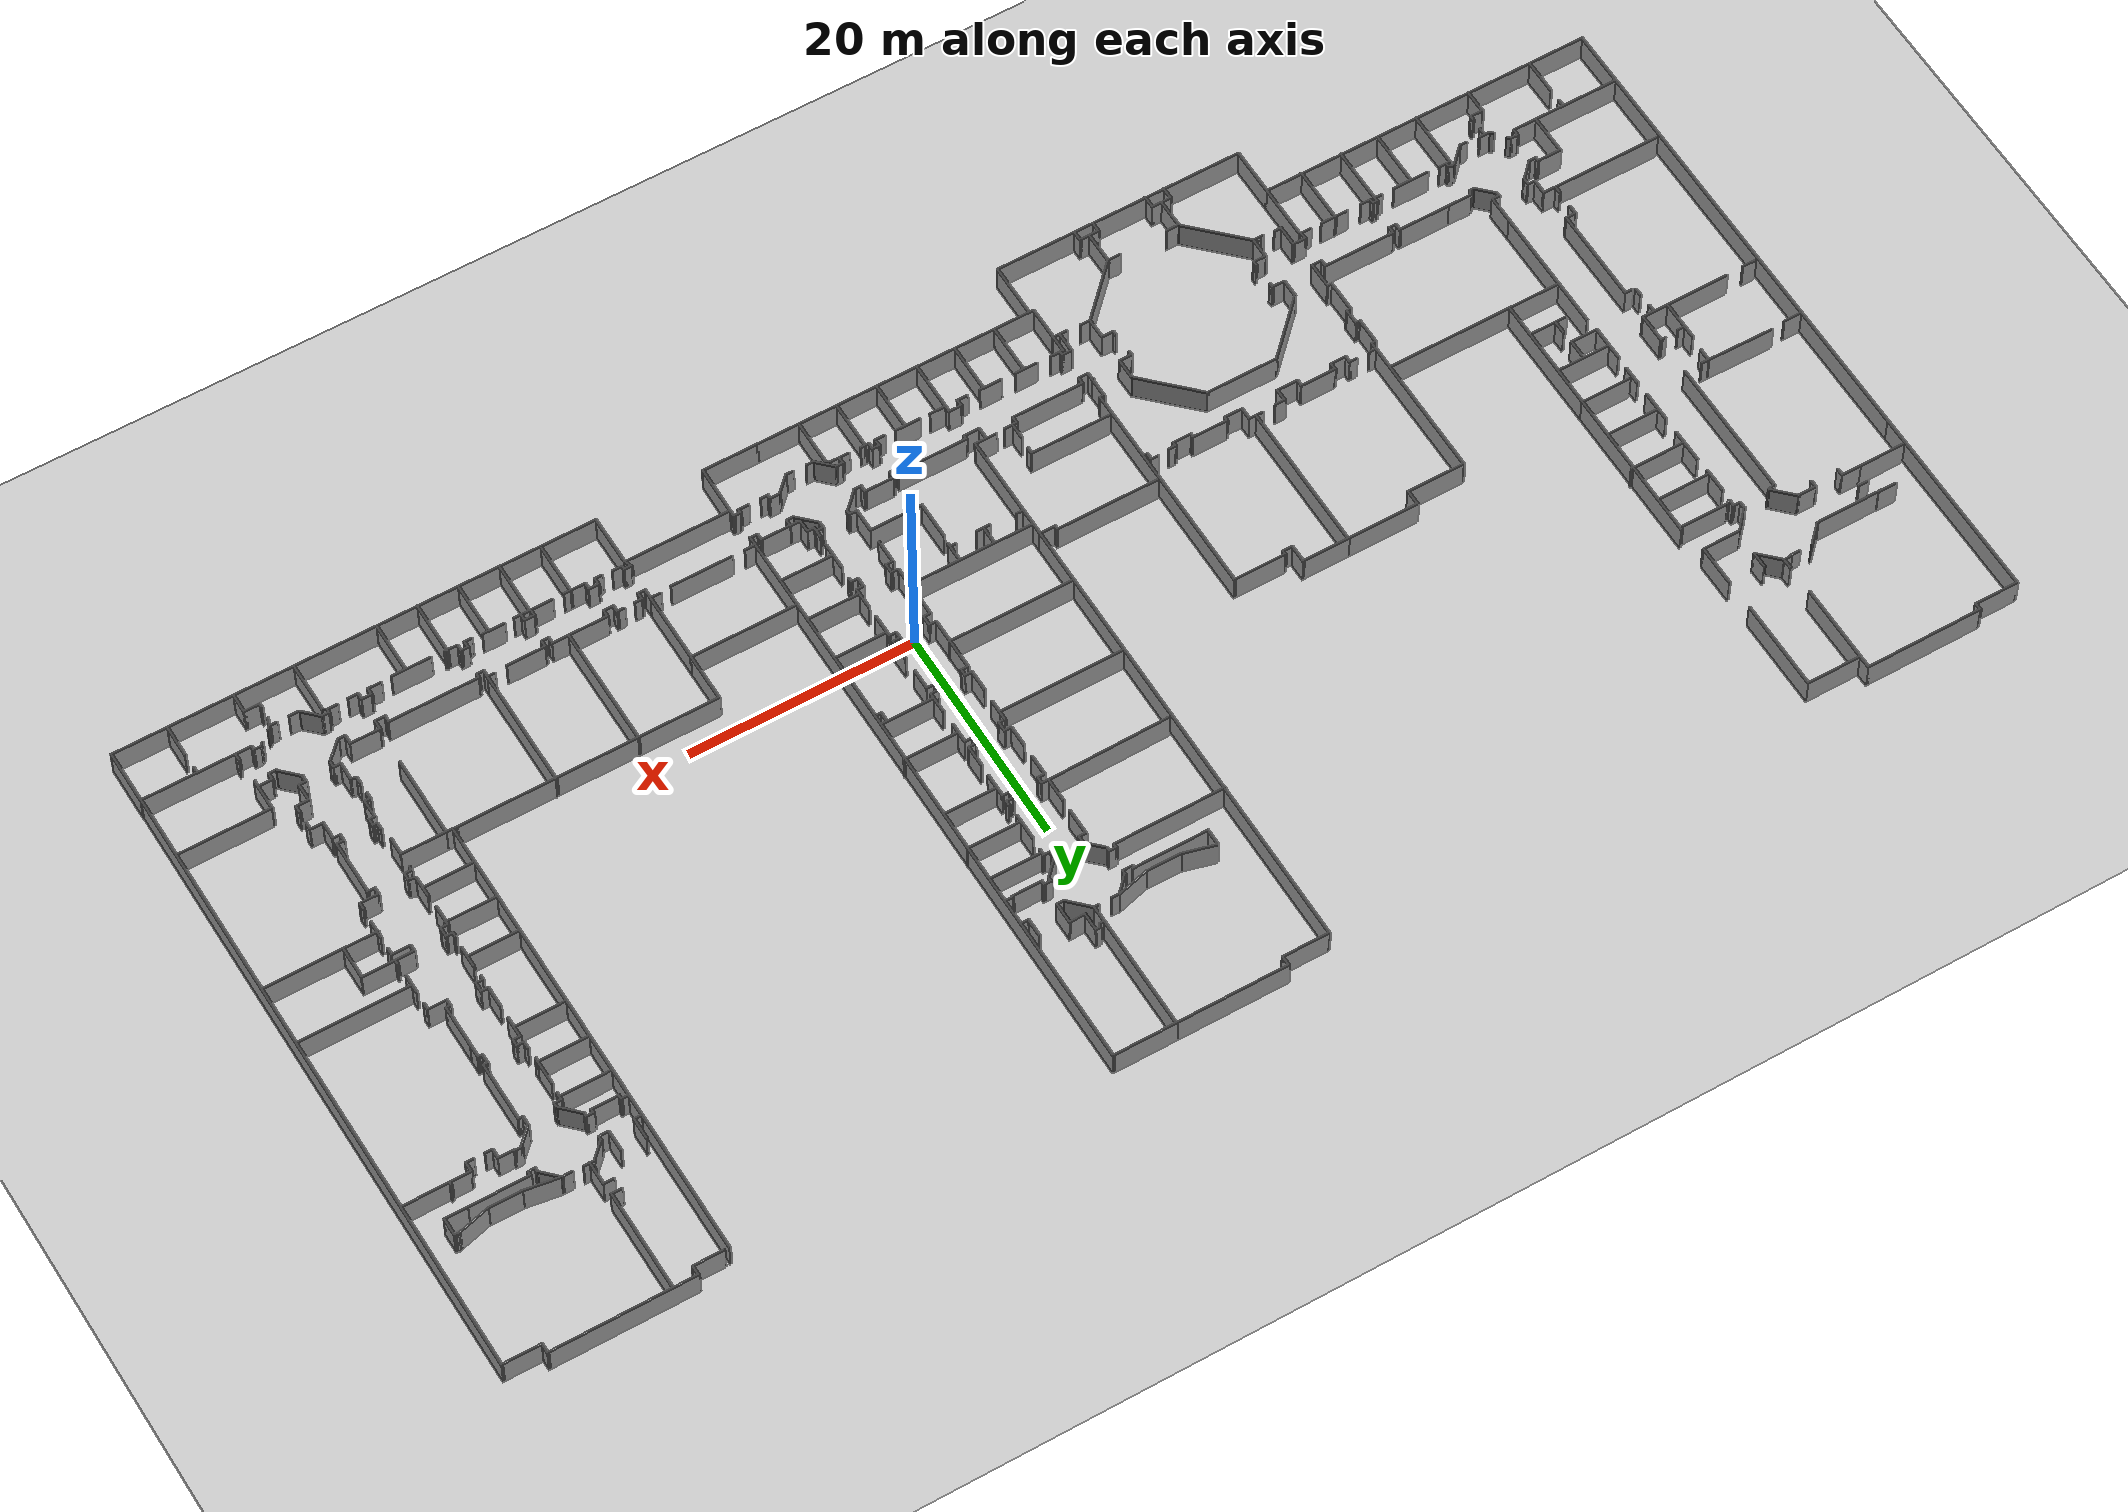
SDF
<sdf version="1.9">
 <world name="default">
  <physics name="1ms" type="ignored">
   <max_step_size>0.001</max_step_size>
   <real_time_factor>1.0</real_time_factor>
  </physics>
  <plugin filename="gz-sim-physics-system" name="gz::sim::systems::Physics"/>
  <plugin filename="gz-sim-sensors-system" name="gz::sim::systems::Sensors">
   <render_engine>ogre2</render_engine>
  </plugin>
  <plugin filename="gz-sim-user-commands-system" name="gz::sim::systems::UserCommands"/>
  <plugin filename="gz-sim-scene-broadcaster-system" name="gz::sim::systems::SceneBroadcaster"/>
  <plugin filename="gz-sim-contact-system" name="gz::sim::systems::Contact"/>
  <light type="directional" name="sun">
   <pose>0 0 10 0 0 0</pose>
   <diffuse>0.8 0.8 0.8 1</diffuse>
   <specular>0.2 0.2 0.2 1</specular>
   <attenuation>
    <range>1000</range>
    <constant>0.9</constant>
    <linear>0.01</linear>
    <quadratic>0.001</quadratic>
   </attenuation>
   <direction>-0.5 0.1 -0.9</direction>
  </light>
  <model name="ground_plane">
   <static>true</static>
   <link name="link">
    <collision name="collision">
     <geometry><plane><normal>0 0 1</normal><size>200 100</size></plane></geometry>
    </collision>
    <visual name="visual">
     <geometry><plane><normal>0 0 1</normal><size>200 100</size></plane></geometry>
     <material>
      <ambient>0.8 0.8 0.8 1</ambient>
      <diffuse>0.8 0.8 0.8 1</diffuse>
      <specular>0.8 0.8 0.8 1</specular>
     </material>
    </visual>
   </link>
  </model>
  <spherical_coordinates>
   <surface_model>EARTH_WGS84</surface_model>
   <latitude_deg>0</latitude_deg>
   <longitude_deg>0</longitude_deg>
   <elevation>0</elevation>
   <heading_deg>0</heading_deg>
  </spherical_coordinates>
  <model name="LuterFloorPlan">
   <pose>-8.27259 7.62647 0 0 -0 0</pose>
   <link name="Door_0">
    <collision name="Door_0_Collision">
     <geometry><box><size>0.9 0.17 2</size></box></geometry>
     <pose>0 0 1 0 -0 0</pose>
    </collision>
    <visual name="Door_0_Visual">
     <pose>0 0 1 0 -0 0</pose>
     <geometry><box><size>0.9 0.17 2</size></box></geometry>
     <material>
      <script><uri>file://media/materials/scripts/gazebo.material</uri><name>Gazebo/Grey</name></script>
     </material>
    </visual>
    <pose>-53.7198 21.2927 0 0 -0 0</pose>
   </link>
   <link name="Door_1">
    <collision name="Door_1_Collision">
     <geometry><box><size>0.9 0.17 2</size></box></geometry>
     <pose>0 0 1 0 -0 0</pose>
    </collision>
    <visual name="Door_1_Visual">
     <pose>0 0 1 0 -0 0</pose>
     <geometry><box><size>0.9 0.17 2</size></box></geometry>
     <material>
      <script><uri>file://media/materials/scripts/gazebo.material</uri><name>Gazebo/Grey</name></script>
     </material>
    </visual>
    <pose>-61.9486 19.7632 0 0 -0 0</pose>
   </link>
   <link name="Door_2">
    <collision name="Door_2_Collision">
     <geometry><box><size>0.9 0.17 2</size></box></geometry>
     <pose>0 0 1 0 -0 0</pose>
    </collision>
    <visual name="Door_2_Visual">
     <pose>0 0 1 0 -0 0</pose>
     <geometry><box><size>0.9 0.17 2</size></box></geometry>
     <material>
      <script><uri>file://media/materials/scripts/gazebo.material</uri><name>Gazebo/Grey</name></script>
     </material>
    </visual>
    <pose>-61.918 18.5396 0 0 -0 0</pose>
   </link>
   <link name="Wall_10">
    <collision name="Wall_10_Collision">
     <geometry><box><size>2.25 0.15 2.5</size></box></geometry>
     <pose>0 0 1.25 0 -0 0</pose>
    </collision>
    <visual name="Wall_10_Visual">
     <pose>0 0 1.25 0 -0 0</pose>
     <geometry><box><size>2.25 0.15 2.5</size></box></geometry>
     <material>
      <script><uri>file://media/materials/scripts/gazebo.material</uri><name>Gazebo/Grey</name></script>
      <ambient>1 1 1 1</ambient>
     </material>
    </visual>
    <pose>-55.8278 20.7995 0 0 0 -2.35619</pose>
   </link>
   <link name="Wall_1000">
    <collision name="Wall_1000_Collision">
     <geometry><box><size>5 0.15 2.5</size></box></geometry>
     <pose>0 0 1.25 0 -0 0</pose>
    </collision>
    <visual name="Wall_1000_Visual">
     <pose>0 0 1.25 0 -0 0</pose>
     <geometry><box><size>5 0.15 2.5</size></box></geometry>
     <material>
      <script><uri>file://media/materials/scripts/gazebo.material</uri><name>Gazebo/Grey</name></script>
      <ambient>1 1 1 1</ambient>
     </material>
    </visual>
    <pose>66.6595 -26.411 0 0 0 -1.5708</pose>
   </link>
   <link name="Wall_1003">
    <collision name="Wall_1003_Collision">
     <geometry><box><size>0.5 0.15 2.5</size></box></geometry>
     <pose>0 0 1.25 0 -0 0</pose>
    </collision>
    <visual name="Wall_1003_Visual">
     <pose>0 0 1.25 0 -0 0</pose>
     <geometry><box><size>0.5 0.15 2.5</size></box></geometry>
     <material>
      <script><uri>file://media/materials/scripts/gazebo.material</uri><name>Gazebo/Grey</name></script>
      <ambient>1 1 1 1</ambient>
     </material>
    </visual>
    <pose>61.8477 -24.3968 0 0 -0 1.5708</pose>
   </link>
   <link name="Wall_1005">
    <collision name="Wall_1005_Collision">
     <geometry><box><size>3 0.15 2.5</size></box></geometry>
     <pose>0 0 1.25 0 -0 0</pose>
    </collision>
    <visual name="Wall_1005_Visual">
     <pose>0 0 1.25 0 -0 0</pose>
     <geometry><box><size>3 0.15 2.5</size></box></geometry>
     <material>
      <script><uri>file://media/materials/scripts/gazebo.material</uri><name>Gazebo/Grey</name></script>
      <ambient>1 1 1 1</ambient>
     </material>
    </visual>
    <pose>61.8785 -27.343 0 0 -0 1.5708</pose>
   </link>
   <link name="Wall_1007">
    <collision name="Wall_1007_Collision">
     <geometry><box><size>0.75 0.15 2.5</size></box></geometry>
     <pose>0 0 1.25 0 -0 0</pose>
    </collision>
    <visual name="Wall_1007_Visual">
     <pose>0 0 1.25 0 -0 0</pose>
     <geometry><box><size>0.75 0.15 2.5</size></box></geometry>
     <material>
      <script><uri>file://media/materials/scripts/gazebo.material</uri><name>Gazebo/Grey</name></script>
      <ambient>1 1 1 1</ambient>
     </material>
    </visual>
    <pose>51.6413 -17.1025 0 0 0 -1.5708</pose>
   </link>
   <link name="Wall_1008">
    <collision name="Wall_1008_Collision">
     <geometry><box><size>0.619398 0.15 2.5</size></box></geometry>
     <pose>0 0 1.25 0 -0 0</pose>
    </collision>
    <visual name="Wall_1008_Visual">
     <pose>0 0 1.25 0 -0 0</pose>
     <geometry><box><size>0.619398 0.15 2.5</size></box></geometry>
     <material>
      <script><uri>file://media/materials/scripts/gazebo.material</uri><name>Gazebo/Grey</name></script>
      <ambient>1 1 1 1</ambient>
     </material>
    </visual>
    <pose>51.8689 -17.46 0 0 0 -0.24752</pose>
   </link>
   <link name="Wall_101">
    <collision name="Wall_101_Collision">
     <geometry><box><size>3.25 0.15 2.5</size></box></geometry>
     <pose>0 0 1.25 0 -0 0</pose>
    </collision>
    <visual name="Wall_101_Visual">
     <pose>0 0 1.25 0 -0 0</pose>
     <geometry><box><size>3.25 0.15 2.5</size></box></geometry>
     <material>
      <script><uri>file://media/materials/scripts/gazebo.material</uri><name>Gazebo/Grey</name></script>
      <ambient>1 1 1 1</ambient>
     </material>
    </visual>
    <pose>-48.9481 -6.49816 0 0 -0 0</pose>
   </link>
   <link name="Wall_1010">
    <collision name="Wall_1010_Collision">
     <geometry><box><size>0.75 0.15 2.5</size></box></geometry>
     <pose>0 0 1.25 0 -0 0</pose>
    </collision>
    <visual name="Wall_1010_Visual">
     <pose>0 0 1.25 0 -0 0</pose>
     <geometry><box><size>0.75 0.15 2.5</size></box></geometry>
     <material>
      <script><uri>file://media/materials/scripts/gazebo.material</uri><name>Gazebo/Grey</name></script>
      <ambient>1 1 1 1</ambient>
     </material>
    </visual>
    <pose>51.6589 -15.4471 0 0 -0 1.5708</pose>
   </link>
   <link name="Wall_1011">
    <collision name="Wall_1011_Collision">
     <geometry><box><size>0.624432 0.15 2.5</size></box></geometry>
     <pose>0 0 1.25 0 -0 0</pose>
    </collision>
    <visual name="Wall_1011_Visual">
     <pose>0 0 1.25 0 -0 0</pose>
     <geometry><box><size>0.624432 0.15 2.5</size></box></geometry>
     <material>
      <script><uri>file://media/materials/scripts/gazebo.material</uri><name>Gazebo/Grey</name></script>
      <ambient>1 1 1 1</ambient>
     </material>
    </visual>
    <pose>51.8955 -15.1559 0 0 0 -0.03716</pose>
   </link>
   <link name="Wall_1012">
    <collision name="Wall_1012_Collision">
     <geometry><box><size>1.75 0.15 2.5</size></box></geometry>
     <pose>0 0 1.25 0 -0 0</pose>
    </collision>
    <visual name="Wall_1012_Visual">
     <pose>0 0 1.25 0 -0 0</pose>
     <geometry><box><size>1.75 0.15 2.5</size></box></geometry>
     <material>
      <script><uri>file://media/materials/scripts/gazebo.material</uri><name>Gazebo/Grey</name></script>
      <ambient>1 1 1 1</ambient>
     </material>
    </visual>
    <pose>52.132 -14.3823 0 0 -0 1.5708</pose>
   </link>
   <link name="Wall_1013">
    <collision name="Wall_1013_Collision">
     <geometry><box><size>0.62817 0.15 2.5</size></box></geometry>
     <pose>0 0 1.25 0 -0 0</pose>
    </collision>
    <visual name="Wall_1013_Visual">
     <pose>0 0 1.25 0 -0 0</pose>
     <geometry><box><size>0.62817 0.15 2.5</size></box></geometry>
     <material>
      <script><uri>file://media/materials/scripts/gazebo.material</uri><name>Gazebo/Grey</name></script>
      <ambient>1 1 1 1</ambient>
     </material>
    </visual>
    <pose>52.3705 -13.5559 0 0 -0 0.036868</pose>
   </link>
   <link name="Wall_1014">
    <collision name="Wall_1014_Collision">
     <geometry><box><size>0.75 0.15 2.5</size></box></geometry>
     <pose>0 0 1.25 0 -0 0</pose>
    </collision>
    <visual name="Wall_1014_Visual">
     <pose>0 0 1.25 0 -0 0</pose>
     <geometry><box><size>0.75 0.15 2.5</size></box></geometry>
     <material>
      <script><uri>file://media/materials/scripts/gazebo.material</uri><name>Gazebo/Grey</name></script>
      <ambient>1 1 1 1</ambient>
     </material>
    </visual>
    <pose>52.6089 -13.2471 0 0 -0 1.5708</pose>
   </link>
   <link name="Wall_1015">
    <collision name="Wall_1015_Collision">
     <geometry><box><size>0.5 0.15 2.5</size></box></geometry>
     <pose>0 0 1.25 0 -0 0</pose>
    </collision>
    <visual name="Wall_1015_Visual">
     <pose>0 0 1.25 0 -0 0</pose>
     <geometry><box><size>0.5 0.15 2.5</size></box></geometry>
     <material>
      <script><uri>file://media/materials/scripts/gazebo.material</uri><name>Gazebo/Grey</name></script>
      <ambient>1 1 1 1</ambient>
     </material>
    </visual>
    <pose>52.4339 -12.9471 0 0 -0 3.14159</pose>
   </link>
   <link name="Wall_1016">
    <collision name="Wall_1016_Collision">
     <geometry><box><size>0.75 0.15 2.5</size></box></geometry>
     <pose>0 0 1.25 0 -0 0</pose>
    </collision>
    <visual name="Wall_1016_Visual">
     <pose>0 0 1.25 0 -0 0</pose>
     <geometry><box><size>0.75 0.15 2.5</size></box></geometry>
     <material>
      <script><uri>file://media/materials/scripts/gazebo.material</uri><name>Gazebo/Grey</name></script>
      <ambient>1 1 1 1</ambient>
     </material>
    </visual>
    <pose>52.2589 -12.6471 0 0 -0 1.5708</pose>
   </link>
   <link name="Wall_1018">
    <collision name="Wall_1018_Collision">
     <geometry><box><size>7.5 0.15 2.5</size></box></geometry>
     <pose>0 0 1.25 0 -0 0</pose>
    </collision>
    <visual name="Wall_1018_Visual">
     <pose>0 0 1.25 0 -0 0</pose>
     <geometry><box><size>7.5 0.15 2.5</size></box></geometry>
     <material>
      <script><uri>file://media/materials/scripts/gazebo.material</uri><name>Gazebo/Grey</name></script>
      <ambient>1 1 1 1</ambient>
     </material>
    </visual>
    <pose>48.1762 -13.2682 0 0 -0 1.5708</pose>
   </link>
   <link name="Wall_1019">
    <collision name="Wall_1019_Collision">
     <geometry><box><size>4 0.15 2.5</size></box></geometry>
     <pose>0 0 1.25 0 -0 0</pose>
    </collision>
    <visual name="Wall_1019_Visual">
     <pose>0 0 1.25 0 -0 0</pose>
     <geometry><box><size>4 0.15 2.5</size></box></geometry>
     <material>
      <script><uri>file://media/materials/scripts/gazebo.material</uri><name>Gazebo/Grey</name></script>
      <ambient>1 1 1 1</ambient>
     </material>
    </visual>
    <pose>50.1012 -9.59318 0 0 -0 0</pose>
   </link>
   <link name="Wall_1020">
    <collision name="Wall_1020_Collision">
     <geometry><box><size>1.75 0.15 2.5</size></box></geometry>
     <pose>0 0 1.25 0 -0 0</pose>
    </collision>
    <visual name="Wall_1020_Visual">
     <pose>0 0 1.25 0 -0 0</pose>
     <geometry><box><size>1.75 0.15 2.5</size></box></geometry>
     <material>
      <script><uri>file://media/materials/scripts/gazebo.material</uri><name>Gazebo/Grey</name></script>
      <ambient>1 1 1 1</ambient>
     </material>
    </visual>
    <pose>52.0262 -10.3932 0 0 0 -1.5708</pose>
   </link>
   <link name="Wall_1022">
    <collision name="Wall_1022_Collision">
     <geometry><box><size>1.02593 0.15 2.5</size></box></geometry>
     <pose>0 0 1.25 0 -0 0</pose>
    </collision>
    <visual name="Wall_1022_Visual">
     <pose>0 0 1.25 0 -0 0</pose>
     <geometry><box><size>1.02593 0.15 2.5</size></box></geometry>
     <material>
      <script><uri>file://media/materials/scripts/gazebo.material</uri><name>Gazebo/Grey</name></script>
      <ambient>1 1 1 1</ambient>
     </material>
    </visual>
    <pose>47.7385 -9.57923 0 0 -0 3.10974</pose>
   </link>
   <link name="Wall_1024">
    <collision name="Wall_1024_Collision">
     <geometry><box><size>42.25 0.15 2.5</size></box></geometry>
     <pose>0 0 1.25 0 -0 0</pose>
    </collision>
    <visual name="Wall_1024_Visual">
     <pose>0 0 1.25 0 -0 0</pose>
     <geometry><box><size>42.25 0.15 2.5</size></box></geometry>
     <material>
      <script><uri>file://media/materials/scripts/gazebo.material</uri><name>Gazebo/Grey</name></script>
      <ambient>1 1 1 1</ambient>
     </material>
    </visual>
    <pose>47.5967 11.6687 0 0 -0 1.5708</pose>
   </link>
   <link name="Wall_1026">
    <collision name="Wall_1026_Collision">
     <geometry><box><size>2.75 0.15 2.5</size></box></geometry>
     <pose>0 0 1.25 0 -0 0</pose>
    </collision>
    <visual name="Wall_1026_Visual">
     <pose>0 0 1.25 0 -0 0</pose>
     <geometry><box><size>2.75 0.15 2.5</size></box></geometry>
     <material>
      <script><uri>file://media/materials/scripts/gazebo.material</uri><name>Gazebo/Grey</name></script>
      <ambient>1 1 1 1</ambient>
     </material>
    </visual>
    <pose>49.3708 32.7214 0 0 -0 0</pose>
   </link>
   <link name="Wall_1027">
    <collision name="Wall_1027_Collision">
     <geometry><box><size>1 0.15 2.5</size></box></geometry>
     <pose>0 0 1.25 0 -0 0</pose>
    </collision>
    <visual name="Wall_1027_Visual">
     <pose>0 0 1.25 0 -0 0</pose>
     <geometry><box><size>1 0.15 2.5</size></box></geometry>
     <material>
      <script><uri>file://media/materials/scripts/gazebo.material</uri><name>Gazebo/Grey</name></script>
      <ambient>1 1 1 1</ambient>
     </material>
    </visual>
    <pose>50.6708 33.1464 0 0 -0 1.5708</pose>
   </link>
   <link name="Wall_1028">
    <collision name="Wall_1028_Collision">
     <geometry><box><size>12.75 0.15 2.5</size></box></geometry>
     <pose>0 0 1.25 0 -0 0</pose>
    </collision>
    <visual name="Wall_1028_Visual">
     <pose>0 0 1.25 0 -0 0</pose>
     <geometry><box><size>12.75 0.15 2.5</size></box></geometry>
     <material>
      <script><uri>file://media/materials/scripts/gazebo.material</uri><name>Gazebo/Grey</name></script>
      <ambient>1 1 1 1</ambient>
     </material>
    </visual>
    <pose>56.9708 33.5714 0 0 -0 0</pose>
   </link>
   <link name="Wall_1029">
    <collision name="Wall_1029_Collision">
     <geometry><box><size>1 0.15 2.5</size></box></geometry>
     <pose>0 0 1.25 0 -0 0</pose>
    </collision>
    <visual name="Wall_1029_Visual">
     <pose>0 0 1.25 0 -0 0</pose>
     <geometry><box><size>1 0.15 2.5</size></box></geometry>
     <material>
      <script><uri>file://media/materials/scripts/gazebo.material</uri><name>Gazebo/Grey</name></script>
      <ambient>1 1 1 1</ambient>
     </material>
    </visual>
    <pose>63.2708 33.1464 0 0 0 -1.5708</pose>
   </link>
   <link name="Wall_103">
    <collision name="Wall_103_Collision">
     <geometry><box><size>1.25 0.15 2.5</size></box></geometry>
     <pose>0 0 1.25 0 -0 0</pose>
    </collision>
    <visual name="Wall_103_Visual">
     <pose>0 0 1.25 0 -0 0</pose>
     <geometry><box><size>1.25 0.15 2.5</size></box></geometry>
     <material>
      <script><uri>file://media/materials/scripts/gazebo.material</uri><name>Gazebo/Grey</name></script>
      <ambient>1 1 1 1</ambient>
     </material>
    </visual>
    <pose>-49.5326 -5.88782 0 0 -0 1.5708</pose>
   </link>
   <link name="Wall_1030">
    <collision name="Wall_1030_Collision">
     <geometry><box><size>3.5 0.15 2.5</size></box></geometry>
     <pose>0 0 1.25 0 -0 0</pose>
    </collision>
    <visual name="Wall_1030_Visual">
     <pose>0 0 1.25 0 -0 0</pose>
     <geometry><box><size>3.5 0.15 2.5</size></box></geometry>
     <material>
      <script><uri>file://media/materials/scripts/gazebo.material</uri><name>Gazebo/Grey</name></script>
      <ambient>1 1 1 1</ambient>
     </material>
    </visual>
    <pose>64.9458 32.7214 0 0 -0 0</pose>
   </link>
   <link name="Wall_1033">
    <collision name="Wall_1033_Collision">
     <geometry><box><size>57 0.15 2.5</size></box></geometry>
     <pose>0 0 1.25 0 -0 0</pose>
    </collision>
    <visual name="Wall_1033_Visual">
     <pose>0 0 1.25 0 -0 0</pose>
     <geometry><box><size>57 0.15 2.5</size></box></geometry>
     <material>
      <script><uri>file://media/materials/scripts/gazebo.material</uri><name>Gazebo/Grey</name></script>
      <ambient>1 1 1 1</ambient>
     </material>
    </visual>
    <pose>66.6208 4.29644 0 0 0 -1.5708</pose>
   </link>
   <link name="Wall_1035">
    <collision name="Wall_1035_Collision">
     <geometry><box><size>3 0.15 2.5</size></box></geometry>
     <pose>0 0 1.25 0 -0 0</pose>
    </collision>
    <visual name="Wall_1035_Visual">
     <pose>0 0 1.25 0 -0 0</pose>
     <geometry><box><size>3 0.15 2.5</size></box></geometry>
     <material>
      <script><uri>file://media/materials/scripts/gazebo.material</uri><name>Gazebo/Grey</name></script>
      <ambient>1 1 1 1</ambient>
     </material>
    </visual>
    <pose>58.4478 -19.6647 0 0 -0 1.5708</pose>
   </link>
   <link name="Wall_1036">
    <collision name="Wall_1036_Collision">
     <geometry><box><size>8.25 0.15 2.5</size></box></geometry>
     <pose>0 0 1.25 0 -0 0</pose>
    </collision>
    <visual name="Wall_1036_Visual">
     <pose>0 0 1.25 0 -0 0</pose>
     <geometry><box><size>8.25 0.15 2.5</size></box></geometry>
     <material>
      <script><uri>file://media/materials/scripts/gazebo.material</uri><name>Gazebo/Grey</name></script>
      <ambient>1 1 1 1</ambient>
     </material>
    </visual>
    <pose>62.4978 -18.2397 0 0 -0 0</pose>
   </link>
   <link name="Wall_1038">
    <collision name="Wall_1038_Collision">
     <geometry><box><size>0.75 0.15 2.5</size></box></geometry>
     <pose>0 0 1.25 0 -0 0</pose>
    </collision>
    <visual name="Wall_1038_Visual">
     <pose>0 0 1.25 0 -0 0</pose>
     <geometry><box><size>0.75 0.15 2.5</size></box></geometry>
     <material>
      <script><uri>file://media/materials/scripts/gazebo.material</uri><name>Gazebo/Grey</name></script>
      <ambient>1 1 1 1</ambient>
     </material>
    </visual>
    <pose>56.816 -17.1362 0 0 0 -1.5708</pose>
   </link>
   <link name="Wall_1039">
    <collision name="Wall_1039_Collision">
     <geometry><box><size>1.25 0.15 2.5</size></box></geometry>
     <pose>0 0 1.25 0 -0 0</pose>
    </collision>
    <visual name="Wall_1039_Visual">
     <pose>0 0 1.25 0 -0 0</pose>
     <geometry><box><size>1.25 0.15 2.5</size></box></geometry>
     <material>
      <script><uri>file://media/materials/scripts/gazebo.material</uri><name>Gazebo/Grey</name></script>
      <ambient>1 1 1 1</ambient>
     </material>
    </visual>
    <pose>56.266 -17.4362 0 0 -0 3.14159</pose>
   </link>
   <link name="Wall_1040">
    <collision name="Wall_1040_Collision">
     <geometry><box><size>1.75 0.15 2.5</size></box></geometry>
     <pose>0 0 1.25 0 -0 0</pose>
    </collision>
    <visual name="Wall_1040_Visual">
     <pose>0 0 1.25 0 -0 0</pose>
     <geometry><box><size>1.75 0.15 2.5</size></box></geometry>
     <material>
      <script><uri>file://media/materials/scripts/gazebo.material</uri><name>Gazebo/Grey</name></script>
      <ambient>1 1 1 1</ambient>
     </material>
    </visual>
    <pose>55.716 -18.2362 0 0 0 -1.5708</pose>
   </link>
   <link name="Wall_1041">
    <collision name="Wall_1041_Collision">
     <geometry><box><size>0.75 0.15 2.5</size></box></geometry>
     <pose>0 0 1.25 0 -0 0</pose>
    </collision>
    <visual name="Wall_1041_Visual">
     <pose>0 0 1.25 0 -0 0</pose>
     <geometry><box><size>0.75 0.15 2.5</size></box></geometry>
     <material>
      <script><uri>file://media/materials/scripts/gazebo.material</uri><name>Gazebo/Grey</name></script>
      <ambient>1 1 1 1</ambient>
     </material>
    </visual>
    <pose>55.416 -19.0362 0 0 -0 3.14159</pose>
   </link>
   <link name="Wall_1042">
    <collision name="Wall_1042_Collision">
     <geometry><box><size>0.75 0.15 2.5</size></box></geometry>
     <pose>0 0 1.25 0 -0 0</pose>
    </collision>
    <visual name="Wall_1042_Visual">
     <pose>0 0 1.25 0 -0 0</pose>
     <geometry><box><size>0.75 0.15 2.5</size></box></geometry>
     <material>
      <script><uri>file://media/materials/scripts/gazebo.material</uri><name>Gazebo/Grey</name></script>
      <ambient>1 1 1 1</ambient>
     </material>
    </visual>
    <pose>55.116 -19.3362 0 0 0 -1.5708</pose>
   </link>
   <link name="Wall_1043">
    <collision name="Wall_1043_Collision">
     <geometry><box><size>2.25 0.15 2.5</size></box></geometry>
     <pose>0 0 1.25 0 -0 0</pose>
    </collision>
    <visual name="Wall_1043_Visual">
     <pose>0 0 1.25 0 -0 0</pose>
     <geometry><box><size>2.25 0.15 2.5</size></box></geometry>
     <material>
      <script><uri>file://media/materials/scripts/gazebo.material</uri><name>Gazebo/Grey</name></script>
      <ambient>1 1 1 1</ambient>
     </material>
    </visual>
    <pose>55.8585 -20.3787 0 0 0 -0.785398</pose>
   </link>
   <link name="Wall_1044">
    <collision name="Wall_1044_Collision">
     <geometry><box><size>0.75 0.15 2.5</size></box></geometry>
     <pose>0 0 1.25 0 -0 0</pose>
    </collision>
    <visual name="Wall_1044_Visual">
     <pose>0 0 1.25 0 -0 0</pose>
     <geometry><box><size>0.75 0.15 2.5</size></box></geometry>
     <material>
      <script><uri>file://media/materials/scripts/gazebo.material</uri><name>Gazebo/Grey</name></script>
      <ambient>1 1 1 1</ambient>
     </material>
    </visual>
    <pose>56.9009 -21.1212 0 0 -0 0</pose>
   </link>
   <link name="Wall_1045">
    <collision name="Wall_1045_Collision">
     <geometry><box><size>0.75 0.15 2.5</size></box></geometry>
     <pose>0 0 1.25 0 -0 0</pose>
    </collision>
    <visual name="Wall_1045_Visual">
     <pose>0 0 1.25 0 -0 0</pose>
     <geometry><box><size>0.75 0.15 2.5</size></box></geometry>
     <material>
      <script><uri>file://media/materials/scripts/gazebo.material</uri><name>Gazebo/Grey</name></script>
      <ambient>1 1 1 1</ambient>
     </material>
    </visual>
    <pose>57.2009 -20.8212 0 0 -0 1.5708</pose>
   </link>
   <link name="Wall_1046">
    <collision name="Wall_1046_Collision">
     <geometry><box><size>1.25 0.15 2.5</size></box></geometry>
     <pose>0 0 1.25 0 -0 0</pose>
    </collision>
    <visual name="Wall_1046_Visual">
     <pose>0 0 1.25 0 -0 0</pose>
     <geometry><box><size>1.25 0.15 2.5</size></box></geometry>
     <material>
      <script><uri>file://media/materials/scripts/gazebo.material</uri><name>Gazebo/Grey</name></script>
      <ambient>1 1 1 1</ambient>
     </material>
    </visual>
    <pose>57.7509 -20.5212 0 0 -0 0</pose>
   </link>
   <link name="Wall_1048">
    <collision name="Wall_1048_Collision">
     <geometry><box><size>0.75 0.15 2.5</size></box></geometry>
     <pose>0 0 1.25 0 -0 0</pose>
    </collision>
    <visual name="Wall_1048_Visual">
     <pose>0 0 1.25 0 -0 0</pose>
     <geometry><box><size>0.75 0.15 2.5</size></box></geometry>
     <material>
      <script><uri>file://media/materials/scripts/gazebo.material</uri><name>Gazebo/Grey</name></script>
      <ambient>1 1 1 1</ambient>
     </material>
    </visual>
    <pose>56.8695 -15.3859 0 0 -0 1.5708</pose>
   </link>
   <link name="Wall_1049">
    <collision name="Wall_1049_Collision">
     <geometry><box><size>1.25 0.15 2.5</size></box></geometry>
     <pose>0 0 1.25 0 -0 0</pose>
    </collision>
    <visual name="Wall_1049_Visual">
     <pose>0 0 1.25 0 -0 0</pose>
     <geometry><box><size>1.25 0.15 2.5</size></box></geometry>
     <material>
      <script><uri>file://media/materials/scripts/gazebo.material</uri><name>Gazebo/Grey</name></script>
      <ambient>1 1 1 1</ambient>
     </material>
    </visual>
    <pose>56.3195 -15.0859 0 0 -0 3.14159</pose>
   </link>
   <link name="Wall_105">
    <collision name="Wall_105_Collision">
     <geometry><box><size>2.5 0.15 2.5</size></box></geometry>
     <pose>0 0 1.25 0 -0 0</pose>
    </collision>
    <visual name="Wall_105_Visual">
     <pose>0 0 1.25 0 -0 0</pose>
     <geometry><box><size>2.5 0.15 2.5</size></box></geometry>
     <material>
      <script><uri>file://media/materials/scripts/gazebo.material</uri><name>Gazebo/Grey</name></script>
      <ambient>1 1 1 1</ambient>
     </material>
    </visual>
    <pose>-50.7511 -4.22783 0 0 -0 0</pose>
   </link>
   <link name="Wall_1050">
    <collision name="Wall_1050_Collision">
     <geometry><box><size>1.75 0.15 2.5</size></box></geometry>
     <pose>0 0 1.25 0 -0 0</pose>
    </collision>
    <visual name="Wall_1050_Visual">
     <pose>0 0 1.25 0 -0 0</pose>
     <geometry><box><size>1.75 0.15 2.5</size></box></geometry>
     <material>
      <script><uri>file://media/materials/scripts/gazebo.material</uri><name>Gazebo/Grey</name></script>
      <ambient>1 1 1 1</ambient>
     </material>
    </visual>
    <pose>55.7695 -14.2859 0 0 -0 1.5708</pose>
   </link>
   <link name="Wall_1051">
    <collision name="Wall_1051_Collision">
     <geometry><box><size>0.75 0.15 2.5</size></box></geometry>
     <pose>0 0 1.25 0 -0 0</pose>
    </collision>
    <visual name="Wall_1051_Visual">
     <pose>0 0 1.25 0 -0 0</pose>
     <geometry><box><size>0.75 0.15 2.5</size></box></geometry>
     <material>
      <script><uri>file://media/materials/scripts/gazebo.material</uri><name>Gazebo/Grey</name></script>
      <ambient>1 1 1 1</ambient>
     </material>
    </visual>
    <pose>55.4695 -13.4859 0 0 -0 3.14159</pose>
   </link>
   <link name="Wall_1052">
    <collision name="Wall_1052_Collision">
     <geometry><box><size>0.75 0.15 2.5</size></box></geometry>
     <pose>0 0 1.25 0 -0 0</pose>
    </collision>
    <visual name="Wall_1052_Visual">
     <pose>0 0 1.25 0 -0 0</pose>
     <geometry><box><size>0.75 0.15 2.5</size></box></geometry>
     <material>
      <script><uri>file://media/materials/scripts/gazebo.material</uri><name>Gazebo/Grey</name></script>
      <ambient>1 1 1 1</ambient>
     </material>
    </visual>
    <pose>55.1695 -13.1859 0 0 -0 1.5708</pose>
   </link>
   <link name="Wall_1053">
    <collision name="Wall_1053_Collision">
     <geometry><box><size>0.75 0.15 2.5</size></box></geometry>
     <pose>0 0 1.25 0 -0 0</pose>
    </collision>
    <visual name="Wall_1053_Visual">
     <pose>0 0 1.25 0 -0 0</pose>
     <geometry><box><size>0.75 0.15 2.5</size></box></geometry>
     <material>
      <script><uri>file://media/materials/scripts/gazebo.material</uri><name>Gazebo/Grey</name></script>
      <ambient>1 1 1 1</ambient>
     </material>
    </visual>
    <pose>55.4695 -12.8859 0 0 -0 0</pose>
   </link>
   <link name="Wall_1054">
    <collision name="Wall_1054_Collision">
     <geometry><box><size>5 0.15 2.5</size></box></geometry>
     <pose>0 0 1.25 0 -0 0</pose>
    </collision>
    <visual name="Wall_1054_Visual">
     <pose>0 0 1.25 0 -0 0</pose>
     <geometry><box><size>5 0.15 2.5</size></box></geometry>
     <material>
      <script><uri>file://media/materials/scripts/gazebo.material</uri><name>Gazebo/Grey</name></script>
      <ambient>1 1 1 1</ambient>
     </material>
    </visual>
    <pose>55.7695 -10.4609 0 0 -0 1.5708</pose>
   </link>
   <link name="Wall_1055">
    <collision name="Wall_1055_Collision">
     <geometry><box><size>0.25 0.15 2.5</size></box></geometry>
     <pose>0 0 1.25 0 -0 0</pose>
    </collision>
    <visual name="Wall_1055_Visual">
     <pose>0 0 1.25 0 -0 0</pose>
     <geometry><box><size>0.25 0.15 2.5</size></box></geometry>
     <material>
      <script><uri>file://media/materials/scripts/gazebo.material</uri><name>Gazebo/Grey</name></script>
      <ambient>1 1 1 1</ambient>
     </material>
    </visual>
    <pose>55.7695 -7.98593 0 0 -0 1.5708</pose>
   </link>
   <link name="Wall_1056">
    <collision name="Wall_1056_Collision">
     <geometry><box><size>0.75 0.15 2.5</size></box></geometry>
     <pose>0 0 1.25 0 -0 0</pose>
    </collision>
    <visual name="Wall_1056_Visual">
     <pose>0 0 1.25 0 -0 0</pose>
     <geometry><box><size>0.75 0.15 2.5</size></box></geometry>
     <material>
      <script><uri>file://media/materials/scripts/gazebo.material</uri><name>Gazebo/Grey</name></script>
      <ambient>1 1 1 1</ambient>
     </material>
    </visual>
    <pose>55.4695 -7.93593 0 0 -0 3.14159</pose>
   </link>
   <link name="Wall_1057">
    <collision name="Wall_1057_Collision">
     <geometry><box><size>0.75 0.15 2.5</size></box></geometry>
     <pose>0 0 1.25 0 -0 0</pose>
    </collision>
    <visual name="Wall_1057_Visual">
     <pose>0 0 1.25 0 -0 0</pose>
     <geometry><box><size>0.75 0.15 2.5</size></box></geometry>
     <material>
      <script><uri>file://media/materials/scripts/gazebo.material</uri><name>Gazebo/Grey</name></script>
      <ambient>1 1 1 1</ambient>
     </material>
    </visual>
    <pose>55.1695 -7.63593 0 0 -0 1.5708</pose>
   </link>
   <link name="Wall_1058">
    <collision name="Wall_1058_Collision">
     <geometry><box><size>1.75 0.15 2.5</size></box></geometry>
     <pose>0 0 1.25 0 -0 0</pose>
    </collision>
    <visual name="Wall_1058_Visual">
     <pose>0 0 1.25 0 -0 0</pose>
     <geometry><box><size>1.75 0.15 2.5</size></box></geometry>
     <material>
      <script><uri>file://media/materials/scripts/gazebo.material</uri><name>Gazebo/Grey</name></script>
      <ambient>1 1 1 1</ambient>
     </material>
    </visual>
    <pose>55.9695 -7.33593 0 0 -0 0</pose>
   </link>
   <link name="Wall_1059">
    <collision name="Wall_1059_Collision">
     <geometry><box><size>0.75 0.15 2.5</size></box></geometry>
     <pose>0 0 1.25 0 -0 0</pose>
    </collision>
    <visual name="Wall_1059_Visual">
     <pose>0 0 1.25 0 -0 0</pose>
     <geometry><box><size>0.75 0.15 2.5</size></box></geometry>
     <material>
      <script><uri>file://media/materials/scripts/gazebo.material</uri><name>Gazebo/Grey</name></script>
      <ambient>1 1 1 1</ambient>
     </material>
    </visual>
    <pose>56.7695 -7.03593 0 0 -0 1.5708</pose>
   </link>
   <link name="Wall_106">
    <collision name="Wall_106_Collision">
     <geometry><box><size>1.75 0.15 2.5</size></box></geometry>
     <pose>0 0 1.25 0 -0 0</pose>
    </collision>
    <visual name="Wall_106_Visual">
     <pose>0 0 1.25 0 -0 0</pose>
     <geometry><box><size>1.75 0.15 2.5</size></box></geometry>
     <material>
      <script><uri>file://media/materials/scripts/gazebo.material</uri><name>Gazebo/Grey</name></script>
      <ambient>1 1 1 1</ambient>
     </material>
    </visual>
    <pose>-49.5761 -3.42783 0 0 -0 1.5708</pose>
   </link>
   <link name="Wall_1061">
    <collision name="Wall_1061_Collision">
     <geometry><box><size>0.5 0.15 2.5</size></box></geometry>
     <pose>0 0 1.25 0 -0 0</pose>
    </collision>
    <visual name="Wall_1061_Visual">
     <pose>0 0 1.25 0 -0 0</pose>
     <geometry><box><size>0.5 0.15 2.5</size></box></geometry>
     <material>
      <script><uri>file://media/materials/scripts/gazebo.material</uri><name>Gazebo/Grey</name></script>
      <ambient>1 1 1 1</ambient>
     </material>
    </visual>
    <pose>52.0275 -8.10084 0 0 -0 1.5708</pose>
   </link>
   <link name="Wall_1062">
    <collision name="Wall_1062_Collision">
     <geometry><box><size>0.75 0.15 2.5</size></box></geometry>
     <pose>0 0 1.25 0 -0 0</pose>
    </collision>
    <visual name="Wall_1062_Visual">
     <pose>0 0 1.25 0 -0 0</pose>
     <geometry><box><size>0.75 0.15 2.5</size></box></geometry>
     <material>
      <script><uri>file://media/materials/scripts/gazebo.material</uri><name>Gazebo/Grey</name></script>
      <ambient>1 1 1 1</ambient>
     </material>
    </visual>
    <pose>52.3275 -7.92584 0 0 -0 0</pose>
   </link>
   <link name="Wall_1063">
    <collision name="Wall_1063_Collision">
     <geometry><box><size>0.75 0.15 2.5</size></box></geometry>
     <pose>0 0 1.25 0 -0 0</pose>
    </collision>
    <visual name="Wall_1063_Visual">
     <pose>0 0 1.25 0 -0 0</pose>
     <geometry><box><size>0.75 0.15 2.5</size></box></geometry>
     <material>
      <script><uri>file://media/materials/scripts/gazebo.material</uri><name>Gazebo/Grey</name></script>
      <ambient>1 1 1 1</ambient>
     </material>
    </visual>
    <pose>52.6275 -7.62584 0 0 -0 1.5708</pose>
   </link>
   <link name="Wall_1064">
    <collision name="Wall_1064_Collision">
     <geometry><box><size>0.75 0.15 2.5</size></box></geometry>
     <pose>0 0 1.25 0 -0 0</pose>
    </collision>
    <visual name="Wall_1064_Visual">
     <pose>0 0 1.25 0 -0 0</pose>
     <geometry><box><size>0.75 0.15 2.5</size></box></geometry>
     <material>
      <script><uri>file://media/materials/scripts/gazebo.material</uri><name>Gazebo/Grey</name></script>
      <ambient>1 1 1 1</ambient>
     </material>
    </visual>
    <pose>52.3377 -7.24819 0 0 -0 2.87979</pose>
   </link>
   <link name="Wall_1065">
    <collision name="Wall_1065_Collision">
     <geometry><box><size>2 0.15 2.5</size></box></geometry>
     <pose>0 0 1.25 0 -0 0</pose>
    </collision>
    <visual name="Wall_1065_Visual">
     <pose>0 0 1.25 0 -0 0</pose>
     <geometry><box><size>2 0.15 2.5</size></box></geometry>
     <material>
      <script><uri>file://media/materials/scripts/gazebo.material</uri><name>Gazebo/Grey</name></script>
      <ambient>1 1 1 1</ambient>
     </material>
    </visual>
    <pose>52.048 -6.24555 0 0 -0 1.5708</pose>
   </link>
   <link name="Wall_1067">
    <collision name="Wall_1067_Collision">
     <geometry><box><size>4.5 0.15 2.5</size></box></geometry>
     <pose>0 0 1.25 0 -0 0</pose>
    </collision>
    <visual name="Wall_1067_Visual">
     <pose>0 0 1.25 0 -0 0</pose>
     <geometry><box><size>4.5 0.15 2.5</size></box></geometry>
     <material>
      <script><uri>file://media/materials/scripts/gazebo.material</uri><name>Gazebo/Grey</name></script>
      <ambient>1 1 1 1</ambient>
     </material>
    </visual>
    <pose>49.7886 -6.13574 0 0 -0 0</pose>
   </link>
   <link name="Wall_1069">
    <collision name="Wall_1069_Collision">
     <geometry><box><size>1.75 0.15 2.5</size></box></geometry>
     <pose>0 0 1.25 0 -0 0</pose>
    </collision>
    <visual name="Wall_1069_Visual">
     <pose>0 0 1.25 0 -0 0</pose>
     <geometry><box><size>1.75 0.15 2.5</size></box></geometry>
     <material>
      <script><uri>file://media/materials/scripts/gazebo.material</uri><name>Gazebo/Grey</name></script>
      <ambient>1 1 1 1</ambient>
     </material>
    </visual>
    <pose>56.8427 -4.66696 0 0 -0 1.5708</pose>
   </link>
   <link name="Wall_1071">
    <collision name="Wall_1071_Collision">
     <geometry><box><size>10 0.15 2.5</size></box></geometry>
     <pose>0 0 1.25 0 -0 0</pose>
    </collision>
    <visual name="Wall_1071_Visual">
     <pose>0 0 1.25 0 -0 0</pose>
     <geometry><box><size>10 0.15 2.5</size></box></geometry>
     <material>
      <script><uri>file://media/materials/scripts/gazebo.material</uri><name>Gazebo/Grey</name></script>
      <ambient>1 1 1 1</ambient>
     </material>
    </visual>
    <pose>61.6552 -4.45041 0 0 -0 3.14159</pose>
   </link>
   <link name="Wall_1074">
    <collision name="Wall_1074_Collision">
     <geometry><box><size>0.75 0.15 2.5</size></box></geometry>
     <pose>0 0 1.25 0 -0 0</pose>
    </collision>
    <visual name="Wall_1074_Visual">
     <pose>0 0 1.25 0 -0 0</pose>
     <geometry><box><size>0.75 0.15 2.5</size></box></geometry>
     <material>
      <script><uri>file://media/materials/scripts/gazebo.material</uri><name>Gazebo/Grey</name></script>
      <ambient>1 1 1 1</ambient>
     </material>
    </visual>
    <pose>56.8683 -2.42902 0 0 -0 1.5708</pose>
   </link>
   <link name="Wall_1075">
    <collision name="Wall_1075_Collision">
     <geometry><box><size>1.75 0.15 2.5</size></box></geometry>
     <pose>0 0 1.25 0 -0 0</pose>
    </collision>
    <visual name="Wall_1075_Visual">
     <pose>0 0 1.25 0 -0 0</pose>
     <geometry><box><size>1.75 0.15 2.5</size></box></geometry>
     <material>
      <script><uri>file://media/materials/scripts/gazebo.material</uri><name>Gazebo/Grey</name></script>
      <ambient>1 1 1 1</ambient>
     </material>
    </visual>
    <pose>56.0683 -2.12902 0 0 -0 3.14159</pose>
   </link>
   <link name="Wall_1076">
    <collision name="Wall_1076_Collision">
     <geometry><box><size>0.75 0.15 2.5</size></box></geometry>
     <pose>0 0 1.25 0 -0 0</pose>
    </collision>
    <visual name="Wall_1076_Visual">
     <pose>0 0 1.25 0 -0 0</pose>
     <geometry><box><size>0.75 0.15 2.5</size></box></geometry>
     <material>
      <script><uri>file://media/materials/scripts/gazebo.material</uri><name>Gazebo/Grey</name></script>
      <ambient>1 1 1 1</ambient>
     </material>
    </visual>
    <pose>55.2683 -1.82902 0 0 -0 1.5708</pose>
   </link>
   <link name="Wall_1077">
    <collision name="Wall_1077_Collision">
     <geometry><box><size>1.75 0.15 2.5</size></box></geometry>
     <pose>0 0 1.25 0 -0 0</pose>
    </collision>
    <visual name="Wall_1077_Visual">
     <pose>0 0 1.25 0 -0 0</pose>
     <geometry><box><size>1.75 0.15 2.5</size></box></geometry>
     <material>
      <script><uri>file://media/materials/scripts/gazebo.material</uri><name>Gazebo/Grey</name></script>
      <ambient>1 1 1 1</ambient>
     </material>
    </visual>
    <pose>56.0683 -1.52902 0 0 -0 0</pose>
   </link>
   <link name="Wall_1078">
    <collision name="Wall_1078_Collision">
     <geometry><box><size>0.5 0.15 2.5</size></box></geometry>
     <pose>0 0 1.25 0 -0 0</pose>
    </collision>
    <visual name="Wall_1078_Visual">
     <pose>0 0 1.25 0 -0 0</pose>
     <geometry><box><size>0.5 0.15 2.5</size></box></geometry>
     <material>
      <script><uri>file://media/materials/scripts/gazebo.material</uri><name>Gazebo/Grey</name></script>
      <ambient>1 1 1 1</ambient>
     </material>
    </visual>
    <pose>56.8683 -1.35402 0 0 -0 1.5708</pose>
   </link>
   <link name="Wall_1080">
    <collision name="Wall_1080_Collision">
     <geometry><box><size>3 0.15 2.5</size></box></geometry>
     <pose>0 0 1.25 0 -0 0</pose>
    </collision>
    <visual name="Wall_1080_Visual">
     <pose>0 0 1.25 0 -0 0</pose>
     <geometry><box><size>3 0.15 2.5</size></box></geometry>
     <material>
      <script><uri>file://media/materials/scripts/gazebo.material</uri><name>Gazebo/Grey</name></script>
      <ambient>1 1 1 1</ambient>
     </material>
    </visual>
    <pose>58.2933 -1.52902 0 0 -0 0</pose>
   </link>
   <link name="Wall_1081">
    <collision name="Wall_1081_Collision">
     <geometry><box><size>3 0.15 2.5</size></box></geometry>
     <pose>0 0 1.25 0 -0 0</pose>
    </collision>
    <visual name="Wall_1081_Visual">
     <pose>0 0 1.25 0 -0 0</pose>
     <geometry><box><size>3 0.15 2.5</size></box></geometry>
     <material>
      <script><uri>file://media/materials/scripts/gazebo.material</uri><name>Gazebo/Grey</name></script>
      <ambient>1 1 1 1</ambient>
     </material>
    </visual>
    <pose>59.7183 -2.95402 0 0 0 -1.5708</pose>
   </link>
   <link name="Wall_1083">
    <collision name="Wall_1083_Collision">
     <geometry><box><size>2 0.15 2.5</size></box></geometry>
     <pose>0 0 1.25 0 -0 0</pose>
    </collision>
    <visual name="Wall_1083_Visual">
     <pose>0 0 1.25 0 -0 0</pose>
     <geometry><box><size>2 0.15 2.5</size></box></geometry>
     <material>
      <script><uri>file://media/materials/scripts/gazebo.material</uri><name>Gazebo/Grey</name></script>
      <ambient>1 1 1 1</ambient>
     </material>
    </visual>
    <pose>51.9891 -3.19587 0 0 -0 1.5708</pose>
   </link>
   <link name="Wall_1084">
    <collision name="Wall_1084_Collision">
     <geometry><box><size>0.75 0.15 2.5</size></box></geometry>
     <pose>0 0 1.25 0 -0 0</pose>
    </collision>
    <visual name="Wall_1084_Visual">
     <pose>0 0 1.25 0 -0 0</pose>
     <geometry><box><size>0.75 0.15 2.5</size></box></geometry>
     <material>
      <script><uri>file://media/materials/scripts/gazebo.material</uri><name>Gazebo/Grey</name></script>
      <ambient>1 1 1 1</ambient>
     </material>
    </visual>
    <pose>52.2891 -2.27087 0 0 -0 0</pose>
   </link>
   <link name="Wall_1085">
    <collision name="Wall_1085_Collision">
     <geometry><box><size>1 0.15 2.5</size></box></geometry>
     <pose>0 0 1.25 0 -0 0</pose>
    </collision>
    <visual name="Wall_1085_Visual">
     <pose>0 0 1.25 0 -0 0</pose>
     <geometry><box><size>1 0.15 2.5</size></box></geometry>
     <material>
      <script><uri>file://media/materials/scripts/gazebo.material</uri><name>Gazebo/Grey</name></script>
      <ambient>1 1 1 1</ambient>
     </material>
    </visual>
    <pose>52.5891 -1.84587 0 0 -0 1.5708</pose>
   </link>
   <link name="Wall_1087">
    <collision name="Wall_1087_Collision">
     <geometry><box><size>0.75 0.15 2.5</size></box></geometry>
     <pose>0 0 1.25 0 -0 0</pose>
    </collision>
    <visual name="Wall_1087_Visual">
     <pose>0 0 1.25 0 -0 0</pose>
     <geometry><box><size>0.75 0.15 2.5</size></box></geometry>
     <material>
      <script><uri>file://media/materials/scripts/gazebo.material</uri><name>Gazebo/Grey</name></script>
      <ambient>1 1 1 1</ambient>
     </material>
    </visual>
    <pose>52.2891 -1.42087 0 0 -0 3.14159</pose>
   </link>
   <link name="Wall_1088">
    <collision name="Wall_1088_Collision">
     <geometry><box><size>0.5 0.15 2.5</size></box></geometry>
     <pose>0 0 1.25 0 -0 0</pose>
    </collision>
    <visual name="Wall_1088_Visual">
     <pose>0 0 1.25 0 -0 0</pose>
     <geometry><box><size>0.5 0.15 2.5</size></box></geometry>
     <material>
      <script><uri>file://media/materials/scripts/gazebo.material</uri><name>Gazebo/Grey</name></script>
      <ambient>1 1 1 1</ambient>
     </material>
    </visual>
    <pose>51.9891 -1.24587 0 0 -0 1.5708</pose>
   </link>
   <link name="Wall_109">
    <collision name="Wall_109_Collision">
     <geometry><box><size>32 0.15 2.5</size></box></geometry>
     <pose>0 0 1.25 0 -0 0</pose>
    </collision>
    <visual name="Wall_109_Visual">
     <pose>0 0 1.25 0 -0 0</pose>
     <geometry><box><size>32 0.15 2.5</size></box></geometry>
     <material>
      <script><uri>file://media/materials/scripts/gazebo.material</uri><name>Gazebo/Grey</name></script>
      <ambient>1 1 1 1</ambient>
     </material>
    </visual>
    <pose>-66.6595 -13.2333 0 0 0 -1.5708</pose>
   </link>
   <link name="Wall_1090">
    <collision name="Wall_1090_Collision">
     <geometry><box><size>4.5 0.15 2.5</size></box></geometry>
     <pose>0 0 1.25 0 -0 0</pose>
    </collision>
    <visual name="Wall_1090_Visual">
     <pose>0 0 1.25 0 -0 0</pose>
     <geometry><box><size>4.5 0.15 2.5</size></box></geometry>
     <material>
      <script><uri>file://media/materials/scripts/gazebo.material</uri><name>Gazebo/Grey</name></script>
      <ambient>1 1 1 1</ambient>
     </material>
    </visual>
    <pose>49.8815 -2.57607 0 0 -0 0</pose>
   </link>
   <link name="Wall_1092">
    <collision name="Wall_1092_Collision">
     <geometry><box><size>1.75 0.15 2.5</size></box></geometry>
     <pose>0 0 1.25 0 -0 0</pose>
    </collision>
    <visual name="Wall_1092_Visual">
     <pose>0 0 1.25 0 -0 0</pose>
     <geometry><box><size>1.75 0.15 2.5</size></box></geometry>
     <material>
      <script><uri>file://media/materials/scripts/gazebo.material</uri><name>Gazebo/Grey</name></script>
      <ambient>1 1 1 1</ambient>
     </material>
    </visual>
    <pose>56.8224 0.915874 0 0 -0 1.5708</pose>
   </link>
   <link name="Wall_1094">
    <collision name="Wall_1094_Collision">
     <geometry><box><size>2 0.15 2.5</size></box></geometry>
     <pose>0 0 1.25 0 -0 0</pose>
    </collision>
    <visual name="Wall_1094_Visual">
     <pose>0 0 1.25 0 -0 0</pose>
     <geometry><box><size>2 0.15 2.5</size></box></geometry>
     <material>
      <script><uri>file://media/materials/scripts/gazebo.material</uri><name>Gazebo/Grey</name></script>
      <ambient>1 1 1 1</ambient>
     </material>
    </visual>
    <pose>52.0809 0.979693 0 0 -0 1.5708</pose>
   </link>
   <link name="Wall_1096">
    <collision name="Wall_1096_Collision">
     <geometry><box><size>0.5 0.15 2.5</size></box></geometry>
     <pose>0 0 1.25 0 -0 0</pose>
    </collision>
    <visual name="Wall_1096_Visual">
     <pose>0 0 1.25 0 -0 0</pose>
     <geometry><box><size>0.5 0.15 2.5</size></box></geometry>
     <material>
      <script><uri>file://media/materials/scripts/gazebo.material</uri><name>Gazebo/Grey</name></script>
      <ambient>1 1 1 1</ambient>
     </material>
    </visual>
    <pose>52.0503 3.13577 0 0 -0 1.5708</pose>
   </link>
   <link name="Wall_1097">
    <collision name="Wall_1097_Collision">
     <geometry><box><size>0.75 0.15 2.5</size></box></geometry>
     <pose>0 0 1.25 0 -0 0</pose>
    </collision>
    <visual name="Wall_1097_Visual">
     <pose>0 0 1.25 0 -0 0</pose>
     <geometry><box><size>0.75 0.15 2.5</size></box></geometry>
     <material>
      <script><uri>file://media/materials/scripts/gazebo.material</uri><name>Gazebo/Grey</name></script>
      <ambient>1 1 1 1</ambient>
     </material>
    </visual>
    <pose>52.3503 3.31076 0 0 -0 0</pose>
   </link>
   <link name="Wall_1098">
    <collision name="Wall_1098_Collision">
     <geometry><box><size>1 0.15 2.5</size></box></geometry>
     <pose>0 0 1.25 0 -0 0</pose>
    </collision>
    <visual name="Wall_1098_Visual">
     <pose>0 0 1.25 0 -0 0</pose>
     <geometry><box><size>1 0.15 2.5</size></box></geometry>
     <material>
      <script><uri>file://media/materials/scripts/gazebo.material</uri><name>Gazebo/Grey</name></script>
      <ambient>1 1 1 1</ambient>
     </material>
    </visual>
    <pose>52.6503 3.73576 0 0 -0 1.5708</pose>
   </link>
   <link name="Wall_1099">
    <collision name="Wall_1099_Collision">
     <geometry><box><size>0.75 0.15 2.5</size></box></geometry>
     <pose>0 0 1.25 0 -0 0</pose>
    </collision>
    <visual name="Wall_1099_Visual">
     <pose>0 0 1.25 0 -0 0</pose>
     <geometry><box><size>0.75 0.15 2.5</size></box></geometry>
     <material>
      <script><uri>file://media/materials/scripts/gazebo.material</uri><name>Gazebo/Grey</name></script>
      <ambient>1 1 1 1</ambient>
     </material>
    </visual>
    <pose>52.3503 4.16077 0 0 -0 3.14159</pose>
   </link>
   <link name="Wall_11">
    <collision name="Wall_11_Collision">
     <geometry><box><size>6.25 0.15 2.5</size></box></geometry>
     <pose>0 0 1.25 0 -0 0</pose>
    </collision>
    <visual name="Wall_11_Visual">
     <pose>0 0 1.25 0 -0 0</pose>
     <geometry><box><size>6.25 0.15 2.5</size></box></geometry>
     <material>
      <script><uri>file://media/materials/scripts/gazebo.material</uri><name>Gazebo/Grey</name></script>
      <ambient>1 1 1 1</ambient>
     </material>
    </visual>
    <pose>-59.6203 20.057 0 0 -0 3.14159</pose>
   </link>
   <link name="Wall_110">
    <collision name="Wall_110_Collision">
     <geometry><box><size>30 0.15 2.5</size></box></geometry>
     <pose>0 0 1.25 0 -0 0</pose>
    </collision>
    <visual name="Wall_110_Visual">
     <pose>0 0 1.25 0 -0 0</pose>
     <geometry><box><size>30 0.15 2.5</size></box></geometry>
     <material>
      <script><uri>file://media/materials/scripts/gazebo.material</uri><name>Gazebo/Grey</name></script>
      <ambient>1 1 1 1</ambient>
     </material>
    </visual>
    <pose>-51.7345 -29.1583 0 0 -0 0</pose>
   </link>
   <link name="Wall_1100">
    <collision name="Wall_1100_Collision">
     <geometry><box><size>2 0.15 2.5</size></box></geometry>
     <pose>0 0 1.25 0 -0 0</pose>
    </collision>
    <visual name="Wall_1100_Visual">
     <pose>0 0 1.25 0 -0 0</pose>
     <geometry><box><size>2 0.15 2.5</size></box></geometry>
     <material>
      <script><uri>file://media/materials/scripts/gazebo.material</uri><name>Gazebo/Grey</name></script>
      <ambient>1 1 1 1</ambient>
     </material>
    </visual>
    <pose>52.0503 5.08577 0 0 -0 1.5708</pose>
   </link>
   <link name="Wall_1102">
    <collision name="Wall_1102_Collision">
     <geometry><box><size>0.75 0.15 2.5</size></box></geometry>
     <pose>0 0 1.25 0 -0 0</pose>
    </collision>
    <visual name="Wall_1102_Visual">
     <pose>0 0 1.25 0 -0 0</pose>
     <geometry><box><size>0.75 0.15 2.5</size></box></geometry>
     <material>
      <script><uri>file://media/materials/scripts/gazebo.material</uri><name>Gazebo/Grey</name></script>
      <ambient>1 1 1 1</ambient>
     </material>
    </visual>
    <pose>56.8377 3.18429 0 0 -0 1.5708</pose>
   </link>
   <link name="Wall_1103">
    <collision name="Wall_1103_Collision">
     <geometry><box><size>1.75 0.15 2.5</size></box></geometry>
     <pose>0 0 1.25 0 -0 0</pose>
    </collision>
    <visual name="Wall_1103_Visual">
     <pose>0 0 1.25 0 -0 0</pose>
     <geometry><box><size>1.75 0.15 2.5</size></box></geometry>
     <material>
      <script><uri>file://media/materials/scripts/gazebo.material</uri><name>Gazebo/Grey</name></script>
      <ambient>1 1 1 1</ambient>
     </material>
    </visual>
    <pose>56.0377 3.48429 0 0 -0 3.14159</pose>
   </link>
   <link name="Wall_1104">
    <collision name="Wall_1104_Collision">
     <geometry><box><size>0.75 0.15 2.5</size></box></geometry>
     <pose>0 0 1.25 0 -0 0</pose>
    </collision>
    <visual name="Wall_1104_Visual">
     <pose>0 0 1.25 0 -0 0</pose>
     <geometry><box><size>0.75 0.15 2.5</size></box></geometry>
     <material>
      <script><uri>file://media/materials/scripts/gazebo.material</uri><name>Gazebo/Grey</name></script>
      <ambient>1 1 1 1</ambient>
     </material>
    </visual>
    <pose>55.2377 3.78429 0 0 -0 1.5708</pose>
   </link>
   <link name="Wall_1105">
    <collision name="Wall_1105_Collision">
     <geometry><box><size>0.5 0.15 2.5</size></box></geometry>
     <pose>0 0 1.25 0 -0 0</pose>
    </collision>
    <visual name="Wall_1105_Visual">
     <pose>0 0 1.25 0 -0 0</pose>
     <geometry><box><size>0.5 0.15 2.5</size></box></geometry>
     <material>
      <script><uri>file://media/materials/scripts/gazebo.material</uri><name>Gazebo/Grey</name></script>
      <ambient>1 1 1 1</ambient>
     </material>
    </visual>
    <pose>55.4127 4.08429 0 0 -0 0</pose>
   </link>
   <link name="Wall_1106">
    <collision name="Wall_1106_Collision">
     <geometry><box><size>4 0.15 2.5</size></box></geometry>
     <pose>0 0 1.25 0 -0 0</pose>
    </collision>
    <visual name="Wall_1106_Visual">
     <pose>0 0 1.25 0 -0 0</pose>
     <geometry><box><size>4 0.15 2.5</size></box></geometry>
     <material>
      <script><uri>file://media/materials/scripts/gazebo.material</uri><name>Gazebo/Grey</name></script>
      <ambient>1 1 1 1</ambient>
     </material>
    </visual>
    <pose>55.5877 6.00929 0 0 -0 1.5708</pose>
   </link>
   <link name="Wall_1109">
    <collision name="Wall_1109_Collision">
     <geometry><box><size>4.5 0.15 2.5</size></box></geometry>
     <pose>0 0 1.25 0 -0 0</pose>
    </collision>
    <visual name="Wall_1109_Visual">
     <pose>0 0 1.25 0 -0 0</pose>
     <geometry><box><size>4.5 0.15 2.5</size></box></geometry>
     <material>
      <script><uri>file://media/materials/scripts/gazebo.material</uri><name>Gazebo/Grey</name></script>
      <ambient>1 1 1 1</ambient>
     </material>
    </visual>
    <pose>49.7844 0.926516 0 0 -0 0</pose>
   </link>
   <link name="Wall_111">
    <collision name="Wall_111_Collision">
     <geometry><box><size>4.5 0.15 2.5</size></box></geometry>
     <pose>0 0 1.25 0 -0 0</pose>
    </collision>
    <visual name="Wall_111_Visual">
     <pose>0 0 1.25 0 -0 0</pose>
     <geometry><box><size>4.5 0.15 2.5</size></box></geometry>
     <material>
      <script><uri>file://media/materials/scripts/gazebo.material</uri><name>Gazebo/Grey</name></script>
      <ambient>1 1 1 1</ambient>
     </material>
    </visual>
    <pose>-36.8095 -31.3333 0 0 0 -1.5708</pose>
   </link>
   <link name="Wall_1111">
    <collision name="Wall_1111_Collision">
     <geometry><box><size>9.75 0.15 2.5</size></box></geometry>
     <pose>0 0 1.25 0 -0 0</pose>
    </collision>
    <visual name="Wall_1111_Visual">
     <pose>0 0 1.25 0 -0 0</pose>
     <geometry><box><size>9.75 0.15 2.5</size></box></geometry>
     <material>
      <script><uri>file://media/materials/scripts/gazebo.material</uri><name>Gazebo/Grey</name></script>
      <ambient>1 1 1 1</ambient>
     </material>
    </visual>
    <pose>61.7496 1.00996 0 0 -0 0</pose>
   </link>
   <link name="Wall_1113">
    <collision name="Wall_1113_Collision">
     <geometry><box><size>1.25 0.15 2.5</size></box></geometry>
     <pose>0 0 1.25 0 -0 0</pose>
    </collision>
    <visual name="Wall_1113_Visual">
     <pose>0 0 1.25 0 -0 0</pose>
     <geometry><box><size>1.25 0.15 2.5</size></box></geometry>
     <material>
      <script><uri>file://media/materials/scripts/gazebo.material</uri><name>Gazebo/Grey</name></script>
      <ambient>1 1 1 1</ambient>
     </material>
    </visual>
    <pose>55.5877 8.48429 0 0 -0 1.5708</pose>
   </link>
   <link name="Wall_1114">
    <collision name="Wall_1114_Collision">
     <geometry><box><size>0.5 0.15 2.5</size></box></geometry>
     <pose>0 0 1.25 0 -0 0</pose>
    </collision>
    <visual name="Wall_1114_Visual">
     <pose>0 0 1.25 0 -0 0</pose>
     <geometry><box><size>0.5 0.15 2.5</size></box></geometry>
     <material>
      <script><uri>file://media/materials/scripts/gazebo.material</uri><name>Gazebo/Grey</name></script>
      <ambient>1 1 1 1</ambient>
     </material>
    </visual>
    <pose>55.4127 9.03429 0 0 -0 3.14159</pose>
   </link>
   <link name="Wall_1115">
    <collision name="Wall_1115_Collision">
     <geometry><box><size>1 0.15 2.5</size></box></geometry>
     <pose>0 0 1.25 0 -0 0</pose>
    </collision>
    <visual name="Wall_1115_Visual">
     <pose>0 0 1.25 0 -0 0</pose>
     <geometry><box><size>1 0.15 2.5</size></box></geometry>
     <material>
      <script><uri>file://media/materials/scripts/gazebo.material</uri><name>Gazebo/Grey</name></script>
      <ambient>1 1 1 1</ambient>
     </material>
    </visual>
    <pose>55.2377 9.45929 0 0 -0 1.5708</pose>
   </link>
   <link name="Wall_1116">
    <collision name="Wall_1116_Collision">
     <geometry><box><size>0.5 0.15 2.5</size></box></geometry>
     <pose>0 0 1.25 0 -0 0</pose>
    </collision>
    <visual name="Wall_1116_Visual">
     <pose>0 0 1.25 0 -0 0</pose>
     <geometry><box><size>0.5 0.15 2.5</size></box></geometry>
     <material>
      <script><uri>file://media/materials/scripts/gazebo.material</uri><name>Gazebo/Grey</name></script>
      <ambient>1 1 1 1</ambient>
     </material>
    </visual>
    <pose>55.4127 9.88429 0 0 -0 0</pose>
   </link>
   <link name="Wall_1117">
    <collision name="Wall_1117_Collision">
     <geometry><box><size>5.5 0.15 2.5</size></box></geometry>
     <pose>0 0 1.25 0 -0 0</pose>
    </collision>
    <visual name="Wall_1117_Visual">
     <pose>0 0 1.25 0 -0 0</pose>
     <geometry><box><size>5.5 0.15 2.5</size></box></geometry>
     <material>
      <script><uri>file://media/materials/scripts/gazebo.material</uri><name>Gazebo/Grey</name></script>
      <ambient>1 1 1 1</ambient>
     </material>
    </visual>
    <pose>55.5877 12.5593 0 0 -0 1.5708</pose>
   </link>
   <link name="Wall_1119">
    <collision name="Wall_1119_Collision">
     <geometry><box><size>2 0.15 2.5</size></box></geometry>
     <pose>0 0 1.25 0 -0 0</pose>
    </collision>
    <visual name="Wall_1119_Visual">
     <pose>0 0 1.25 0 -0 0</pose>
     <geometry><box><size>2 0.15 2.5</size></box></geometry>
     <material>
      <script><uri>file://media/materials/scripts/gazebo.material</uri><name>Gazebo/Grey</name></script>
      <ambient>1 1 1 1</ambient>
     </material>
    </visual>
    <pose>52.0523 8.14604 0 0 -0 1.5708</pose>
   </link>
   <link name="Wall_112">
    <collision name="Wall_112_Collision">
     <geometry><box><size>22.5 0.15 2.5</size></box></geometry>
     <pose>0 0 1.25 0 -0 0</pose>
    </collision>
    <visual name="Wall_112_Visual">
     <pose>0 0 1.25 0 -0 0</pose>
     <geometry><box><size>22.5 0.15 2.5</size></box></geometry>
     <material>
      <script><uri>file://media/materials/scripts/gazebo.material</uri><name>Gazebo/Grey</name></script>
      <ambient>1 1 1 1</ambient>
     </material>
    </visual>
    <pose>-25.6345 -33.5083 0 0 -0 0</pose>
   </link>
   <link name="Wall_1120">
    <collision name="Wall_1120_Collision">
     <geometry><box><size>0.75 0.15 2.5</size></box></geometry>
     <pose>0 0 1.25 0 -0 0</pose>
    </collision>
    <visual name="Wall_1120_Visual">
     <pose>0 0 1.25 0 -0 0</pose>
     <geometry><box><size>0.75 0.15 2.5</size></box></geometry>
     <material>
      <script><uri>file://media/materials/scripts/gazebo.material</uri><name>Gazebo/Grey</name></script>
      <ambient>1 1 1 1</ambient>
     </material>
    </visual>
    <pose>52.3523 9.07104 0 0 -0 0</pose>
   </link>
   <link name="Wall_1121">
    <collision name="Wall_1121_Collision">
     <geometry><box><size>0.75 0.15 2.5</size></box></geometry>
     <pose>0 0 1.25 0 -0 0</pose>
    </collision>
    <visual name="Wall_1121_Visual">
     <pose>0 0 1.25 0 -0 0</pose>
     <geometry><box><size>0.75 0.15 2.5</size></box></geometry>
     <material>
      <script><uri>file://media/materials/scripts/gazebo.material</uri><name>Gazebo/Grey</name></script>
      <ambient>1 1 1 1</ambient>
     </material>
    </visual>
    <pose>52.6523 9.37104 0 0 -0 1.5708</pose>
   </link>
   <link name="Wall_1122">
    <collision name="Wall_1122_Collision">
     <geometry><box><size>0.75 0.15 2.5</size></box></geometry>
     <pose>0 0 1.25 0 -0 0</pose>
    </collision>
    <visual name="Wall_1122_Visual">
     <pose>0 0 1.25 0 -0 0</pose>
     <geometry><box><size>0.75 0.15 2.5</size></box></geometry>
     <material>
      <script><uri>file://media/materials/scripts/gazebo.material</uri><name>Gazebo/Grey</name></script>
      <ambient>1 1 1 1</ambient>
     </material>
    </visual>
    <pose>52.3523 9.67104 0 0 -0 3.14159</pose>
   </link>
   <link name="Wall_1123">
    <collision name="Wall_1123_Collision">
     <geometry><box><size>0.75 0.15 2.5</size></box></geometry>
     <pose>0 0 1.25 0 -0 0</pose>
    </collision>
    <visual name="Wall_1123_Visual">
     <pose>0 0 1.25 0 -0 0</pose>
     <geometry><box><size>0.75 0.15 2.5</size></box></geometry>
     <material>
      <script><uri>file://media/materials/scripts/gazebo.material</uri><name>Gazebo/Grey</name></script>
      <ambient>1 1 1 1</ambient>
     </material>
    </visual>
    <pose>52.0523 9.97104 0 0 -0 1.5708</pose>
   </link>
   <link name="Wall_1125">
    <collision name="Wall_1125_Collision">
     <geometry><box><size>4.5 0.15 2.5</size></box></geometry>
     <pose>0 0 1.25 0 -0 0</pose>
    </collision>
    <visual name="Wall_1125_Visual">
     <pose>0 0 1.25 0 -0 0</pose>
     <geometry><box><size>4.5 0.15 2.5</size></box></geometry>
     <material>
      <script><uri>file://media/materials/scripts/gazebo.material</uri><name>Gazebo/Grey</name></script>
      <ambient>1 1 1 1</ambient>
     </material>
    </visual>
    <pose>49.8376 8.12345 0 0 -0 0</pose>
   </link>
   <link name="Wall_1127">
    <collision name="Wall_1127_Collision">
     <geometry><box><size>4.5 0.15 2.5</size></box></geometry>
     <pose>0 0 1.25 0 -0 0</pose>
    </collision>
    <visual name="Wall_1127_Visual">
     <pose>0 0 1.25 0 -0 0</pose>
     <geometry><box><size>4.5 0.15 2.5</size></box></geometry>
     <material>
      <script><uri>file://media/materials/scripts/gazebo.material</uri><name>Gazebo/Grey</name></script>
      <ambient>1 1 1 1</ambient>
     </material>
    </visual>
    <pose>49.807 11.6872 0 0 -0 0</pose>
   </link>
   <link name="Wall_1128">
    <collision name="Wall_1128_Collision">
     <geometry><box><size>0.5 0.15 2.5</size></box></geometry>
     <pose>0 0 1.25 0 -0 0</pose>
    </collision>
    <visual name="Wall_1128_Visual">
     <pose>0 0 1.25 0 -0 0</pose>
     <geometry><box><size>0.5 0.15 2.5</size></box></geometry>
     <material>
      <script><uri>file://media/materials/scripts/gazebo.material</uri><name>Gazebo/Grey</name></script>
      <ambient>1 1 1 1</ambient>
     </material>
    </visual>
    <pose>51.982 11.5122 0 0 0 -1.5708</pose>
   </link>
   <link name="Wall_1130">
    <collision name="Wall_1130_Collision">
     <geometry><box><size>2.25 0.15 2.5</size></box></geometry>
     <pose>0 0 1.25 0 -0 0</pose>
    </collision>
    <visual name="Wall_1130_Visual">
     <pose>0 0 1.25 0 -0 0</pose>
     <geometry><box><size>2.25 0.15 2.5</size></box></geometry>
     <material>
      <script><uri>file://media/materials/scripts/gazebo.material</uri><name>Gazebo/Grey</name></script>
      <ambient>1 1 1 1</ambient>
     </material>
    </visual>
    <pose>51.982 12.7372 0 0 -0 1.5708</pose>
   </link>
   <link name="Wall_1132">
    <collision name="Wall_1132_Collision">
     <geometry><box><size>4.5 0.15 2.5</size></box></geometry>
     <pose>0 0 1.25 0 -0 0</pose>
    </collision>
    <visual name="Wall_1132_Visual">
     <pose>0 0 1.25 0 -0 0</pose>
     <geometry><box><size>4.5 0.15 2.5</size></box></geometry>
     <material>
      <script><uri>file://media/materials/scripts/gazebo.material</uri><name>Gazebo/Grey</name></script>
      <ambient>1 1 1 1</ambient>
     </material>
    </visual>
    <pose>49.8988 15.1133 0 0 -0 0</pose>
   </link>
   <link name="Wall_1133">
    <collision name="Wall_1133_Collision">
     <geometry><box><size>0.5 0.15 2.5</size></box></geometry>
     <pose>0 0 1.25 0 -0 0</pose>
    </collision>
    <visual name="Wall_1133_Visual">
     <pose>0 0 1.25 0 -0 0</pose>
     <geometry><box><size>0.5 0.15 2.5</size></box></geometry>
     <material>
      <script><uri>file://media/materials/scripts/gazebo.material</uri><name>Gazebo/Grey</name></script>
      <ambient>1 1 1 1</ambient>
     </material>
    </visual>
    <pose>52.0738 14.9383 0 0 0 -1.5708</pose>
   </link>
   <link name="Wall_1135">
    <collision name="Wall_1135_Collision">
     <geometry><box><size>0.5 0.15 2.5</size></box></geometry>
     <pose>0 0 1.25 0 -0 0</pose>
    </collision>
    <visual name="Wall_1135_Visual">
     <pose>0 0 1.25 0 -0 0</pose>
     <geometry><box><size>0.5 0.15 2.5</size></box></geometry>
     <material>
      <script><uri>file://media/materials/scripts/gazebo.material</uri><name>Gazebo/Grey</name></script>
      <ambient>1 1 1 1</ambient>
     </material>
    </visual>
    <pose>52.0738 15.2883 0 0 -0 1.5708</pose>
   </link>
   <link name="Wall_1136">
    <collision name="Wall_1136_Collision">
     <geometry><box><size>0.75 0.15 2.5</size></box></geometry>
     <pose>0 0 1.25 0 -0 0</pose>
    </collision>
    <visual name="Wall_1136_Visual">
     <pose>0 0 1.25 0 -0 0</pose>
     <geometry><box><size>0.75 0.15 2.5</size></box></geometry>
     <material>
      <script><uri>file://media/materials/scripts/gazebo.material</uri><name>Gazebo/Grey</name></script>
      <ambient>1 1 1 1</ambient>
     </material>
    </visual>
    <pose>52.3738 15.4633 0 0 -0 0</pose>
   </link>
   <link name="Wall_1137">
    <collision name="Wall_1137_Collision">
     <geometry><box><size>0.5 0.15 2.5</size></box></geometry>
     <pose>0 0 1.25 0 -0 0</pose>
    </collision>
    <visual name="Wall_1137_Visual">
     <pose>0 0 1.25 0 -0 0</pose>
     <geometry><box><size>0.5 0.15 2.5</size></box></geometry>
     <material>
      <script><uri>file://media/materials/scripts/gazebo.material</uri><name>Gazebo/Grey</name></script>
      <ambient>1 1 1 1</ambient>
     </material>
    </visual>
    <pose>52.6738 15.6383 0 0 -0 1.5708</pose>
   </link>
   <link name="Wall_1138">
    <collision name="Wall_1138_Collision">
     <geometry><box><size>2.25 0.15 2.5</size></box></geometry>
     <pose>0 0 1.25 0 -0 0</pose>
    </collision>
    <visual name="Wall_1138_Visual">
     <pose>0 0 1.25 0 -0 0</pose>
     <geometry><box><size>2.25 0.15 2.5</size></box></geometry>
     <material>
      <script><uri>file://media/materials/scripts/gazebo.material</uri><name>Gazebo/Grey</name></script>
      <ambient>1 1 1 1</ambient>
     </material>
    </visual>
    <pose>51.9313 16.5558 0 0 -0 2.35619</pose>
   </link>
   <link name="Wall_1139">
    <collision name="Wall_1139_Collision">
     <geometry><box><size>0.5 0.15 2.5</size></box></geometry>
     <pose>0 0 1.25 0 -0 0</pose>
    </collision>
    <visual name="Wall_1139_Visual">
     <pose>0 0 1.25 0 -0 0</pose>
     <geometry><box><size>0.5 0.15 2.5</size></box></geometry>
     <material>
      <script><uri>file://media/materials/scripts/gazebo.material</uri><name>Gazebo/Grey</name></script>
      <ambient>1 1 1 1</ambient>
     </material>
    </visual>
    <pose>51.1889 17.4732 0 0 -0 1.5708</pose>
   </link>
   <link name="Wall_114">
    <collision name="Wall_114_Collision">
     <geometry><box><size>5 0.15 2.5</size></box></geometry>
     <pose>0 0 1.25 0 -0 0</pose>
    </collision>
    <visual name="Wall_114_Visual">
     <pose>0 0 1.25 0 -0 0</pose>
     <geometry><box><size>5 0.15 2.5</size></box></geometry>
     <material>
      <script><uri>file://media/materials/scripts/gazebo.material</uri><name>Gazebo/Grey</name></script>
      <ambient>1 1 1 1</ambient>
     </material>
    </visual>
    <pose>-14.4595 -31.0833 0 0 -0 1.5708</pose>
   </link>
   <link name="Wall_1140">
    <collision name="Wall_1140_Collision">
     <geometry><box><size>0.75 0.15 2.5</size></box></geometry>
     <pose>0 0 1.25 0 -0 0</pose>
    </collision>
    <visual name="Wall_1140_Visual">
     <pose>0 0 1.25 0 -0 0</pose>
     <geometry><box><size>0.75 0.15 2.5</size></box></geometry>
     <material>
      <script><uri>file://media/materials/scripts/gazebo.material</uri><name>Gazebo/Grey</name></script>
      <ambient>1 1 1 1</ambient>
     </material>
    </visual>
    <pose>50.8889 17.6482 0 0 -0 3.14159</pose>
   </link>
   <link name="Wall_1141">
    <collision name="Wall_1141_Collision">
     <geometry><box><size>0.5 0.15 2.5</size></box></geometry>
     <pose>0 0 1.25 0 -0 0</pose>
    </collision>
    <visual name="Wall_1141_Visual">
     <pose>0 0 1.25 0 -0 0</pose>
     <geometry><box><size>0.5 0.15 2.5</size></box></geometry>
     <material>
      <script><uri>file://media/materials/scripts/gazebo.material</uri><name>Gazebo/Grey</name></script>
      <ambient>1 1 1 1</ambient>
     </material>
    </visual>
    <pose>50.5889 17.4732 0 0 0 -1.5708</pose>
   </link>
   <link name="Wall_1142">
    <collision name="Wall_1142_Collision">
     <geometry><box><size>2.5 0.15 2.5</size></box></geometry>
     <pose>0 0 1.25 0 -0 0</pose>
    </collision>
    <visual name="Wall_1142_Visual">
     <pose>0 0 1.25 0 -0 0</pose>
     <geometry><box><size>2.5 0.15 2.5</size></box></geometry>
     <material>
      <script><uri>file://media/materials/scripts/gazebo.material</uri><name>Gazebo/Grey</name></script>
      <ambient>1 1 1 1</ambient>
     </material>
    </visual>
    <pose>49.4139 17.2982 0 0 -0 3.14159</pose>
   </link>
   <link name="Wall_1146">
    <collision name="Wall_1146_Collision">
     <geometry><box><size>0.5 0.15 2.5</size></box></geometry>
     <pose>0 0 1.25 0 -0 0</pose>
    </collision>
    <visual name="Wall_1146_Visual">
     <pose>0 0 1.25 0 -0 0</pose>
     <geometry><box><size>0.5 0.15 2.5</size></box></geometry>
     <material>
      <script><uri>file://media/materials/scripts/gazebo.material</uri><name>Gazebo/Grey</name></script>
      <ambient>1 1 1 1</ambient>
     </material>
    </visual>
    <pose>48.2389 17.4732 0 0 -0 1.5708</pose>
   </link>
   <link name="Wall_1147">
    <collision name="Wall_1147_Collision">
     <geometry><box><size>0.75 0.15 2.5</size></box></geometry>
     <pose>0 0 1.25 0 -0 0</pose>
    </collision>
    <visual name="Wall_1147_Visual">
     <pose>0 0 1.25 0 -0 0</pose>
     <geometry><box><size>0.75 0.15 2.5</size></box></geometry>
     <material>
      <script><uri>file://media/materials/scripts/gazebo.material</uri><name>Gazebo/Grey</name></script>
      <ambient>1 1 1 1</ambient>
     </material>
    </visual>
    <pose>47.9389 17.6482 0 0 -0 3.14159</pose>
   </link>
   <link name="Wall_1150">
    <collision name="Wall_1150_Collision">
     <geometry><box><size>0.5 0.15 2.5</size></box></geometry>
     <pose>0 0 1.25 0 -0 0</pose>
    </collision>
    <visual name="Wall_1150_Visual">
     <pose>0 0 1.25 0 -0 0</pose>
     <geometry><box><size>0.5 0.15 2.5</size></box></geometry>
     <material>
      <script><uri>file://media/materials/scripts/gazebo.material</uri><name>Gazebo/Grey</name></script>
      <ambient>1 1 1 1</ambient>
     </material>
    </visual>
    <pose>55.4127 15.2343 0 0 -0 3.14159</pose>
   </link>
   <link name="Wall_1151">
    <collision name="Wall_1151_Collision">
     <geometry><box><size>1 0.15 2.5</size></box></geometry>
     <pose>0 0 1.25 0 -0 0</pose>
    </collision>
    <visual name="Wall_1151_Visual">
     <pose>0 0 1.25 0 -0 0</pose>
     <geometry><box><size>1 0.15 2.5</size></box></geometry>
     <material>
      <script><uri>file://media/materials/scripts/gazebo.material</uri><name>Gazebo/Grey</name></script>
      <ambient>1 1 1 1</ambient>
     </material>
    </visual>
    <pose>55.2377 15.6593 0 0 -0 1.5708</pose>
   </link>
   <link name="Wall_1152">
    <collision name="Wall_1152_Collision">
     <geometry><box><size>2 0.15 2.5</size></box></geometry>
     <pose>0 0 1.25 0 -0 0</pose>
    </collision>
    <visual name="Wall_1152_Visual">
     <pose>0 0 1.25 0 -0 0</pose>
     <geometry><box><size>2 0.15 2.5</size></box></geometry>
     <material>
      <script><uri>file://media/materials/scripts/gazebo.material</uri><name>Gazebo/Grey</name></script>
      <ambient>1 1 1 1</ambient>
     </material>
    </visual>
    <pose>55.8917 16.7384 0 0 -0 0.785398</pose>
   </link>
   <link name="Wall_1153">
    <collision name="Wall_1153_Collision">
     <geometry><box><size>0.25 0.15 2.5</size></box></geometry>
     <pose>0 0 1.25 0 -0 0</pose>
    </collision>
    <visual name="Wall_1153_Visual">
     <pose>0 0 1.25 0 -0 0</pose>
     <geometry><box><size>0.25 0.15 2.5</size></box></geometry>
     <material>
      <script><uri>file://media/materials/scripts/gazebo.material</uri><name>Gazebo/Grey</name></script>
      <ambient>1 1 1 1</ambient>
     </material>
    </visual>
    <pose>56.5458 17.4424 0 0 -0 1.5708</pose>
   </link>
   <link name="Wall_1154">
    <collision name="Wall_1154_Collision">
     <geometry><box><size>0.75 0.15 2.5</size></box></geometry>
     <pose>0 0 1.25 0 -0 0</pose>
    </collision>
    <visual name="Wall_1154_Visual">
     <pose>0 0 1.25 0 -0 0</pose>
     <geometry><box><size>0.75 0.15 2.5</size></box></geometry>
     <material>
      <script><uri>file://media/materials/scripts/gazebo.material</uri><name>Gazebo/Grey</name></script>
      <ambient>1 1 1 1</ambient>
     </material>
    </visual>
    <pose>56.8458 17.4924 0 0 -0 0</pose>
   </link>
   <link name="Wall_1155">
    <collision name="Wall_1155_Collision">
     <geometry><box><size>0.25 0.15 2.5</size></box></geometry>
     <pose>0 0 1.25 0 -0 0</pose>
    </collision>
    <visual name="Wall_1155_Visual">
     <pose>0 0 1.25 0 -0 0</pose>
     <geometry><box><size>0.25 0.15 2.5</size></box></geometry>
     <material>
      <script><uri>file://media/materials/scripts/gazebo.material</uri><name>Gazebo/Grey</name></script>
      <ambient>1 1 1 1</ambient>
     </material>
    </visual>
    <pose>57.1458 17.4424 0 0 0 -1.5708</pose>
   </link>
   <link name="Wall_1156">
    <collision name="Wall_1156_Collision">
     <geometry><box><size>1.5 0.15 2.5</size></box></geometry>
     <pose>0 0 1.25 0 -0 0</pose>
    </collision>
    <visual name="Wall_1156_Visual">
     <pose>0 0 1.25 0 -0 0</pose>
     <geometry><box><size>1.5 0.15 2.5</size></box></geometry>
     <material>
      <script><uri>file://media/materials/scripts/gazebo.material</uri><name>Gazebo/Grey</name></script>
      <ambient>1 1 1 1</ambient>
     </material>
    </visual>
    <pose>57.8208 17.3924 0 0 -0 0</pose>
   </link>
   <link name="Wall_1157">
    <collision name="Wall_1157_Collision">
     <geometry><box><size>1 0.15 2.5</size></box></geometry>
     <pose>0 0 1.25 0 -0 0</pose>
    </collision>
    <visual name="Wall_1157_Visual">
     <pose>0 0 1.25 0 -0 0</pose>
     <geometry><box><size>1 0.15 2.5</size></box></geometry>
     <material>
      <script><uri>file://media/materials/scripts/gazebo.material</uri><name>Gazebo/Grey</name></script>
      <ambient>1 1 1 1</ambient>
     </material>
    </visual>
    <pose>58.4958 16.9674 0 0 0 -1.5708</pose>
   </link>
   <link name="Wall_1158">
    <collision name="Wall_1158_Collision">
     <geometry><box><size>0.75 0.15 2.5</size></box></geometry>
     <pose>0 0 1.25 0 -0 0</pose>
    </collision>
    <visual name="Wall_1158_Visual">
     <pose>0 0 1.25 0 -0 0</pose>
     <geometry><box><size>0.75 0.15 2.5</size></box></geometry>
     <material>
      <script><uri>file://media/materials/scripts/gazebo.material</uri><name>Gazebo/Grey</name></script>
      <ambient>1 1 1 1</ambient>
     </material>
    </visual>
    <pose>58.7958 16.5424 0 0 -0 0</pose>
   </link>
   <link name="Wall_116">
    <collision name="Wall_116_Collision">
     <geometry><box><size>1.25 0.15 2.5</size></box></geometry>
     <pose>0 0 1.25 0 -0 0</pose>
    </collision>
    <visual name="Wall_116_Visual">
     <pose>0 0 1.25 0 -0 0</pose>
     <geometry><box><size>1.25 0.15 2.5</size></box></geometry>
     <material>
      <script><uri>file://media/materials/scripts/gazebo.material</uri><name>Gazebo/Grey</name></script>
      <ambient>1 1 1 1</ambient>
     </material>
    </visual>
    <pose>-65.7745 -3.44723 0 0 -0 0</pose>
   </link>
   <link name="Wall_1160">
    <collision name="Wall_1160_Collision">
     <geometry><box><size>0.75 0.15 2.5</size></box></geometry>
     <pose>0 0 1.25 0 -0 0</pose>
    </collision>
    <visual name="Wall_1160_Visual">
     <pose>0 0 1.25 0 -0 0</pose>
     <geometry><box><size>0.75 0.15 2.5</size></box></geometry>
     <material>
      <script><uri>file://media/materials/scripts/gazebo.material</uri><name>Gazebo/Grey</name></script>
      <ambient>1 1 1 1</ambient>
     </material>
    </visual>
    <pose>60.4308 16.5279 0 0 -0 0</pose>
   </link>
   <link name="Wall_1161">
    <collision name="Wall_1161_Collision">
     <geometry><box><size>1 0.15 2.5</size></box></geometry>
     <pose>0 0 1.25 0 -0 0</pose>
    </collision>
    <visual name="Wall_1161_Visual">
     <pose>0 0 1.25 0 -0 0</pose>
     <geometry><box><size>1 0.15 2.5</size></box></geometry>
     <material>
      <script><uri>file://media/materials/scripts/gazebo.material</uri><name>Gazebo/Grey</name></script>
      <ambient>1 1 1 1</ambient>
     </material>
    </visual>
    <pose>60.7308 16.9529 0 0 -0 1.5708</pose>
   </link>
   <link name="Wall_1162">
    <collision name="Wall_1162_Collision">
     <geometry><box><size>6 0.15 2.5</size></box></geometry>
     <pose>0 0 1.25 0 -0 0</pose>
    </collision>
    <visual name="Wall_1162_Visual">
     <pose>0 0 1.25 0 -0 0</pose>
     <geometry><box><size>6 0.15 2.5</size></box></geometry>
     <material>
      <script><uri>file://media/materials/scripts/gazebo.material</uri><name>Gazebo/Grey</name></script>
      <ambient>1 1 1 1</ambient>
     </material>
    </visual>
    <pose>63.6558 17.3779 0 0 -0 0</pose>
   </link>
   <link name="Wall_1164">
    <collision name="Wall_1164_Collision">
     <geometry><box><size>0.25 0.15 2.5</size></box></geometry>
     <pose>0 0 1.25 0 -0 0</pose>
    </collision>
    <visual name="Wall_1164_Visual">
     <pose>0 0 1.25 0 -0 0</pose>
     <geometry><box><size>0.25 0.15 2.5</size></box></geometry>
     <material>
      <script><uri>file://media/materials/scripts/gazebo.material</uri><name>Gazebo/Grey</name></script>
      <ambient>1 1 1 1</ambient>
     </material>
    </visual>
    <pose>62.5514 17.5685 0 0 0 -1.5708</pose>
   </link>
   <link name="Wall_1166">
    <collision name="Wall_1166_Collision">
     <geometry><box><size>0.75 0.15 2.5</size></box></geometry>
     <pose>0 0 1.25 0 -0 0</pose>
    </collision>
    <visual name="Wall_1166_Visual">
     <pose>0 0 1.25 0 -0 0</pose>
     <geometry><box><size>0.75 0.15 2.5</size></box></geometry>
     <material>
      <script><uri>file://media/materials/scripts/gazebo.material</uri><name>Gazebo/Grey</name></script>
      <ambient>1 1 1 1</ambient>
     </material>
    </visual>
    <pose>47.9579 19.6633 0 0 -0 0</pose>
   </link>
   <link name="Wall_1167">
    <collision name="Wall_1167_Collision">
     <geometry><box><size>2 0.15 2.5</size></box></geometry>
     <pose>0 0 1.25 0 -0 0</pose>
    </collision>
    <visual name="Wall_1167_Visual">
     <pose>0 0 1.25 0 -0 0</pose>
     <geometry><box><size>2 0.15 2.5</size></box></geometry>
     <material>
      <script><uri>file://media/materials/scripts/gazebo.material</uri><name>Gazebo/Grey</name></script>
      <ambient>1 1 1 1</ambient>
     </material>
    </visual>
    <pose>48.2579 20.5883 0 0 -0 1.5708</pose>
   </link>
   <link name="Wall_1169">
    <collision name="Wall_1169_Collision">
     <geometry><box><size>2 0.15 2.5</size></box></geometry>
     <pose>0 0 1.25 0 -0 0</pose>
    </collision>
    <visual name="Wall_1169_Visual">
     <pose>0 0 1.25 0 -0 0</pose>
     <geometry><box><size>2 0.15 2.5</size></box></geometry>
     <material>
      <script><uri>file://media/materials/scripts/gazebo.material</uri><name>Gazebo/Grey</name></script>
      <ambient>1 1 1 1</ambient>
     </material>
    </visual>
    <pose>50.3977 20.5338 0 0 0 -1.5708</pose>
   </link>
   <link name="Wall_1170">
    <collision name="Wall_1170_Collision">
     <geometry><box><size>1 0.15 2.5</size></box></geometry>
     <pose>0 0 1.25 0 -0 0</pose>
    </collision>
    <visual name="Wall_1170_Visual">
     <pose>0 0 1.25 0 -0 0</pose>
     <geometry><box><size>1 0.15 2.5</size></box></geometry>
     <material>
      <script><uri>file://media/materials/scripts/gazebo.material</uri><name>Gazebo/Grey</name></script>
      <ambient>1 1 1 1</ambient>
     </material>
    </visual>
    <pose>50.8227 19.6088 0 0 -0 0</pose>
   </link>
   <link name="Wall_1171">
    <collision name="Wall_1171_Collision">
     <geometry><box><size>0.5 0.15 2.5</size></box></geometry>
     <pose>0 0 1.25 0 -0 0</pose>
    </collision>
    <visual name="Wall_1171_Visual">
     <pose>0 0 1.25 0 -0 0</pose>
     <geometry><box><size>0.5 0.15 2.5</size></box></geometry>
     <material>
      <script><uri>file://media/materials/scripts/gazebo.material</uri><name>Gazebo/Grey</name></script>
      <ambient>1 1 1 1</ambient>
     </material>
    </visual>
    <pose>51.2477 19.7838 0 0 -0 1.5708</pose>
   </link>
   <link name="Wall_1172">
    <collision name="Wall_1172_Collision">
     <geometry><box><size>2 0.15 2.5</size></box></geometry>
     <pose>0 0 1.25 0 -0 0</pose>
    </collision>
    <visual name="Wall_1172_Visual">
     <pose>0 0 1.25 0 -0 0</pose>
     <geometry><box><size>2 0.15 2.5</size></box></geometry>
     <material>
      <script><uri>file://media/materials/scripts/gazebo.material</uri><name>Gazebo/Grey</name></script>
      <ambient>1 1 1 1</ambient>
     </material>
    </visual>
    <pose>51.9018 20.6129 0 0 -0 0.785398</pose>
   </link>
   <link name="Wall_1173">
    <collision name="Wall_1173_Collision">
     <geometry><box><size>1 0.15 2.5</size></box></geometry>
     <pose>0 0 1.25 0 -0 0</pose>
    </collision>
    <visual name="Wall_1173_Visual">
     <pose>0 0 1.25 0 -0 0</pose>
     <geometry><box><size>1 0.15 2.5</size></box></geometry>
     <material>
      <script><uri>file://media/materials/scripts/gazebo.material</uri><name>Gazebo/Grey</name></script>
      <ambient>1 1 1 1</ambient>
     </material>
    </visual>
    <pose>52.9808 21.267 0 0 -0 0</pose>
   </link>
   <link name="Wall_1175">
    <collision name="Wall_1175_Collision">
     <geometry><box><size>2.25 0.15 2.5</size></box></geometry>
     <pose>0 0 1.25 0 -0 0</pose>
    </collision>
    <visual name="Wall_1175_Visual">
     <pose>0 0 1.25 0 -0 0</pose>
     <geometry><box><size>2.25 0.15 2.5</size></box></geometry>
     <material>
      <script><uri>file://media/materials/scripts/gazebo.material</uri><name>Gazebo/Grey</name></script>
      <ambient>1 1 1 1</ambient>
     </material>
    </visual>
    <pose>52.8942 22.2628 0 0 -0 1.5708</pose>
   </link>
   <link name="Wall_1176">
    <collision name="Wall_1176_Collision">
     <geometry><box><size>1 0.15 2.5</size></box></geometry>
     <pose>0 0 1.25 0 -0 0</pose>
    </collision>
    <visual name="Wall_1176_Visual">
     <pose>0 0 1.25 0 -0 0</pose>
     <geometry><box><size>1 0.15 2.5</size></box></geometry>
     <material>
      <script><uri>file://media/materials/scripts/gazebo.material</uri><name>Gazebo/Grey</name></script>
      <ambient>1 1 1 1</ambient>
     </material>
    </visual>
    <pose>52.4692 23.3128 0 0 -0 3.14159</pose>
   </link>
   <link name="Wall_1178">
    <collision name="Wall_1178_Collision">
     <geometry><box><size>1 0.15 2.5</size></box></geometry>
     <pose>0 0 1.25 0 -0 0</pose>
    </collision>
    <visual name="Wall_1178_Visual">
     <pose>0 0 1.25 0 -0 0</pose>
     <geometry><box><size>1 0.15 2.5</size></box></geometry>
     <material>
      <script><uri>file://media/materials/scripts/gazebo.material</uri><name>Gazebo/Grey</name></script>
      <ambient>1 1 1 1</ambient>
     </material>
    </visual>
    <pose>52.3829 24.3427 0 0 -0 0</pose>
   </link>
   <link name="Wall_1179">
    <collision name="Wall_1179_Collision">
     <geometry><box><size>9.25 0.15 2.5</size></box></geometry>
     <pose>0 0 1.25 0 -0 0</pose>
    </collision>
    <visual name="Wall_1179_Visual">
     <pose>0 0 1.25 0 -0 0</pose>
     <geometry><box><size>9.25 0.15 2.5</size></box></geometry>
     <material>
      <script><uri>file://media/materials/scripts/gazebo.material</uri><name>Gazebo/Grey</name></script>
      <ambient>1 1 1 1</ambient>
     </material>
    </visual>
    <pose>52.8079 28.8927 0 0 -0 1.5708</pose>
   </link>
   <link name="Wall_118">
    <collision name="Wall_118_Collision">
     <geometry><box><size>8 0.15 2.5</size></box></geometry>
     <pose>0 0 1.25 0 -0 0</pose>
    </collision>
    <visual name="Wall_118_Visual">
     <pose>0 0 1.25 0 -0 0</pose>
     <geometry><box><size>8 0.15 2.5</size></box></geometry>
     <material>
      <script><uri>file://media/materials/scripts/gazebo.material</uri><name>Gazebo/Grey</name></script>
      <ambient>1 1 1 1</ambient>
     </material>
    </visual>
    <pose>-59.6555 -3.37687 0 0 -0 0</pose>
   </link>
   <link name="Wall_1181">
    <collision name="Wall_1181_Collision">
     <geometry><box><size>1 0.15 2.5</size></box></geometry>
     <pose>0 0 1.25 0 -0 0</pose>
    </collision>
    <visual name="Wall_1181_Visual">
     <pose>0 0 1.25 0 -0 0</pose>
     <geometry><box><size>1 0.15 2.5</size></box></geometry>
     <material>
      <script><uri>file://media/materials/scripts/gazebo.material</uri><name>Gazebo/Grey</name></script>
      <ambient>1 1 1 1</ambient>
     </material>
    </visual>
    <pose>54.8313 21.2235 0 0 -0 0</pose>
   </link>
   <link name="Wall_1182">
    <collision name="Wall_1182_Collision">
     <geometry><box><size>2 0.15 2.5</size></box></geometry>
     <pose>0 0 1.25 0 -0 0</pose>
    </collision>
    <visual name="Wall_1182_Visual">
     <pose>0 0 1.25 0 -0 0</pose>
     <geometry><box><size>2 0.15 2.5</size></box></geometry>
     <material>
      <script><uri>file://media/materials/scripts/gazebo.material</uri><name>Gazebo/Grey</name></script>
      <ambient>1 1 1 1</ambient>
     </material>
    </visual>
    <pose>55.9104 20.5694 0 0 0 -0.785398</pose>
   </link>
   <link name="Wall_1183">
    <collision name="Wall_1183_Collision">
     <geometry><box><size>0.5 0.15 2.5</size></box></geometry>
     <pose>0 0 1.25 0 -0 0</pose>
    </collision>
    <visual name="Wall_1183_Visual">
     <pose>0 0 1.25 0 -0 0</pose>
     <geometry><box><size>0.5 0.15 2.5</size></box></geometry>
     <material>
      <script><uri>file://media/materials/scripts/gazebo.material</uri><name>Gazebo/Grey</name></script>
      <ambient>1 1 1 1</ambient>
     </material>
    </visual>
    <pose>56.5645 19.7404 0 0 0 -1.5708</pose>
   </link>
   <link name="Wall_1184">
    <collision name="Wall_1184_Collision">
     <geometry><box><size>0.75 0.15 2.5</size></box></geometry>
     <pose>0 0 1.25 0 -0 0</pose>
    </collision>
    <visual name="Wall_1184_Visual">
     <pose>0 0 1.25 0 -0 0</pose>
     <geometry><box><size>0.75 0.15 2.5</size></box></geometry>
     <material>
      <script><uri>file://media/materials/scripts/gazebo.material</uri><name>Gazebo/Grey</name></script>
      <ambient>1 1 1 1</ambient>
     </material>
    </visual>
    <pose>56.8644 19.5654 0 0 -0 0</pose>
   </link>
   <link name="Wall_1185">
    <collision name="Wall_1185_Collision">
     <geometry><box><size>0.5 0.15 2.5</size></box></geometry>
     <pose>0 0 1.25 0 -0 0</pose>
    </collision>
    <visual name="Wall_1185_Visual">
     <pose>0 0 1.25 0 -0 0</pose>
     <geometry><box><size>0.5 0.15 2.5</size></box></geometry>
     <material>
      <script><uri>file://media/materials/scripts/gazebo.material</uri><name>Gazebo/Grey</name></script>
      <ambient>1 1 1 1</ambient>
     </material>
    </visual>
    <pose>57.1645 19.7404 0 0 -0 1.5708</pose>
   </link>
   <link name="Wall_1186">
    <collision name="Wall_1186_Collision">
     <geometry><box><size>5.5 0.15 2.5</size></box></geometry>
     <pose>0 0 1.25 0 -0 0</pose>
    </collision>
    <visual name="Wall_1186_Visual">
     <pose>0 0 1.25 0 -0 0</pose>
     <geometry><box><size>5.5 0.15 2.5</size></box></geometry>
     <material>
      <script><uri>file://media/materials/scripts/gazebo.material</uri><name>Gazebo/Grey</name></script>
      <ambient>1 1 1 1</ambient>
     </material>
    </visual>
    <pose>59.8394 19.9154 0 0 -0 0</pose>
   </link>
   <link name="Wall_1188">
    <collision name="Wall_1188_Collision">
     <geometry><box><size>2 0.15 2.5</size></box></geometry>
     <pose>0 0 1.25 0 -0 0</pose>
    </collision>
    <visual name="Wall_1188_Visual">
     <pose>0 0 1.25 0 -0 0</pose>
     <geometry><box><size>2 0.15 2.5</size></box></geometry>
     <material>
      <script><uri>file://media/materials/scripts/gazebo.material</uri><name>Gazebo/Grey</name></script>
      <ambient>1 1 1 1</ambient>
     </material>
    </visual>
    <pose>63.4395 19.9154 0 0 -0 0</pose>
   </link>
   <link name="Wall_1189">
    <collision name="Wall_1189_Collision">
     <geometry><box><size>1.75 0.15 2.5</size></box></geometry>
     <pose>0 0 1.25 0 -0 0</pose>
    </collision>
    <visual name="Wall_1189_Visual">
     <pose>0 0 1.25 0 -0 0</pose>
     <geometry><box><size>1.75 0.15 2.5</size></box></geometry>
     <material>
      <script><uri>file://media/materials/scripts/gazebo.material</uri><name>Gazebo/Grey</name></script>
      <ambient>1 1 1 1</ambient>
     </material>
    </visual>
    <pose>64.3645 20.7154 0 0 -0 1.5708</pose>
   </link>
   <link name="Wall_119">
    <collision name="Wall_119_Collision">
     <geometry><box><size>2.75 0.15 2.5</size></box></geometry>
     <pose>0 0 1.25 0 -0 0</pose>
    </collision>
    <visual name="Wall_119_Visual">
     <pose>0 0 1.25 0 -0 0</pose>
     <geometry><box><size>2.75 0.15 2.5</size></box></geometry>
     <material>
      <script><uri>file://media/materials/scripts/gazebo.material</uri><name>Gazebo/Grey</name></script>
      <ambient>1 1 1 1</ambient>
     </material>
    </visual>
    <pose>-55.7306 -2.07687 0 0 -0 1.5708</pose>
   </link>
   <link name="Wall_1190">
    <collision name="Wall_1190_Collision">
     <geometry><box><size>0.5 0.15 2.5</size></box></geometry>
     <pose>0 0 1.25 0 -0 0</pose>
    </collision>
    <visual name="Wall_1190_Visual">
     <pose>0 0 1.25 0 -0 0</pose>
     <geometry><box><size>0.5 0.15 2.5</size></box></geometry>
     <material>
      <script><uri>file://media/materials/scripts/gazebo.material</uri><name>Gazebo/Grey</name></script>
      <ambient>1 1 1 1</ambient>
     </material>
    </visual>
    <pose>64.1895 21.5154 0 0 -0 3.14159</pose>
   </link>
   <link name="Wall_1191">
    <collision name="Wall_1191_Collision">
     <geometry><box><size>3 0.15 2.5</size></box></geometry>
     <pose>0 0 1.25 0 -0 0</pose>
    </collision>
    <visual name="Wall_1191_Visual">
     <pose>0 0 1.25 0 -0 0</pose>
     <geometry><box><size>3 0.15 2.5</size></box></geometry>
     <material>
      <script><uri>file://media/materials/scripts/gazebo.material</uri><name>Gazebo/Grey</name></script>
      <ambient>1 1 1 1</ambient>
     </material>
    </visual>
    <pose>62.638 21.1465 0 0 0 -2.87979</pose>
   </link>
   <link name="Wall_1193">
    <collision name="Wall_1193_Collision">
     <geometry><box><size>3 0.15 2.5</size></box></geometry>
     <pose>0 0 1.25 0 -0 0</pose>
    </collision>
    <visual name="Wall_1193_Visual">
     <pose>0 0 1.25 0 -0 0</pose>
     <geometry><box><size>3 0.15 2.5</size></box></geometry>
     <material>
      <script><uri>file://media/materials/scripts/gazebo.material</uri><name>Gazebo/Grey</name></script>
      <ambient>1 1 1 1</ambient>
     </material>
    </visual>
    <pose>59.718 20.7574 0 0 -0 3.14159</pose>
   </link>
   <link name="Wall_1194">
    <collision name="Wall_1194_Collision">
     <geometry><box><size>0.15 0.15 2.5</size></box></geometry>
     <pose>0 0 1.25 0 -0 0</pose>
    </collision>
    <visual name="Wall_1194_Visual">
     <pose>0 0 1.25 0 -0 0</pose>
     <geometry><box><size>0.15 0.15 2.5</size></box></geometry>
     <material>
      <script><uri>file://media/materials/scripts/gazebo.material</uri><name>Gazebo/Grey</name></script>
      <ambient>1 1 1 1</ambient>
     </material>
    </visual>
    <pose>58.3018 20.7574 0 0 -0 0</pose>
   </link>
   <link name="Wall_1195">
    <collision name="Wall_1195_Collision">
     <geometry><box><size>3.23099 0.15 2.5</size></box></geometry>
     <pose>0 0 1.25 0 -0 0</pose>
    </collision>
    <visual name="Wall_1195_Visual">
     <pose>0 0 1.25 0 -0 0</pose>
     <geometry><box><size>3.23099 0.15 2.5</size></box></geometry>
     <material>
      <script><uri>file://media/materials/scripts/gazebo.material</uri><name>Gazebo/Grey</name></script>
      <ambient>1 1 1 1</ambient>
     </material>
    </visual>
    <pose>56.7791 20.9905 0 0 -0 2.98972</pose>
   </link>
   <link name="Wall_120">
    <collision name="Wall_120_Collision">
     <geometry><box><size>0.5 0.15 2.5</size></box></geometry>
     <pose>0 0 1.25 0 -0 0</pose>
    </collision>
    <visual name="Wall_120_Visual">
     <pose>0 0 1.25 0 -0 0</pose>
     <geometry><box><size>0.5 0.15 2.5</size></box></geometry>
     <material>
      <script><uri>file://media/materials/scripts/gazebo.material</uri><name>Gazebo/Grey</name></script>
      <ambient>1 1 1 1</ambient>
     </material>
    </visual>
    <pose>-55.9055 -0.776871 0 0 -0 3.14159</pose>
   </link>
   <link name="Wall_122">
    <collision name="Wall_122_Collision">
     <geometry><box><size>0.75 0.15 2.5</size></box></geometry>
     <pose>0 0 1.25 0 -0 0</pose>
    </collision>
    <visual name="Wall_122_Visual">
     <pose>0 0 1.25 0 -0 0</pose>
     <geometry><box><size>0.75 0.15 2.5</size></box></geometry>
     <material>
      <script><uri>file://media/materials/scripts/gazebo.material</uri><name>Gazebo/Grey</name></script>
      <ambient>1 1 1 1</ambient>
     </material>
    </visual>
    <pose>-57.7243 -0.914357 0 0 -0 3.14159</pose>
   </link>
   <link name="Wall_123">
    <collision name="Wall_123_Collision">
     <geometry><box><size>2.5 0.15 2.5</size></box></geometry>
     <pose>0 0 1.25 0 -0 0</pose>
    </collision>
    <visual name="Wall_123_Visual">
     <pose>0 0 1.25 0 -0 0</pose>
     <geometry><box><size>2.5 0.15 2.5</size></box></geometry>
     <material>
      <script><uri>file://media/materials/scripts/gazebo.material</uri><name>Gazebo/Grey</name></script>
      <ambient>1 1 1 1</ambient>
     </material>
    </visual>
    <pose>-58.0243 -2.08936 0 0 0 -1.5708</pose>
   </link>
   <link name="Wall_125">
    <collision name="Wall_125_Collision">
     <geometry><box><size>1.25 0.15 2.5</size></box></geometry>
     <pose>0 0 1.25 0 -0 0</pose>
    </collision>
    <visual name="Wall_125_Visual">
     <pose>0 0 1.25 0 -0 0</pose>
     <geometry><box><size>1.25 0.15 2.5</size></box></geometry>
     <material>
      <script><uri>file://media/materials/scripts/gazebo.material</uri><name>Gazebo/Grey</name></script>
      <ambient>1 1 1 1</ambient>
     </material>
    </visual>
    <pose>-58.0243 -0.364357 0 0 -0 1.5708</pose>
   </link>
   <link name="Wall_127">
    <collision name="Wall_127_Collision">
     <geometry><box><size>0.75 0.15 2.5</size></box></geometry>
     <pose>0 0 1.25 0 -0 0</pose>
    </collision>
    <visual name="Wall_127_Visual">
     <pose>0 0 1.25 0 -0 0</pose>
     <geometry><box><size>0.75 0.15 2.5</size></box></geometry>
     <material>
      <script><uri>file://media/materials/scripts/gazebo.material</uri><name>Gazebo/Grey</name></script>
      <ambient>1 1 1 1</ambient>
     </material>
    </visual>
    <pose>-56.7559 -3.78241 0 0 0 -1.5708</pose>
   </link>
   <link name="Wall_129">
    <collision name="Wall_129_Collision">
     <geometry><box><size>0.75 0.15 2.5</size></box></geometry>
     <pose>0 0 1.25 0 -0 0</pose>
    </collision>
    <visual name="Wall_129_Visual">
     <pose>0 0 1.25 0 -0 0</pose>
     <geometry><box><size>0.75 0.15 2.5</size></box></geometry>
     <material>
      <script><uri>file://media/materials/scripts/gazebo.material</uri><name>Gazebo/Grey</name></script>
      <ambient>1 1 1 1</ambient>
     </material>
    </visual>
    <pose>-56.7207 -5.6117 0 0 0 -1.5708</pose>
   </link>
   <link name="Wall_13">
    <collision name="Wall_13_Collision">
     <geometry><box><size>1.75 0.15 2.5</size></box></geometry>
     <pose>0 0 1.25 0 -0 0</pose>
    </collision>
    <visual name="Wall_13_Visual">
     <pose>0 0 1.25 0 -0 0</pose>
     <geometry><box><size>1.75 0.15 2.5</size></box></geometry>
     <material>
      <script><uri>file://media/materials/scripts/gazebo.material</uri><name>Gazebo/Grey</name></script>
      <ambient>1 1 1 1</ambient>
     </material>
    </visual>
    <pose>-61.5273 17.3106 0 0 -0 0</pose>
   </link>
   <link name="Wall_131">
    <collision name="Wall_131_Collision">
     <geometry><box><size>0.75 0.15 2.5</size></box></geometry>
     <pose>0 0 1.25 0 -0 0</pose>
    </collision>
    <visual name="Wall_131_Visual">
     <pose>0 0 1.25 0 -0 0</pose>
     <geometry><box><size>0.75 0.15 2.5</size></box></geometry>
     <material>
      <script><uri>file://media/materials/scripts/gazebo.material</uri><name>Gazebo/Grey</name></script>
      <ambient>1 1 1 1</ambient>
     </material>
    </visual>
    <pose>-56.1041 -6.05046 0 0 -0 0</pose>
   </link>
   <link name="Wall_132">
    <collision name="Wall_132_Collision">
     <geometry><box><size>8.75 0.15 2.5</size></box></geometry>
     <pose>0 0 1.25 0 -0 0</pose>
    </collision>
    <visual name="Wall_132_Visual">
     <pose>0 0 1.25 0 -0 0</pose>
     <geometry><box><size>8.75 0.15 2.5</size></box></geometry>
     <material>
      <script><uri>file://media/materials/scripts/gazebo.material</uri><name>Gazebo/Grey</name></script>
      <ambient>1 1 1 1</ambient>
     </material>
    </visual>
    <pose>-55.8041 -10.3505 0 0 0 -1.5708</pose>
   </link>
   <link name="Wall_133">
    <collision name="Wall_133_Collision">
     <geometry><box><size>1 0.15 2.5</size></box></geometry>
     <pose>0 0 1.25 0 -0 0</pose>
    </collision>
    <visual name="Wall_133_Visual">
     <pose>0 0 1.25 0 -0 0</pose>
     <geometry><box><size>1 0.15 2.5</size></box></geometry>
     <material>
      <script><uri>file://media/materials/scripts/gazebo.material</uri><name>Gazebo/Grey</name></script>
      <ambient>1 1 1 1</ambient>
     </material>
    </visual>
    <pose>-56.2291 -14.6505 0 0 -0 3.14159</pose>
   </link>
   <link name="Wall_134">
    <collision name="Wall_134_Collision">
     <geometry><box><size>1 0.15 2.5</size></box></geometry>
     <pose>0 0 1.25 0 -0 0</pose>
    </collision>
    <visual name="Wall_134_Visual">
     <pose>0 0 1.25 0 -0 0</pose>
     <geometry><box><size>1 0.15 2.5</size></box></geometry>
     <material>
      <script><uri>file://media/materials/scripts/gazebo.material</uri><name>Gazebo/Grey</name></script>
      <ambient>1 1 1 1</ambient>
     </material>
    </visual>
    <pose>-56.6541 -15.0755 0 0 0 -1.5708</pose>
   </link>
   <link name="Wall_136">
    <collision name="Wall_136_Collision">
     <geometry><box><size>0.75 0.15 2.5</size></box></geometry>
     <pose>0 0 1.25 0 -0 0</pose>
    </collision>
    <visual name="Wall_136_Visual">
     <pose>0 0 1.25 0 -0 0</pose>
     <geometry><box><size>0.75 0.15 2.5</size></box></geometry>
     <material>
      <script><uri>file://media/materials/scripts/gazebo.material</uri><name>Gazebo/Grey</name></script>
      <ambient>1 1 1 1</ambient>
     </material>
    </visual>
    <pose>-56.7207 -17.3614 0 0 0 -1.5708</pose>
   </link>
   <link name="Wall_137">
    <collision name="Wall_137_Collision">
     <geometry><box><size>9.75 0.15 2.5</size></box></geometry>
     <pose>0 0 1.25 0 -0 0</pose>
    </collision>
    <visual name="Wall_137_Visual">
     <pose>0 0 1.25 0 -0 0</pose>
     <geometry><box><size>9.75 0.15 2.5</size></box></geometry>
     <material>
      <script><uri>file://media/materials/scripts/gazebo.material</uri><name>Gazebo/Grey</name></script>
      <ambient>1 1 1 1</ambient>
     </material>
    </visual>
    <pose>-61.5207 -17.6614 0 0 -0 3.14159</pose>
   </link>
   <link name="Wall_139">
    <collision name="Wall_139_Collision">
     <geometry><box><size>1.25 0.15 2.5</size></box></geometry>
     <pose>0 0 1.25 0 -0 0</pose>
    </collision>
    <visual name="Wall_139_Visual">
     <pose>0 0 1.25 0 -0 0</pose>
     <geometry><box><size>1.25 0.15 2.5</size></box></geometry>
     <material>
      <script><uri>file://media/materials/scripts/gazebo.material</uri><name>Gazebo/Grey</name></script>
      <ambient>1 1 1 1</ambient>
     </material>
    </visual>
    <pose>-56.1707 -17.6614 0 0 -0 0</pose>
   </link>
   <link name="Wall_14">
    <collision name="Wall_14_Collision">
     <geometry><box><size>0.75 0.15 2.5</size></box></geometry>
     <pose>0 0 1.25 0 -0 0</pose>
    </collision>
    <visual name="Wall_14_Visual">
     <pose>0 0 1.25 0 -0 0</pose>
     <geometry><box><size>0.75 0.15 2.5</size></box></geometry>
     <material>
      <script><uri>file://media/materials/scripts/gazebo.material</uri><name>Gazebo/Grey</name></script>
      <ambient>1 1 1 1</ambient>
     </material>
    </visual>
    <pose>-60.7273 17.0106 0 0 0 -1.5708</pose>
   </link>
   <link name="Wall_140">
    <collision name="Wall_140_Collision">
     <geometry><box><size>1.5 0.15 2.5</size></box></geometry>
     <pose>0 0 1.25 0 -0 0</pose>
    </collision>
    <visual name="Wall_140_Visual">
     <pose>0 0 1.25 0 -0 0</pose>
     <geometry><box><size>1.5 0.15 2.5</size></box></geometry>
     <material>
      <script><uri>file://media/materials/scripts/gazebo.material</uri><name>Gazebo/Grey</name></script>
      <ambient>1 1 1 1</ambient>
     </material>
    </visual>
    <pose>-55.6207 -18.3364 0 0 0 -1.5708</pose>
   </link>
   <link name="Wall_141">
    <collision name="Wall_141_Collision">
     <geometry><box><size>0.75 0.15 2.5</size></box></geometry>
     <pose>0 0 1.25 0 -0 0</pose>
    </collision>
    <visual name="Wall_141_Visual">
     <pose>0 0 1.25 0 -0 0</pose>
     <geometry><box><size>0.75 0.15 2.5</size></box></geometry>
     <material>
      <script><uri>file://media/materials/scripts/gazebo.material</uri><name>Gazebo/Grey</name></script>
      <ambient>1 1 1 1</ambient>
     </material>
    </visual>
    <pose>-55.3207 -19.0114 0 0 -0 0</pose>
   </link>
   <link name="Wall_142">
    <collision name="Wall_142_Collision">
     <geometry><box><size>0.75 0.15 2.5</size></box></geometry>
     <pose>0 0 1.25 0 -0 0</pose>
    </collision>
    <visual name="Wall_142_Visual">
     <pose>0 0 1.25 0 -0 0</pose>
     <geometry><box><size>0.75 0.15 2.5</size></box></geometry>
     <material>
      <script><uri>file://media/materials/scripts/gazebo.material</uri><name>Gazebo/Grey</name></script>
      <ambient>1 1 1 1</ambient>
     </material>
    </visual>
    <pose>-55.0207 -19.3114 0 0 0 -1.5708</pose>
   </link>
   <link name="Wall_143">
    <collision name="Wall_143_Collision">
     <geometry><box><size>2 0.15 2.5</size></box></geometry>
     <pose>0 0 1.25 0 -0 0</pose>
    </collision>
    <visual name="Wall_143_Visual">
     <pose>0 0 1.25 0 -0 0</pose>
     <geometry><box><size>2 0.15 2.5</size></box></geometry>
     <material>
      <script><uri>file://media/materials/scripts/gazebo.material</uri><name>Gazebo/Grey</name></script>
      <ambient>1 1 1 1</ambient>
     </material>
    </visual>
    <pose>-55.6748 -20.2655 0 0 0 -2.35619</pose>
   </link>
   <link name="Wall_144">
    <collision name="Wall_144_Collision">
     <geometry><box><size>0.75 0.15 2.5</size></box></geometry>
     <pose>0 0 1.25 0 -0 0</pose>
    </collision>
    <visual name="Wall_144_Visual">
     <pose>0 0 1.25 0 -0 0</pose>
     <geometry><box><size>0.75 0.15 2.5</size></box></geometry>
     <material>
      <script><uri>file://media/materials/scripts/gazebo.material</uri><name>Gazebo/Grey</name></script>
      <ambient>1 1 1 1</ambient>
     </material>
    </visual>
    <pose>-56.6288 -20.9196 0 0 -0 3.14159</pose>
   </link>
   <link name="Wall_145">
    <collision name="Wall_145_Collision">
     <geometry><box><size>0.5 0.15 2.5</size></box></geometry>
     <pose>0 0 1.25 0 -0 0</pose>
    </collision>
    <visual name="Wall_145_Visual">
     <pose>0 0 1.25 0 -0 0</pose>
     <geometry><box><size>0.5 0.15 2.5</size></box></geometry>
     <material>
      <script><uri>file://media/materials/scripts/gazebo.material</uri><name>Gazebo/Grey</name></script>
      <ambient>1 1 1 1</ambient>
     </material>
    </visual>
    <pose>-56.9288 -20.7446 0 0 -0 1.5708</pose>
   </link>
   <link name="Wall_147">
    <collision name="Wall_147_Collision">
     <geometry><box><size>7.5 0.15 2.5</size></box></geometry>
     <pose>0 0 1.25 0 -0 0</pose>
    </collision>
    <visual name="Wall_147_Visual">
     <pose>0 0 1.25 0 -0 0</pose>
     <geometry><box><size>7.5 0.15 2.5</size></box></geometry>
     <material>
      <script><uri>file://media/materials/scripts/gazebo.material</uri><name>Gazebo/Grey</name></script>
      <ambient>1 1 1 1</ambient>
     </material>
    </visual>
    <pose>-51.7739 -13.1903 0 0 0 -1.5708</pose>
   </link>
   <link name="Wall_148">
    <collision name="Wall_148_Collision">
     <geometry><box><size>2.5 0.15 2.5</size></box></geometry>
     <pose>0 0 1.25 0 -0 0</pose>
    </collision>
    <visual name="Wall_148_Visual">
     <pose>0 0 1.25 0 -0 0</pose>
     <geometry><box><size>2.5 0.15 2.5</size></box></geometry>
     <material>
      <script><uri>file://media/materials/scripts/gazebo.material</uri><name>Gazebo/Grey</name></script>
      <ambient>1 1 1 1</ambient>
     </material>
    </visual>
    <pose>-51.7739 -18.0403 0 0 0 -1.5708</pose>
   </link>
   <link name="Wall_149">
    <collision name="Wall_149_Collision">
     <geometry><box><size>0.75 0.15 2.5</size></box></geometry>
     <pose>0 0 1.25 0 -0 0</pose>
    </collision>
    <visual name="Wall_149_Visual">
     <pose>0 0 1.25 0 -0 0</pose>
     <geometry><box><size>0.75 0.15 2.5</size></box></geometry>
     <material>
      <script><uri>file://media/materials/scripts/gazebo.material</uri><name>Gazebo/Grey</name></script>
      <ambient>1 1 1 1</ambient>
     </material>
    </visual>
    <pose>-52.0739 -19.2153 0 0 -0 3.14159</pose>
   </link>
   <link name="Wall_151">
    <collision name="Wall_151_Collision">
     <geometry><box><size>0.5 0.15 2.5</size></box></geometry>
     <pose>0 0 1.25 0 -0 0</pose>
    </collision>
    <visual name="Wall_151_Visual">
     <pose>0 0 1.25 0 -0 0</pose>
     <geometry><box><size>0.5 0.15 2.5</size></box></geometry>
     <material>
      <script><uri>file://media/materials/scripts/gazebo.material</uri><name>Gazebo/Grey</name></script>
      <ambient>1 1 1 1</ambient>
     </material>
    </visual>
    <pose>-52.3739 -19.3903 0 0 0 -1.5708</pose>
   </link>
   <link name="Wall_152">
    <collision name="Wall_152_Collision">
     <geometry><box><size>2 0.15 2.5</size></box></geometry>
     <pose>0 0 1.25 0 -0 0</pose>
    </collision>
    <visual name="Wall_152_Visual">
     <pose>0 0 1.25 0 -0 0</pose>
     <geometry><box><size>2 0.15 2.5</size></box></geometry>
     <material>
      <script><uri>file://media/materials/scripts/gazebo.material</uri><name>Gazebo/Grey</name></script>
      <ambient>1 1 1 1</ambient>
     </material>
    </visual>
    <pose>-51.7198 -20.2194 0 0 0 -0.785398</pose>
   </link>
   <link name="Wall_153">
    <collision name="Wall_153_Collision">
     <geometry><box><size>0.5 0.15 2.5</size></box></geometry>
     <pose>0 0 1.25 0 -0 0</pose>
    </collision>
    <visual name="Wall_153_Visual">
     <pose>0 0 1.25 0 -0 0</pose>
     <geometry><box><size>0.5 0.15 2.5</size></box></geometry>
     <material>
      <script><uri>file://media/materials/scripts/gazebo.material</uri><name>Gazebo/Grey</name></script>
      <ambient>1 1 1 1</ambient>
     </material>
    </visual>
    <pose>-50.8907 -20.8735 0 0 -0 0</pose>
   </link>
   <link name="Wall_154">
    <collision name="Wall_154_Collision">
     <geometry><box><size>0.25 0.15 2.5</size></box></geometry>
     <pose>0 0 1.25 0 -0 0</pose>
    </collision>
    <visual name="Wall_154_Visual">
     <pose>0 0 1.25 0 -0 0</pose>
     <geometry><box><size>0.25 0.15 2.5</size></box></geometry>
     <material>
      <script><uri>file://media/materials/scripts/gazebo.material</uri><name>Gazebo/Grey</name></script>
      <ambient>1 1 1 1</ambient>
     </material>
    </visual>
    <pose>-50.6907 -20.8302 0 0 -0 1.0472</pose>
   </link>
   <link name="Wall_156">
    <collision name="Wall_156_Collision">
     <geometry><box><size>0.604171 0.15 2.5</size></box></geometry>
     <pose>0 0 1.25 0 -0 0</pose>
    </collision>
    <visual name="Wall_156_Visual">
     <pose>0 0 1.25 0 -0 0</pose>
     <geometry><box><size>0.604171 0.15 2.5</size></box></geometry>
     <material>
      <script><uri>file://media/materials/scripts/gazebo.material</uri><name>Gazebo/Grey</name></script>
      <ambient>1 1 1 1</ambient>
     </material>
    </visual>
    <pose>-50.6231 -20.6661 0 0 0 -1.99089</pose>
   </link>
   <link name="Wall_158">
    <collision name="Wall_158_Collision">
     <geometry><box><size>2.25 0.15 2.5</size></box></geometry>
     <pose>0 0 1.25 0 -0 0</pose>
    </collision>
    <visual name="Wall_158_Visual">
     <pose>0 0 1.25 0 -0 0</pose>
     <geometry><box><size>2.25 0.15 2.5</size></box></geometry>
     <material>
      <script><uri>file://media/materials/scripts/gazebo.material</uri><name>Gazebo/Grey</name></script>
      <ambient>1 1 1 1</ambient>
     </material>
    </visual>
    <pose>-49.4805 -20.4588 0 0 -0 0</pose>
   </link>
   <link name="Wall_16">
    <collision name="Wall_16_Collision">
     <geometry><box><size>0.75 0.15 2.5</size></box></geometry>
     <pose>0 0 1.25 0 -0 0</pose>
    </collision>
    <visual name="Wall_16_Visual">
     <pose>0 0 1.25 0 -0 0</pose>
     <geometry><box><size>0.75 0.15 2.5</size></box></geometry>
     <material>
      <script><uri>file://media/materials/scripts/gazebo.material</uri><name>Gazebo/Grey</name></script>
      <ambient>1 1 1 1</ambient>
     </material>
    </visual>
    <pose>-58.3402 16.8783 0 0 -0 1.5708</pose>
   </link>
   <link name="Wall_160">
    <collision name="Wall_160_Collision">
     <geometry><box><size>4.75 0.15 2.5</size></box></geometry>
     <pose>0 0 1.25 0 -0 0</pose>
    </collision>
    <visual name="Wall_160_Visual">
     <pose>0 0 1.25 0 -0 0</pose>
     <geometry><box><size>4.75 0.15 2.5</size></box></geometry>
     <material>
      <script><uri>file://media/materials/scripts/gazebo.material</uri><name>Gazebo/Grey</name></script>
      <ambient>1 1 1 1</ambient>
     </material>
    </visual>
    <pose>-46.1305 -20.4588 0 0 -0 0</pose>
   </link>
   <link name="Wall_162">
    <collision name="Wall_162_Collision">
     <geometry><box><size>0.75 0.15 2.5</size></box></geometry>
     <pose>0 0 1.25 0 -0 0</pose>
    </collision>
    <visual name="Wall_162_Visual">
     <pose>0 0 1.25 0 -0 0</pose>
     <geometry><box><size>0.75 0.15 2.5</size></box></geometry>
     <material>
      <script><uri>file://media/materials/scripts/gazebo.material</uri><name>Gazebo/Grey</name></script>
      <ambient>1 1 1 1</ambient>
     </material>
    </visual>
    <pose>-43.8305 -20.7588 0 0 0 -1.5708</pose>
   </link>
   <link name="Wall_163">
    <collision name="Wall_163_Collision">
     <geometry><box><size>0.75 0.15 2.5</size></box></geometry>
     <pose>0 0 1.25 0 -0 0</pose>
    </collision>
    <visual name="Wall_163_Visual">
     <pose>0 0 1.25 0 -0 0</pose>
     <geometry><box><size>0.75 0.15 2.5</size></box></geometry>
     <material>
      <script><uri>file://media/materials/scripts/gazebo.material</uri><name>Gazebo/Grey</name></script>
      <ambient>1 1 1 1</ambient>
     </material>
    </visual>
    <pose>-43.5305 -21.0588 0 0 -0 0</pose>
   </link>
   <link name="Wall_164">
    <collision name="Wall_164_Collision">
     <geometry><box><size>0.75 0.15 2.5</size></box></geometry>
     <pose>0 0 1.25 0 -0 0</pose>
    </collision>
    <visual name="Wall_164_Visual">
     <pose>0 0 1.25 0 -0 0</pose>
     <geometry><box><size>0.75 0.15 2.5</size></box></geometry>
     <material>
      <script><uri>file://media/materials/scripts/gazebo.material</uri><name>Gazebo/Grey</name></script>
      <ambient>1 1 1 1</ambient>
     </material>
    </visual>
    <pose>-43.2305 -20.7588 0 0 -0 1.5708</pose>
   </link>
   <link name="Wall_165">
    <collision name="Wall_165_Collision">
     <geometry><box><size>6.5 0.15 2.5</size></box></geometry>
     <pose>0 0 1.25 0 -0 0</pose>
    </collision>
    <visual name="Wall_165_Visual">
     <pose>0 0 1.25 0 -0 0</pose>
     <geometry><box><size>6.5 0.15 2.5</size></box></geometry>
     <material>
      <script><uri>file://media/materials/scripts/gazebo.material</uri><name>Gazebo/Grey</name></script>
      <ambient>1 1 1 1</ambient>
     </material>
    </visual>
    <pose>-40.0555 -20.4588 0 0 -0 0</pose>
   </link>
   <link name="Wall_167">
    <collision name="Wall_167_Collision">
     <geometry><box><size>2.25 0.15 2.5</size></box></geometry>
     <pose>0 0 1.25 0 -0 0</pose>
    </collision>
    <visual name="Wall_167_Visual">
     <pose>0 0 1.25 0 -0 0</pose>
     <geometry><box><size>2.25 0.15 2.5</size></box></geometry>
     <material>
      <script><uri>file://media/materials/scripts/gazebo.material</uri><name>Gazebo/Grey</name></script>
      <ambient>1 1 1 1</ambient>
     </material>
    </visual>
    <pose>-57.9788 -20.5696 0 0 -0 3.14159</pose>
   </link>
   <link name="Wall_168">
    <collision name="Wall_168_Collision">
     <geometry><box><size>3.75 0.15 2.5</size></box></geometry>
     <pose>0 0 1.25 0 -0 0</pose>
    </collision>
    <visual name="Wall_168_Visual">
     <pose>0 0 1.25 0 -0 0</pose>
     <geometry><box><size>3.75 0.15 2.5</size></box></geometry>
     <material>
      <script><uri>file://media/materials/scripts/gazebo.material</uri><name>Gazebo/Grey</name></script>
      <ambient>1 1 1 1</ambient>
     </material>
    </visual>
    <pose>-59.0288 -22.3696 0 0 0 -1.5708</pose>
   </link>
   <link name="Wall_169">
    <collision name="Wall_169_Collision">
     <geometry><box><size>2.25 0.15 2.5</size></box></geometry>
     <pose>0 0 1.25 0 -0 0</pose>
    </collision>
    <visual name="Wall_169_Visual">
     <pose>0 0 1.25 0 -0 0</pose>
     <geometry><box><size>2.25 0.15 2.5</size></box></geometry>
     <material>
      <script><uri>file://media/materials/scripts/gazebo.material</uri><name>Gazebo/Grey</name></script>
      <ambient>1 1 1 1</ambient>
     </material>
    </visual>
    <pose>-57.9788 -24.1696 0 0 -0 0</pose>
   </link>
   <link name="Wall_17">
    <collision name="Wall_17_Collision">
     <geometry><box><size>1.75 0.15 2.5</size></box></geometry>
     <pose>0 0 1.25 0 -0 0</pose>
    </collision>
    <visual name="Wall_17_Visual">
     <pose>0 0 1.25 0 -0 0</pose>
     <geometry><box><size>1.75 0.15 2.5</size></box></geometry>
     <material>
      <script><uri>file://media/materials/scripts/gazebo.material</uri><name>Gazebo/Grey</name></script>
      <ambient>1 1 1 1</ambient>
     </material>
    </visual>
    <pose>-57.5402 17.1783 0 0 -0 0</pose>
   </link>
   <link name="Wall_170">
    <collision name="Wall_170_Collision">
     <geometry><box><size>0.75 0.15 2.5</size></box></geometry>
     <pose>0 0 1.25 0 -0 0</pose>
    </collision>
    <visual name="Wall_170_Visual">
     <pose>0 0 1.25 0 -0 0</pose>
     <geometry><box><size>0.75 0.15 2.5</size></box></geometry>
     <material>
      <script><uri>file://media/materials/scripts/gazebo.material</uri><name>Gazebo/Grey</name></script>
      <ambient>1 1 1 1</ambient>
     </material>
    </visual>
    <pose>-56.9288 -23.8696 0 0 -0 1.5708</pose>
   </link>
   <link name="Wall_171">
    <collision name="Wall_171_Collision">
     <geometry><box><size>0.75 0.15 2.5</size></box></geometry>
     <pose>0 0 1.25 0 -0 0</pose>
    </collision>
    <visual name="Wall_171_Visual">
     <pose>0 0 1.25 0 -0 0</pose>
     <geometry><box><size>0.75 0.15 2.5</size></box></geometry>
     <material>
      <script><uri>file://media/materials/scripts/gazebo.material</uri><name>Gazebo/Grey</name></script>
      <ambient>1 1 1 1</ambient>
     </material>
    </visual>
    <pose>-56.6288 -23.5696 0 0 -0 0</pose>
   </link>
   <link name="Wall_172">
    <collision name="Wall_172_Collision">
     <geometry><box><size>0.5 0.15 2.5</size></box></geometry>
     <pose>0 0 1.25 0 -0 0</pose>
    </collision>
    <visual name="Wall_172_Visual">
     <pose>0 0 1.25 0 -0 0</pose>
     <geometry><box><size>0.5 0.15 2.5</size></box></geometry>
     <material>
      <script><uri>file://media/materials/scripts/gazebo.material</uri><name>Gazebo/Grey</name></script>
      <ambient>1 1 1 1</ambient>
     </material>
    </visual>
    <pose>-56.2051 -23.6933 0 0 0 -0.785398</pose>
   </link>
   <link name="Wall_174">
    <collision name="Wall_174_Collision">
     <geometry><box><size>7.75 0.15 2.5</size></box></geometry>
     <pose>0 0 1.25 0 -0 0</pose>
    </collision>
    <visual name="Wall_174_Visual">
     <pose>0 0 1.25 0 -0 0</pose>
     <geometry><box><size>7.75 0.15 2.5</size></box></geometry>
     <material>
      <script><uri>file://media/materials/scripts/gazebo.material</uri><name>Gazebo/Grey</name></script>
      <ambient>1 1 1 1</ambient>
     </material>
    </visual>
    <pose>-62.8288 -24.1696 0 0 -0 3.14159</pose>
   </link>
   <link name="Wall_176">
    <collision name="Wall_176_Collision">
     <geometry><box><size>0.75 0.15 2.5</size></box></geometry>
     <pose>0 0 1.25 0 -0 0</pose>
    </collision>
    <visual name="Wall_176_Visual">
     <pose>0 0 1.25 0 -0 0</pose>
     <geometry><box><size>0.75 0.15 2.5</size></box></geometry>
     <material>
      <script><uri>file://media/materials/scripts/gazebo.material</uri><name>Gazebo/Grey</name></script>
      <ambient>1 1 1 1</ambient>
     </material>
    </visual>
    <pose>-61.6395 -24.5147 0 0 0 -1.5708</pose>
   </link>
   <link name="Wall_178">
    <collision name="Wall_178_Collision">
     <geometry><box><size>3.25 0.15 2.5</size></box></geometry>
     <pose>0 0 1.25 0 -0 0</pose>
    </collision>
    <visual name="Wall_178_Visual">
     <pose>0 0 1.25 0 -0 0</pose>
     <geometry><box><size>3.25 0.15 2.5</size></box></geometry>
     <material>
      <script><uri>file://media/materials/scripts/gazebo.material</uri><name>Gazebo/Grey</name></script>
      <ambient>1 1 1 1</ambient>
     </material>
    </visual>
    <pose>-61.6395 -27.5844 0 0 -0 1.5708</pose>
   </link>
   <link name="Wall_18">
    <collision name="Wall_18_Collision">
     <geometry><box><size>2.5 0.15 2.5</size></box></geometry>
     <pose>0 0 1.25 0 -0 0</pose>
    </collision>
    <visual name="Wall_18_Visual">
     <pose>0 0 1.25 0 -0 0</pose>
     <geometry><box><size>2.5 0.15 2.5</size></box></geometry>
     <material>
      <script><uri>file://media/materials/scripts/gazebo.material</uri><name>Gazebo/Grey</name></script>
      <ambient>1 1 1 1</ambient>
     </material>
    </visual>
    <pose>-55.9093 16.3475 0 0 0 -0.785398</pose>
   </link>
   <link name="Wall_180">
    <collision name="Wall_180_Collision">
     <geometry><box><size>0.5 0.15 2.5</size></box></geometry>
     <pose>0 0 1.25 0 -0 0</pose>
    </collision>
    <visual name="Wall_180_Visual">
     <pose>0 0 1.25 0 -0 0</pose>
     <geometry><box><size>0.5 0.15 2.5</size></box></geometry>
     <material>
      <script><uri>file://media/materials/scripts/gazebo.material</uri><name>Gazebo/Grey</name></script>
      <ambient>1 1 1 1</ambient>
     </material>
    </visual>
    <pose>-55.2471 -24.841 0 0 0 -0.785398</pose>
   </link>
   <link name="Wall_181">
    <collision name="Wall_181_Collision">
     <geometry><box><size>1 0.15 2.5</size></box></geometry>
     <pose>0 0 1.25 0 -0 0</pose>
    </collision>
    <visual name="Wall_181_Visual">
     <pose>0 0 1.25 0 -0 0</pose>
     <geometry><box><size>1 0.15 2.5</size></box></geometry>
     <material>
      <script><uri>file://media/materials/scripts/gazebo.material</uri><name>Gazebo/Grey</name></script>
      <ambient>1 1 1 1</ambient>
     </material>
    </visual>
    <pose>-54.6983 -24.9647 0 0 -0 0</pose>
   </link>
   <link name="Wall_183">
    <collision name="Wall_183_Collision">
     <geometry><box><size>0.75 0.15 2.5</size></box></geometry>
     <pose>0 0 1.25 0 -0 0</pose>
    </collision>
    <visual name="Wall_183_Visual">
     <pose>0 0 1.25 0 -0 0</pose>
     <geometry><box><size>0.75 0.15 2.5</size></box></geometry>
     <material>
      <script><uri>file://media/materials/scripts/gazebo.material</uri><name>Gazebo/Grey</name></script>
      <ambient>1 1 1 1</ambient>
     </material>
    </visual>
    <pose>-54.6831 -25.3347 0 0 0 -1.5708</pose>
   </link>
   <link name="Wall_185">
    <collision name="Wall_185_Collision">
     <geometry><box><size>0.5 0.15 2.5</size></box></geometry>
     <pose>0 0 1.25 0 -0 0</pose>
    </collision>
    <visual name="Wall_185_Visual">
     <pose>0 0 1.25 0 -0 0</pose>
     <geometry><box><size>0.5 0.15 2.5</size></box></geometry>
     <material>
      <script><uri>file://media/materials/scripts/gazebo.material</uri><name>Gazebo/Grey</name></script>
      <ambient>1 1 1 1</ambient>
     </material>
    </visual>
    <pose>-54.7129 -26.904 0 0 0 -1.5708</pose>
   </link>
   <link name="Wall_186">
    <collision name="Wall_186_Collision">
     <geometry><box><size>1.27 0.15 2.5</size></box></geometry>
     <pose>0 0 1.25 0 -0 0</pose>
    </collision>
    <visual name="Wall_186_Visual">
     <pose>0 0 1.25 0 -0 0</pose>
     <geometry><box><size>1.27 0.15 2.5</size></box></geometry>
     <material>
      <script><uri>file://media/materials/scripts/gazebo.material</uri><name>Gazebo/Grey</name></script>
      <ambient>1 1 1 1</ambient>
     </material>
    </visual>
    <pose>-55.2729 -27.079 0 0 -0 3.14159</pose>
   </link>
   <link name="Wall_188">
    <collision name="Wall_188_Collision">
     <geometry><box><size>2.25 0.15 2.5</size></box></geometry>
     <pose>0 0 1.25 0 -0 0</pose>
    </collision>
    <visual name="Wall_188_Visual">
     <pose>0 0 1.25 0 -0 0</pose>
     <geometry><box><size>2.25 0.15 2.5</size></box></geometry>
     <material>
      <script><uri>file://media/materials/scripts/gazebo.material</uri><name>Gazebo/Grey</name></script>
      <ambient>1 1 1 1</ambient>
     </material>
    </visual>
    <pose>-55.8129 -28.129 0 0 0 -1.5708</pose>
   </link>
   <link name="Wall_190">
    <collision name="Wall_190_Collision">
     <geometry><box><size>0.75 0.15 2.5</size></box></geometry>
     <pose>0 0 1.25 0 -0 0</pose>
    </collision>
    <visual name="Wall_190_Visual">
     <pose>0 0 1.25 0 -0 0</pose>
     <geometry><box><size>0.75 0.15 2.5</size></box></geometry>
     <material>
      <script><uri>file://media/materials/scripts/gazebo.material</uri><name>Gazebo/Grey</name></script>
      <ambient>1 1 1 1</ambient>
     </material>
    </visual>
    <pose>-52.6942 -25.0866 0 0 -0 0</pose>
   </link>
   <link name="Wall_191">
    <collision name="Wall_191_Collision">
     <geometry><box><size>2.2098 0.15 2.5</size></box></geometry>
     <pose>0 0 1.25 0 -0 0</pose>
    </collision>
    <visual name="Wall_191_Visual">
     <pose>0 0 1.25 0 -0 0</pose>
     <geometry><box><size>2.2098 0.15 2.5</size></box></geometry>
     <material>
      <script><uri>file://media/materials/scripts/gazebo.material</uri><name>Gazebo/Grey</name></script>
      <ambient>1 1 1 1</ambient>
     </material>
    </visual>
    <pose>-51.666 -24.3584 0 0 -0 0.785398</pose>
   </link>
   <link name="Wall_196">
    <collision name="Wall_196_Collision">
     <geometry><box><size>5.25 0.15 2.5</size></box></geometry>
     <pose>0 0 1.25 0 -0 0</pose>
    </collision>
    <visual name="Wall_196_Visual">
     <pose>0 0 1.25 0 -0 0</pose>
     <geometry><box><size>5.25 0.15 2.5</size></box></geometry>
     <material>
      <script><uri>file://media/materials/scripts/gazebo.material</uri><name>Gazebo/Grey</name></script>
      <ambient>1 1 1 1</ambient>
     </material>
    </visual>
    <pose>-50.8542 -26.6366 0 0 -0 1.5708</pose>
   </link>
   <link name="Wall_20">
    <collision name="Wall_20_Collision">
     <geometry><box><size>0.75 0.15 2.5</size></box></geometry>
     <pose>0 0 1.25 0 -0 0</pose>
    </collision>
    <visual name="Wall_20_Visual">
     <pose>0 0 1.25 0 -0 0</pose>
     <geometry><box><size>0.75 0.15 2.5</size></box></geometry>
     <material>
      <script><uri>file://media/materials/scripts/gazebo.material</uri><name>Gazebo/Grey</name></script>
      <ambient>1 1 1 1</ambient>
     </material>
    </visual>
    <pose>-55.3683 15.439 0 0 0 -2.87979</pose>
   </link>
   <link name="Wall_200">
    <collision name="Wall_200_Collision">
     <geometry><box><size>0.5 0.15 2.5</size></box></geometry>
     <pose>0 0 1.25 0 -0 0</pose>
    </collision>
    <visual name="Wall_200_Visual">
     <pose>0 0 1.25 0 -0 0</pose>
     <geometry><box><size>0.5 0.15 2.5</size></box></geometry>
     <material>
      <script><uri>file://media/materials/scripts/gazebo.material</uri><name>Gazebo/Grey</name></script>
      <ambient>1 1 1 1</ambient>
     </material>
    </visual>
    <pose>-50.6792 -24.0866 0 0 -0 0</pose>
   </link>
   <link name="Wall_202">
    <collision name="Wall_202_Collision">
     <geometry><box><size>0.472828 0.15 2.5</size></box></geometry>
     <pose>0 0 1.25 0 -0 0</pose>
    </collision>
    <visual name="Wall_202_Visual">
     <pose>0 0 1.25 0 -0 0</pose>
     <geometry><box><size>0.472828 0.15 2.5</size></box></geometry>
     <material>
      <script><uri>file://media/materials/scripts/gazebo.material</uri><name>Gazebo/Grey</name></script>
      <ambient>1 1 1 1</ambient>
     </material>
    </visual>
    <pose>-50.5184 -23.9259 0 0 -0 1.65896</pose>
   </link>
   <link name="Wall_203">
    <collision name="Wall_203_Collision">
     <geometry><box><size>0.576955 0.15 2.5</size></box></geometry>
     <pose>0 0 1.25 0 -0 0</pose>
    </collision>
    <visual name="Wall_203_Visual">
     <pose>0 0 1.25 0 -0 0</pose>
     <geometry><box><size>0.576955 0.15 2.5</size></box></geometry>
     <material>
      <script><uri>file://media/materials/scripts/gazebo.material</uri><name>Gazebo/Grey</name></script>
      <ambient>1 1 1 1</ambient>
     </material>
    </visual>
    <pose>-50.7352 -23.6919 0 0 -0 2.82007</pose>
   </link>
   <link name="Wall_205">
    <collision name="Wall_205_Collision">
     <geometry><box><size>0.75 0.15 2.5</size></box></geometry>
     <pose>0 0 1.25 0 -0 0</pose>
    </collision>
    <visual name="Wall_205_Visual">
     <pose>0 0 1.25 0 -0 0</pose>
     <geometry><box><size>0.75 0.15 2.5</size></box></geometry>
     <material>
      <script><uri>file://media/materials/scripts/gazebo.material</uri><name>Gazebo/Grey</name></script>
      <ambient>1 1 1 1</ambient>
     </material>
    </visual>
    <pose>-50.2042 -24.0866 0 0 -0 0</pose>
   </link>
   <link name="Wall_207">
    <collision name="Wall_207_Collision">
     <geometry><box><size>3.25 0.15 2.5</size></box></geometry>
     <pose>0 0 1.25 0 -0 0</pose>
    </collision>
    <visual name="Wall_207_Visual">
     <pose>0 0 1.25 0 -0 0</pose>
     <geometry><box><size>3.25 0.15 2.5</size></box></geometry>
     <material>
      <script><uri>file://media/materials/scripts/gazebo.material</uri><name>Gazebo/Grey</name></script>
      <ambient>1 1 1 1</ambient>
     </material>
    </visual>
    <pose>-47.18 -24.1465 0 0 -0 0</pose>
   </link>
   <link name="Wall_209">
    <collision name="Wall_209_Collision">
     <geometry><box><size>5 0.15 2.5</size></box></geometry>
     <pose>0 0 1.25 0 -0 0</pose>
    </collision>
    <visual name="Wall_209_Visual">
     <pose>0 0 1.25 0 -0 0</pose>
     <geometry><box><size>5 0.15 2.5</size></box></geometry>
     <material>
      <script><uri>file://media/materials/scripts/gazebo.material</uri><name>Gazebo/Grey</name></script>
      <ambient>1 1 1 1</ambient>
     </material>
    </visual>
    <pose>-47.2091 -26.6324 0 0 0 -1.5708</pose>
   </link>
   <link name="Wall_21">
    <collision name="Wall_21_Collision">
     <geometry><box><size>12.75 0.15 2.5</size></box></geometry>
     <pose>0 0 1.25 0 -0 0</pose>
    </collision>
    <visual name="Wall_21_Visual">
     <pose>0 0 1.25 0 -0 0</pose>
     <geometry><box><size>12.75 0.15 2.5</size></box></geometry>
     <material>
      <script><uri>file://media/materials/scripts/gazebo.material</uri><name>Gazebo/Grey</name></script>
      <ambient>1 1 1 1</ambient>
     </material>
    </visual>
    <pose>-55.658 9.06132 0 0 0 -1.5708</pose>
   </link>
   <link name="Wall_211">
    <collision name="Wall_211_Collision">
     <geometry><box><size>0.75 0.15 2.5</size></box></geometry>
     <pose>0 0 1.25 0 -0 0</pose>
    </collision>
    <visual name="Wall_211_Visual">
     <pose>0 0 1.25 0 -0 0</pose>
     <geometry><box><size>0.75 0.15 2.5</size></box></geometry>
     <material>
      <script><uri>file://media/materials/scripts/gazebo.material</uri><name>Gazebo/Grey</name></script>
      <ambient>1 1 1 1</ambient>
     </material>
    </visual>
    <pose>-44.0803 -24.1161 0 0 -0 0</pose>
   </link>
   <link name="Wall_212">
    <collision name="Wall_212_Collision">
     <geometry><box><size>0.5 0.15 2.5</size></box></geometry>
     <pose>0 0 1.25 0 -0 0</pose>
    </collision>
    <visual name="Wall_212_Visual">
     <pose>0 0 1.25 0 -0 0</pose>
     <geometry><box><size>0.5 0.15 2.5</size></box></geometry>
     <material>
      <script><uri>file://media/materials/scripts/gazebo.material</uri><name>Gazebo/Grey</name></script>
      <ambient>1 1 1 1</ambient>
     </material>
    </visual>
    <pose>-43.7803 -23.9411 0 0 -0 1.5708</pose>
   </link>
   <link name="Wall_213">
    <collision name="Wall_213_Collision">
     <geometry><box><size>0.5 0.15 2.5</size></box></geometry>
     <pose>0 0 1.25 0 -0 0</pose>
    </collision>
    <visual name="Wall_213_Visual">
     <pose>0 0 1.25 0 -0 0</pose>
     <geometry><box><size>0.5 0.15 2.5</size></box></geometry>
     <material>
      <script><uri>file://media/materials/scripts/gazebo.material</uri><name>Gazebo/Grey</name></script>
      <ambient>1 1 1 1</ambient>
     </material>
    </visual>
    <pose>-43.6053 -23.7661 0 0 -0 0</pose>
   </link>
   <link name="Wall_215">
    <collision name="Wall_215_Collision">
     <geometry><box><size>1 0.15 2.5</size></box></geometry>
     <pose>0 0 1.25 0 -0 0</pose>
    </collision>
    <visual name="Wall_215_Visual">
     <pose>0 0 1.25 0 -0 0</pose>
     <geometry><box><size>1 0.15 2.5</size></box></geometry>
     <material>
      <script><uri>file://media/materials/scripts/gazebo.material</uri><name>Gazebo/Grey</name></script>
      <ambient>1 1 1 1</ambient>
     </material>
    </visual>
    <pose>-42.9546 -24.1608 0 0 -0 3.14159</pose>
   </link>
   <link name="Wall_216">
    <collision name="Wall_216_Collision">
     <geometry><box><size>0.547969 0.15 2.5</size></box></geometry>
     <pose>0 0 1.25 0 -0 0</pose>
    </collision>
    <visual name="Wall_216_Visual">
     <pose>0 0 1.25 0 -0 0</pose>
     <geometry><box><size>0.547969 0.15 2.5</size></box></geometry>
     <material>
      <script><uri>file://media/materials/scripts/gazebo.material</uri><name>Gazebo/Grey</name></script>
      <ambient>1 1 1 1</ambient>
     </material>
    </visual>
    <pose>-43.4049 -23.9635 0 0 -0 1.69848</pose>
   </link>
   <link name="Wall_219">
    <collision name="Wall_219_Collision">
     <geometry><box><size>5.25 0.15 2.5</size></box></geometry>
     <pose>0 0 1.25 0 -0 0</pose>
    </collision>
    <visual name="Wall_219_Visual">
     <pose>0 0 1.25 0 -0 0</pose>
     <geometry><box><size>5.25 0.15 2.5</size></box></geometry>
     <material>
      <script><uri>file://media/materials/scripts/gazebo.material</uri><name>Gazebo/Grey</name></script>
      <ambient>1 1 1 1</ambient>
     </material>
    </visual>
    <pose>-43.7803 -26.6661 0 0 0 -1.5708</pose>
   </link>
   <link name="Wall_221">
    <collision name="Wall_221_Collision">
     <geometry><box><size>2.5 0.15 2.5</size></box></geometry>
     <pose>0 0 1.25 0 -0 0</pose>
    </collision>
    <visual name="Wall_221_Visual">
     <pose>0 0 1.25 0 -0 0</pose>
     <geometry><box><size>2.5 0.15 2.5</size></box></geometry>
     <material>
      <script><uri>file://media/materials/scripts/gazebo.material</uri><name>Gazebo/Grey</name></script>
      <ambient>1 1 1 1</ambient>
     </material>
    </visual>
    <pose>-40.0165 -24.1785 0 0 -0 0</pose>
   </link>
   <link name="Wall_223">
    <collision name="Wall_223_Collision">
     <geometry><box><size>5.25 0.15 2.5</size></box></geometry>
     <pose>0 0 1.25 0 -0 0</pose>
    </collision>
    <visual name="Wall_223_Visual">
     <pose>0 0 1.25 0 -0 0</pose>
     <geometry><box><size>5.25 0.15 2.5</size></box></geometry>
     <material>
      <script><uri>file://media/materials/scripts/gazebo.material</uri><name>Gazebo/Grey</name></script>
      <ambient>1 1 1 1</ambient>
     </material>
    </visual>
    <pose>-40.0898 -26.6778 0 0 -0 1.5708</pose>
   </link>
   <link name="Wall_225">
    <collision name="Wall_225_Collision">
     <geometry><box><size>1 0.15 2.5</size></box></geometry>
     <pose>0 0 1.25 0 -0 0</pose>
    </collision>
    <visual name="Wall_225_Visual">
     <pose>0 0 1.25 0 -0 0</pose>
     <geometry><box><size>1 0.15 2.5</size></box></geometry>
     <material>
      <script><uri>file://media/materials/scripts/gazebo.material</uri><name>Gazebo/Grey</name></script>
      <ambient>1 1 1 1</ambient>
     </material>
    </visual>
    <pose>-37.3619 -24.1819 0 0 -0 0</pose>
   </link>
   <link name="Wall_226">
    <collision name="Wall_226_Collision">
     <geometry><box><size>0.75 0.15 2.5</size></box></geometry>
     <pose>0 0 1.25 0 -0 0</pose>
    </collision>
    <visual name="Wall_226_Visual">
     <pose>0 0 1.25 0 -0 0</pose>
     <geometry><box><size>0.75 0.15 2.5</size></box></geometry>
     <material>
      <script><uri>file://media/materials/scripts/gazebo.material</uri><name>Gazebo/Grey</name></script>
      <ambient>1 1 1 1</ambient>
     </material>
    </visual>
    <pose>-36.9369 -23.8819 0 0 -0 1.5708</pose>
   </link>
   <link name="Wall_227">
    <collision name="Wall_227_Collision">
     <geometry><box><size>1.25 0.15 2.5</size></box></geometry>
     <pose>0 0 1.25 0 -0 0</pose>
    </collision>
    <visual name="Wall_227_Visual">
     <pose>0 0 1.25 0 -0 0</pose>
     <geometry><box><size>1.25 0.15 2.5</size></box></geometry>
     <material>
      <script><uri>file://media/materials/scripts/gazebo.material</uri><name>Gazebo/Grey</name></script>
      <ambient>1 1 1 1</ambient>
     </material>
    </visual>
    <pose>-36.3869 -23.5819 0 0 -0 0</pose>
   </link>
   <link name="Wall_228">
    <collision name="Wall_228_Collision">
     <geometry><box><size>2 0.15 2.5</size></box></geometry>
     <pose>0 0 1.25 0 -0 0</pose>
    </collision>
    <visual name="Wall_228_Visual">
     <pose>0 0 1.25 0 -0 0</pose>
     <geometry><box><size>2 0.15 2.5</size></box></geometry>
     <material>
      <script><uri>file://media/materials/scripts/gazebo.material</uri><name>Gazebo/Grey</name></script>
      <ambient>1 1 1 1</ambient>
     </material>
    </visual>
    <pose>-35.8369 -24.5069 0 0 0 -1.5708</pose>
   </link>
   <link name="Wall_229">
    <collision name="Wall_229_Collision">
     <geometry><box><size>0.75 0.15 2.5</size></box></geometry>
     <pose>0 0 1.25 0 -0 0</pose>
    </collision>
    <visual name="Wall_229_Visual">
     <pose>0 0 1.25 0 -0 0</pose>
     <geometry><box><size>0.75 0.15 2.5</size></box></geometry>
     <material>
      <script><uri>file://media/materials/scripts/gazebo.material</uri><name>Gazebo/Grey</name></script>
      <ambient>1 1 1 1</ambient>
     </material>
    </visual>
    <pose>-35.5369 -25.4319 0 0 -0 0</pose>
   </link>
   <link name="Wall_231">
    <collision name="Wall_231_Collision">
     <geometry><box><size>5 0.15 2.5</size></box></geometry>
     <pose>0 0 1.25 0 -0 0</pose>
    </collision>
    <visual name="Wall_231_Visual">
     <pose>0 0 1.25 0 -0 0</pose>
     <geometry><box><size>5 0.15 2.5</size></box></geometry>
     <material>
      <script><uri>file://media/materials/scripts/gazebo.material</uri><name>Gazebo/Grey</name></script>
      <ambient>1 1 1 1</ambient>
     </material>
    </visual>
    <pose>-36.8095 -26.7333 0 0 -0 1.5708</pose>
   </link>
   <link name="Wall_233">
    <collision name="Wall_233_Collision">
     <geometry><box><size>0.75 0.15 2.5</size></box></geometry>
     <pose>0 0 1.25 0 -0 0</pose>
    </collision>
    <visual name="Wall_233_Visual">
     <pose>0 0 1.25 0 -0 0</pose>
     <geometry><box><size>0.75 0.15 2.5</size></box></geometry>
     <material>
      <script><uri>file://media/materials/scripts/gazebo.material</uri><name>Gazebo/Grey</name></script>
      <ambient>1 1 1 1</ambient>
     </material>
    </visual>
    <pose>-33.6306 -25.5581 0 0 -0 0</pose>
   </link>
   <link name="Wall_234">
    <collision name="Wall_234_Collision">
     <geometry><box><size>1 0.15 2.5</size></box></geometry>
     <pose>0 0 1.25 0 -0 0</pose>
    </collision>
    <visual name="Wall_234_Visual">
     <pose>0 0 1.25 0 -0 0</pose>
     <geometry><box><size>1 0.15 2.5</size></box></geometry>
     <material>
      <script><uri>file://media/materials/scripts/gazebo.material</uri><name>Gazebo/Grey</name></script>
      <ambient>1 1 1 1</ambient>
     </material>
    </visual>
    <pose>-33.7556 -25.5581 0 0 -0 3.14159</pose>
   </link>
   <link name="Wall_236">
    <collision name="Wall_236_Collision">
     <geometry><box><size>2 0.15 2.5</size></box></geometry>
     <pose>0 0 1.25 0 -0 0</pose>
    </collision>
    <visual name="Wall_236_Visual">
     <pose>0 0 1.25 0 -0 0</pose>
     <geometry><box><size>2 0.15 2.5</size></box></geometry>
     <material>
      <script><uri>file://media/materials/scripts/gazebo.material</uri><name>Gazebo/Grey</name></script>
      <ambient>1 1 1 1</ambient>
     </material>
    </visual>
    <pose>-33.3306 -24.6331 0 0 -0 1.5708</pose>
   </link>
   <link name="Wall_238">
    <collision name="Wall_238_Collision">
     <geometry><box><size>1.25 0.15 2.5</size></box></geometry>
     <pose>0 0 1.25 0 -0 0</pose>
    </collision>
    <visual name="Wall_238_Visual">
     <pose>0 0 1.25 0 -0 0</pose>
     <geometry><box><size>1.25 0.15 2.5</size></box></geometry>
     <material>
      <script><uri>file://media/materials/scripts/gazebo.material</uri><name>Gazebo/Grey</name></script>
      <ambient>1 1 1 1</ambient>
     </material>
    </visual>
    <pose>-32.7806 -23.7081 0 0 -0 0</pose>
   </link>
   <link name="Wall_239">
    <collision name="Wall_239_Collision">
     <geometry><box><size>0.5 0.15 2.5</size></box></geometry>
     <pose>0 0 1.25 0 -0 0</pose>
    </collision>
    <visual name="Wall_239_Visual">
     <pose>0 0 1.25 0 -0 0</pose>
     <geometry><box><size>0.5 0.15 2.5</size></box></geometry>
     <material>
      <script><uri>file://media/materials/scripts/gazebo.material</uri><name>Gazebo/Grey</name></script>
      <ambient>1 1 1 1</ambient>
     </material>
    </visual>
    <pose>-32.2306 -23.5331 0 0 -0 1.5708</pose>
   </link>
   <link name="Wall_241">
    <collision name="Wall_241_Collision">
     <geometry><box><size>0.5 0.15 2.5</size></box></geometry>
     <pose>0 0 1.25 0 -0 0</pose>
    </collision>
    <visual name="Wall_241_Visual">
     <pose>0 0 1.25 0 -0 0</pose>
     <geometry><box><size>0.5 0.15 2.5</size></box></geometry>
     <material>
      <script><uri>file://media/materials/scripts/gazebo.material</uri><name>Gazebo/Grey</name></script>
      <ambient>1 1 1 1</ambient>
     </material>
    </visual>
    <pose>-32.2066 -21.0428 0 0 -0 1.5708</pose>
   </link>
   <link name="Wall_242">
    <collision name="Wall_242_Collision">
     <geometry><box><size>1.25 0.15 2.5</size></box></geometry>
     <pose>0 0 1.25 0 -0 0</pose>
    </collision>
    <visual name="Wall_242_Visual">
     <pose>0 0 1.25 0 -0 0</pose>
     <geometry><box><size>1.25 0.15 2.5</size></box></geometry>
     <material>
      <script><uri>file://media/materials/scripts/gazebo.material</uri><name>Gazebo/Grey</name></script>
      <ambient>1 1 1 1</ambient>
     </material>
    </visual>
    <pose>-32.7566 -20.8678 0 0 -0 3.14159</pose>
   </link>
   <link name="Wall_243">
    <collision name="Wall_243_Collision">
     <geometry><box><size>1.75 0.15 2.5</size></box></geometry>
     <pose>0 0 1.25 0 -0 0</pose>
    </collision>
    <visual name="Wall_243_Visual">
     <pose>0 0 1.25 0 -0 0</pose>
     <geometry><box><size>1.75 0.15 2.5</size></box></geometry>
     <material>
      <script><uri>file://media/materials/scripts/gazebo.material</uri><name>Gazebo/Grey</name></script>
      <ambient>1 1 1 1</ambient>
     </material>
    </visual>
    <pose>-33.3066 -20.0678 0 0 -0 1.5708</pose>
   </link>
   <link name="Wall_245">
    <collision name="Wall_245_Collision">
     <geometry><box><size>0.75 0.15 2.5</size></box></geometry>
     <pose>0 0 1.25 0 -0 0</pose>
    </collision>
    <visual name="Wall_245_Visual">
     <pose>0 0 1.25 0 -0 0</pose>
     <geometry><box><size>0.75 0.15 2.5</size></box></geometry>
     <material>
      <script><uri>file://media/materials/scripts/gazebo.material</uri><name>Gazebo/Grey</name></script>
      <ambient>1 1 1 1</ambient>
     </material>
    </visual>
    <pose>-36.8805 -20.7588 0 0 0 -1.5708</pose>
   </link>
   <link name="Wall_246">
    <collision name="Wall_246_Collision">
     <geometry><box><size>1 0.15 2.5</size></box></geometry>
     <pose>0 0 1.25 0 -0 0</pose>
    </collision>
    <visual name="Wall_246_Visual">
     <pose>0 0 1.25 0 -0 0</pose>
     <geometry><box><size>1 0.15 2.5</size></box></geometry>
     <material>
      <script><uri>file://media/materials/scripts/gazebo.material</uri><name>Gazebo/Grey</name></script>
      <ambient>1 1 1 1</ambient>
     </material>
    </visual>
    <pose>-36.4555 -21.0588 0 0 -0 0</pose>
   </link>
   <link name="Wall_247">
    <collision name="Wall_247_Collision">
     <geometry><box><size>2.5 0.15 2.5</size></box></geometry>
     <pose>0 0 1.25 0 -0 0</pose>
    </collision>
    <visual name="Wall_247_Visual">
     <pose>0 0 1.25 0 -0 0</pose>
     <geometry><box><size>2.5 0.15 2.5</size></box></geometry>
     <material>
      <script><uri>file://media/materials/scripts/gazebo.material</uri><name>Gazebo/Grey</name></script>
      <ambient>1 1 1 1</ambient>
     </material>
    </visual>
    <pose>-36.0305 -19.8838 0 0 -0 1.5708</pose>
   </link>
   <link name="Wall_248">
    <collision name="Wall_248_Collision">
     <geometry><box><size>0.5 0.15 2.5</size></box></geometry>
     <pose>0 0 1.25 0 -0 0</pose>
    </collision>
    <visual name="Wall_248_Visual">
     <pose>0 0 1.25 0 -0 0</pose>
     <geometry><box><size>0.5 0.15 2.5</size></box></geometry>
     <material>
      <script><uri>file://media/materials/scripts/gazebo.material</uri><name>Gazebo/Grey</name></script>
      <ambient>1 1 1 1</ambient>
     </material>
    </visual>
    <pose>-36.2055 -18.7088 0 0 -0 3.14159</pose>
   </link>
   <link name="Wall_249">
    <collision name="Wall_249_Collision">
     <geometry><box><size>3 0.15 2.5</size></box></geometry>
     <pose>0 0 1.25 0 -0 0</pose>
    </collision>
    <visual name="Wall_249_Visual">
     <pose>0 0 1.25 0 -0 0</pose>
     <geometry><box><size>3 0.15 2.5</size></box></geometry>
     <material>
      <script><uri>file://media/materials/scripts/gazebo.material</uri><name>Gazebo/Grey</name></script>
      <ambient>1 1 1 1</ambient>
     </material>
    </visual>
    <pose>-36.3805 -17.2838 0 0 -0 1.5708</pose>
   </link>
   <link name="Wall_254">
    <collision name="Wall_254_Collision">
     <geometry><box><size>6.25 0.15 2.5</size></box></geometry>
     <pose>0 0 1.25 0 -0 0</pose>
    </collision>
    <visual name="Wall_254_Visual">
     <pose>0 0 1.25 0 -0 0</pose>
     <geometry><box><size>6.25 0.15 2.5</size></box></geometry>
     <material>
      <script><uri>file://media/materials/scripts/gazebo.material</uri><name>Gazebo/Grey</name></script>
      <ambient>1 1 1 1</ambient>
     </material>
    </visual>
    <pose>-31.1739 -27.7148 0 0 0 -0.785398</pose>
   </link>
   <link name="Wall_256">
    <collision name="Wall_256_Collision">
     <geometry><box><size>2.75 0.15 2.5</size></box></geometry>
     <pose>0 0 1.25 0 -0 0</pose>
    </collision>
    <visual name="Wall_256_Visual">
     <pose>0 0 1.25 0 -0 0</pose>
     <geometry><box><size>2.75 0.15 2.5</size></box></geometry>
     <material>
      <script><uri>file://media/materials/scripts/gazebo.material</uri><name>Gazebo/Grey</name></script>
      <ambient>1 1 1 1</ambient>
     </material>
    </visual>
    <pose>-29.0172 -31.1714 0 0 0 -1.5708</pose>
   </link>
   <link name="Wall_257">
    <collision name="Wall_257_Collision">
     <geometry><box><size>1 0.15 2.5</size></box></geometry>
     <pose>0 0 1.25 0 -0 0</pose>
    </collision>
    <visual name="Wall_257_Visual">
     <pose>0 0 1.25 0 -0 0</pose>
     <geometry><box><size>1 0.15 2.5</size></box></geometry>
     <material>
      <script><uri>file://media/materials/scripts/gazebo.material</uri><name>Gazebo/Grey</name></script>
      <ambient>1 1 1 1</ambient>
     </material>
    </visual>
    <pose>-29.4422 -32.4714 0 0 -0 3.14159</pose>
   </link>
   <link name="Wall_258">
    <collision name="Wall_258_Collision">
     <geometry><box><size>1.25 0.15 2.5</size></box></geometry>
     <pose>0 0 1.25 0 -0 0</pose>
    </collision>
    <visual name="Wall_258_Visual">
     <pose>0 0 1.25 0 -0 0</pose>
     <geometry><box><size>1.25 0.15 2.5</size></box></geometry>
     <material>
      <script><uri>file://media/materials/scripts/gazebo.material</uri><name>Gazebo/Grey</name></script>
      <ambient>1 1 1 1</ambient>
     </material>
    </visual>
    <pose>-29.8672 -33.0214 0 0 0 -1.5708</pose>
   </link>
   <link name="Wall_260">
    <collision name="Wall_260_Collision">
     <geometry><box><size>1 0.15 2.5</size></box></geometry>
     <pose>0 0 1.25 0 -0 0</pose>
    </collision>
    <visual name="Wall_260_Visual">
     <pose>0 0 1.25 0 -0 0</pose>
     <geometry><box><size>1 0.15 2.5</size></box></geometry>
     <material>
      <script><uri>file://media/materials/scripts/gazebo.material</uri><name>Gazebo/Grey</name></script>
      <ambient>1 1 1 1</ambient>
     </material>
    </visual>
    <pose>-28.5922 -32.4714 0 0 -0 0</pose>
   </link>
   <link name="Wall_261">
    <collision name="Wall_261_Collision">
     <geometry><box><size>1.25 0.15 2.5</size></box></geometry>
     <pose>0 0 1.25 0 -0 0</pose>
    </collision>
    <visual name="Wall_261_Visual">
     <pose>0 0 1.25 0 -0 0</pose>
     <geometry><box><size>1.25 0.15 2.5</size></box></geometry>
     <material>
      <script><uri>file://media/materials/scripts/gazebo.material</uri><name>Gazebo/Grey</name></script>
      <ambient>1 1 1 1</ambient>
     </material>
    </visual>
    <pose>-28.1672 -33.0214 0 0 0 -1.5708</pose>
   </link>
   <link name="Wall_263">
    <collision name="Wall_263_Collision">
     <geometry><box><size>0.5 0.15 2.5</size></box></geometry>
     <pose>0 0 1.25 0 -0 0</pose>
    </collision>
    <visual name="Wall_263_Visual">
     <pose>0 0 1.25 0 -0 0</pose>
     <geometry><box><size>0.5 0.15 2.5</size></box></geometry>
     <material>
      <script><uri>file://media/materials/scripts/gazebo.material</uri><name>Gazebo/Grey</name></script>
      <ambient>1 1 1 1</ambient>
     </material>
    </visual>
    <pose>-36.2055 -15.8588 0 0 -0 0</pose>
   </link>
   <link name="Wall_264">
    <collision name="Wall_264_Collision">
     <geometry><box><size>1.5 0.15 2.5</size></box></geometry>
     <pose>0 0 1.25 0 -0 0</pose>
    </collision>
    <visual name="Wall_264_Visual">
     <pose>0 0 1.25 0 -0 0</pose>
     <geometry><box><size>1.5 0.15 2.5</size></box></geometry>
     <material>
      <script><uri>file://media/materials/scripts/gazebo.material</uri><name>Gazebo/Grey</name></script>
      <ambient>1 1 1 1</ambient>
     </material>
    </visual>
    <pose>-36.0305 -15.1838 0 0 -0 1.5708</pose>
   </link>
   <link name="Wall_265">
    <collision name="Wall_265_Collision">
     <geometry><box><size>0.5 0.15 2.5</size></box></geometry>
     <pose>0 0 1.25 0 -0 0</pose>
    </collision>
    <visual name="Wall_265_Visual">
     <pose>0 0 1.25 0 -0 0</pose>
     <geometry><box><size>0.5 0.15 2.5</size></box></geometry>
     <material>
      <script><uri>file://media/materials/scripts/gazebo.material</uri><name>Gazebo/Grey</name></script>
      <ambient>1 1 1 1</ambient>
     </material>
    </visual>
    <pose>-36.2055 -14.5088 0 0 -0 3.14159</pose>
   </link>
   <link name="Wall_266">
    <collision name="Wall_266_Collision">
     <geometry><box><size>2.5 0.15 2.5</size></box></geometry>
     <pose>0 0 1.25 0 -0 0</pose>
    </collision>
    <visual name="Wall_266_Visual">
     <pose>0 0 1.25 0 -0 0</pose>
     <geometry><box><size>2.5 0.15 2.5</size></box></geometry>
     <material>
      <script><uri>file://media/materials/scripts/gazebo.material</uri><name>Gazebo/Grey</name></script>
      <ambient>1 1 1 1</ambient>
     </material>
    </visual>
    <pose>-36.3805 -13.3338 0 0 -0 1.5708</pose>
   </link>
   <link name="Wall_267">
    <collision name="Wall_267_Collision">
     <geometry><box><size>0.5 0.15 2.5</size></box></geometry>
     <pose>0 0 1.25 0 -0 0</pose>
    </collision>
    <visual name="Wall_267_Visual">
     <pose>0 0 1.25 0 -0 0</pose>
     <geometry><box><size>0.5 0.15 2.5</size></box></geometry>
     <material>
      <script><uri>file://media/materials/scripts/gazebo.material</uri><name>Gazebo/Grey</name></script>
      <ambient>1 1 1 1</ambient>
     </material>
    </visual>
    <pose>-36.2055 -12.1588 0 0 -0 0</pose>
   </link>
   <link name="Wall_268">
    <collision name="Wall_268_Collision">
     <geometry><box><size>0.75 0.15 2.5</size></box></geometry>
     <pose>0 0 1.25 0 -0 0</pose>
    </collision>
    <visual name="Wall_268_Visual">
     <pose>0 0 1.25 0 -0 0</pose>
     <geometry><box><size>0.75 0.15 2.5</size></box></geometry>
     <material>
      <script><uri>file://media/materials/scripts/gazebo.material</uri><name>Gazebo/Grey</name></script>
      <ambient>1 1 1 1</ambient>
     </material>
    </visual>
    <pose>-36.0305 -11.8588 0 0 -0 1.5708</pose>
   </link>
   <link name="Wall_269">
    <collision name="Wall_269_Collision">
     <geometry><box><size>0.75 0.15 2.5</size></box></geometry>
     <pose>0 0 1.25 0 -0 0</pose>
    </collision>
    <visual name="Wall_269_Visual">
     <pose>0 0 1.25 0 -0 0</pose>
     <geometry><box><size>0.75 0.15 2.5</size></box></geometry>
     <material>
      <script><uri>file://media/materials/scripts/gazebo.material</uri><name>Gazebo/Grey</name></script>
      <ambient>1 1 1 1</ambient>
     </material>
    </visual>
    <pose>-35.7305 -11.5588 0 0 -0 0</pose>
   </link>
   <link name="Wall_271">
    <collision name="Wall_271_Collision">
     <geometry><box><size>6.5 0.15 2.5</size></box></geometry>
     <pose>0 0 1.25 0 -0 0</pose>
    </collision>
    <visual name="Wall_271_Visual">
     <pose>0 0 1.25 0 -0 0</pose>
     <geometry><box><size>6.5 0.15 2.5</size></box></geometry>
     <material>
      <script><uri>file://media/materials/scripts/gazebo.material</uri><name>Gazebo/Grey</name></script>
      <ambient>1 1 1 1</ambient>
     </material>
    </visual>
    <pose>-31.0615 -17.0228 0 0 -0 0.785398</pose>
   </link>
   <link name="Wall_273">
    <collision name="Wall_273_Collision">
     <geometry><box><size>13 0.15 2.5</size></box></geometry>
     <pose>0 0 1.25 0 -0 0</pose>
    </collision>
    <visual name="Wall_273_Visual">
     <pose>0 0 1.25 0 -0 0</pose>
     <geometry><box><size>13 0.15 2.5</size></box></geometry>
     <material>
      <script><uri>file://media/materials/scripts/gazebo.material</uri><name>Gazebo/Grey</name></script>
      <ambient>1 1 1 1</ambient>
     </material>
    </visual>
    <pose>-36.0305 -5.13381 0 0 -0 1.5708</pose>
   </link>
   <link name="Wall_274">
    <collision name="Wall_274_Collision">
     <geometry><box><size>5.25 0.15 2.5</size></box></geometry>
     <pose>0 0 1.25 0 -0 0</pose>
    </collision>
    <visual name="Wall_274_Visual">
     <pose>0 0 1.25 0 -0 0</pose>
     <geometry><box><size>5.25 0.15 2.5</size></box></geometry>
     <material>
      <script><uri>file://media/materials/scripts/gazebo.material</uri><name>Gazebo/Grey</name></script>
      <ambient>1 1 1 1</ambient>
     </material>
    </visual>
    <pose>-33.4805 1.29119 0 0 -0 0</pose>
   </link>
   <link name="Wall_275">
    <collision name="Wall_275_Collision">
     <geometry><box><size>1.5 0.15 2.5</size></box></geometry>
     <pose>0 0 1.25 0 -0 0</pose>
    </collision>
    <visual name="Wall_275_Visual">
     <pose>0 0 1.25 0 -0 0</pose>
     <geometry><box><size>1.5 0.15 2.5</size></box></geometry>
     <material>
      <script><uri>file://media/materials/scripts/gazebo.material</uri><name>Gazebo/Grey</name></script>
      <ambient>1 1 1 1</ambient>
     </material>
    </visual>
    <pose>-30.9305 1.96619 0 0 -0 1.5708</pose>
   </link>
   <link name="Wall_277">
    <collision name="Wall_277_Collision">
     <geometry><box><size>6.5 0.15 2.5</size></box></geometry>
     <pose>0 0 1.25 0 -0 0</pose>
    </collision>
    <visual name="Wall_277_Visual">
     <pose>0 0 1.25 0 -0 0</pose>
     <geometry><box><size>6.5 0.15 2.5</size></box></geometry>
     <material>
      <script><uri>file://media/materials/scripts/gazebo.material</uri><name>Gazebo/Grey</name></script>
      <ambient>1 1 1 1</ambient>
     </material>
    </visual>
    <pose>-27.7555 2.64119 0 0 -0 0</pose>
   </link>
   <link name="Wall_279">
    <collision name="Wall_279_Collision">
     <geometry><box><size>13.75 0.15 2.5</size></box></geometry>
     <pose>0 0 1.25 0 -0 0</pose>
    </collision>
    <visual name="Wall_279_Visual">
     <pose>0 0 1.25 0 -0 0</pose>
     <geometry><box><size>13.75 0.15 2.5</size></box></geometry>
     <material>
      <script><uri>file://media/materials/scripts/gazebo.material</uri><name>Gazebo/Grey</name></script>
      <ambient>1 1 1 1</ambient>
     </material>
    </visual>
    <pose>-24.5805 -4.15881 0 0 0 -1.5708</pose>
   </link>
   <link name="Wall_280">
    <collision name="Wall_280_Collision">
     <geometry><box><size>0.75 0.15 2.5</size></box></geometry>
     <pose>0 0 1.25 0 -0 0</pose>
    </collision>
    <visual name="Wall_280_Visual">
     <pose>0 0 1.25 0 -0 0</pose>
     <geometry><box><size>0.75 0.15 2.5</size></box></geometry>
     <material>
      <script><uri>file://media/materials/scripts/gazebo.material</uri><name>Gazebo/Grey</name></script>
      <ambient>1 1 1 1</ambient>
     </material>
    </visual>
    <pose>-24.8805 -10.9588 0 0 -0 3.14159</pose>
   </link>
   <link name="Wall_282">
    <collision name="Wall_282_Collision">
     <geometry><box><size>0.75 0.15 2.5</size></box></geometry>
     <pose>0 0 1.25 0 -0 0</pose>
    </collision>
    <visual name="Wall_282_Visual">
     <pose>0 0 1.25 0 -0 0</pose>
     <geometry><box><size>0.75 0.15 2.5</size></box></geometry>
     <material>
      <script><uri>file://media/materials/scripts/gazebo.material</uri><name>Gazebo/Grey</name></script>
      <ambient>1 1 1 1</ambient>
     </material>
    </visual>
    <pose>-33.8866 -11.5558 0 0 -0 0</pose>
   </link>
   <link name="Wall_283">
    <collision name="Wall_283_Collision">
     <geometry><box><size>0.75 0.15 2.5</size></box></geometry>
     <pose>0 0 1.25 0 -0 0</pose>
    </collision>
    <visual name="Wall_283_Visual">
     <pose>0 0 1.25 0 -0 0</pose>
     <geometry><box><size>0.75 0.15 2.5</size></box></geometry>
     <material>
      <script><uri>file://media/materials/scripts/gazebo.material</uri><name>Gazebo/Grey</name></script>
      <ambient>1 1 1 1</ambient>
     </material>
    </visual>
    <pose>-33.5866 -11.8558 0 0 0 -1.5708</pose>
   </link>
   <link name="Wall_284">
    <collision name="Wall_284_Collision">
     <geometry><box><size>1.5 0.15 2.5</size></box></geometry>
     <pose>0 0 1.25 0 -0 0</pose>
    </collision>
    <visual name="Wall_284_Visual">
     <pose>0 0 1.25 0 -0 0</pose>
     <geometry><box><size>1.5 0.15 2.5</size></box></geometry>
     <material>
      <script><uri>file://media/materials/scripts/gazebo.material</uri><name>Gazebo/Grey</name></script>
      <ambient>1 1 1 1</ambient>
     </material>
    </visual>
    <pose>-32.9116 -12.1558 0 0 -0 0</pose>
   </link>
   <link name="Wall_285">
    <collision name="Wall_285_Collision">
     <geometry><box><size>0.75 0.15 2.5</size></box></geometry>
     <pose>0 0 1.25 0 -0 0</pose>
    </collision>
    <visual name="Wall_285_Visual">
     <pose>0 0 1.25 0 -0 0</pose>
     <geometry><box><size>0.75 0.15 2.5</size></box></geometry>
     <material>
      <script><uri>file://media/materials/scripts/gazebo.material</uri><name>Gazebo/Grey</name></script>
      <ambient>1 1 1 1</ambient>
     </material>
    </visual>
    <pose>-32.2366 -11.8558 0 0 -0 1.5708</pose>
   </link>
   <link name="Wall_286">
    <collision name="Wall_286_Collision">
     <geometry><box><size>3.25 0.15 2.5</size></box></geometry>
     <pose>0 0 1.25 0 -0 0</pose>
    </collision>
    <visual name="Wall_286_Visual">
     <pose>0 0 1.25 0 -0 0</pose>
     <geometry><box><size>3.25 0.15 2.5</size></box></geometry>
     <material>
      <script><uri>file://media/materials/scripts/gazebo.material</uri><name>Gazebo/Grey</name></script>
      <ambient>1 1 1 1</ambient>
     </material>
    </visual>
    <pose>-30.6866 -11.5558 0 0 -0 0</pose>
   </link>
   <link name="Wall_287">
    <collision name="Wall_287_Collision">
     <geometry><box><size>0.75 0.15 2.5</size></box></geometry>
     <pose>0 0 1.25 0 -0 0</pose>
    </collision>
    <visual name="Wall_287_Visual">
     <pose>0 0 1.25 0 -0 0</pose>
     <geometry><box><size>0.75 0.15 2.5</size></box></geometry>
     <material>
      <script><uri>file://media/materials/scripts/gazebo.material</uri><name>Gazebo/Grey</name></script>
      <ambient>1 1 1 1</ambient>
     </material>
    </visual>
    <pose>-29.1366 -11.8558 0 0 0 -1.5708</pose>
   </link>
   <link name="Wall_288">
    <collision name="Wall_288_Collision">
     <geometry><box><size>2 0.15 2.5</size></box></geometry>
     <pose>0 0 1.25 0 -0 0</pose>
    </collision>
    <visual name="Wall_288_Visual">
     <pose>0 0 1.25 0 -0 0</pose>
     <geometry><box><size>2 0.15 2.5</size></box></geometry>
     <material>
      <script><uri>file://media/materials/scripts/gazebo.material</uri><name>Gazebo/Grey</name></script>
      <ambient>1 1 1 1</ambient>
     </material>
    </visual>
    <pose>-28.2116 -12.1558 0 0 -0 0</pose>
   </link>
   <link name="Wall_29">
    <collision name="Wall_29_Collision">
     <geometry><box><size>0.75 0.15 2.5</size></box></geometry>
     <pose>0 0 1.25 0 -0 0</pose>
    </collision>
    <visual name="Wall_29_Visual">
     <pose>0 0 1.25 0 -0 0</pose>
     <geometry><box><size>0.75 0.15 2.5</size></box></geometry>
     <material>
      <script><uri>file://media/materials/scripts/gazebo.material</uri><name>Gazebo/Grey</name></script>
      <ambient>1 1 1 1</ambient>
     </material>
    </visual>
    <pose>-57.5683 2.755 0 0 -0 3.14159</pose>
   </link>
   <link name="Wall_290">
    <collision name="Wall_290_Collision">
     <geometry><box><size>1.25 0.15 2.5</size></box></geometry>
     <pose>0 0 1.25 0 -0 0</pose>
    </collision>
    <visual name="Wall_290_Visual">
     <pose>0 0 1.25 0 -0 0</pose>
     <geometry><box><size>1.25 0.15 2.5</size></box></geometry>
     <material>
      <script><uri>file://media/materials/scripts/gazebo.material</uri><name>Gazebo/Grey</name></script>
      <ambient>1 1 1 1</ambient>
     </material>
    </visual>
    <pose>-27.2866 -11.6058 0 0 -0 1.5708</pose>
   </link>
   <link name="Wall_291">
    <collision name="Wall_291_Collision">
     <geometry><box><size>1 0.15 2.5</size></box></geometry>
     <pose>0 0 1.25 0 -0 0</pose>
    </collision>
    <visual name="Wall_291_Visual">
     <pose>0 0 1.25 0 -0 0</pose>
     <geometry><box><size>1 0.15 2.5</size></box></geometry>
     <material>
      <script><uri>file://media/materials/scripts/gazebo.material</uri><name>Gazebo/Grey</name></script>
      <ambient>1 1 1 1</ambient>
     </material>
    </visual>
    <pose>-26.8616 -11.0558 0 0 -0 0</pose>
   </link>
   <link name="Wall_293">
    <collision name="Wall_293_Collision">
     <geometry><box><size>6.5 0.15 2.5</size></box></geometry>
     <pose>0 0 1.25 0 -0 0</pose>
    </collision>
    <visual name="Wall_293_Visual">
     <pose>0 0 1.25 0 -0 0</pose>
     <geometry><box><size>6.5 0.15 2.5</size></box></geometry>
     <material>
      <script><uri>file://media/materials/scripts/gazebo.material</uri><name>Gazebo/Grey</name></script>
      <ambient>1 1 1 1</ambient>
     </material>
    </visual>
    <pose>-25.6414 -14.7777 0 0 -0 0</pose>
   </link>
   <link name="Wall_294">
    <collision name="Wall_294_Collision">
     <geometry><box><size>6.25 0.15 2.5</size></box></geometry>
     <pose>0 0 1.25 0 -0 0</pose>
    </collision>
    <visual name="Wall_294_Visual">
     <pose>0 0 1.25 0 -0 0</pose>
     <geometry><box><size>6.25 0.15 2.5</size></box></geometry>
     <material>
      <script><uri>file://media/materials/scripts/gazebo.material</uri><name>Gazebo/Grey</name></script>
      <ambient>1 1 1 1</ambient>
     </material>
    </visual>
    <pose>-20.3098 -16.9344 0 0 0 -0.785398</pose>
   </link>
   <link name="Wall_295">
    <collision name="Wall_295_Collision">
     <geometry><box><size>2 0.15 2.5</size></box></geometry>
     <pose>0 0 1.25 0 -0 0</pose>
    </collision>
    <visual name="Wall_295_Visual">
     <pose>0 0 1.25 0 -0 0</pose>
     <geometry><box><size>2 0.15 2.5</size></box></geometry>
     <material>
      <script><uri>file://media/materials/scripts/gazebo.material</uri><name>Gazebo/Grey</name></script>
      <ambient>1 1 1 1</ambient>
     </material>
    </visual>
    <pose>-18.1531 -20.016 0 0 0 -1.5708</pose>
   </link>
   <link name="Wall_296">
    <collision name="Wall_296_Collision">
     <geometry><box><size>1.25 0.15 2.5</size></box></geometry>
     <pose>0 0 1.25 0 -0 0</pose>
    </collision>
    <visual name="Wall_296_Visual">
     <pose>0 0 1.25 0 -0 0</pose>
     <geometry><box><size>1.25 0.15 2.5</size></box></geometry>
     <material>
      <script><uri>file://media/materials/scripts/gazebo.material</uri><name>Gazebo/Grey</name></script>
      <ambient>1 1 1 1</ambient>
     </material>
    </visual>
    <pose>-18.7031 -20.941 0 0 -0 3.14159</pose>
   </link>
   <link name="Wall_297">
    <collision name="Wall_297_Collision">
     <geometry><box><size>0.5 0.15 2.5</size></box></geometry>
     <pose>0 0 1.25 0 -0 0</pose>
    </collision>
    <visual name="Wall_297_Visual">
     <pose>0 0 1.25 0 -0 0</pose>
     <geometry><box><size>0.5 0.15 2.5</size></box></geometry>
     <material>
      <script><uri>file://media/materials/scripts/gazebo.material</uri><name>Gazebo/Grey</name></script>
      <ambient>1 1 1 1</ambient>
     </material>
    </visual>
    <pose>-19.2531 -21.116 0 0 0 -1.5708</pose>
   </link>
   <link name="Wall_299">
    <collision name="Wall_299_Collision">
     <geometry><box><size>4.25 0.15 2.5</size></box></geometry>
     <pose>0 0 1.25 0 -0 0</pose>
    </collision>
    <visual name="Wall_299_Visual">
     <pose>0 0 1.25 0 -0 0</pose>
     <geometry><box><size>4.25 0.15 2.5</size></box></geometry>
     <material>
      <script><uri>file://media/materials/scripts/gazebo.material</uri><name>Gazebo/Grey</name></script>
      <ambient>1 1 1 1</ambient>
     </material>
    </visual>
    <pose>-22.5305 2.64119 0 0 -0 0</pose>
   </link>
   <link name="Wall_30">
    <collision name="Wall_30_Collision">
     <geometry><box><size>1.25 0.15 2.5</size></box></geometry>
     <pose>0 0 1.25 0 -0 0</pose>
    </collision>
    <visual name="Wall_30_Visual">
     <pose>0 0 1.25 0 -0 0</pose>
     <geometry><box><size>1.25 0.15 2.5</size></box></geometry>
     <material>
      <script><uri>file://media/materials/scripts/gazebo.material</uri><name>Gazebo/Grey</name></script>
      <ambient>1 1 1 1</ambient>
     </material>
    </visual>
    <pose>-57.8683 2.205 0 0 0 -1.5708</pose>
   </link>
   <link name="Wall_300">
    <collision name="Wall_300_Collision">
     <geometry><box><size>1.75 0.15 2.5</size></box></geometry>
     <pose>0 0 1.25 0 -0 0</pose>
    </collision>
    <visual name="Wall_300_Visual">
     <pose>0 0 1.25 0 -0 0</pose>
     <geometry><box><size>1.75 0.15 2.5</size></box></geometry>
     <material>
      <script><uri>file://media/materials/scripts/gazebo.material</uri><name>Gazebo/Grey</name></script>
      <ambient>1 1 1 1</ambient>
     </material>
    </visual>
    <pose>-20.4805 1.84119 0 0 0 -1.5708</pose>
   </link>
   <link name="Wall_301">
    <collision name="Wall_301_Collision">
     <geometry><box><size>1 0.15 2.5</size></box></geometry>
     <pose>0 0 1.25 0 -0 0</pose>
    </collision>
    <visual name="Wall_301_Visual">
     <pose>0 0 1.25 0 -0 0</pose>
     <geometry><box><size>1 0.15 2.5</size></box></geometry>
     <material>
      <script><uri>file://media/materials/scripts/gazebo.material</uri><name>Gazebo/Grey</name></script>
      <ambient>1 1 1 1</ambient>
     </material>
    </visual>
    <pose>-20.0555 1.04119 0 0 -0 0</pose>
   </link>
   <link name="Wall_304">
    <collision name="Wall_304_Collision">
     <geometry><box><size>0.5 0.15 2.5</size></box></geometry>
     <pose>0 0 1.25 0 -0 0</pose>
    </collision>
    <visual name="Wall_304_Visual">
     <pose>0 0 1.25 0 -0 0</pose>
     <geometry><box><size>0.5 0.15 2.5</size></box></geometry>
     <material>
      <script><uri>file://media/materials/scripts/gazebo.material</uri><name>Gazebo/Grey</name></script>
      <ambient>1 1 1 1</ambient>
     </material>
    </visual>
    <pose>-19.6305 1.21619 0 0 -0 1.5708</pose>
   </link>
   <link name="Wall_305">
    <collision name="Wall_305_Collision">
     <geometry><box><size>4.75 0.15 2.5</size></box></geometry>
     <pose>0 0 1.25 0 -0 0</pose>
    </collision>
    <visual name="Wall_305_Visual">
     <pose>0 0 1.25 0 -0 0</pose>
     <geometry><box><size>4.75 0.15 2.5</size></box></geometry>
     <material>
      <script><uri>file://media/materials/scripts/gazebo.material</uri><name>Gazebo/Grey</name></script>
      <ambient>1 1 1 1</ambient>
     </material>
    </visual>
    <pose>-17.3305 1.39119 0 0 -0 0</pose>
   </link>
   <link name="Wall_307">
    <collision name="Wall_307_Collision">
     <geometry><box><size>0.75 0.15 2.5</size></box></geometry>
     <pose>0 0 1.25 0 -0 0</pose>
    </collision>
    <visual name="Wall_307_Visual">
     <pose>0 0 1.25 0 -0 0</pose>
     <geometry><box><size>0.75 0.15 2.5</size></box></geometry>
     <material>
      <script><uri>file://media/materials/scripts/gazebo.material</uri><name>Gazebo/Grey</name></script>
      <ambient>1 1 1 1</ambient>
     </material>
    </visual>
    <pose>-24.2805 -10.9588 0 0 -0 0</pose>
   </link>
   <link name="Wall_308">
    <collision name="Wall_308_Collision">
     <geometry><box><size>1.25 0.15 2.5</size></box></geometry>
     <pose>0 0 1.25 0 -0 0</pose>
    </collision>
    <visual name="Wall_308_Visual">
     <pose>0 0 1.25 0 -0 0</pose>
     <geometry><box><size>1.25 0.15 2.5</size></box></geometry>
     <material>
      <script><uri>file://media/materials/scripts/gazebo.material</uri><name>Gazebo/Grey</name></script>
      <ambient>1 1 1 1</ambient>
     </material>
    </visual>
    <pose>-23.9805 -11.5088 0 0 0 -1.5708</pose>
   </link>
   <link name="Wall_309">
    <collision name="Wall_309_Collision">
     <geometry><box><size>1.75 0.15 2.5</size></box></geometry>
     <pose>0 0 1.25 0 -0 0</pose>
    </collision>
    <visual name="Wall_309_Visual">
     <pose>0 0 1.25 0 -0 0</pose>
     <geometry><box><size>1.75 0.15 2.5</size></box></geometry>
     <material>
      <script><uri>file://media/materials/scripts/gazebo.material</uri><name>Gazebo/Grey</name></script>
      <ambient>1 1 1 1</ambient>
     </material>
    </visual>
    <pose>-23.1805 -12.0588 0 0 -0 0</pose>
   </link>
   <link name="Wall_310">
    <collision name="Wall_310_Collision">
     <geometry><box><size>0.5 0.15 2.5</size></box></geometry>
     <pose>0 0 1.25 0 -0 0</pose>
    </collision>
    <visual name="Wall_310_Visual">
     <pose>0 0 1.25 0 -0 0</pose>
     <geometry><box><size>0.5 0.15 2.5</size></box></geometry>
     <material>
      <script><uri>file://media/materials/scripts/gazebo.material</uri><name>Gazebo/Grey</name></script>
      <ambient>1 1 1 1</ambient>
     </material>
    </visual>
    <pose>-22.3805 -11.8838 0 0 -0 1.5708</pose>
   </link>
   <link name="Wall_311">
    <collision name="Wall_311_Collision">
     <geometry><box><size>3.25 0.15 2.5</size></box></geometry>
     <pose>0 0 1.25 0 -0 0</pose>
    </collision>
    <visual name="Wall_311_Visual">
     <pose>0 0 1.25 0 -0 0</pose>
     <geometry><box><size>3.25 0.15 2.5</size></box></geometry>
     <material>
      <script><uri>file://media/materials/scripts/gazebo.material</uri><name>Gazebo/Grey</name></script>
      <ambient>1 1 1 1</ambient>
     </material>
    </visual>
    <pose>-20.8305 -11.7088 0 0 -0 0</pose>
   </link>
   <link name="Wall_312">
    <collision name="Wall_312_Collision">
     <geometry><box><size>0.5 0.15 2.5</size></box></geometry>
     <pose>0 0 1.25 0 -0 0</pose>
    </collision>
    <visual name="Wall_312_Visual">
     <pose>0 0 1.25 0 -0 0</pose>
     <geometry><box><size>0.5 0.15 2.5</size></box></geometry>
     <material>
      <script><uri>file://media/materials/scripts/gazebo.material</uri><name>Gazebo/Grey</name></script>
      <ambient>1 1 1 1</ambient>
     </material>
    </visual>
    <pose>-19.2805 -11.8838 0 0 0 -1.5708</pose>
   </link>
   <link name="Wall_313">
    <collision name="Wall_313_Collision">
     <geometry><box><size>1.75 0.15 2.5</size></box></geometry>
     <pose>0 0 1.25 0 -0 0</pose>
    </collision>
    <visual name="Wall_313_Visual">
     <pose>0 0 1.25 0 -0 0</pose>
     <geometry><box><size>1.75 0.15 2.5</size></box></geometry>
     <material>
      <script><uri>file://media/materials/scripts/gazebo.material</uri><name>Gazebo/Grey</name></script>
      <ambient>1 1 1 1</ambient>
     </material>
    </visual>
    <pose>-18.4805 -12.0588 0 0 -0 0</pose>
   </link>
   <link name="Wall_314">
    <collision name="Wall_314_Collision">
     <geometry><box><size>0.5 0.15 2.5</size></box></geometry>
     <pose>0 0 1.25 0 -0 0</pose>
    </collision>
    <visual name="Wall_314_Visual">
     <pose>0 0 1.25 0 -0 0</pose>
     <geometry><box><size>0.5 0.15 2.5</size></box></geometry>
     <material>
      <script><uri>file://media/materials/scripts/gazebo.material</uri><name>Gazebo/Grey</name></script>
      <ambient>1 1 1 1</ambient>
     </material>
    </visual>
    <pose>-17.6805 -11.8838 0 0 -0 1.5708</pose>
   </link>
   <link name="Wall_315">
    <collision name="Wall_315_Collision">
     <geometry><box><size>0.75 0.15 2.5</size></box></geometry>
     <pose>0 0 1.25 0 -0 0</pose>
    </collision>
    <visual name="Wall_315_Visual">
     <pose>0 0 1.25 0 -0 0</pose>
     <geometry><box><size>0.75 0.15 2.5</size></box></geometry>
     <material>
      <script><uri>file://media/materials/scripts/gazebo.material</uri><name>Gazebo/Grey</name></script>
      <ambient>1 1 1 1</ambient>
     </material>
    </visual>
    <pose>-17.3805 -11.7088 0 0 -0 0</pose>
   </link>
   <link name="Wall_317">
    <collision name="Wall_317_Collision">
     <geometry><box><size>20.25 0.15 2.5</size></box></geometry>
     <pose>0 0 1.25 0 -0 0</pose>
    </collision>
    <visual name="Wall_317_Visual">
     <pose>0 0 1.25 0 -0 0</pose>
     <geometry><box><size>20.25 0.15 2.5</size></box></geometry>
     <material>
      <script><uri>file://media/materials/scripts/gazebo.material</uri><name>Gazebo/Grey</name></script>
      <ambient>1 1 1 1</ambient>
     </material>
    </visual>
    <pose>-15.0305 -8.65881 0 0 0 -1.5708</pose>
   </link>
   <link name="Wall_319">
    <collision name="Wall_319_Collision">
     <geometry><box><size>0.75 0.15 2.5</size></box></geometry>
     <pose>0 0 1.25 0 -0 0</pose>
    </collision>
    <visual name="Wall_319_Visual">
     <pose>0 0 1.25 0 -0 0</pose>
     <geometry><box><size>0.75 0.15 2.5</size></box></geometry>
     <material>
      <script><uri>file://media/materials/scripts/gazebo.material</uri><name>Gazebo/Grey</name></script>
      <ambient>1 1 1 1</ambient>
     </material>
    </visual>
    <pose>-15.6923 -11.5968 0 0 -0 0</pose>
   </link>
   <link name="Wall_32">
    <collision name="Wall_32_Collision">
     <geometry><box><size>18 0.15 2.5</size></box></geometry>
     <pose>0 0 1.25 0 -0 0</pose>
    </collision>
    <visual name="Wall_32_Visual">
     <pose>0 0 1.25 0 -0 0</pose>
     <geometry><box><size>18 0.15 2.5</size></box></geometry>
     <material>
      <script><uri>file://media/materials/scripts/gazebo.material</uri><name>Gazebo/Grey</name></script>
      <ambient>1 1 1 1</ambient>
     </material>
    </visual>
    <pose>-66.6595 23.7167 0 0 0 -1.5708</pose>
   </link>
   <link name="Wall_320">
    <collision name="Wall_320_Collision">
     <geometry><box><size>0.75 0.15 2.5</size></box></geometry>
     <pose>0 0 1.25 0 -0 0</pose>
    </collision>
    <visual name="Wall_320_Visual">
     <pose>0 0 1.25 0 -0 0</pose>
     <geometry><box><size>0.75 0.15 2.5</size></box></geometry>
     <material>
      <script><uri>file://media/materials/scripts/gazebo.material</uri><name>Gazebo/Grey</name></script>
      <ambient>1 1 1 1</ambient>
     </material>
    </visual>
    <pose>-15.3923 -11.8968 0 0 0 -1.5708</pose>
   </link>
   <link name="Wall_321">
    <collision name="Wall_321_Collision">
     <geometry><box><size>0.5 0.15 2.5</size></box></geometry>
     <pose>0 0 1.25 0 -0 0</pose>
    </collision>
    <visual name="Wall_321_Visual">
     <pose>0 0 1.25 0 -0 0</pose>
     <geometry><box><size>0.5 0.15 2.5</size></box></geometry>
     <material>
      <script><uri>file://media/materials/scripts/gazebo.material</uri><name>Gazebo/Grey</name></script>
      <ambient>1 1 1 1</ambient>
     </material>
    </visual>
    <pose>-15.2173 -12.1968 0 0 -0 0</pose>
   </link>
   <link name="Wall_323">
    <collision name="Wall_323_Collision">
     <geometry><box><size>0.5 0.15 2.5</size></box></geometry>
     <pose>0 0 1.25 0 -0 0</pose>
    </collision>
    <visual name="Wall_323_Visual">
     <pose>0 0 1.25 0 -0 0</pose>
     <geometry><box><size>0.5 0.15 2.5</size></box></geometry>
     <material>
      <script><uri>file://media/materials/scripts/gazebo.material</uri><name>Gazebo/Grey</name></script>
      <ambient>1 1 1 1</ambient>
     </material>
    </visual>
    <pose>-15.2055 -18.7088 0 0 -0 3.14159</pose>
   </link>
   <link name="Wall_324">
    <collision name="Wall_324_Collision">
     <geometry><box><size>2 0.15 2.5</size></box></geometry>
     <pose>0 0 1.25 0 -0 0</pose>
    </collision>
    <visual name="Wall_324_Visual">
     <pose>0 0 1.25 0 -0 0</pose>
     <geometry><box><size>2 0.15 2.5</size></box></geometry>
     <material>
      <script><uri>file://media/materials/scripts/gazebo.material</uri><name>Gazebo/Grey</name></script>
      <ambient>1 1 1 1</ambient>
     </material>
    </visual>
    <pose>-15.3805 -19.6338 0 0 0 -1.5708</pose>
   </link>
   <link name="Wall_325">
    <collision name="Wall_325_Collision">
     <geometry><box><size>0.25 0.15 2.5</size></box></geometry>
     <pose>0 0 1.25 0 -0 0</pose>
    </collision>
    <visual name="Wall_325_Visual">
     <pose>0 0 1.25 0 -0 0</pose>
     <geometry><box><size>0.25 0.15 2.5</size></box></geometry>
     <material>
      <script><uri>file://media/materials/scripts/gazebo.material</uri><name>Gazebo/Grey</name></script>
      <ambient>1 1 1 1</ambient>
     </material>
    </visual>
    <pose>-15.4305 -20.5588 0 0 -0 3.14159</pose>
   </link>
   <link name="Wall_330">
    <collision name="Wall_330_Collision">
     <geometry><box><size>0.75 0.15 2.5</size></box></geometry>
     <pose>0 0 1.25 0 -0 0</pose>
    </collision>
    <visual name="Wall_330_Visual">
     <pose>0 0 1.25 0 -0 0</pose>
     <geometry><box><size>0.75 0.15 2.5</size></box></geometry>
     <material>
      <script><uri>file://media/materials/scripts/gazebo.material</uri><name>Gazebo/Grey</name></script>
      <ambient>1 1 1 1</ambient>
     </material>
    </visual>
    <pose>-15.3805 -20.8588 0 0 0 -1.5708</pose>
   </link>
   <link name="Wall_331">
    <collision name="Wall_331_Collision">
     <geometry><box><size>1 0.15 2.5</size></box></geometry>
     <pose>0 0 1.25 0 -0 0</pose>
    </collision>
    <visual name="Wall_331_Visual">
     <pose>0 0 1.25 0 -0 0</pose>
     <geometry><box><size>1 0.15 2.5</size></box></geometry>
     <material>
      <script><uri>file://media/materials/scripts/gazebo.material</uri><name>Gazebo/Grey</name></script>
      <ambient>1 1 1 1</ambient>
     </material>
    </visual>
    <pose>-14.9555 -21.1588 0 0 -0 0</pose>
   </link>
   <link name="Wall_332">
    <collision name="Wall_332_Collision">
     <geometry><box><size>0.75 0.15 2.5</size></box></geometry>
     <pose>0 0 1.25 0 -0 0</pose>
    </collision>
    <visual name="Wall_332_Visual">
     <pose>0 0 1.25 0 -0 0</pose>
     <geometry><box><size>0.75 0.15 2.5</size></box></geometry>
     <material>
      <script><uri>file://media/materials/scripts/gazebo.material</uri><name>Gazebo/Grey</name></script>
      <ambient>1 1 1 1</ambient>
     </material>
    </visual>
    <pose>-14.5305 -20.8588 0 0 -0 1.5708</pose>
   </link>
   <link name="Wall_334">
    <collision name="Wall_334_Collision">
     <geometry><box><size>1.25 0.15 2.5</size></box></geometry>
     <pose>0 0 1.25 0 -0 0</pose>
    </collision>
    <visual name="Wall_334_Visual">
     <pose>0 0 1.25 0 -0 0</pose>
     <geometry><box><size>1.25 0.15 2.5</size></box></geometry>
     <material>
      <script><uri>file://media/materials/scripts/gazebo.material</uri><name>Gazebo/Grey</name></script>
      <ambient>1 1 1 1</ambient>
     </material>
    </visual>
    <pose>-28.4672 -29.8714 0 0 -0 0</pose>
   </link>
   <link name="Wall_336">
    <collision name="Wall_336_Collision">
     <geometry><box><size>1.25 0.15 2.5</size></box></geometry>
     <pose>0 0 1.25 0 -0 0</pose>
    </collision>
    <visual name="Wall_336_Visual">
     <pose>0 0 1.25 0 -0 0</pose>
     <geometry><box><size>1.25 0.15 2.5</size></box></geometry>
     <material>
      <script><uri>file://media/materials/scripts/gazebo.material</uri><name>Gazebo/Grey</name></script>
      <ambient>1 1 1 1</ambient>
     </material>
    </visual>
    <pose>-22.9579 -29.7826 0 0 -0 0</pose>
   </link>
   <link name="Wall_337">
    <collision name="Wall_337_Collision">
     <geometry><box><size>3 0.15 2.5</size></box></geometry>
     <pose>0 0 1.25 0 -0 0</pose>
    </collision>
    <visual name="Wall_337_Visual">
     <pose>0 0 1.25 0 -0 0</pose>
     <geometry><box><size>3 0.15 2.5</size></box></geometry>
     <material>
      <script><uri>file://media/materials/scripts/gazebo.material</uri><name>Gazebo/Grey</name></script>
      <ambient>1 1 1 1</ambient>
     </material>
    </visual>
    <pose>-22.4079 -31.2076 0 0 0 -1.5708</pose>
   </link>
   <link name="Wall_338">
    <collision name="Wall_338_Collision">
     <geometry><box><size>1 0.15 2.5</size></box></geometry>
     <pose>0 0 1.25 0 -0 0</pose>
    </collision>
    <visual name="Wall_338_Visual">
     <pose>0 0 1.25 0 -0 0</pose>
     <geometry><box><size>1 0.15 2.5</size></box></geometry>
     <material>
      <script><uri>file://media/materials/scripts/gazebo.material</uri><name>Gazebo/Grey</name></script>
      <ambient>1 1 1 1</ambient>
     </material>
    </visual>
    <pose>-22.8329 -32.6326 0 0 -0 3.14159</pose>
   </link>
   <link name="Wall_339">
    <collision name="Wall_339_Collision">
     <geometry><box><size>1 0.15 2.5</size></box></geometry>
     <pose>0 0 1.25 0 -0 0</pose>
    </collision>
    <visual name="Wall_339_Visual">
     <pose>0 0 1.25 0 -0 0</pose>
     <geometry><box><size>1 0.15 2.5</size></box></geometry>
     <material>
      <script><uri>file://media/materials/scripts/gazebo.material</uri><name>Gazebo/Grey</name></script>
      <ambient>1 1 1 1</ambient>
     </material>
    </visual>
    <pose>-23.2579 -33.0576 0 0 0 -1.5708</pose>
   </link>
   <link name="Wall_34">
    <collision name="Wall_34_Collision">
     <geometry><box><size>1.75 0.15 2.5</size></box></geometry>
     <pose>0 0 1.25 0 -0 0</pose>
    </collision>
    <visual name="Wall_34_Visual">
     <pose>0 0 1.25 0 -0 0</pose>
     <geometry><box><size>1.75 0.15 2.5</size></box></geometry>
     <material>
      <script><uri>file://media/materials/scripts/gazebo.material</uri><name>Gazebo/Grey</name></script>
      <ambient>1 1 1 1</ambient>
     </material>
    </visual>
    <pose>-63.0452 20.0997 0 0 -0 0</pose>
   </link>
   <link name="Wall_341">
    <collision name="Wall_341_Collision">
     <geometry><box><size>1 0.15 2.5</size></box></geometry>
     <pose>0 0 1.25 0 -0 0</pose>
    </collision>
    <visual name="Wall_341_Visual">
     <pose>0 0 1.25 0 -0 0</pose>
     <geometry><box><size>1 0.15 2.5</size></box></geometry>
     <material>
      <script><uri>file://media/materials/scripts/gazebo.material</uri><name>Gazebo/Grey</name></script>
      <ambient>1 1 1 1</ambient>
     </material>
    </visual>
    <pose>-21.9829 -32.6326 0 0 -0 0</pose>
   </link>
   <link name="Wall_342">
    <collision name="Wall_342_Collision">
     <geometry><box><size>1 0.15 2.5</size></box></geometry>
     <pose>0 0 1.25 0 -0 0</pose>
    </collision>
    <visual name="Wall_342_Visual">
     <pose>0 0 1.25 0 -0 0</pose>
     <geometry><box><size>1 0.15 2.5</size></box></geometry>
     <material>
      <script><uri>file://media/materials/scripts/gazebo.material</uri><name>Gazebo/Grey</name></script>
      <ambient>1 1 1 1</ambient>
     </material>
    </visual>
    <pose>-21.5579 -33.0576 0 0 0 -1.5708</pose>
   </link>
   <link name="Wall_344">
    <collision name="Wall_344_Collision">
     <geometry><box><size>6.20195 0.15 2.5</size></box></geometry>
     <pose>0 0 1.25 0 -0 0</pose>
    </collision>
    <visual name="Wall_344_Visual">
     <pose>0 0 1.25 0 -0 0</pose>
     <geometry><box><size>6.20195 0.15 2.5</size></box></geometry>
     <material>
      <script><uri>file://media/materials/scripts/gazebo.material</uri><name>Gazebo/Grey</name></script>
      <ambient>1 1 1 1</ambient>
     </material>
    </visual>
    <pose>-20.2853 -27.626 0 0 -0 0.793369</pose>
   </link>
   <link name="Wall_345">
    <collision name="Wall_345_Collision">
     <geometry><box><size>2 0.15 2.5</size></box></geometry>
     <pose>0 0 1.25 0 -0 0</pose>
    </collision>
    <visual name="Wall_345_Visual">
     <pose>0 0 1.25 0 -0 0</pose>
     <geometry><box><size>2 0.15 2.5</size></box></geometry>
     <material>
      <script><uri>file://media/materials/scripts/gazebo.material</uri><name>Gazebo/Grey</name></script>
      <ambient>1 1 1 1</ambient>
     </material>
    </visual>
    <pose>-18.1627 -24.5557 0 0 -0 1.5708</pose>
   </link>
   <link name="Wall_346">
    <collision name="Wall_346_Collision">
     <geometry><box><size>1.18178 0.15 2.5</size></box></geometry>
     <pose>0 0 1.25 0 -0 0</pose>
    </collision>
    <visual name="Wall_346_Visual">
     <pose>0 0 1.25 0 -0 0</pose>
     <geometry><box><size>1.18178 0.15 2.5</size></box></geometry>
     <material>
      <script><uri>file://media/materials/scripts/gazebo.material</uri><name>Gazebo/Grey</name></script>
      <ambient>1 1 1 1</ambient>
     </material>
    </visual>
    <pose>-18.6786 -23.6193 0 0 -0 3.14159</pose>
   </link>
   <link name="Wall_36">
    <collision name="Wall_36_Collision">
     <geometry><box><size>4.25 0.15 2.5</size></box></geometry>
     <pose>0 0 1.25 0 -0 0</pose>
    </collision>
    <visual name="Wall_36_Visual">
     <pose>0 0 1.25 0 -0 0</pose>
     <geometry><box><size>4.25 0.15 2.5</size></box></geometry>
     <material>
      <script><uri>file://media/materials/scripts/gazebo.material</uri><name>Gazebo/Grey</name></script>
      <ambient>1 1 1 1</ambient>
     </material>
    </visual>
    <pose>-64.3773 17.3106 0 0 -0 3.14159</pose>
   </link>
   <link name="Wall_38">
    <collision name="Wall_38_Collision">
     <geometry><box><size>4 0.15 2.5</size></box></geometry>
     <pose>0 0 1.25 0 -0 0</pose>
    </collision>
    <visual name="Wall_38_Visual">
     <pose>0 0 1.25 0 -0 0</pose>
     <geometry><box><size>4 0.15 2.5</size></box></geometry>
     <material>
      <script><uri>file://media/materials/scripts/gazebo.material</uri><name>Gazebo/Grey</name></script>
      <ambient>1 1 1 1</ambient>
     </material>
    </visual>
    <pose>-64.7345 32.6417 0 0 -0 0</pose>
   </link>
   <link name="Wall_39">
    <collision name="Wall_39_Collision">
     <geometry><box><size>0.75 0.15 2.5</size></box></geometry>
     <pose>0 0 1.25 0 -0 0</pose>
    </collision>
    <visual name="Wall_39_Visual">
     <pose>0 0 1.25 0 -0 0</pose>
     <geometry><box><size>0.75 0.15 2.5</size></box></geometry>
     <material>
      <script><uri>file://media/materials/scripts/gazebo.material</uri><name>Gazebo/Grey</name></script>
      <ambient>1 1 1 1</ambient>
     </material>
    </visual>
    <pose>-62.8095 32.9417 0 0 -0 1.5708</pose>
   </link>
   <link name="Wall_40">
    <collision name="Wall_40_Collision">
     <geometry><box><size>10.5 0.15 2.5</size></box></geometry>
     <pose>0 0 1.25 0 -0 0</pose>
    </collision>
    <visual name="Wall_40_Visual">
     <pose>0 0 1.25 0 -0 0</pose>
     <geometry><box><size>10.5 0.15 2.5</size></box></geometry>
     <material>
      <script><uri>file://media/materials/scripts/gazebo.material</uri><name>Gazebo/Grey</name></script>
      <ambient>1 1 1 1</ambient>
     </material>
    </visual>
    <pose>-57.6345 33.2417 0 0 -0 0</pose>
   </link>
   <link name="Wall_41">
    <collision name="Wall_41_Collision">
     <geometry><box><size>8.25 0.15 2.5</size></box></geometry>
     <pose>0 0 1.25 0 -0 0</pose>
    </collision>
    <visual name="Wall_41_Visual">
     <pose>0 0 1.25 0 -0 0</pose>
     <geometry><box><size>8.25 0.15 2.5</size></box></geometry>
     <material>
      <script><uri>file://media/materials/scripts/gazebo.material</uri><name>Gazebo/Grey</name></script>
      <ambient>1 1 1 1</ambient>
     </material>
    </visual>
    <pose>-52.4595 29.1917 0 0 0 -1.5708</pose>
   </link>
   <link name="Wall_43">
    <collision name="Wall_43_Collision">
     <geometry><box><size>1 0.15 2.5</size></box></geometry>
     <pose>0 0 1.25 0 -0 0</pose>
    </collision>
    <visual name="Wall_43_Visual">
     <pose>0 0 1.25 0 -0 0</pose>
     <geometry><box><size>1 0.15 2.5</size></box></geometry>
     <material>
      <script><uri>file://media/materials/scripts/gazebo.material</uri><name>Gazebo/Grey</name></script>
      <ambient>1 1 1 1</ambient>
     </material>
    </visual>
    <pose>-52.435 22.0607 0 0 0 -1.5708</pose>
   </link>
   <link name="Wall_44">
    <collision name="Wall_44_Collision">
     <geometry><box><size>0.75 0.15 2.5</size></box></geometry>
     <pose>0 0 1.25 0 -0 0</pose>
    </collision>
    <visual name="Wall_44_Visual">
     <pose>0 0 1.25 0 -0 0</pose>
     <geometry><box><size>0.75 0.15 2.5</size></box></geometry>
     <material>
      <script><uri>file://media/materials/scripts/gazebo.material</uri><name>Gazebo/Grey</name></script>
      <ambient>1 1 1 1</ambient>
     </material>
    </visual>
    <pose>-52.735 21.6357 0 0 -0 3.14159</pose>
   </link>
   <link name="Wall_46">
    <collision name="Wall_46_Collision">
     <geometry><box><size>4.75 0.15 2.5</size></box></geometry>
     <pose>0 0 1.25 0 -0 0</pose>
    </collision>
    <visual name="Wall_46_Visual">
     <pose>0 0 1.25 0 -0 0</pose>
     <geometry><box><size>4.75 0.15 2.5</size></box></geometry>
     <material>
      <script><uri>file://media/materials/scripts/gazebo.material</uri><name>Gazebo/Grey</name></script>
      <ambient>1 1 1 1</ambient>
     </material>
    </visual>
    <pose>-49.9791 32.1083 0 0 -0 0</pose>
   </link>
   <link name="Wall_47">
    <collision name="Wall_47_Collision">
     <geometry><box><size>8.25 0.15 2.5</size></box></geometry>
     <pose>0 0 1.25 0 -0 0</pose>
    </collision>
    <visual name="Wall_47_Visual">
     <pose>0 0 1.25 0 -0 0</pose>
     <geometry><box><size>8.25 0.15 2.5</size></box></geometry>
     <material>
      <script><uri>file://media/materials/scripts/gazebo.material</uri><name>Gazebo/Grey</name></script>
      <ambient>1 1 1 1</ambient>
     </material>
    </visual>
    <pose>-47.6791 28.0583 0 0 0 -1.5708</pose>
   </link>
   <link name="Wall_49">
    <collision name="Wall_49_Collision">
     <geometry><box><size>2.5 0.15 2.5</size></box></geometry>
     <pose>0 0 1.25 0 -0 0</pose>
    </collision>
    <visual name="Wall_49_Visual">
     <pose>0 0 1.25 0 -0 0</pose>
     <geometry><box><size>2.5 0.15 2.5</size></box></geometry>
     <material>
      <script><uri>file://media/materials/scripts/gazebo.material</uri><name>Gazebo/Grey</name></script>
      <ambient>1 1 1 1</ambient>
     </material>
    </visual>
    <pose>-51.6042 20.8048 0 0 0 -0.785398</pose>
   </link>
   <link name="Wall_50">
    <collision name="Wall_50_Collision">
     <geometry><box><size>1.5 0.15 2.5</size></box></geometry>
     <pose>0 0 1.25 0 -0 0</pose>
    </collision>
    <visual name="Wall_50_Visual">
     <pose>0 0 1.25 0 -0 0</pose>
     <geometry><box><size>1.5 0.15 2.5</size></box></geometry>
     <material>
      <script><uri>file://media/materials/scripts/gazebo.material</uri><name>Gazebo/Grey</name></script>
      <ambient>1 1 1 1</ambient>
     </material>
    </visual>
    <pose>-50.7733 20.649 0 0 -0 1.5708</pose>
   </link>
   <link name="Wall_52">
    <collision name="Wall_52_Collision">
     <geometry><box><size>3.75 0.15 2.5</size></box></geometry>
     <pose>0 0 1.25 0 -0 0</pose>
    </collision>
    <visual name="Wall_52_Visual">
     <pose>0 0 1.25 0 -0 0</pose>
     <geometry><box><size>3.75 0.15 2.5</size></box></geometry>
     <material>
      <script><uri>file://media/materials/scripts/gazebo.material</uri><name>Gazebo/Grey</name></script>
      <ambient>1 1 1 1</ambient>
     </material>
    </visual>
    <pose>-47.6355 19.4029 0 0 0 -1.5708</pose>
   </link>
   <link name="Wall_53">
    <collision name="Wall_53_Collision">
     <geometry><box><size>3.5 0.15 2.5</size></box></geometry>
     <pose>0 0 1.25 0 -0 0</pose>
    </collision>
    <visual name="Wall_53_Visual">
     <pose>0 0 1.25 0 -0 0</pose>
     <geometry><box><size>3.5 0.15 2.5</size></box></geometry>
     <material>
      <script><uri>file://media/materials/scripts/gazebo.material</uri><name>Gazebo/Grey</name></script>
      <ambient>1 1 1 1</ambient>
     </material>
    </visual>
    <pose>-49.3105 17.6029 0 0 -0 3.14159</pose>
   </link>
   <link name="Wall_566">
    <collision name="Wall_566_Collision">
     <geometry><box><size>0.5 0.15 2.5</size></box></geometry>
     <pose>0 0 1.25 0 -0 0</pose>
    </collision>
    <visual name="Wall_566_Visual">
     <pose>0 0 1.25 0 -0 0</pose>
     <geometry><box><size>0.5 0.15 2.5</size></box></geometry>
     <material>
      <script><uri>file://media/materials/scripts/gazebo.material</uri><name>Gazebo/Grey</name></script>
      <ambient>1 1 1 1</ambient>
     </material>
    </visual>
    <pose>-19.1945 -23.4443 0 0 -0 1.5708</pose>
   </link>
   <link name="Wall_568">
    <collision name="Wall_568_Collision">
     <geometry><box><size>1 0.15 2.5</size></box></geometry>
     <pose>0 0 1.25 0 -0 0</pose>
    </collision>
    <visual name="Wall_568_Visual">
     <pose>0 0 1.25 0 -0 0</pose>
     <geometry><box><size>1 0.15 2.5</size></box></geometry>
     <material>
      <script><uri>file://media/materials/scripts/gazebo.material</uri><name>Gazebo/Grey</name></script>
      <ambient>1 1 1 1</ambient>
     </material>
    </visual>
    <pose>-17.7377 -25.4807 0 0 -0 0</pose>
   </link>
   <link name="Wall_57">
    <collision name="Wall_57_Collision">
     <geometry><box><size>2.34245 0.15 2.5</size></box></geometry>
     <pose>0 0 1.25 0 -0 0</pose>
    </collision>
    <visual name="Wall_57_Visual">
     <pose>0 0 1.25 0 -0 0</pose>
     <geometry><box><size>2.34245 0.15 2.5</size></box></geometry>
     <material>
      <script><uri>file://media/materials/scripts/gazebo.material</uri><name>Gazebo/Grey</name></script>
      <ambient>1 1 1 1</ambient>
     </material>
    </visual>
    <pose>-51.7273 16.7959 0 0 -0 0.827455</pose>
   </link>
   <link name="Wall_570">
    <collision name="Wall_570_Collision">
     <geometry><box><size>0.75 0.15 2.5</size></box></geometry>
     <pose>0 0 1.25 0 -0 0</pose>
    </collision>
    <visual name="Wall_570_Visual">
     <pose>0 0 1.25 0 -0 0</pose>
     <geometry><box><size>0.75 0.15 2.5</size></box></geometry>
     <material>
      <script><uri>file://media/materials/scripts/gazebo.material</uri><name>Gazebo/Grey</name></script>
      <ambient>1 1 1 1</ambient>
     </material>
    </visual>
    <pose>-15.73 -25.5623 0 0 -0 0</pose>
   </link>
   <link name="Wall_571">
    <collision name="Wall_571_Collision">
     <geometry><box><size>2 0.15 2.5</size></box></geometry>
     <pose>0 0 1.25 0 -0 0</pose>
    </collision>
    <visual name="Wall_571_Visual">
     <pose>0 0 1.25 0 -0 0</pose>
     <geometry><box><size>2 0.15 2.5</size></box></geometry>
     <material>
      <script><uri>file://media/materials/scripts/gazebo.material</uri><name>Gazebo/Grey</name></script>
      <ambient>1 1 1 1</ambient>
     </material>
    </visual>
    <pose>-15.43 -24.6373 0 0 -0 1.5708</pose>
   </link>
   <link name="Wall_572">
    <collision name="Wall_572_Collision">
     <geometry><box><size>1 0.15 2.5</size></box></geometry>
     <pose>0 0 1.25 0 -0 0</pose>
    </collision>
    <visual name="Wall_572_Visual">
     <pose>0 0 1.25 0 -0 0</pose>
     <geometry><box><size>1 0.15 2.5</size></box></geometry>
     <material>
      <script><uri>file://media/materials/scripts/gazebo.material</uri><name>Gazebo/Grey</name></script>
      <ambient>1 1 1 1</ambient>
     </material>
    </visual>
    <pose>-15.005 -23.7123 0 0 -0 0</pose>
   </link>
   <link name="Wall_573">
    <collision name="Wall_573_Collision">
     <geometry><box><size>0.5 0.15 2.5</size></box></geometry>
     <pose>0 0 1.25 0 -0 0</pose>
    </collision>
    <visual name="Wall_573_Visual">
     <pose>0 0 1.25 0 -0 0</pose>
     <geometry><box><size>0.5 0.15 2.5</size></box></geometry>
     <material>
      <script><uri>file://media/materials/scripts/gazebo.material</uri><name>Gazebo/Grey</name></script>
      <ambient>1 1 1 1</ambient>
     </material>
    </visual>
    <pose>-14.58 -23.8873 0 0 0 -1.5708</pose>
   </link>
   <link name="Wall_574">
    <collision name="Wall_574_Collision">
     <geometry><box><size>1 0.15 2.5</size></box></geometry>
     <pose>0 0 1.25 0 -0 0</pose>
    </collision>
    <visual name="Wall_574_Visual">
     <pose>0 0 1.25 0 -0 0</pose>
     <geometry><box><size>1 0.15 2.5</size></box></geometry>
     <material>
      <script><uri>file://media/materials/scripts/gazebo.material</uri><name>Gazebo/Grey</name></script>
      <ambient>1 1 1 1</ambient>
     </material>
    </visual>
    <pose>-14.155 -24.0623 0 0 -0 0</pose>
   </link>
   <link name="Wall_576">
    <collision name="Wall_576_Collision">
     <geometry><box><size>4.75 0.15 2.5</size></box></geometry>
     <pose>0 0 1.25 0 -0 0</pose>
    </collision>
    <visual name="Wall_576_Visual">
     <pose>0 0 1.25 0 -0 0</pose>
     <geometry><box><size>4.75 0.15 2.5</size></box></geometry>
     <material>
      <script><uri>file://media/materials/scripts/gazebo.material</uri><name>Gazebo/Grey</name></script>
      <ambient>1 1 1 1</ambient>
     </material>
    </visual>
    <pose>-14.8588 -26.3096 0 0 -0 1.5708</pose>
   </link>
   <link name="Wall_577">
    <collision name="Wall_577_Collision">
     <geometry><box><size>0.433777 0.15 2.5</size></box></geometry>
     <pose>0 0 1.25 0 -0 0</pose>
    </collision>
    <visual name="Wall_577_Visual">
     <pose>0 0 1.25 0 -0 0</pose>
     <geometry><box><size>0.433777 0.15 2.5</size></box></geometry>
     <material>
      <script><uri>file://media/materials/scripts/gazebo.material</uri><name>Gazebo/Grey</name></script>
      <ambient>1 1 1 1</ambient>
     </material>
    </visual>
    <pose>-14.7194 -24.0359 0 0 0 -0.186819</pose>
   </link>
   <link name="Wall_579">
    <collision name="Wall_579_Collision">
     <geometry><box><size>0.75 0.15 2.5</size></box></geometry>
     <pose>0 0 1.25 0 -0 0</pose>
    </collision>
    <visual name="Wall_579_Visual">
     <pose>0 0 1.25 0 -0 0</pose>
     <geometry><box><size>0.75 0.15 2.5</size></box></geometry>
     <material>
      <script><uri>file://media/materials/scripts/gazebo.material</uri><name>Gazebo/Grey</name></script>
      <ambient>1 1 1 1</ambient>
     </material>
    </visual>
    <pose>-15.13 -25.5623 0 0 -0 0</pose>
   </link>
   <link name="Wall_581">
    <collision name="Wall_581_Collision">
     <geometry><box><size>14.25 0.15 2.5</size></box></geometry>
     <pose>0 0 1.25 0 -0 0</pose>
    </collision>
    <visual name="Wall_581_Visual">
     <pose>0 0 1.25 0 -0 0</pose>
     <geometry><box><size>14.25 0.15 2.5</size></box></geometry>
     <material>
      <script><uri>file://media/materials/scripts/gazebo.material</uri><name>Gazebo/Grey</name></script>
      <ambient>1 1 1 1</ambient>
     </material>
    </visual>
    <pose>-47.1739 8.13466 0 0 -0 1.5708</pose>
   </link>
   <link name="Wall_583">
    <collision name="Wall_583_Collision">
     <geometry><box><size>5 0.15 2.5</size></box></geometry>
     <pose>0 0 1.25 0 -0 0</pose>
    </collision>
    <visual name="Wall_583_Visual">
     <pose>0 0 1.25 0 -0 0</pose>
     <geometry><box><size>5 0.15 2.5</size></box></geometry>
     <material>
      <script><uri>file://media/materials/scripts/gazebo.material</uri><name>Gazebo/Grey</name></script>
      <ambient>1 1 1 1</ambient>
     </material>
    </visual>
    <pose>-49.4408 8.38634 0 0 -0 0</pose>
   </link>
   <link name="Wall_585">
    <collision name="Wall_585_Collision">
     <geometry><box><size>4.5 0.15 2.5</size></box></geometry>
     <pose>0 0 1.25 0 -0 0</pose>
    </collision>
    <visual name="Wall_585_Visual">
     <pose>0 0 1.25 0 -0 0</pose>
     <geometry><box><size>4.5 0.15 2.5</size></box></geometry>
     <material>
      <script><uri>file://media/materials/scripts/gazebo.material</uri><name>Gazebo/Grey</name></script>
      <ambient>1 1 1 1</ambient>
     </material>
    </visual>
    <pose>-49.5221 4.69633 0 0 -0 0</pose>
   </link>
   <link name="Wall_587">
    <collision name="Wall_587_Collision">
     <geometry><box><size>11.25 0.15 2.5</size></box></geometry>
     <pose>0 0 1.25 0 -0 0</pose>
    </collision>
    <visual name="Wall_587_Visual">
     <pose>0 0 1.25 0 -0 0</pose>
     <geometry><box><size>11.25 0.15 2.5</size></box></geometry>
     <material>
      <script><uri>file://media/materials/scripts/gazebo.material</uri><name>Gazebo/Grey</name></script>
      <ambient>1 1 1 1</ambient>
     </material>
    </visual>
    <pose>-41.6239 -9.51534 0 0 -0 0</pose>
   </link>
   <link name="Wall_589">
    <collision name="Wall_589_Collision">
     <geometry><box><size>25.25 0.15 2.5</size></box></geometry>
     <pose>0 0 1.25 0 -0 0</pose>
    </collision>
    <visual name="Wall_589_Visual">
     <pose>0 0 1.25 0 -0 0</pose>
     <geometry><box><size>25.25 0.15 2.5</size></box></geometry>
     <material>
      <script><uri>file://media/materials/scripts/gazebo.material</uri><name>Gazebo/Grey</name></script>
      <ambient>1 1 1 1</ambient>
     </material>
    </visual>
    <pose>-2.3088 -28.6096 0 0 -0 0</pose>
   </link>
   <link name="Wall_59">
    <collision name="Wall_59_Collision">
     <geometry><box><size>0.75 0.15 2.5</size></box></geometry>
     <pose>0 0 1.25 0 -0 0</pose>
    </collision>
    <visual name="Wall_59_Visual">
     <pose>0 0 1.25 0 -0 0</pose>
     <geometry><box><size>0.75 0.15 2.5</size></box></geometry>
     <material>
      <script><uri>file://media/materials/scripts/gazebo.material</uri><name>Gazebo/Grey</name></script>
      <ambient>1 1 1 1</ambient>
     </material>
    </visual>
    <pose>-52.4692 15.6888 0 0 0 -1.5708</pose>
   </link>
   <link name="Wall_591">
    <collision name="Wall_591_Collision">
     <geometry><box><size>2 0.15 2.5</size></box></geometry>
     <pose>0 0 1.25 0 -0 0</pose>
    </collision>
    <visual name="Wall_591_Visual">
     <pose>0 0 1.25 0 -0 0</pose>
     <geometry><box><size>2 0.15 2.5</size></box></geometry>
     <material>
      <script><uri>file://media/materials/scripts/gazebo.material</uri><name>Gazebo/Grey</name></script>
      <ambient>1 1 1 1</ambient>
     </material>
    </visual>
    <pose>-11.4834 -24.09 0 0 -0 0</pose>
   </link>
   <link name="Wall_593">
    <collision name="Wall_593_Collision">
     <geometry><box><size>2 0.15 2.5</size></box></geometry>
     <pose>0 0 1.25 0 -0 0</pose>
    </collision>
    <visual name="Wall_593_Visual">
     <pose>0 0 1.25 0 -0 0</pose>
     <geometry><box><size>2 0.15 2.5</size></box></geometry>
     <material>
      <script><uri>file://media/materials/scripts/gazebo.material</uri><name>Gazebo/Grey</name></script>
      <ambient>1 1 1 1</ambient>
     </material>
    </visual>
    <pose>-8.27731 -24.1505 0 0 -0 0</pose>
   </link>
   <link name="Wall_596">
    <collision name="Wall_596_Collision">
     <geometry><box><size>4.5 0.15 2.5</size></box></geometry>
     <pose>0 0 1.25 0 -0 0</pose>
    </collision>
    <visual name="Wall_596_Visual">
     <pose>0 0 1.25 0 -0 0</pose>
     <geometry><box><size>4.5 0.15 2.5</size></box></geometry>
     <material>
      <script><uri>file://media/materials/scripts/gazebo.material</uri><name>Gazebo/Grey</name></script>
      <ambient>1 1 1 1</ambient>
     </material>
    </visual>
    <pose>-11.2628 -26.3614 0 0 -0 1.5708</pose>
   </link>
   <link name="Wall_598">
    <collision name="Wall_598_Collision">
     <geometry><box><size>4.5 0.15 2.5</size></box></geometry>
     <pose>0 0 1.25 0 -0 0</pose>
    </collision>
    <visual name="Wall_598_Visual">
     <pose>0 0 1.25 0 -0 0</pose>
     <geometry><box><size>4.5 0.15 2.5</size></box></geometry>
     <material>
      <script><uri>file://media/materials/scripts/gazebo.material</uri><name>Gazebo/Grey</name></script>
      <ambient>1 1 1 1</ambient>
     </material>
    </visual>
    <pose>-7.64075 -26.4007 0 0 -0 1.5708</pose>
   </link>
   <link name="Wall_60">
    <collision name="Wall_60_Collision">
     <geometry><box><size>0.75 0.15 2.5</size></box></geometry>
     <pose>0 0 1.25 0 -0 0</pose>
    </collision>
    <visual name="Wall_60_Visual">
     <pose>0 0 1.25 0 -0 0</pose>
     <geometry><box><size>0.75 0.15 2.5</size></box></geometry>
     <material>
      <script><uri>file://media/materials/scripts/gazebo.material</uri><name>Gazebo/Grey</name></script>
      <ambient>1 1 1 1</ambient>
     </material>
    </visual>
    <pose>-52.1692 15.3888 0 0 -0 0</pose>
   </link>
   <link name="Wall_600">
    <collision name="Wall_600_Collision">
     <geometry><box><size>1 0.15 2.5</size></box></geometry>
     <pose>0 0 1.25 0 -0 0</pose>
    </collision>
    <visual name="Wall_600_Visual">
     <pose>0 0 1.25 0 -0 0</pose>
     <geometry><box><size>1 0.15 2.5</size></box></geometry>
     <material>
      <script><uri>file://media/materials/scripts/gazebo.material</uri><name>Gazebo/Grey</name></script>
      <ambient>1 1 1 1</ambient>
     </material>
    </visual>
    <pose>-5.72508 -24.1952 0 0 -0 0</pose>
   </link>
   <link name="Wall_601">
    <collision name="Wall_601_Collision">
     <geometry><box><size>0.75 0.15 2.5</size></box></geometry>
     <pose>0 0 1.25 0 -0 0</pose>
    </collision>
    <visual name="Wall_601_Visual">
     <pose>0 0 1.25 0 -0 0</pose>
     <geometry><box><size>0.75 0.15 2.5</size></box></geometry>
     <material>
      <script><uri>file://media/materials/scripts/gazebo.material</uri><name>Gazebo/Grey</name></script>
      <ambient>1 1 1 1</ambient>
     </material>
    </visual>
    <pose>-5.30008 -23.8952 0 0 -0 1.5708</pose>
   </link>
   <link name="Wall_602">
    <collision name="Wall_602_Collision">
     <geometry><box><size>1.25 0.15 2.5</size></box></geometry>
     <pose>0 0 1.25 0 -0 0</pose>
    </collision>
    <visual name="Wall_602_Visual">
     <pose>0 0 1.25 0 -0 0</pose>
     <geometry><box><size>1.25 0.15 2.5</size></box></geometry>
     <material>
      <script><uri>file://media/materials/scripts/gazebo.material</uri><name>Gazebo/Grey</name></script>
      <ambient>1 1 1 1</ambient>
     </material>
    </visual>
    <pose>-4.75008 -23.5952 0 0 -0 0</pose>
   </link>
   <link name="Wall_603">
    <collision name="Wall_603_Collision">
     <geometry><box><size>5 0.15 2.5</size></box></geometry>
     <pose>0 0 1.25 0 -0 0</pose>
    </collision>
    <visual name="Wall_603_Visual">
     <pose>0 0 1.25 0 -0 0</pose>
     <geometry><box><size>5 0.15 2.5</size></box></geometry>
     <material>
      <script><uri>file://media/materials/scripts/gazebo.material</uri><name>Gazebo/Grey</name></script>
      <ambient>1 1 1 1</ambient>
     </material>
    </visual>
    <pose>-4.20008 -26.0202 0 0 0 -1.5708</pose>
   </link>
   <link name="Wall_605">
    <collision name="Wall_605_Collision">
     <geometry><box><size>1.5 0.15 2.5</size></box></geometry>
     <pose>0 0 1.25 0 -0 0</pose>
    </collision>
    <visual name="Wall_605_Visual">
     <pose>0 0 1.25 0 -0 0</pose>
     <geometry><box><size>1.5 0.15 2.5</size></box></geometry>
     <material>
      <script><uri>file://media/materials/scripts/gazebo.material</uri><name>Gazebo/Grey</name></script>
      <ambient>1 1 1 1</ambient>
     </material>
    </visual>
    <pose>-3.51367 -24.1821 0 0 -0 0</pose>
   </link>
   <link name="Wall_607">
    <collision name="Wall_607_Collision">
     <geometry><box><size>2.25 0.15 2.5</size></box></geometry>
     <pose>0 0 1.25 0 -0 0</pose>
    </collision>
    <visual name="Wall_607_Visual">
     <pose>0 0 1.25 0 -0 0</pose>
     <geometry><box><size>2.25 0.15 2.5</size></box></geometry>
     <material>
      <script><uri>file://media/materials/scripts/gazebo.material</uri><name>Gazebo/Grey</name></script>
      <ambient>1 1 1 1</ambient>
     </material>
    </visual>
    <pose>-0.77518 -24.1821 0 0 -0 0</pose>
   </link>
   <link name="Wall_609">
    <collision name="Wall_609_Collision">
     <geometry><box><size>4.5 0.15 2.5</size></box></geometry>
     <pose>0 0 1.25 0 -0 0</pose>
    </collision>
    <visual name="Wall_609_Visual">
     <pose>0 0 1.25 0 -0 0</pose>
     <geometry><box><size>4.5 0.15 2.5</size></box></geometry>
     <material>
      <script><uri>file://media/materials/scripts/gazebo.material</uri><name>Gazebo/Grey</name></script>
      <ambient>1 1 1 1</ambient>
     </material>
    </visual>
    <pose>-0.540443 -26.4094 0 0 0 -1.5708</pose>
   </link>
   <link name="Wall_61">
    <collision name="Wall_61_Collision">
     <geometry><box><size>0.75 0.15 2.5</size></box></geometry>
     <pose>0 0 1.25 0 -0 0</pose>
    </collision>
    <visual name="Wall_61_Visual">
     <pose>0 0 1.25 0 -0 0</pose>
     <geometry><box><size>0.75 0.15 2.5</size></box></geometry>
     <material>
      <script><uri>file://media/materials/scripts/gazebo.material</uri><name>Gazebo/Grey</name></script>
      <ambient>1 1 1 1</ambient>
     </material>
    </visual>
    <pose>-51.8692 15.0888 0 0 0 -1.5708</pose>
   </link>
   <link name="Wall_611">
    <collision name="Wall_611_Collision">
     <geometry><box><size>9.25 0.15 2.5</size></box></geometry>
     <pose>0 0 1.25 0 -0 0</pose>
    </collision>
    <visual name="Wall_611_Visual">
     <pose>0 0 1.25 0 -0 0</pose>
     <geometry><box><size>9.25 0.15 2.5</size></box></geometry>
     <material>
      <script><uri>file://media/materials/scripts/gazebo.material</uri><name>Gazebo/Grey</name></script>
      <ambient>1 1 1 1</ambient>
     </material>
    </visual>
    <pose>-10.2794 -9.67914 0 0 -0 0</pose>
   </link>
   <link name="Wall_613">
    <collision name="Wall_613_Collision">
     <geometry><box><size>0.5 0.15 2.5</size></box></geometry>
     <pose>0 0 1.25 0 -0 0</pose>
    </collision>
    <visual name="Wall_613_Visual">
     <pose>0 0 1.25 0 -0 0</pose>
     <geometry><box><size>0.5 0.15 2.5</size></box></geometry>
     <material>
      <script><uri>file://media/materials/scripts/gazebo.material</uri><name>Gazebo/Grey</name></script>
      <ambient>1 1 1 1</ambient>
     </material>
    </visual>
    <pose>-5.72942 -9.85414 0 0 0 -1.5708</pose>
   </link>
   <link name="Wall_614">
    <collision name="Wall_614_Collision">
     <geometry><box><size>1.5 0.15 2.5</size></box></geometry>
     <pose>0 0 1.25 0 -0 0</pose>
    </collision>
    <visual name="Wall_614_Visual">
     <pose>0 0 1.25 0 -0 0</pose>
     <geometry><box><size>1.5 0.15 2.5</size></box></geometry>
     <material>
      <script><uri>file://media/materials/scripts/gazebo.material</uri><name>Gazebo/Grey</name></script>
      <ambient>1 1 1 1</ambient>
     </material>
    </visual>
    <pose>-5.05442 -10.0291 0 0 -0 0</pose>
   </link>
   <link name="Wall_616">
    <collision name="Wall_616_Collision">
     <geometry><box><size>10 0.15 2.5</size></box></geometry>
     <pose>0 0 1.25 0 -0 0</pose>
    </collision>
    <visual name="Wall_616_Visual">
     <pose>0 0 1.25 0 -0 0</pose>
     <geometry><box><size>10 0.15 2.5</size></box></geometry>
     <material>
      <script><uri>file://media/materials/scripts/gazebo.material</uri><name>Gazebo/Grey</name></script>
      <ambient>1 1 1 1</ambient>
     </material>
    </visual>
    <pose>-4.37942 -14.9541 0 0 0 -1.5708</pose>
   </link>
   <link name="Wall_617">
    <collision name="Wall_617_Collision">
     <geometry><box><size>2 0.15 2.5</size></box></geometry>
     <pose>0 0 1.25 0 -0 0</pose>
    </collision>
    <visual name="Wall_617_Visual">
     <pose>0 0 1.25 0 -0 0</pose>
     <geometry><box><size>2 0.15 2.5</size></box></geometry>
     <material>
      <script><uri>file://media/materials/scripts/gazebo.material</uri><name>Gazebo/Grey</name></script>
      <ambient>1 1 1 1</ambient>
     </material>
    </visual>
    <pose>-5.30442 -19.8791 0 0 -0 3.14159</pose>
   </link>
   <link name="Wall_619">
    <collision name="Wall_619_Collision">
     <geometry><box><size>7.25 0.15 2.5</size></box></geometry>
     <pose>0 0 1.25 0 -0 0</pose>
    </collision>
    <visual name="Wall_619_Visual">
     <pose>0 0 1.25 0 -0 0</pose>
     <geometry><box><size>7.25 0.15 2.5</size></box></geometry>
     <material>
      <script><uri>file://media/materials/scripts/gazebo.material</uri><name>Gazebo/Grey</name></script>
      <ambient>1 1 1 1</ambient>
     </material>
    </visual>
    <pose>-11.2441 -16.8597 0 0 -0 0</pose>
   </link>
   <link name="Wall_620">
    <collision name="Wall_620_Collision">
     <geometry><box><size>0.75 0.15 2.5</size></box></geometry>
     <pose>0 0 1.25 0 -0 0</pose>
    </collision>
    <visual name="Wall_620_Visual">
     <pose>0 0 1.25 0 -0 0</pose>
     <geometry><box><size>0.75 0.15 2.5</size></box></geometry>
     <material>
      <script><uri>file://media/materials/scripts/gazebo.material</uri><name>Gazebo/Grey</name></script>
      <ambient>1 1 1 1</ambient>
     </material>
    </visual>
    <pose>-7.69411 -17.1597 0 0 0 -1.5708</pose>
   </link>
   <link name="Wall_622">
    <collision name="Wall_622_Collision">
     <geometry><box><size>6.5 0.15 2.5</size></box></geometry>
     <pose>0 0 1.25 0 -0 0</pose>
    </collision>
    <visual name="Wall_622_Visual">
     <pose>0 0 1.25 0 -0 0</pose>
     <geometry><box><size>6.5 0.15 2.5</size></box></geometry>
     <material>
      <script><uri>file://media/materials/scripts/gazebo.material</uri><name>Gazebo/Grey</name></script>
      <ambient>1 1 1 1</ambient>
     </material>
    </visual>
    <pose>-11.3555 -20.5588 0 0 -0 0</pose>
   </link>
   <link name="Wall_623">
    <collision name="Wall_623_Collision">
     <geometry><box><size>0.75 0.15 2.5</size></box></geometry>
     <pose>0 0 1.25 0 -0 0</pose>
    </collision>
    <visual name="Wall_623_Visual">
     <pose>0 0 1.25 0 -0 0</pose>
     <geometry><box><size>0.75 0.15 2.5</size></box></geometry>
     <material>
      <script><uri>file://media/materials/scripts/gazebo.material</uri><name>Gazebo/Grey</name></script>
      <ambient>1 1 1 1</ambient>
     </material>
    </visual>
    <pose>-8.18048 -20.2588 0 0 -0 1.5708</pose>
   </link>
   <link name="Wall_624">
    <collision name="Wall_624_Collision">
     <geometry><box><size>1.25 0.15 2.5</size></box></geometry>
     <pose>0 0 1.25 0 -0 0</pose>
    </collision>
    <visual name="Wall_624_Visual">
     <pose>0 0 1.25 0 -0 0</pose>
     <geometry><box><size>1.25 0.15 2.5</size></box></geometry>
     <material>
      <script><uri>file://media/materials/scripts/gazebo.material</uri><name>Gazebo/Grey</name></script>
      <ambient>1 1 1 1</ambient>
     </material>
    </visual>
    <pose>-7.63048 -19.9588 0 0 -0 0</pose>
   </link>
   <link name="Wall_626">
    <collision name="Wall_626_Collision">
     <geometry><box><size>1.5 0.15 2.5</size></box></geometry>
     <pose>0 0 1.25 0 -0 0</pose>
    </collision>
    <visual name="Wall_626_Visual">
     <pose>0 0 1.25 0 -0 0</pose>
     <geometry><box><size>1.5 0.15 2.5</size></box></geometry>
     <material>
      <script><uri>file://media/materials/scripts/gazebo.material</uri><name>Gazebo/Grey</name></script>
      <ambient>1 1 1 1</ambient>
     </material>
    </visual>
    <pose>-7.80734 -19.2587 0 0 0 -1.5708</pose>
   </link>
   <link name="Wall_63">
    <collision name="Wall_63_Collision">
     <geometry><box><size>2.25 0.15 2.5</size></box></geometry>
     <pose>0 0 1.25 0 -0 0</pose>
    </collision>
    <visual name="Wall_63_Visual">
     <pose>0 0 1.25 0 -0 0</pose>
     <geometry><box><size>2.25 0.15 2.5</size></box></geometry>
     <material>
      <script><uri>file://media/materials/scripts/gazebo.material</uri><name>Gazebo/Grey</name></script>
      <ambient>1 1 1 1</ambient>
     </material>
    </visual>
    <pose>-51.9462 12.6258 0 0 0 -1.5708</pose>
   </link>
   <link name="Wall_630">
    <collision name="Wall_630_Collision">
     <geometry><box><size>42.5 0.15 2.5</size></box></geometry>
     <pose>0 0 1.25 0 -0 0</pose>
    </collision>
    <visual name="Wall_630_Visual">
     <pose>0 0 1.25 0 -0 0</pose>
     <geometry><box><size>42.5 0.15 2.5</size></box></geometry>
     <material>
      <script><uri>file://media/materials/scripts/gazebo.material</uri><name>Gazebo/Grey</name></script>
      <ambient>1 1 1 1</ambient>
     </material>
    </visual>
    <pose>-4.37942 11.1459 0 0 -0 1.5708</pose>
   </link>
   <link name="Wall_631">
    <collision name="Wall_631_Collision">
     <geometry><box><size>4.25 0.15 2.5</size></box></geometry>
     <pose>0 0 1.25 0 -0 0</pose>
    </collision>
    <visual name="Wall_631_Visual">
     <pose>0 0 1.25 0 -0 0</pose>
     <geometry><box><size>4.25 0.15 2.5</size></box></geometry>
     <material>
      <script><uri>file://media/materials/scripts/gazebo.material</uri><name>Gazebo/Grey</name></script>
      <ambient>1 1 1 1</ambient>
     </material>
    </visual>
    <pose>-2.32942 32.3209 0 0 -0 0</pose>
   </link>
   <link name="Wall_632">
    <collision name="Wall_632_Collision">
     <geometry><box><size>1 0.15 2.5</size></box></geometry>
     <pose>0 0 1.25 0 -0 0</pose>
    </collision>
    <visual name="Wall_632_Visual">
     <pose>0 0 1.25 0 -0 0</pose>
     <geometry><box><size>1 0.15 2.5</size></box></geometry>
     <material>
      <script><uri>file://media/materials/scripts/gazebo.material</uri><name>Gazebo/Grey</name></script>
      <ambient>1 1 1 1</ambient>
     </material>
    </visual>
    <pose>-0.279416 32.7459 0 0 -0 1.5708</pose>
   </link>
   <link name="Wall_633">
    <collision name="Wall_633_Collision">
     <geometry><box><size>10 0.15 2.5</size></box></geometry>
     <pose>0 0 1.25 0 -0 0</pose>
    </collision>
    <visual name="Wall_633_Visual">
     <pose>0 0 1.25 0 -0 0</pose>
     <geometry><box><size>10 0.15 2.5</size></box></geometry>
     <material>
      <script><uri>file://media/materials/scripts/gazebo.material</uri><name>Gazebo/Grey</name></script>
      <ambient>1 1 1 1</ambient>
     </material>
    </visual>
    <pose>4.64558 33.1709 0 0 -0 0</pose>
   </link>
   <link name="Wall_634">
    <collision name="Wall_634_Collision">
     <geometry><box><size>12 0.15 2.5</size></box></geometry>
     <pose>0 0 1.25 0 -0 0</pose>
    </collision>
    <visual name="Wall_634_Visual">
     <pose>0 0 1.25 0 -0 0</pose>
     <geometry><box><size>12 0.15 2.5</size></box></geometry>
     <material>
      <script><uri>file://media/materials/scripts/gazebo.material</uri><name>Gazebo/Grey</name></script>
      <ambient>1 1 1 1</ambient>
     </material>
    </visual>
    <pose>9.57058 27.2459 0 0 0 -1.5708</pose>
   </link>
   <link name="Wall_636">
    <collision name="Wall_636_Collision">
     <geometry><box><size>5.5 0.15 2.5</size></box></geometry>
     <pose>0 0 1.25 0 -0 0</pose>
    </collision>
    <visual name="Wall_636_Visual">
     <pose>0 0 1.25 0 -0 0</pose>
     <geometry><box><size>5.5 0.15 2.5</size></box></geometry>
     <material>
      <script><uri>file://media/materials/scripts/gazebo.material</uri><name>Gazebo/Grey</name></script>
      <ambient>1 1 1 1</ambient>
     </material>
    </visual>
    <pose>12.2456 33.1709 0 0 -0 0</pose>
   </link>
   <link name="Wall_638">
    <collision name="Wall_638_Collision">
     <geometry><box><size>54.5 0.15 2.5</size></box></geometry>
     <pose>0 0 1.25 0 -0 0</pose>
    </collision>
    <visual name="Wall_638_Visual">
     <pose>0 0 1.25 0 -0 0</pose>
     <geometry><box><size>54.5 0.15 2.5</size></box></geometry>
     <material>
      <script><uri>file://media/materials/scripts/gazebo.material</uri><name>Gazebo/Grey</name></script>
      <ambient>1 1 1 1</ambient>
     </material>
    </visual>
    <pose>15.0566 5.95469 0 0 -0 1.5708</pose>
   </link>
   <link name="Wall_641">
    <collision name="Wall_641_Collision">
     <geometry><box><size>0.5 0.15 2.5</size></box></geometry>
     <pose>0 0 1.25 0 -0 0</pose>
    </collision>
    <visual name="Wall_641_Visual">
     <pose>0 0 1.25 0 -0 0</pose>
     <geometry><box><size>0.5 0.15 2.5</size></box></geometry>
     <material>
      <script><uri>file://media/materials/scripts/gazebo.material</uri><name>Gazebo/Grey</name></script>
      <ambient>1 1 1 1</ambient>
     </material>
    </visual>
    <pose>9.39558 21.3209 0 0 -0 3.14159</pose>
   </link>
   <link name="Wall_643">
    <collision name="Wall_643_Collision">
     <geometry><box><size>0.75 0.15 2.5</size></box></geometry>
     <pose>0 0 1.25 0 -0 0</pose>
    </collision>
    <visual name="Wall_643_Visual">
     <pose>0 0 1.25 0 -0 0</pose>
     <geometry><box><size>0.75 0.15 2.5</size></box></geometry>
     <material>
      <script><uri>file://media/materials/scripts/gazebo.material</uri><name>Gazebo/Grey</name></script>
      <ambient>1 1 1 1</ambient>
     </material>
    </visual>
    <pose>7.67275 21.3013 0 0 -0 0</pose>
   </link>
   <link name="Wall_645">
    <collision name="Wall_645_Collision">
     <geometry><box><size>2 0.15 2.5</size></box></geometry>
     <pose>0 0 1.25 0 -0 0</pose>
    </collision>
    <visual name="Wall_645_Visual">
     <pose>0 0 1.25 0 -0 0</pose>
     <geometry><box><size>2 0.15 2.5</size></box></geometry>
     <material>
      <script><uri>file://media/materials/scripts/gazebo.material</uri><name>Gazebo/Grey</name></script>
      <ambient>1 1 1 1</ambient>
     </material>
    </visual>
    <pose>6.71868 20.6473 0 0 0 -2.35619</pose>
   </link>
   <link name="Wall_646">
    <collision name="Wall_646_Collision">
     <geometry><box><size>0.5 0.15 2.5</size></box></geometry>
     <pose>0 0 1.25 0 -0 0</pose>
    </collision>
    <visual name="Wall_646_Visual">
     <pose>0 0 1.25 0 -0 0</pose>
     <geometry><box><size>0.5 0.15 2.5</size></box></geometry>
     <material>
      <script><uri>file://media/materials/scripts/gazebo.material</uri><name>Gazebo/Grey</name></script>
      <ambient>1 1 1 1</ambient>
     </material>
    </visual>
    <pose>6.0646 19.8182 0 0 0 -1.5708</pose>
   </link>
   <link name="Wall_647">
    <collision name="Wall_647_Collision">
     <geometry><box><size>1 0.15 2.5</size></box></geometry>
     <pose>0 0 1.25 0 -0 0</pose>
    </collision>
    <visual name="Wall_647_Visual">
     <pose>0 0 1.25 0 -0 0</pose>
     <geometry><box><size>1 0.15 2.5</size></box></geometry>
     <material>
      <script><uri>file://media/materials/scripts/gazebo.material</uri><name>Gazebo/Grey</name></script>
      <ambient>1 1 1 1</ambient>
     </material>
    </visual>
    <pose>5.6396 19.6432 0 0 -0 3.14159</pose>
   </link>
   <link name="Wall_648">
    <collision name="Wall_648_Collision">
     <geometry><box><size>0.25 0.15 2.5</size></box></geometry>
     <pose>0 0 1.25 0 -0 0</pose>
    </collision>
    <visual name="Wall_648_Visual">
     <pose>0 0 1.25 0 -0 0</pose>
     <geometry><box><size>0.25 0.15 2.5</size></box></geometry>
     <material>
      <script><uri>file://media/materials/scripts/gazebo.material</uri><name>Gazebo/Grey</name></script>
      <ambient>1 1 1 1</ambient>
     </material>
    </visual>
    <pose>5.2146 19.6932 0 0 -0 1.5708</pose>
   </link>
   <link name="Wall_65">
    <collision name="Wall_65_Collision">
     <geometry><box><size>4.5 0.15 2.5</size></box></geometry>
     <pose>0 0 1.25 0 -0 0</pose>
    </collision>
    <visual name="Wall_65_Visual">
     <pose>0 0 1.25 0 -0 0</pose>
     <geometry><box><size>4.5 0.15 2.5</size></box></geometry>
     <material>
      <script><uri>file://media/materials/scripts/gazebo.material</uri><name>Gazebo/Grey</name></script>
      <ambient>1 1 1 1</ambient>
     </material>
    </visual>
    <pose>-49.6103 11.8856 0 0 -0 0</pose>
   </link>
   <link name="Wall_650">
    <collision name="Wall_650_Collision">
     <geometry><box><size>3 0.15 2.5</size></box></geometry>
     <pose>0 0 1.25 0 -0 0</pose>
    </collision>
    <visual name="Wall_650_Visual">
     <pose>0 0 1.25 0 -0 0</pose>
     <geometry><box><size>3 0.15 2.5</size></box></geometry>
     <material>
      <script><uri>file://media/materials/scripts/gazebo.material</uri><name>Gazebo/Grey</name></script>
      <ambient>1 1 1 1</ambient>
     </material>
    </visual>
    <pose>0.099011 20.9769 0 0 0 -0.261799</pose>
   </link>
   <link name="Wall_651">
    <collision name="Wall_651_Collision">
     <geometry><box><size>3.2237 0.15 2.5</size></box></geometry>
     <pose>0 0 1.25 0 -0 0</pose>
    </collision>
    <visual name="Wall_651_Visual">
     <pose>0 0 1.25 0 -0 0</pose>
     <geometry><box><size>3.2237 0.15 2.5</size></box></geometry>
     <material>
      <script><uri>file://media/materials/scripts/gazebo.material</uri><name>Gazebo/Grey</name></script>
      <ambient>1 1 1 1</ambient>
     </material>
    </visual>
    <pose>3.03861 20.6081 0 0 -0 0</pose>
   </link>
   <link name="Wall_652">
    <collision name="Wall_652_Collision">
     <geometry><box><size>3 0.15 2.5</size></box></geometry>
     <pose>0 0 1.25 0 -0 0</pose>
    </collision>
    <visual name="Wall_652_Visual">
     <pose>0 0 1.25 0 -0 0</pose>
     <geometry><box><size>3 0.15 2.5</size></box></geometry>
     <material>
      <script><uri>file://media/materials/scripts/gazebo.material</uri><name>Gazebo/Grey</name></script>
      <ambient>1 1 1 1</ambient>
     </material>
    </visual>
    <pose>5.9519 20.9769 0 0 -0 0.261799</pose>
   </link>
   <link name="Wall_654">
    <collision name="Wall_654_Collision">
     <geometry><box><size>1.5 0.15 2.5</size></box></geometry>
     <pose>0 0 1.25 0 -0 0</pose>
    </collision>
    <visual name="Wall_654_Visual">
     <pose>0 0 1.25 0 -0 0</pose>
     <geometry><box><size>1.5 0.15 2.5</size></box></geometry>
     <material>
      <script><uri>file://media/materials/scripts/gazebo.material</uri><name>Gazebo/Grey</name></script>
      <ambient>1 1 1 1</ambient>
     </material>
    </visual>
    <pose>-1.32526 20.5534 0 0 0 -1.5708</pose>
   </link>
   <link name="Wall_655">
    <collision name="Wall_655_Collision">
     <geometry><box><size>6.75 0.15 2.5</size></box></geometry>
     <pose>0 0 1.25 0 -0 0</pose>
    </collision>
    <visual name="Wall_655_Visual">
     <pose>0 0 1.25 0 -0 0</pose>
     <geometry><box><size>6.75 0.15 2.5</size></box></geometry>
     <material>
      <script><uri>file://media/materials/scripts/gazebo.material</uri><name>Gazebo/Grey</name></script>
      <ambient>1 1 1 1</ambient>
     </material>
    </visual>
    <pose>1.97474 19.8784 0 0 -0 0</pose>
   </link>
   <link name="Wall_657">
    <collision name="Wall_657_Collision">
     <geometry><box><size>2.5 0.15 2.5</size></box></geometry>
     <pose>0 0 1.25 0 -0 0</pose>
    </collision>
    <visual name="Wall_657_Visual">
     <pose>0 0 1.25 0 -0 0</pose>
     <geometry><box><size>2.5 0.15 2.5</size></box></geometry>
     <material>
      <script><uri>file://media/materials/scripts/gazebo.material</uri><name>Gazebo/Grey</name></script>
      <ambient>1 1 1 1</ambient>
     </material>
    </visual>
    <pose>10.4014 20.49 0 0 0 -0.785398</pose>
   </link>
   <link name="Wall_658">
    <collision name="Wall_658_Collision">
     <geometry><box><size>0.75 0.15 2.5</size></box></geometry>
     <pose>0 0 1.25 0 -0 0</pose>
    </collision>
    <visual name="Wall_658_Visual">
     <pose>0 0 1.25 0 -0 0</pose>
     <geometry><box><size>0.75 0.15 2.5</size></box></geometry>
     <material>
      <script><uri>file://media/materials/scripts/gazebo.material</uri><name>Gazebo/Grey</name></script>
      <ambient>1 1 1 1</ambient>
     </material>
    </visual>
    <pose>11.5323 19.6592 0 0 -0 0</pose>
   </link>
   <link name="Wall_660">
    <collision name="Wall_660_Collision">
     <geometry><box><size>0.75 0.15 2.5</size></box></geometry>
     <pose>0 0 1.25 0 -0 0</pose>
    </collision>
    <visual name="Wall_660_Visual">
     <pose>0 0 1.25 0 -0 0</pose>
     <geometry><box><size>0.75 0.15 2.5</size></box></geometry>
     <material>
      <script><uri>file://media/materials/scripts/gazebo.material</uri><name>Gazebo/Grey</name></script>
      <ambient>1 1 1 1</ambient>
     </material>
    </visual>
    <pose>14.6878 19.744 0 0 -0 3.14159</pose>
   </link>
   <link name="Wall_661">
    <collision name="Wall_661_Collision">
     <geometry><box><size>1.75 0.15 2.5</size></box></geometry>
     <pose>0 0 1.25 0 -0 0</pose>
    </collision>
    <visual name="Wall_661_Visual">
     <pose>0 0 1.25 0 -0 0</pose>
     <geometry><box><size>1.75 0.15 2.5</size></box></geometry>
     <material>
      <script><uri>file://media/materials/scripts/gazebo.material</uri><name>Gazebo/Grey</name></script>
      <ambient>1 1 1 1</ambient>
     </material>
    </visual>
    <pose>14.3878 20.544 0 0 -0 1.5708</pose>
   </link>
   <link name="Wall_663">
    <collision name="Wall_663_Collision">
     <geometry><box><size>2 0.15 2.5</size></box></geometry>
     <pose>0 0 1.25 0 -0 0</pose>
    </collision>
    <visual name="Wall_663_Visual">
     <pose>0 0 1.25 0 -0 0</pose>
     <geometry><box><size>2 0.15 2.5</size></box></geometry>
     <material>
      <script><uri>file://media/materials/scripts/gazebo.material</uri><name>Gazebo/Grey</name></script>
      <ambient>1 1 1 1</ambient>
     </material>
    </visual>
    <pose>11.8323 20.5842 0 0 -0 1.5708</pose>
   </link>
   <link name="Wall_664">
    <collision name="Wall_664_Collision">
     <geometry><box><size>1.5 0.15 2.5</size></box></geometry>
     <pose>0 0 1.25 0 -0 0</pose>
    </collision>
    <visual name="Wall_664_Visual">
     <pose>0 0 1.25 0 -0 0</pose>
     <geometry><box><size>1.5 0.15 2.5</size></box></geometry>
     <material>
      <script><uri>file://media/materials/scripts/gazebo.material</uri><name>Gazebo/Grey</name></script>
      <ambient>1 1 1 1</ambient>
     </material>
    </visual>
    <pose>11.1573 21.5092 0 0 -0 3.14159</pose>
   </link>
   <link name="Wall_665">
    <collision name="Wall_665_Collision">
     <geometry><box><size>1.75 0.15 2.5</size></box></geometry>
     <pose>0 0 1.25 0 -0 0</pose>
    </collision>
    <visual name="Wall_665_Visual">
     <pose>0 0 1.25 0 -0 0</pose>
     <geometry><box><size>1.75 0.15 2.5</size></box></geometry>
     <material>
      <script><uri>file://media/materials/scripts/gazebo.material</uri><name>Gazebo/Grey</name></script>
      <ambient>1 1 1 1</ambient>
     </material>
    </visual>
    <pose>10.4823 22.3092 0 0 -0 1.5708</pose>
   </link>
   <link name="Wall_667">
    <collision name="Wall_667_Collision">
     <geometry><box><size>0.5 0.15 2.5</size></box></geometry>
     <pose>0 0 1.25 0 -0 0</pose>
    </collision>
    <visual name="Wall_667_Visual">
     <pose>0 0 1.25 0 -0 0</pose>
     <geometry><box><size>0.5 0.15 2.5</size></box></geometry>
     <material>
      <script><uri>file://media/materials/scripts/gazebo.material</uri><name>Gazebo/Grey</name></script>
      <ambient>1 1 1 1</ambient>
     </material>
    </visual>
    <pose>10.3073 23.1092 0 0 -0 3.14159</pose>
   </link>
   <link name="Wall_668">
    <collision name="Wall_668_Collision">
     <geometry><box><size>0.5 0.15 2.5</size></box></geometry>
     <pose>0 0 1.25 0 -0 0</pose>
    </collision>
    <visual name="Wall_668_Visual">
     <pose>0 0 1.25 0 -0 0</pose>
     <geometry><box><size>0.5 0.15 2.5</size></box></geometry>
     <material>
      <script><uri>file://media/materials/scripts/gazebo.material</uri><name>Gazebo/Grey</name></script>
      <ambient>1 1 1 1</ambient>
     </material>
    </visual>
    <pose>10.0448 22.9576 0 0 0 -2.0944</pose>
   </link>
   <link name="Wall_669">
    <collision name="Wall_669_Collision">
     <geometry><box><size>0.5 0.15 2.5</size></box></geometry>
     <pose>0 0 1.25 0 -0 0</pose>
    </collision>
    <visual name="Wall_669_Visual">
     <pose>0 0 1.25 0 -0 0</pose>
     <geometry><box><size>0.5 0.15 2.5</size></box></geometry>
     <material>
      <script><uri>file://media/materials/scripts/gazebo.material</uri><name>Gazebo/Grey</name></script>
      <ambient>1 1 1 1</ambient>
     </material>
    </visual>
    <pose>9.78228 22.8061 0 0 -0 3.14159</pose>
   </link>
   <link name="Wall_67">
    <collision name="Wall_67_Collision">
     <geometry><box><size>4.25 0.15 2.5</size></box></geometry>
     <pose>0 0 1.25 0 -0 0</pose>
    </collision>
    <visual name="Wall_67_Visual">
     <pose>0 0 1.25 0 -0 0</pose>
     <geometry><box><size>4.25 0.15 2.5</size></box></geometry>
     <material>
      <script><uri>file://media/materials/scripts/gazebo.material</uri><name>Gazebo/Grey</name></script>
      <ambient>1 1 1 1</ambient>
     </material>
    </visual>
    <pose>-49.4853 14.9856 0 0 -0 3.14159</pose>
   </link>
   <link name="Wall_671">
    <collision name="Wall_671_Collision">
     <geometry><box><size>10 0.15 2.5</size></box></geometry>
     <pose>0 0 1.25 0 -0 0</pose>
    </collision>
    <visual name="Wall_671_Visual">
     <pose>0 0 1.25 0 -0 0</pose>
     <geometry><box><size>10 0.15 2.5</size></box></geometry>
     <material>
      <script><uri>file://media/materials/scripts/gazebo.material</uri><name>Gazebo/Grey</name></script>
      <ambient>1 1 1 1</ambient>
     </material>
    </visual>
    <pose>0.497622 17.2745 0 0 -0 0</pose>
   </link>
   <link name="Wall_674">
    <collision name="Wall_674_Collision">
     <geometry><box><size>0.5 0.15 2.5</size></box></geometry>
     <pose>0 0 1.25 0 -0 0</pose>
    </collision>
    <visual name="Wall_674_Visual">
     <pose>0 0 1.25 0 -0 0</pose>
     <geometry><box><size>0.5 0.15 2.5</size></box></geometry>
     <material>
      <script><uri>file://media/materials/scripts/gazebo.material</uri><name>Gazebo/Grey</name></script>
      <ambient>1 1 1 1</ambient>
     </material>
    </visual>
    <pose>5.42262 17.4495 0 0 -0 1.5708</pose>
   </link>
   <link name="Wall_675">
    <collision name="Wall_675_Collision">
     <geometry><box><size>0.75 0.15 2.5</size></box></geometry>
     <pose>0 0 1.25 0 -0 0</pose>
    </collision>
    <visual name="Wall_675_Visual">
     <pose>0 0 1.25 0 -0 0</pose>
     <geometry><box><size>0.75 0.15 2.5</size></box></geometry>
     <material>
      <script><uri>file://media/materials/scripts/gazebo.material</uri><name>Gazebo/Grey</name></script>
      <ambient>1 1 1 1</ambient>
     </material>
    </visual>
    <pose>5.72262 17.6245 0 0 -0 0</pose>
   </link>
   <link name="Wall_676">
    <collision name="Wall_676_Collision">
     <geometry><box><size>0.5 0.15 2.5</size></box></geometry>
     <pose>0 0 1.25 0 -0 0</pose>
    </collision>
    <visual name="Wall_676_Visual">
     <pose>0 0 1.25 0 -0 0</pose>
     <geometry><box><size>0.5 0.15 2.5</size></box></geometry>
     <material>
      <script><uri>file://media/materials/scripts/gazebo.material</uri><name>Gazebo/Grey</name></script>
      <ambient>1 1 1 1</ambient>
     </material>
    </visual>
    <pose>6.02262 17.4495 0 0 0 -1.5708</pose>
   </link>
   <link name="Wall_677">
    <collision name="Wall_677_Collision">
     <geometry><box><size>2 0.15 2.5</size></box></geometry>
     <pose>0 0 1.25 0 -0 0</pose>
    </collision>
    <visual name="Wall_677_Visual">
     <pose>0 0 1.25 0 -0 0</pose>
     <geometry><box><size>2 0.15 2.5</size></box></geometry>
     <material>
      <script><uri>file://media/materials/scripts/gazebo.material</uri><name>Gazebo/Grey</name></script>
      <ambient>1 1 1 1</ambient>
     </material>
    </visual>
    <pose>6.67669 16.6204 0 0 0 -0.785398</pose>
   </link>
   <link name="Wall_678">
    <collision name="Wall_678_Collision">
     <geometry><box><size>0.75 0.15 2.5</size></box></geometry>
     <pose>0 0 1.25 0 -0 0</pose>
    </collision>
    <visual name="Wall_678_Visual">
     <pose>0 0 1.25 0 -0 0</pose>
     <geometry><box><size>0.75 0.15 2.5</size></box></geometry>
     <material>
      <script><uri>file://media/materials/scripts/gazebo.material</uri><name>Gazebo/Grey</name></script>
      <ambient>1 1 1 1</ambient>
     </material>
    </visual>
    <pose>7.33077 15.6663 0 0 0 -1.5708</pose>
   </link>
   <link name="Wall_679">
    <collision name="Wall_679_Collision">
     <geometry><box><size>0.75 0.15 2.5</size></box></geometry>
     <pose>0 0 1.25 0 -0 0</pose>
    </collision>
    <visual name="Wall_679_Visual">
     <pose>0 0 1.25 0 -0 0</pose>
     <geometry><box><size>0.75 0.15 2.5</size></box></geometry>
     <material>
      <script><uri>file://media/materials/scripts/gazebo.material</uri><name>Gazebo/Grey</name></script>
      <ambient>1 1 1 1</ambient>
     </material>
    </visual>
    <pose>7.03077 15.3663 0 0 -0 3.14159</pose>
   </link>
   <link name="Wall_68">
    <collision name="Wall_68_Collision">
     <geometry><box><size>0.537564 0.15 2.5</size></box></geometry>
     <pose>0 0 1.25 0 -0 0</pose>
    </collision>
    <visual name="Wall_68_Visual">
     <pose>0 0 1.25 0 -0 0</pose>
     <geometry><box><size>0.537564 0.15 2.5</size></box></geometry>
     <material>
      <script><uri>file://media/materials/scripts/gazebo.material</uri><name>Gazebo/Grey</name></script>
      <ambient>1 1 1 1</ambient>
     </material>
    </visual>
    <pose>-51.7023 14.8872 0 0 0 -2.60888</pose>
   </link>
   <link name="Wall_680">
    <collision name="Wall_680_Collision">
     <geometry><box><size>2.5 0.15 2.5</size></box></geometry>
     <pose>0 0 1.25 0 -0 0</pose>
    </collision>
    <visual name="Wall_680_Visual">
     <pose>0 0 1.25 0 -0 0</pose>
     <geometry><box><size>2.5 0.15 2.5</size></box></geometry>
     <material>
      <script><uri>file://media/materials/scripts/gazebo.material</uri><name>Gazebo/Grey</name></script>
      <ambient>1 1 1 1</ambient>
     </material>
    </visual>
    <pose>6.73077 14.1913 0 0 0 -1.5708</pose>
   </link>
   <link name="Wall_682">
    <collision name="Wall_682_Collision">
     <geometry><box><size>0.75 0.15 2.5</size></box></geometry>
     <pose>0 0 1.25 0 -0 0</pose>
    </collision>
    <visual name="Wall_682_Visual">
     <pose>0 0 1.25 0 -0 0</pose>
     <geometry><box><size>0.75 0.15 2.5</size></box></geometry>
     <material>
      <script><uri>file://media/materials/scripts/gazebo.material</uri><name>Gazebo/Grey</name></script>
      <ambient>1 1 1 1</ambient>
     </material>
    </visual>
    <pose>14.6874 17.4276 0 0 -0 3.14159</pose>
   </link>
   <link name="Wall_683">
    <collision name="Wall_683_Collision">
     <geometry><box><size>0.25 0.15 2.5</size></box></geometry>
     <pose>0 0 1.25 0 -0 0</pose>
    </collision>
    <visual name="Wall_683_Visual">
     <pose>0 0 1.25 0 -0 0</pose>
     <geometry><box><size>0.25 0.15 2.5</size></box></geometry>
     <material>
      <script><uri>file://media/materials/scripts/gazebo.material</uri><name>Gazebo/Grey</name></script>
      <ambient>1 1 1 1</ambient>
     </material>
    </visual>
    <pose>14.3874 17.3776 0 0 0 -1.5708</pose>
   </link>
   <link name="Wall_684">
    <collision name="Wall_684_Collision">
     <geometry><box><size>2.75 0.15 2.5</size></box></geometry>
     <pose>0 0 1.25 0 -0 0</pose>
    </collision>
    <visual name="Wall_684_Visual">
     <pose>0 0 1.25 0 -0 0</pose>
     <geometry><box><size>2.75 0.15 2.5</size></box></geometry>
     <material>
      <script><uri>file://media/materials/scripts/gazebo.material</uri><name>Gazebo/Grey</name></script>
      <ambient>1 1 1 1</ambient>
     </material>
    </visual>
    <pose>13.0874 17.3276 0 0 -0 3.14159</pose>
   </link>
   <link name="Wall_685">
    <collision name="Wall_685_Collision">
     <geometry><box><size>0.5 0.15 2.5</size></box></geometry>
     <pose>0 0 1.25 0 -0 0</pose>
    </collision>
    <visual name="Wall_685_Visual">
     <pose>0 0 1.25 0 -0 0</pose>
     <geometry><box><size>0.5 0.15 2.5</size></box></geometry>
     <material>
      <script><uri>file://media/materials/scripts/gazebo.material</uri><name>Gazebo/Grey</name></script>
      <ambient>1 1 1 1</ambient>
     </material>
    </visual>
    <pose>11.7874 17.5026 0 0 -0 1.5708</pose>
   </link>
   <link name="Wall_686">
    <collision name="Wall_686_Collision">
     <geometry><box><size>0.75 0.15 2.5</size></box></geometry>
     <pose>0 0 1.25 0 -0 0</pose>
    </collision>
    <visual name="Wall_686_Visual">
     <pose>0 0 1.25 0 -0 0</pose>
     <geometry><box><size>0.75 0.15 2.5</size></box></geometry>
     <material>
      <script><uri>file://media/materials/scripts/gazebo.material</uri><name>Gazebo/Grey</name></script>
      <ambient>1 1 1 1</ambient>
     </material>
    </visual>
    <pose>11.4874 17.6776 0 0 -0 3.14159</pose>
   </link>
   <link name="Wall_687">
    <collision name="Wall_687_Collision">
     <geometry><box><size>0.5 0.15 2.5</size></box></geometry>
     <pose>0 0 1.25 0 -0 0</pose>
    </collision>
    <visual name="Wall_687_Visual">
     <pose>0 0 1.25 0 -0 0</pose>
     <geometry><box><size>0.5 0.15 2.5</size></box></geometry>
     <material>
      <script><uri>file://media/materials/scripts/gazebo.material</uri><name>Gazebo/Grey</name></script>
      <ambient>1 1 1 1</ambient>
     </material>
    </visual>
    <pose>11.1874 17.5026 0 0 0 -1.5708</pose>
   </link>
   <link name="Wall_688">
    <collision name="Wall_688_Collision">
     <geometry><box><size>2 0.15 2.5</size></box></geometry>
     <pose>0 0 1.25 0 -0 0</pose>
    </collision>
    <visual name="Wall_688_Visual">
     <pose>0 0 1.25 0 -0 0</pose>
     <geometry><box><size>2 0.15 2.5</size></box></geometry>
     <material>
      <script><uri>file://media/materials/scripts/gazebo.material</uri><name>Gazebo/Grey</name></script>
      <ambient>1 1 1 1</ambient>
     </material>
    </visual>
    <pose>10.5333 16.6735 0 0 0 -2.35619</pose>
   </link>
   <link name="Wall_689">
    <collision name="Wall_689_Collision">
     <geometry><box><size>0.75 0.15 2.5</size></box></geometry>
     <pose>0 0 1.25 0 -0 0</pose>
    </collision>
    <visual name="Wall_689_Visual">
     <pose>0 0 1.25 0 -0 0</pose>
     <geometry><box><size>0.75 0.15 2.5</size></box></geometry>
     <material>
      <script><uri>file://media/materials/scripts/gazebo.material</uri><name>Gazebo/Grey</name></script>
      <ambient>1 1 1 1</ambient>
     </material>
    </visual>
    <pose>9.87924 15.7194 0 0 0 -1.5708</pose>
   </link>
   <link name="Wall_690">
    <collision name="Wall_690_Collision">
     <geometry><box><size>0.75 0.15 2.5</size></box></geometry>
     <pose>0 0 1.25 0 -0 0</pose>
    </collision>
    <visual name="Wall_690_Visual">
     <pose>0 0 1.25 0 -0 0</pose>
     <geometry><box><size>0.75 0.15 2.5</size></box></geometry>
     <material>
      <script><uri>file://media/materials/scripts/gazebo.material</uri><name>Gazebo/Grey</name></script>
      <ambient>1 1 1 1</ambient>
     </material>
    </visual>
    <pose>10.1792 15.4194 0 0 -0 0</pose>
   </link>
   <link name="Wall_691">
    <collision name="Wall_691_Collision">
     <geometry><box><size>0.75 0.15 2.5</size></box></geometry>
     <pose>0 0 1.25 0 -0 0</pose>
    </collision>
    <visual name="Wall_691_Visual">
     <pose>0 0 1.25 0 -0 0</pose>
     <geometry><box><size>0.75 0.15 2.5</size></box></geometry>
     <material>
      <script><uri>file://media/materials/scripts/gazebo.material</uri><name>Gazebo/Grey</name></script>
      <ambient>1 1 1 1</ambient>
     </material>
    </visual>
    <pose>10.4792 15.1194 0 0 0 -1.5708</pose>
   </link>
   <link name="Wall_693">
    <collision name="Wall_693_Collision">
     <geometry><box><size>4.5 0.15 2.5</size></box></geometry>
     <pose>0 0 1.25 0 -0 0</pose>
    </collision>
    <visual name="Wall_693_Visual">
     <pose>0 0 1.25 0 -0 0</pose>
     <geometry><box><size>4.5 0.15 2.5</size></box></geometry>
     <material>
      <script><uri>file://media/materials/scripts/gazebo.material</uri><name>Gazebo/Grey</name></script>
      <ambient>1 1 1 1</ambient>
     </material>
    </visual>
    <pose>12.7862 15.1262 0 0 -0 3.14159</pose>
   </link>
   <link name="Wall_695">
    <collision name="Wall_695_Collision">
     <geometry><box><size>2.25 0.15 2.5</size></box></geometry>
     <pose>0 0 1.25 0 -0 0</pose>
    </collision>
    <visual name="Wall_695_Visual">
     <pose>0 0 1.25 0 -0 0</pose>
     <geometry><box><size>2.25 0.15 2.5</size></box></geometry>
     <material>
      <script><uri>file://media/materials/scripts/gazebo.material</uri><name>Gazebo/Grey</name></script>
      <ambient>1 1 1 1</ambient>
     </material>
    </visual>
    <pose>6.67777 10.8498 0 0 0 -1.5708</pose>
   </link>
   <link name="Wall_696">
    <collision name="Wall_696_Collision">
     <geometry><box><size>0.75 0.15 2.5</size></box></geometry>
     <pose>0 0 1.25 0 -0 0</pose>
    </collision>
    <visual name="Wall_696_Visual">
     <pose>0 0 1.25 0 -0 0</pose>
     <geometry><box><size>0.75 0.15 2.5</size></box></geometry>
     <material>
      <script><uri>file://media/materials/scripts/gazebo.material</uri><name>Gazebo/Grey</name></script>
      <ambient>1 1 1 1</ambient>
     </material>
    </visual>
    <pose>6.97777 9.79983 0 0 -0 0</pose>
   </link>
   <link name="Wall_697">
    <collision name="Wall_697_Collision">
     <geometry><box><size>0.75 0.15 2.5</size></box></geometry>
     <pose>0 0 1.25 0 -0 0</pose>
    </collision>
    <visual name="Wall_697_Visual">
     <pose>0 0 1.25 0 -0 0</pose>
     <geometry><box><size>0.75 0.15 2.5</size></box></geometry>
     <material>
      <script><uri>file://media/materials/scripts/gazebo.material</uri><name>Gazebo/Grey</name></script>
      <ambient>1 1 1 1</ambient>
     </material>
    </visual>
    <pose>7.27777 9.49982 0 0 0 -1.5708</pose>
   </link>
   <link name="Wall_698">
    <collision name="Wall_698_Collision">
     <geometry><box><size>0.75 0.15 2.5</size></box></geometry>
     <pose>0 0 1.25 0 -0 0</pose>
    </collision>
    <visual name="Wall_698_Visual">
     <pose>0 0 1.25 0 -0 0</pose>
     <geometry><box><size>0.75 0.15 2.5</size></box></geometry>
     <material>
      <script><uri>file://media/materials/scripts/gazebo.material</uri><name>Gazebo/Grey</name></script>
      <ambient>1 1 1 1</ambient>
     </material>
    </visual>
    <pose>6.97777 9.19983 0 0 -0 3.14159</pose>
   </link>
   <link name="Wall_699">
    <collision name="Wall_699_Collision">
     <geometry><box><size>2 0.15 2.5</size></box></geometry>
     <pose>0 0 1.25 0 -0 0</pose>
    </collision>
    <visual name="Wall_699_Visual">
     <pose>0 0 1.25 0 -0 0</pose>
     <geometry><box><size>2 0.15 2.5</size></box></geometry>
     <material>
      <script><uri>file://media/materials/scripts/gazebo.material</uri><name>Gazebo/Grey</name></script>
      <ambient>1 1 1 1</ambient>
     </material>
    </visual>
    <pose>6.67777 8.27483 0 0 0 -1.5708</pose>
   </link>
   <link name="Wall_70">
    <collision name="Wall_70_Collision">
     <geometry><box><size>12.25 0.15 2.5</size></box></geometry>
     <pose>0 0 1.25 0 -0 0</pose>
    </collision>
    <visual name="Wall_70_Visual">
     <pose>0 0 1.25 0 -0 0</pose>
     <geometry><box><size>12.25 0.15 2.5</size></box></geometry>
     <material>
      <script><uri>file://media/materials/scripts/gazebo.material</uri><name>Gazebo/Grey</name></script>
      <ambient>1 1 1 1</ambient>
     </material>
    </visual>
    <pose>-66.6595 8.74165 0 0 0 -1.5708</pose>
   </link>
   <link name="Wall_701">
    <collision name="Wall_701_Collision">
     <geometry><box><size>2 0.15 2.5</size></box></geometry>
     <pose>0 0 1.25 0 -0 0</pose>
    </collision>
    <visual name="Wall_701_Visual">
     <pose>0 0 1.25 0 -0 0</pose>
     <geometry><box><size>2 0.15 2.5</size></box></geometry>
     <material>
      <script><uri>file://media/materials/scripts/gazebo.material</uri><name>Gazebo/Grey</name></script>
      <ambient>1 1 1 1</ambient>
     </material>
    </visual>
    <pose>6.67777 5.16238 0 0 0 -1.5708</pose>
   </link>
   <link name="Wall_702">
    <collision name="Wall_702_Collision">
     <geometry><box><size>0.75 0.15 2.5</size></box></geometry>
     <pose>0 0 1.25 0 -0 0</pose>
    </collision>
    <visual name="Wall_702_Visual">
     <pose>0 0 1.25 0 -0 0</pose>
     <geometry><box><size>0.75 0.15 2.5</size></box></geometry>
     <material>
      <script><uri>file://media/materials/scripts/gazebo.material</uri><name>Gazebo/Grey</name></script>
      <ambient>1 1 1 1</ambient>
     </material>
    </visual>
    <pose>6.97777 4.23738 0 0 -0 0</pose>
   </link>
   <link name="Wall_703">
    <collision name="Wall_703_Collision">
     <geometry><box><size>1 0.15 2.5</size></box></geometry>
     <pose>0 0 1.25 0 -0 0</pose>
    </collision>
    <visual name="Wall_703_Visual">
     <pose>0 0 1.25 0 -0 0</pose>
     <geometry><box><size>1 0.15 2.5</size></box></geometry>
     <material>
      <script><uri>file://media/materials/scripts/gazebo.material</uri><name>Gazebo/Grey</name></script>
      <ambient>1 1 1 1</ambient>
     </material>
    </visual>
    <pose>7.27777 3.81238 0 0 0 -1.5708</pose>
   </link>
   <link name="Wall_704">
    <collision name="Wall_704_Collision">
     <geometry><box><size>0.5 0.15 2.5</size></box></geometry>
     <pose>0 0 1.25 0 -0 0</pose>
    </collision>
    <visual name="Wall_704_Visual">
     <pose>0 0 1.25 0 -0 0</pose>
     <geometry><box><size>0.5 0.15 2.5</size></box></geometry>
     <material>
      <script><uri>file://media/materials/scripts/gazebo.material</uri><name>Gazebo/Grey</name></script>
      <ambient>1 1 1 1</ambient>
     </material>
    </visual>
    <pose>7.10277 3.38738 0 0 -0 3.14159</pose>
   </link>
   <link name="Wall_706">
    <collision name="Wall_706_Collision">
     <geometry><box><size>10.8883 0.15 2.5</size></box></geometry>
     <pose>0 0 1.25 0 -0 0</pose>
    </collision>
    <visual name="Wall_706_Visual">
     <pose>0 0 1.25 0 -0 0</pose>
     <geometry><box><size>10.8883 0.15 2.5</size></box></geometry>
     <material>
      <script><uri>file://media/materials/scripts/gazebo.material</uri><name>Gazebo/Grey</name></script>
      <ambient>1 1 1 1</ambient>
     </material>
    </visual>
    <pose>1.30921 9.71884 0 0 -0 0.015084</pose>
   </link>
   <link name="Wall_708">
    <collision name="Wall_708_Collision">
     <geometry><box><size>11.25 0.15 2.5</size></box></geometry>
     <pose>0 0 1.25 0 -0 0</pose>
    </collision>
    <visual name="Wall_708_Visual">
     <pose>0 0 1.25 0 -0 0</pose>
     <geometry><box><size>11.25 0.15 2.5</size></box></geometry>
     <material>
      <script><uri>file://media/materials/scripts/gazebo.material</uri><name>Gazebo/Grey</name></script>
      <ambient>1 1 1 1</ambient>
     </material>
    </visual>
    <pose>1.17537 2.5587 0 0 -0 0</pose>
   </link>
   <link name="Wall_709">
    <collision name="Wall_709_Collision">
     <geometry><box><size>1 0.15 2.5</size></box></geometry>
     <pose>0 0 1.25 0 -0 0</pose>
    </collision>
    <visual name="Wall_709_Visual">
     <pose>0 0 1.25 0 -0 0</pose>
     <geometry><box><size>1 0.15 2.5</size></box></geometry>
     <material>
      <script><uri>file://media/materials/scripts/gazebo.material</uri><name>Gazebo/Grey</name></script>
      <ambient>1 1 1 1</ambient>
     </material>
    </visual>
    <pose>6.72537 2.98371 0 0 -0 1.5708</pose>
   </link>
   <link name="Wall_71">
    <collision name="Wall_71_Collision">
     <geometry><box><size>1.75 0.15 2.5</size></box></geometry>
     <pose>0 0 1.25 0 -0 0</pose>
    </collision>
    <visual name="Wall_71_Visual">
     <pose>0 0 1.25 0 -0 0</pose>
     <geometry><box><size>1.75 0.15 2.5</size></box></geometry>
     <material>
      <script><uri>file://media/materials/scripts/gazebo.material</uri><name>Gazebo/Grey</name></script>
      <ambient>1 1 1 1</ambient>
     </material>
    </visual>
    <pose>-65.8595 2.69165 0 0 -0 0</pose>
   </link>
   <link name="Wall_711">
    <collision name="Wall_711_Collision">
     <geometry><box><size>1.25 0.15 2.5</size></box></geometry>
     <pose>0 0 1.25 0 -0 0</pose>
    </collision>
    <visual name="Wall_711_Visual">
     <pose>0 0 1.25 0 -0 0</pose>
     <geometry><box><size>1.25 0.15 2.5</size></box></geometry>
     <material>
      <script><uri>file://media/materials/scripts/gazebo.material</uri><name>Gazebo/Grey</name></script>
      <ambient>1 1 1 1</ambient>
     </material>
    </visual>
    <pose>6.72537 2.0087 0 0 0 -1.5708</pose>
   </link>
   <link name="Wall_713">
    <collision name="Wall_713_Collision">
     <geometry><box><size>2.5 0.15 2.5</size></box></geometry>
     <pose>0 0 1.25 0 -0 0</pose>
    </collision>
    <visual name="Wall_713_Visual">
     <pose>0 0 1.25 0 -0 0</pose>
     <geometry><box><size>2.5 0.15 2.5</size></box></geometry>
     <material>
      <script><uri>file://media/materials/scripts/gazebo.material</uri><name>Gazebo/Grey</name></script>
      <ambient>1 1 1 1</ambient>
     </material>
    </visual>
    <pose>10.4015 12.5006 0 0 0 -1.5708</pose>
   </link>
   <link name="Wall_715">
    <collision name="Wall_715_Collision">
     <geometry><box><size>0.5 0.15 2.5</size></box></geometry>
     <pose>0 0 1.25 0 -0 0</pose>
    </collision>
    <visual name="Wall_715_Visual">
     <pose>0 0 1.25 0 -0 0</pose>
     <geometry><box><size>0.5 0.15 2.5</size></box></geometry>
     <material>
      <script><uri>file://media/materials/scripts/gazebo.material</uri><name>Gazebo/Grey</name></script>
      <ambient>1 1 1 1</ambient>
     </material>
    </visual>
    <pose>10.4213 10.0005 0 0 0 -1.5708</pose>
   </link>
   <link name="Wall_716">
    <collision name="Wall_716_Collision">
     <geometry><box><size>0.75 0.15 2.5</size></box></geometry>
     <pose>0 0 1.25 0 -0 0</pose>
    </collision>
    <visual name="Wall_716_Visual">
     <pose>0 0 1.25 0 -0 0</pose>
     <geometry><box><size>0.75 0.15 2.5</size></box></geometry>
     <material>
      <script><uri>file://media/materials/scripts/gazebo.material</uri><name>Gazebo/Grey</name></script>
      <ambient>1 1 1 1</ambient>
     </material>
    </visual>
    <pose>10.1213 9.82545 0 0 -0 3.14159</pose>
   </link>
   <link name="Wall_717">
    <collision name="Wall_717_Collision">
     <geometry><box><size>0.75 0.15 2.5</size></box></geometry>
     <pose>0 0 1.25 0 -0 0</pose>
    </collision>
    <visual name="Wall_717_Visual">
     <pose>0 0 1.25 0 -0 0</pose>
     <geometry><box><size>0.75 0.15 2.5</size></box></geometry>
     <material>
      <script><uri>file://media/materials/scripts/gazebo.material</uri><name>Gazebo/Grey</name></script>
      <ambient>1 1 1 1</ambient>
     </material>
    </visual>
    <pose>9.82135 9.52545 0 0 0 -1.5708</pose>
   </link>
   <link name="Wall_718">
    <collision name="Wall_718_Collision">
     <geometry><box><size>0.75 0.15 2.5</size></box></geometry>
     <pose>0 0 1.25 0 -0 0</pose>
    </collision>
    <visual name="Wall_718_Visual">
     <pose>0 0 1.25 0 -0 0</pose>
     <geometry><box><size>0.75 0.15 2.5</size></box></geometry>
     <material>
      <script><uri>file://media/materials/scripts/gazebo.material</uri><name>Gazebo/Grey</name></script>
      <ambient>1 1 1 1</ambient>
     </material>
    </visual>
    <pose>10.1213 9.22545 0 0 -0 0</pose>
   </link>
   <link name="Wall_719">
    <collision name="Wall_719_Collision">
     <geometry><box><size>2.25 0.15 2.5</size></box></geometry>
     <pose>0 0 1.25 0 -0 0</pose>
    </collision>
    <visual name="Wall_719_Visual">
     <pose>0 0 1.25 0 -0 0</pose>
     <geometry><box><size>2.25 0.15 2.5</size></box></geometry>
     <material>
      <script><uri>file://media/materials/scripts/gazebo.material</uri><name>Gazebo/Grey</name></script>
      <ambient>1 1 1 1</ambient>
     </material>
    </visual>
    <pose>10.4213 8.17545 0 0 0 -1.5708</pose>
   </link>
   <link name="Wall_721">
    <collision name="Wall_721_Collision">
     <geometry><box><size>2 0.15 2.5</size></box></geometry>
     <pose>0 0 1.25 0 -0 0</pose>
    </collision>
    <visual name="Wall_721_Visual">
     <pose>0 0 1.25 0 -0 0</pose>
     <geometry><box><size>2 0.15 2.5</size></box></geometry>
     <material>
      <script><uri>file://media/materials/scripts/gazebo.material</uri><name>Gazebo/Grey</name></script>
      <ambient>1 1 1 1</ambient>
     </material>
    </visual>
    <pose>10.3816 5.07417 0 0 0 -1.5708</pose>
   </link>
   <link name="Wall_722">
    <collision name="Wall_722_Collision">
     <geometry><box><size>0.75 0.15 2.5</size></box></geometry>
     <pose>0 0 1.25 0 -0 0</pose>
    </collision>
    <visual name="Wall_722_Visual">
     <pose>0 0 1.25 0 -0 0</pose>
     <geometry><box><size>0.75 0.15 2.5</size></box></geometry>
     <material>
      <script><uri>file://media/materials/scripts/gazebo.material</uri><name>Gazebo/Grey</name></script>
      <ambient>1 1 1 1</ambient>
     </material>
    </visual>
    <pose>10.0816 4.14917 0 0 -0 3.14159</pose>
   </link>
   <link name="Wall_723">
    <collision name="Wall_723_Collision">
     <geometry><box><size>0.75 0.15 2.5</size></box></geometry>
     <pose>0 0 1.25 0 -0 0</pose>
    </collision>
    <visual name="Wall_723_Visual">
     <pose>0 0 1.25 0 -0 0</pose>
     <geometry><box><size>0.75 0.15 2.5</size></box></geometry>
     <material>
      <script><uri>file://media/materials/scripts/gazebo.material</uri><name>Gazebo/Grey</name></script>
      <ambient>1 1 1 1</ambient>
     </material>
    </visual>
    <pose>9.78157 3.84917 0 0 0 -1.5708</pose>
   </link>
   <link name="Wall_724">
    <collision name="Wall_724_Collision">
     <geometry><box><size>0.75 0.15 2.5</size></box></geometry>
     <pose>0 0 1.25 0 -0 0</pose>
    </collision>
    <visual name="Wall_724_Visual">
     <pose>0 0 1.25 0 -0 0</pose>
     <geometry><box><size>0.75 0.15 2.5</size></box></geometry>
     <material>
      <script><uri>file://media/materials/scripts/gazebo.material</uri><name>Gazebo/Grey</name></script>
      <ambient>1 1 1 1</ambient>
     </material>
    </visual>
    <pose>10.0816 3.54917 0 0 -0 0</pose>
   </link>
   <link name="Wall_725">
    <collision name="Wall_725_Collision">
     <geometry><box><size>2 0.15 2.5</size></box></geometry>
     <pose>0 0 1.25 0 -0 0</pose>
    </collision>
    <visual name="Wall_725_Visual">
     <pose>0 0 1.25 0 -0 0</pose>
     <geometry><box><size>2 0.15 2.5</size></box></geometry>
     <material>
      <script><uri>file://media/materials/scripts/gazebo.material</uri><name>Gazebo/Grey</name></script>
      <ambient>1 1 1 1</ambient>
     </material>
    </visual>
    <pose>10.3816 2.62417 0 0 0 -1.5708</pose>
   </link>
   <link name="Wall_727">
    <collision name="Wall_727_Collision">
     <geometry><box><size>2 0.15 2.5</size></box></geometry>
     <pose>0 0 1.25 0 -0 0</pose>
    </collision>
    <visual name="Wall_727_Visual">
     <pose>0 0 1.25 0 -0 0</pose>
     <geometry><box><size>2 0.15 2.5</size></box></geometry>
     <material>
      <script><uri>file://media/materials/scripts/gazebo.material</uri><name>Gazebo/Grey</name></script>
      <ambient>1 1 1 1</ambient>
     </material>
    </visual>
    <pose>6.68258 -0.712969 0 0 0 -1.5708</pose>
   </link>
   <link name="Wall_728">
    <collision name="Wall_728_Collision">
     <geometry><box><size>0.75 0.15 2.5</size></box></geometry>
     <pose>0 0 1.25 0 -0 0</pose>
    </collision>
    <visual name="Wall_728_Visual">
     <pose>0 0 1.25 0 -0 0</pose>
     <geometry><box><size>0.75 0.15 2.5</size></box></geometry>
     <material>
      <script><uri>file://media/materials/scripts/gazebo.material</uri><name>Gazebo/Grey</name></script>
      <ambient>1 1 1 1</ambient>
     </material>
    </visual>
    <pose>6.98258 -1.63797 0 0 -0 0</pose>
   </link>
   <link name="Wall_729">
    <collision name="Wall_729_Collision">
     <geometry><box><size>0.75 0.15 2.5</size></box></geometry>
     <pose>0 0 1.25 0 -0 0</pose>
    </collision>
    <visual name="Wall_729_Visual">
     <pose>0 0 1.25 0 -0 0</pose>
     <geometry><box><size>0.75 0.15 2.5</size></box></geometry>
     <material>
      <script><uri>file://media/materials/scripts/gazebo.material</uri><name>Gazebo/Grey</name></script>
      <ambient>1 1 1 1</ambient>
     </material>
    </visual>
    <pose>7.28258 -1.93797 0 0 0 -1.5708</pose>
   </link>
   <link name="Wall_73">
    <collision name="Wall_73_Collision">
     <geometry><box><size>6.03547 0.15 2.5</size></box></geometry>
     <pose>0 0 1.25 0 -0 0</pose>
    </collision>
    <visual name="Wall_73_Visual">
     <pose>0 0 1.25 0 -0 0</pose>
     <geometry><box><size>6.03547 0.15 2.5</size></box></geometry>
     <material>
      <script><uri>file://media/materials/scripts/gazebo.material</uri><name>Gazebo/Grey</name></script>
      <ambient>1 1 1 1</ambient>
     </material>
    </visual>
    <pose>-60.8106 2.80483 0 0 0 -0.016933</pose>
   </link>
   <link name="Wall_730">
    <collision name="Wall_730_Collision">
     <geometry><box><size>0.75 0.15 2.5</size></box></geometry>
     <pose>0 0 1.25 0 -0 0</pose>
    </collision>
    <visual name="Wall_730_Visual">
     <pose>0 0 1.25 0 -0 0</pose>
     <geometry><box><size>0.75 0.15 2.5</size></box></geometry>
     <material>
      <script><uri>file://media/materials/scripts/gazebo.material</uri><name>Gazebo/Grey</name></script>
      <ambient>1 1 1 1</ambient>
     </material>
    </visual>
    <pose>6.98258 -2.23797 0 0 -0 3.14159</pose>
   </link>
   <link name="Wall_731">
    <collision name="Wall_731_Collision">
     <geometry><box><size>5 0.15 2.5</size></box></geometry>
     <pose>0 0 1.25 0 -0 0</pose>
    </collision>
    <visual name="Wall_731_Visual">
     <pose>0 0 1.25 0 -0 0</pose>
     <geometry><box><size>5 0.15 2.5</size></box></geometry>
     <material>
      <script><uri>file://media/materials/scripts/gazebo.material</uri><name>Gazebo/Grey</name></script>
      <ambient>1 1 1 1</ambient>
     </material>
    </visual>
    <pose>6.68258 -4.66297 0 0 0 -1.5708</pose>
   </link>
   <link name="Wall_732">
    <collision name="Wall_732_Collision">
     <geometry><box><size>0.75 0.15 2.5</size></box></geometry>
     <pose>0 0 1.25 0 -0 0</pose>
    </collision>
    <visual name="Wall_732_Visual">
     <pose>0 0 1.25 0 -0 0</pose>
     <geometry><box><size>0.75 0.15 2.5</size></box></geometry>
     <material>
      <script><uri>file://media/materials/scripts/gazebo.material</uri><name>Gazebo/Grey</name></script>
      <ambient>1 1 1 1</ambient>
     </material>
    </visual>
    <pose>6.98258 -7.08797 0 0 -0 0</pose>
   </link>
   <link name="Wall_733">
    <collision name="Wall_733_Collision">
     <geometry><box><size>1 0.15 2.5</size></box></geometry>
     <pose>0 0 1.25 0 -0 0</pose>
    </collision>
    <visual name="Wall_733_Visual">
     <pose>0 0 1.25 0 -0 0</pose>
     <geometry><box><size>1 0.15 2.5</size></box></geometry>
     <material>
      <script><uri>file://media/materials/scripts/gazebo.material</uri><name>Gazebo/Grey</name></script>
      <ambient>1 1 1 1</ambient>
     </material>
    </visual>
    <pose>7.28258 -7.51297 0 0 0 -1.5708</pose>
   </link>
   <link name="Wall_734">
    <collision name="Wall_734_Collision">
     <geometry><box><size>0.75 0.15 2.5</size></box></geometry>
     <pose>0 0 1.25 0 -0 0</pose>
    </collision>
    <visual name="Wall_734_Visual">
     <pose>0 0 1.25 0 -0 0</pose>
     <geometry><box><size>0.75 0.15 2.5</size></box></geometry>
     <material>
      <script><uri>file://media/materials/scripts/gazebo.material</uri><name>Gazebo/Grey</name></script>
      <ambient>1 1 1 1</ambient>
     </material>
    </visual>
    <pose>6.98258 -7.93797 0 0 -0 3.14159</pose>
   </link>
   <link name="Wall_736">
    <collision name="Wall_736_Collision">
     <geometry><box><size>2 0.15 2.5</size></box></geometry>
     <pose>0 0 1.25 0 -0 0</pose>
    </collision>
    <visual name="Wall_736_Visual">
     <pose>0 0 1.25 0 -0 0</pose>
     <geometry><box><size>2 0.15 2.5</size></box></geometry>
     <material>
      <script><uri>file://media/materials/scripts/gazebo.material</uri><name>Gazebo/Grey</name></script>
      <ambient>1 1 1 1</ambient>
     </material>
    </visual>
    <pose>10.4015 -0.613534 0 0 0 -1.5708</pose>
   </link>
   <link name="Wall_737">
    <collision name="Wall_737_Collision">
     <geometry><box><size>0.75 0.15 2.5</size></box></geometry>
     <pose>0 0 1.25 0 -0 0</pose>
    </collision>
    <visual name="Wall_737_Visual">
     <pose>0 0 1.25 0 -0 0</pose>
     <geometry><box><size>0.75 0.15 2.5</size></box></geometry>
     <material>
      <script><uri>file://media/materials/scripts/gazebo.material</uri><name>Gazebo/Grey</name></script>
      <ambient>1 1 1 1</ambient>
     </material>
    </visual>
    <pose>10.1015 -1.53853 0 0 -0 3.14159</pose>
   </link>
   <link name="Wall_738">
    <collision name="Wall_738_Collision">
     <geometry><box><size>0.75 0.15 2.5</size></box></geometry>
     <pose>0 0 1.25 0 -0 0</pose>
    </collision>
    <visual name="Wall_738_Visual">
     <pose>0 0 1.25 0 -0 0</pose>
     <geometry><box><size>0.75 0.15 2.5</size></box></geometry>
     <material>
      <script><uri>file://media/materials/scripts/gazebo.material</uri><name>Gazebo/Grey</name></script>
      <ambient>1 1 1 1</ambient>
     </material>
    </visual>
    <pose>9.80146 -1.83853 0 0 0 -1.5708</pose>
   </link>
   <link name="Wall_739">
    <collision name="Wall_739_Collision">
     <geometry><box><size>0.75 0.15 2.5</size></box></geometry>
     <pose>0 0 1.25 0 -0 0</pose>
    </collision>
    <visual name="Wall_739_Visual">
     <pose>0 0 1.25 0 -0 0</pose>
     <geometry><box><size>0.75 0.15 2.5</size></box></geometry>
     <material>
      <script><uri>file://media/materials/scripts/gazebo.material</uri><name>Gazebo/Grey</name></script>
      <ambient>1 1 1 1</ambient>
     </material>
    </visual>
    <pose>10.1015 -2.13853 0 0 -0 0</pose>
   </link>
   <link name="Wall_740">
    <collision name="Wall_740_Collision">
     <geometry><box><size>2 0.15 2.5</size></box></geometry>
     <pose>0 0 1.25 0 -0 0</pose>
    </collision>
    <visual name="Wall_740_Visual">
     <pose>0 0 1.25 0 -0 0</pose>
     <geometry><box><size>2 0.15 2.5</size></box></geometry>
     <material>
      <script><uri>file://media/materials/scripts/gazebo.material</uri><name>Gazebo/Grey</name></script>
      <ambient>1 1 1 1</ambient>
     </material>
    </visual>
    <pose>10.4015 -3.06353 0 0 0 -1.5708</pose>
   </link>
   <link name="Wall_742">
    <collision name="Wall_742_Collision">
     <geometry><box><size>4.75 0.15 2.5</size></box></geometry>
     <pose>0 0 1.25 0 -0 0</pose>
    </collision>
    <visual name="Wall_742_Visual">
     <pose>0 0 1.25 0 -0 0</pose>
     <geometry><box><size>4.75 0.15 2.5</size></box></geometry>
     <material>
      <script><uri>file://media/materials/scripts/gazebo.material</uri><name>Gazebo/Grey</name></script>
      <ambient>1 1 1 1</ambient>
     </material>
    </visual>
    <pose>12.781 11.9255 0 0 -0 0</pose>
   </link>
   <link name="Wall_744">
    <collision name="Wall_744_Collision">
     <geometry><box><size>4.75 0.15 2.5</size></box></geometry>
     <pose>0 0 1.25 0 -0 0</pose>
    </collision>
    <visual name="Wall_744_Visual">
     <pose>0 0 1.25 0 -0 0</pose>
     <geometry><box><size>4.75 0.15 2.5</size></box></geometry>
     <material>
      <script><uri>file://media/materials/scripts/gazebo.material</uri><name>Gazebo/Grey</name></script>
      <ambient>1 1 1 1</ambient>
     </material>
    </visual>
    <pose>12.7213 8.36573 0 0 -0 0</pose>
   </link>
   <link name="Wall_747">
    <collision name="Wall_747_Collision">
     <geometry><box><size>4.75 0.15 2.5</size></box></geometry>
     <pose>0 0 1.25 0 -0 0</pose>
    </collision>
    <visual name="Wall_747_Visual">
     <pose>0 0 1.25 0 -0 0</pose>
     <geometry><box><size>4.75 0.15 2.5</size></box></geometry>
     <material>
      <script><uri>file://media/materials/scripts/gazebo.material</uri><name>Gazebo/Grey</name></script>
      <ambient>1 1 1 1</ambient>
     </material>
    </visual>
    <pose>12.8407 2.5587 0 0 -0 0</pose>
   </link>
   <link name="Wall_749">
    <collision name="Wall_749_Collision">
     <geometry><box><size>4.5 0.15 2.5</size></box></geometry>
     <pose>0 0 1.25 0 -0 0</pose>
    </collision>
    <visual name="Wall_749_Visual">
     <pose>0 0 1.25 0 -0 0</pose>
     <geometry><box><size>4.5 0.15 2.5</size></box></geometry>
     <material>
      <script><uri>file://media/materials/scripts/gazebo.material</uri><name>Gazebo/Grey</name></script>
      <ambient>1 1 1 1</ambient>
     </material>
    </visual>
    <pose>12.6958 -1.08063 0 0 -0 0</pose>
   </link>
   <link name="Wall_75">
    <collision name="Wall_75_Collision">
     <geometry><box><size>2 0.15 2.5</size></box></geometry>
     <pose>0 0 1.25 0 -0 0</pose>
    </collision>
    <visual name="Wall_75_Visual">
     <pose>0 0 1.25 0 -0 0</pose>
     <geometry><box><size>2 0.15 2.5</size></box></geometry>
     <material>
      <script><uri>file://media/materials/scripts/gazebo.material</uri><name>Gazebo/Grey</name></script>
      <ambient>1 1 1 1</ambient>
     </material>
    </visual>
    <pose>-51.8658 9.31134 0 0 0 -1.5708</pose>
   </link>
   <link name="Wall_751">
    <collision name="Wall_751_Collision">
     <geometry><box><size>1 0.15 2.5</size></box></geometry>
     <pose>0 0 1.25 0 -0 0</pose>
    </collision>
    <visual name="Wall_751_Visual">
     <pose>0 0 1.25 0 -0 0</pose>
     <geometry><box><size>1 0.15 2.5</size></box></geometry>
     <material>
      <script><uri>file://media/materials/scripts/gazebo.material</uri><name>Gazebo/Grey</name></script>
      <ambient>1 1 1 1</ambient>
     </material>
    </visual>
    <pose>14.538 -1.56529 0 0 0 -1.5708</pose>
   </link>
   <link name="Wall_752">
    <collision name="Wall_752_Collision">
     <geometry><box><size>0.5 0.15 2.5</size></box></geometry>
     <pose>0 0 1.25 0 -0 0</pose>
    </collision>
    <visual name="Wall_752_Visual">
     <pose>0 0 1.25 0 -0 0</pose>
     <geometry><box><size>0.5 0.15 2.5</size></box></geometry>
     <material>
      <script><uri>file://media/materials/scripts/gazebo.material</uri><name>Gazebo/Grey</name></script>
      <ambient>1 1 1 1</ambient>
     </material>
    </visual>
    <pose>14.713 -1.99029 0 0 -0 0</pose>
   </link>
   <link name="Wall_754">
    <collision name="Wall_754_Collision">
     <geometry><box><size>11.25 0.15 2.5</size></box></geometry>
     <pose>0 0 1.25 0 -0 0</pose>
    </collision>
    <visual name="Wall_754_Visual">
     <pose>0 0 1.25 0 -0 0</pose>
     <geometry><box><size>11.25 0.15 2.5</size></box></geometry>
     <material>
      <script><uri>file://media/materials/scripts/gazebo.material</uri><name>Gazebo/Grey</name></script>
      <ambient>1 1 1 1</ambient>
     </material>
    </visual>
    <pose>1.17537 -4.95861 0 0 -0 0</pose>
   </link>
   <link name="Wall_756">
    <collision name="Wall_756_Collision">
     <geometry><box><size>2 0.15 2.5</size></box></geometry>
     <pose>0 0 1.25 0 -0 0</pose>
    </collision>
    <visual name="Wall_756_Visual">
     <pose>0 0 1.25 0 -0 0</pose>
     <geometry><box><size>2 0.15 2.5</size></box></geometry>
     <material>
      <script><uri>file://media/materials/scripts/gazebo.material</uri><name>Gazebo/Grey</name></script>
      <ambient>1 1 1 1</ambient>
     </material>
    </visual>
    <pose>10.4346 -6.26156 0 0 0 -1.5708</pose>
   </link>
   <link name="Wall_759">
    <collision name="Wall_759_Collision">
     <geometry><box><size>0.75 0.15 2.5</size></box></geometry>
     <pose>0 0 1.25 0 -0 0</pose>
    </collision>
    <visual name="Wall_759_Visual">
     <pose>0 0 1.25 0 -0 0</pose>
     <geometry><box><size>0.75 0.15 2.5</size></box></geometry>
     <material>
      <script><uri>file://media/materials/scripts/gazebo.material</uri><name>Gazebo/Grey</name></script>
      <ambient>1 1 1 1</ambient>
     </material>
    </visual>
    <pose>10.1346 -7.18656 0 0 -0 3.14159</pose>
   </link>
   <link name="Wall_760">
    <collision name="Wall_760_Collision">
     <geometry><box><size>0.75 0.15 2.5</size></box></geometry>
     <pose>0 0 1.25 0 -0 0</pose>
    </collision>
    <visual name="Wall_760_Visual">
     <pose>0 0 1.25 0 -0 0</pose>
     <geometry><box><size>0.75 0.15 2.5</size></box></geometry>
     <material>
      <script><uri>file://media/materials/scripts/gazebo.material</uri><name>Gazebo/Grey</name></script>
      <ambient>1 1 1 1</ambient>
     </material>
    </visual>
    <pose>9.83457 -7.48656 0 0 0 -1.5708</pose>
   </link>
   <link name="Wall_761">
    <collision name="Wall_761_Collision">
     <geometry><box><size>0.75 0.15 2.5</size></box></geometry>
     <pose>0 0 1.25 0 -0 0</pose>
    </collision>
    <visual name="Wall_761_Visual">
     <pose>0 0 1.25 0 -0 0</pose>
     <geometry><box><size>0.75 0.15 2.5</size></box></geometry>
     <material>
      <script><uri>file://media/materials/scripts/gazebo.material</uri><name>Gazebo/Grey</name></script>
      <ambient>1 1 1 1</ambient>
     </material>
    </visual>
    <pose>10.1346 -7.78656 0 0 -0 0</pose>
   </link>
   <link name="Wall_762">
    <collision name="Wall_762_Collision">
     <geometry><box><size>2.25 0.15 2.5</size></box></geometry>
     <pose>0 0 1.25 0 -0 0</pose>
    </collision>
    <visual name="Wall_762_Visual">
     <pose>0 0 1.25 0 -0 0</pose>
     <geometry><box><size>2.25 0.15 2.5</size></box></geometry>
     <material>
      <script><uri>file://media/materials/scripts/gazebo.material</uri><name>Gazebo/Grey</name></script>
      <ambient>1 1 1 1</ambient>
     </material>
    </visual>
    <pose>10.4346 -8.83656 0 0 0 -1.5708</pose>
   </link>
   <link name="Wall_764">
    <collision name="Wall_764_Collision">
     <geometry><box><size>4.5 0.15 2.5</size></box></geometry>
     <pose>0 0 1.25 0 -0 0</pose>
    </collision>
    <visual name="Wall_764_Visual">
     <pose>0 0 1.25 0 -0 0</pose>
     <geometry><box><size>4.5 0.15 2.5</size></box></geometry>
     <material>
      <script><uri>file://media/materials/scripts/gazebo.material</uri><name>Gazebo/Grey</name></script>
      <ambient>1 1 1 1</ambient>
     </material>
    </visual>
    <pose>12.7194 -8.15585 0 0 -0 0</pose>
   </link>
   <link name="Wall_766">
    <collision name="Wall_766_Collision">
     <geometry><box><size>11 0.15 2.5</size></box></geometry>
     <pose>0 0 1.25 0 -0 0</pose>
    </collision>
    <visual name="Wall_766_Visual">
     <pose>0 0 1.25 0 -0 0</pose>
     <geometry><box><size>11 0.15 2.5</size></box></geometry>
     <material>
      <script><uri>file://media/materials/scripts/gazebo.material</uri><name>Gazebo/Grey</name></script>
      <ambient>1 1 1 1</ambient>
     </material>
    </visual>
    <pose>1.15749 -11.0581 0 0 -0 0</pose>
   </link>
   <link name="Wall_769">
    <collision name="Wall_769_Collision">
     <geometry><box><size>2 0.15 2.5</size></box></geometry>
     <pose>0 0 1.25 0 -0 0</pose>
    </collision>
    <visual name="Wall_769_Visual">
     <pose>0 0 1.25 0 -0 0</pose>
     <geometry><box><size>2 0.15 2.5</size></box></geometry>
     <material>
      <script><uri>file://media/materials/scripts/gazebo.material</uri><name>Gazebo/Grey</name></script>
      <ambient>1 1 1 1</ambient>
     </material>
    </visual>
    <pose>6.68258 -8.86297 0 0 0 -1.5708</pose>
   </link>
   <link name="Wall_771">
    <collision name="Wall_771_Collision">
     <geometry><box><size>2 0.15 2.5</size></box></geometry>
     <pose>0 0 1.25 0 -0 0</pose>
    </collision>
    <visual name="Wall_771_Visual">
     <pose>0 0 1.25 0 -0 0</pose>
     <geometry><box><size>2 0.15 2.5</size></box></geometry>
     <material>
      <script><uri>file://media/materials/scripts/gazebo.material</uri><name>Gazebo/Grey</name></script>
      <ambient>1 1 1 1</ambient>
     </material>
    </visual>
    <pose>10.4461 -11.8458 0 0 0 -1.5708</pose>
   </link>
   <link name="Wall_772">
    <collision name="Wall_772_Collision">
     <geometry><box><size>0.75 0.15 2.5</size></box></geometry>
     <pose>0 0 1.25 0 -0 0</pose>
    </collision>
    <visual name="Wall_772_Visual">
     <pose>0 0 1.25 0 -0 0</pose>
     <geometry><box><size>0.75 0.15 2.5</size></box></geometry>
     <material>
      <script><uri>file://media/materials/scripts/gazebo.material</uri><name>Gazebo/Grey</name></script>
      <ambient>1 1 1 1</ambient>
     </material>
    </visual>
    <pose>10.1461 -12.7708 0 0 -0 3.14159</pose>
   </link>
   <link name="Wall_773">
    <collision name="Wall_773_Collision">
     <geometry><box><size>1 0.15 2.5</size></box></geometry>
     <pose>0 0 1.25 0 -0 0</pose>
    </collision>
    <visual name="Wall_773_Visual">
     <pose>0 0 1.25 0 -0 0</pose>
     <geometry><box><size>1 0.15 2.5</size></box></geometry>
     <material>
      <script><uri>file://media/materials/scripts/gazebo.material</uri><name>Gazebo/Grey</name></script>
      <ambient>1 1 1 1</ambient>
     </material>
    </visual>
    <pose>9.84605 -13.1958 0 0 0 -1.5708</pose>
   </link>
   <link name="Wall_774">
    <collision name="Wall_774_Collision">
     <geometry><box><size>0.75 0.15 2.5</size></box></geometry>
     <pose>0 0 1.25 0 -0 0</pose>
    </collision>
    <visual name="Wall_774_Visual">
     <pose>0 0 1.25 0 -0 0</pose>
     <geometry><box><size>0.75 0.15 2.5</size></box></geometry>
     <material>
      <script><uri>file://media/materials/scripts/gazebo.material</uri><name>Gazebo/Grey</name></script>
      <ambient>1 1 1 1</ambient>
     </material>
    </visual>
    <pose>10.1461 -13.6208 0 0 -0 0</pose>
   </link>
   <link name="Wall_775">
    <collision name="Wall_775_Collision">
     <geometry><box><size>0.5 0.15 2.5</size></box></geometry>
     <pose>0 0 1.25 0 -0 0</pose>
    </collision>
    <visual name="Wall_775_Visual">
     <pose>0 0 1.25 0 -0 0</pose>
     <geometry><box><size>0.5 0.15 2.5</size></box></geometry>
     <material>
      <script><uri>file://media/materials/scripts/gazebo.material</uri><name>Gazebo/Grey</name></script>
      <ambient>1 1 1 1</ambient>
     </material>
    </visual>
    <pose>10.4461 -13.7958 0 0 0 -1.5708</pose>
   </link>
   <link name="Wall_777">
    <collision name="Wall_777_Collision">
     <geometry><box><size>4.75 0.15 2.5</size></box></geometry>
     <pose>0 0 1.25 0 -0 0</pose>
    </collision>
    <visual name="Wall_777_Visual">
     <pose>0 0 1.25 0 -0 0</pose>
     <geometry><box><size>4.75 0.15 2.5</size></box></geometry>
     <material>
      <script><uri>file://media/materials/scripts/gazebo.material</uri><name>Gazebo/Grey</name></script>
      <ambient>1 1 1 1</ambient>
     </material>
    </visual>
    <pose>12.7262 -12.3328 0 0 -0 0</pose>
   </link>
   <link name="Wall_779">
    <collision name="Wall_779_Collision">
     <geometry><box><size>0.75 0.15 2.5</size></box></geometry>
     <pose>0 0 1.25 0 -0 0</pose>
    </collision>
    <visual name="Wall_779_Visual">
     <pose>0 0 1.25 0 -0 0</pose>
     <geometry><box><size>0.75 0.15 2.5</size></box></geometry>
     <material>
      <script><uri>file://media/materials/scripts/gazebo.material</uri><name>Gazebo/Grey</name></script>
      <ambient>1 1 1 1</ambient>
     </material>
    </visual>
    <pose>-4.09224 -12.5605 0 0 -0 0</pose>
   </link>
   <link name="Wall_781">
    <collision name="Wall_781_Collision">
     <geometry><box><size>1.75 0.15 2.5</size></box></geometry>
     <pose>0 0 1.25 0 -0 0</pose>
    </collision>
    <visual name="Wall_781_Visual">
     <pose>0 0 1.25 0 -0 0</pose>
     <geometry><box><size>1.75 0.15 2.5</size></box></geometry>
     <material>
      <script><uri>file://media/materials/scripts/gazebo.material</uri><name>Gazebo/Grey</name></script>
      <ambient>1 1 1 1</ambient>
     </material>
    </visual>
    <pose>-0.893113 -11.8969 0 0 0 -1.5708</pose>
   </link>
   <link name="Wall_783">
    <collision name="Wall_783_Collision">
     <geometry><box><size>1.25 0.15 2.5</size></box></geometry>
     <pose>0 0 1.25 0 -0 0</pose>
    </collision>
    <visual name="Wall_783_Visual">
     <pose>0 0 1.25 0 -0 0</pose>
     <geometry><box><size>1.25 0.15 2.5</size></box></geometry>
     <material>
      <script><uri>file://media/materials/scripts/gazebo.material</uri><name>Gazebo/Grey</name></script>
      <ambient>1 1 1 1</ambient>
     </material>
    </visual>
    <pose>-0.846256 -12.7206 0 0 -0 0</pose>
   </link>
   <link name="Wall_785">
    <collision name="Wall_785_Collision">
     <geometry><box><size>1.75 0.15 2.5</size></box></geometry>
     <pose>0 0 1.25 0 -0 0</pose>
    </collision>
    <visual name="Wall_785_Visual">
     <pose>0 0 1.25 0 -0 0</pose>
     <geometry><box><size>1.75 0.15 2.5</size></box></geometry>
     <material>
      <script><uri>file://media/materials/scripts/gazebo.material</uri><name>Gazebo/Grey</name></script>
      <ambient>1 1 1 1</ambient>
     </material>
    </visual>
    <pose>2.21723 -12.0112 0 0 0 -1.5708</pose>
   </link>
   <link name="Wall_787">
    <collision name="Wall_787_Collision">
     <geometry><box><size>0.5 0.15 2.5</size></box></geometry>
     <pose>0 0 1.25 0 -0 0</pose>
    </collision>
    <visual name="Wall_787_Visual">
     <pose>0 0 1.25 0 -0 0</pose>
     <geometry><box><size>0.5 0.15 2.5</size></box></geometry>
     <material>
      <script><uri>file://media/materials/scripts/gazebo.material</uri><name>Gazebo/Grey</name></script>
      <ambient>1 1 1 1</ambient>
     </material>
    </visual>
    <pose>1.95769 -12.5377 0 0 -0 0</pose>
   </link>
   <link name="Wall_789">
    <collision name="Wall_789_Collision">
     <geometry><box><size>2.25 0.15 2.5</size></box></geometry>
     <pose>0 0 1.25 0 -0 0</pose>
    </collision>
    <visual name="Wall_789_Visual">
     <pose>0 0 1.25 0 -0 0</pose>
     <geometry><box><size>2.25 0.15 2.5</size></box></geometry>
     <material>
      <script><uri>file://media/materials/scripts/gazebo.material</uri><name>Gazebo/Grey</name></script>
      <ambient>1 1 1 1</ambient>
     </material>
    </visual>
    <pose>6.72264 -14.6666 0 0 -0 1.5708</pose>
   </link>
   <link name="Wall_79">
    <collision name="Wall_79_Collision">
     <geometry><box><size>1.25 0.15 2.5</size></box></geometry>
     <pose>0 0 1.25 0 -0 0</pose>
    </collision>
    <visual name="Wall_79_Visual">
     <pose>0 0 1.25 0 -0 0</pose>
     <geometry><box><size>1.25 0.15 2.5</size></box></geometry>
     <material>
      <script><uri>file://media/materials/scripts/gazebo.material</uri><name>Gazebo/Grey</name></script>
      <ambient>1 1 1 1</ambient>
     </material>
    </visual>
    <pose>-51.8658 7.83634 0 0 0 -1.5708</pose>
   </link>
   <link name="Wall_790">
    <collision name="Wall_790_Collision">
     <geometry><box><size>0.75 0.15 2.5</size></box></geometry>
     <pose>0 0 1.25 0 -0 0</pose>
    </collision>
    <visual name="Wall_790_Visual">
     <pose>0 0 1.25 0 -0 0</pose>
     <geometry><box><size>0.75 0.15 2.5</size></box></geometry>
     <material>
      <script><uri>file://media/materials/scripts/gazebo.material</uri><name>Gazebo/Grey</name></script>
      <ambient>1 1 1 1</ambient>
     </material>
    </visual>
    <pose>7.02264 -13.6166 0 0 -0 0</pose>
   </link>
   <link name="Wall_791">
    <collision name="Wall_791_Collision">
     <geometry><box><size>1 0.15 2.5</size></box></geometry>
     <pose>0 0 1.25 0 -0 0</pose>
    </collision>
    <visual name="Wall_791_Visual">
     <pose>0 0 1.25 0 -0 0</pose>
     <geometry><box><size>1 0.15 2.5</size></box></geometry>
     <material>
      <script><uri>file://media/materials/scripts/gazebo.material</uri><name>Gazebo/Grey</name></script>
      <ambient>1 1 1 1</ambient>
     </material>
    </visual>
    <pose>7.32264 -13.1916 0 0 -0 1.5708</pose>
   </link>
   <link name="Wall_792">
    <collision name="Wall_792_Collision">
     <geometry><box><size>0.75 0.15 2.5</size></box></geometry>
     <pose>0 0 1.25 0 -0 0</pose>
    </collision>
    <visual name="Wall_792_Visual">
     <pose>0 0 1.25 0 -0 0</pose>
     <geometry><box><size>0.75 0.15 2.5</size></box></geometry>
     <material>
      <script><uri>file://media/materials/scripts/gazebo.material</uri><name>Gazebo/Grey</name></script>
      <ambient>1 1 1 1</ambient>
     </material>
    </visual>
    <pose>7.02264 -12.7666 0 0 -0 3.14159</pose>
   </link>
   <link name="Wall_796">
    <collision name="Wall_796_Collision">
     <geometry><box><size>2 0.15 2.5</size></box></geometry>
     <pose>0 0 1.25 0 -0 0</pose>
    </collision>
    <visual name="Wall_796_Visual">
     <pose>0 0 1.25 0 -0 0</pose>
     <geometry><box><size>2 0.15 2.5</size></box></geometry>
     <material>
      <script><uri>file://media/materials/scripts/gazebo.material</uri><name>Gazebo/Grey</name></script>
      <ambient>1 1 1 1</ambient>
     </material>
    </visual>
    <pose>6.72264 -11.8416 0 0 -0 1.5708</pose>
   </link>
   <link name="Wall_798">
    <collision name="Wall_798_Collision">
     <geometry><box><size>1.25 0.15 2.5</size></box></geometry>
     <pose>0 0 1.25 0 -0 0</pose>
    </collision>
    <visual name="Wall_798_Visual">
     <pose>0 0 1.25 0 -0 0</pose>
     <geometry><box><size>1.25 0.15 2.5</size></box></geometry>
     <material>
      <script><uri>file://media/materials/scripts/gazebo.material</uri><name>Gazebo/Grey</name></script>
      <ambient>1 1 1 1</ambient>
     </material>
    </visual>
    <pose>-5.36712 -20.4445 0 0 0 -1.5708</pose>
   </link>
   <link name="Wall_799">
    <collision name="Wall_799_Collision">
     <geometry><box><size>1.5 0.15 2.5</size></box></geometry>
     <pose>0 0 1.25 0 -0 0</pose>
    </collision>
    <visual name="Wall_799_Visual">
     <pose>0 0 1.25 0 -0 0</pose>
     <geometry><box><size>1.5 0.15 2.5</size></box></geometry>
     <material>
      <script><uri>file://media/materials/scripts/gazebo.material</uri><name>Gazebo/Grey</name></script>
      <ambient>1 1 1 1</ambient>
     </material>
    </visual>
    <pose>-4.69212 -20.9945 0 0 -0 0</pose>
   </link>
   <link name="Wall_800">
    <collision name="Wall_800_Collision">
     <geometry><box><size>0.5 0.15 2.5</size></box></geometry>
     <pose>0 0 1.25 0 -0 0</pose>
    </collision>
    <visual name="Wall_800_Visual">
     <pose>0 0 1.25 0 -0 0</pose>
     <geometry><box><size>0.5 0.15 2.5</size></box></geometry>
     <material>
      <script><uri>file://media/materials/scripts/gazebo.material</uri><name>Gazebo/Grey</name></script>
      <ambient>1 1 1 1</ambient>
     </material>
    </visual>
    <pose>-4.01712 -20.8195 0 0 -0 1.5708</pose>
   </link>
   <link name="Wall_801">
    <collision name="Wall_801_Collision">
     <geometry><box><size>6.25 0.15 2.5</size></box></geometry>
     <pose>0 0 1.25 0 -0 0</pose>
    </collision>
    <visual name="Wall_801_Visual">
     <pose>0 0 1.25 0 -0 0</pose>
     <geometry><box><size>6.25 0.15 2.5</size></box></geometry>
     <material>
      <script><uri>file://media/materials/scripts/gazebo.material</uri><name>Gazebo/Grey</name></script>
      <ambient>1 1 1 1</ambient>
     </material>
    </visual>
    <pose>-0.96712 -20.6445 0 0 -0 0</pose>
   </link>
   <link name="Wall_802">
    <collision name="Wall_802_Collision">
     <geometry><box><size>0.5 0.15 2.5</size></box></geometry>
     <pose>0 0 1.25 0 -0 0</pose>
    </collision>
    <visual name="Wall_802_Visual">
     <pose>0 0 1.25 0 -0 0</pose>
     <geometry><box><size>0.5 0.15 2.5</size></box></geometry>
     <material>
      <script><uri>file://media/materials/scripts/gazebo.material</uri><name>Gazebo/Grey</name></script>
      <ambient>1 1 1 1</ambient>
     </material>
    </visual>
    <pose>2.08288 -20.8195 0 0 0 -1.5708</pose>
   </link>
   <link name="Wall_803">
    <collision name="Wall_803_Collision">
     <geometry><box><size>0.75 0.15 2.5</size></box></geometry>
     <pose>0 0 1.25 0 -0 0</pose>
    </collision>
    <visual name="Wall_803_Visual">
     <pose>0 0 1.25 0 -0 0</pose>
     <geometry><box><size>0.75 0.15 2.5</size></box></geometry>
     <material>
      <script><uri>file://media/materials/scripts/gazebo.material</uri><name>Gazebo/Grey</name></script>
      <ambient>1 1 1 1</ambient>
     </material>
    </visual>
    <pose>2.38288 -20.9945 0 0 -0 0</pose>
   </link>
   <link name="Wall_804">
    <collision name="Wall_804_Collision">
     <geometry><box><size>0.75 0.15 2.5</size></box></geometry>
     <pose>0 0 1.25 0 -0 0</pose>
    </collision>
    <visual name="Wall_804_Visual">
     <pose>0 0 1.25 0 -0 0</pose>
     <geometry><box><size>0.75 0.15 2.5</size></box></geometry>
     <material>
      <script><uri>file://media/materials/scripts/gazebo.material</uri><name>Gazebo/Grey</name></script>
      <ambient>1 1 1 1</ambient>
     </material>
    </visual>
    <pose>2.68288 -20.6945 0 0 -0 1.5708</pose>
   </link>
   <link name="Wall_805">
    <collision name="Wall_805_Collision">
     <geometry><box><size>2.75 0.15 2.5</size></box></geometry>
     <pose>0 0 1.25 0 -0 0</pose>
    </collision>
    <visual name="Wall_805_Visual">
     <pose>0 0 1.25 0 -0 0</pose>
     <geometry><box><size>2.75 0.15 2.5</size></box></geometry>
     <material>
      <script><uri>file://media/materials/scripts/gazebo.material</uri><name>Gazebo/Grey</name></script>
      <ambient>1 1 1 1</ambient>
     </material>
    </visual>
    <pose>3.98288 -20.3945 0 0 -0 0</pose>
   </link>
   <link name="Wall_806">
    <collision name="Wall_806_Collision">
     <geometry><box><size>0.75 0.15 2.5</size></box></geometry>
     <pose>0 0 1.25 0 -0 0</pose>
    </collision>
    <visual name="Wall_806_Visual">
     <pose>0 0 1.25 0 -0 0</pose>
     <geometry><box><size>0.75 0.15 2.5</size></box></geometry>
     <material>
      <script><uri>file://media/materials/scripts/gazebo.material</uri><name>Gazebo/Grey</name></script>
      <ambient>1 1 1 1</ambient>
     </material>
    </visual>
    <pose>5.28288 -20.6945 0 0 0 -1.5708</pose>
   </link>
   <link name="Wall_807">
    <collision name="Wall_807_Collision">
     <geometry><box><size>0.75 0.15 2.5</size></box></geometry>
     <pose>0 0 1.25 0 -0 0</pose>
    </collision>
    <visual name="Wall_807_Visual">
     <pose>0 0 1.25 0 -0 0</pose>
     <geometry><box><size>0.75 0.15 2.5</size></box></geometry>
     <material>
      <script><uri>file://media/materials/scripts/gazebo.material</uri><name>Gazebo/Grey</name></script>
      <ambient>1 1 1 1</ambient>
     </material>
    </visual>
    <pose>5.58288 -20.9945 0 0 -0 0</pose>
   </link>
   <link name="Wall_808">
    <collision name="Wall_808_Collision">
     <geometry><box><size>2.25 0.15 2.5</size></box></geometry>
     <pose>0 0 1.25 0 -0 0</pose>
    </collision>
    <visual name="Wall_808_Visual">
     <pose>0 0 1.25 0 -0 0</pose>
     <geometry><box><size>2.25 0.15 2.5</size></box></geometry>
     <material>
      <script><uri>file://media/materials/scripts/gazebo.material</uri><name>Gazebo/Grey</name></script>
      <ambient>1 1 1 1</ambient>
     </material>
    </visual>
    <pose>6.62534 -20.252 0 0 -0 0.785398</pose>
   </link>
   <link name="Wall_809">
    <collision name="Wall_809_Collision">
     <geometry><box><size>0.5 0.15 2.5</size></box></geometry>
     <pose>0 0 1.25 0 -0 0</pose>
    </collision>
    <visual name="Wall_809_Visual">
     <pose>0 0 1.25 0 -0 0</pose>
     <geometry><box><size>0.5 0.15 2.5</size></box></geometry>
     <material>
      <script><uri>file://media/materials/scripts/gazebo.material</uri><name>Gazebo/Grey</name></script>
      <ambient>1 1 1 1</ambient>
     </material>
    </visual>
    <pose>7.3678 -19.3346 0 0 -0 1.5708</pose>
   </link>
   <link name="Wall_81">
    <collision name="Wall_81_Collision">
     <geometry><box><size>1.31957 0.15 2.5</size></box></geometry>
     <pose>0 0 1.25 0 -0 0</pose>
    </collision>
    <visual name="Wall_81_Visual">
     <pose>0 0 1.25 0 -0 0</pose>
     <geometry><box><size>1.31957 0.15 2.5</size></box></geometry>
     <material>
      <script><uri>file://media/materials/scripts/gazebo.material</uri><name>Gazebo/Grey</name></script>
      <ambient>1 1 1 1</ambient>
     </material>
    </visual>
    <pose>-51.8859 5.14611 0 0 0 -1.5708</pose>
   </link>
   <link name="Wall_813">
    <collision name="Wall_813_Collision">
     <geometry><box><size>4.75 0.15 2.5</size></box></geometry>
     <pose>0 0 1.25 0 -0 0</pose>
    </collision>
    <visual name="Wall_813_Visual">
     <pose>0 0 1.25 0 -0 0</pose>
     <geometry><box><size>4.75 0.15 2.5</size></box></geometry>
     <material>
      <script><uri>file://media/materials/scripts/gazebo.material</uri><name>Gazebo/Grey</name></script>
      <ambient>1 1 1 1</ambient>
     </material>
    </visual>
    <pose>4.42856 -17.0277 0 0 -0 0</pose>
   </link>
   <link name="Wall_814">
    <collision name="Wall_814_Collision">
     <geometry><box><size>2.25 0.15 2.5</size></box></geometry>
     <pose>0 0 1.25 0 -0 0</pose>
    </collision>
    <visual name="Wall_814_Visual">
     <pose>0 0 1.25 0 -0 0</pose>
     <geometry><box><size>2.25 0.15 2.5</size></box></geometry>
     <material>
      <script><uri>file://media/materials/scripts/gazebo.material</uri><name>Gazebo/Grey</name></script>
      <ambient>1 1 1 1</ambient>
     </material>
    </visual>
    <pose>6.72856 -18.0777 0 0 0 -1.5708</pose>
   </link>
   <link name="Wall_815">
    <collision name="Wall_815_Collision">
     <geometry><box><size>0.790032 0.15 2.5</size></box></geometry>
     <pose>0 0 1.25 0 -0 0</pose>
    </collision>
    <visual name="Wall_815_Visual">
     <pose>0 0 1.25 0 -0 0</pose>
     <geometry><box><size>0.790032 0.15 2.5</size></box></geometry>
     <material>
      <script><uri>file://media/materials/scripts/gazebo.material</uri><name>Gazebo/Grey</name></script>
      <ambient>1 1 1 1</ambient>
     </material>
    </visual>
    <pose>7.04819 -19.1436 0 0 0 -0.049778</pose>
   </link>
   <link name="Wall_817">
    <collision name="Wall_817_Collision">
     <geometry><box><size>3.5 0.15 2.5</size></box></geometry>
     <pose>0 0 1.25 0 -0 0</pose>
    </collision>
    <visual name="Wall_817_Visual">
     <pose>0 0 1.25 0 -0 0</pose>
     <geometry><box><size>3.5 0.15 2.5</size></box></geometry>
     <material>
      <script><uri>file://media/materials/scripts/gazebo.material</uri><name>Gazebo/Grey</name></script>
      <ambient>1 1 1 1</ambient>
     </material>
    </visual>
    <pose>2.12857 -15.3527 0 0 -0 1.5708</pose>
   </link>
   <link name="Wall_819">
    <collision name="Wall_819_Collision">
     <geometry><box><size>2.5 0.15 2.5</size></box></geometry>
     <pose>0 0 1.25 0 -0 0</pose>
    </collision>
    <visual name="Wall_819_Visual">
     <pose>0 0 1.25 0 -0 0</pose>
     <geometry><box><size>2.5 0.15 2.5</size></box></geometry>
     <material>
      <script><uri>file://media/materials/scripts/gazebo.material</uri><name>Gazebo/Grey</name></script>
      <ambient>1 1 1 1</ambient>
     </material>
    </visual>
    <pose>10.387 -16.3617 0 0 0 -1.5708</pose>
   </link>
   <link name="Wall_821">
    <collision name="Wall_821_Collision">
     <geometry><box><size>4.75 0.15 2.5</size></box></geometry>
     <pose>0 0 1.25 0 -0 0</pose>
    </collision>
    <visual name="Wall_821_Visual">
     <pose>0 0 1.25 0 -0 0</pose>
     <geometry><box><size>4.75 0.15 2.5</size></box></geometry>
     <material>
      <script><uri>file://media/materials/scripts/gazebo.material</uri><name>Gazebo/Grey</name></script>
      <ambient>1 1 1 1</ambient>
     </material>
    </visual>
    <pose>12.6607 -16.5017 0 0 -0 0</pose>
   </link>
   <link name="Wall_823">
    <collision name="Wall_823_Collision">
     <geometry><box><size>0.75 0.15 2.5</size></box></geometry>
     <pose>0 0 1.25 0 -0 0</pose>
    </collision>
    <visual name="Wall_823_Visual">
     <pose>0 0 1.25 0 -0 0</pose>
     <geometry><box><size>0.75 0.15 2.5</size></box></geometry>
     <material>
      <script><uri>file://media/materials/scripts/gazebo.material</uri><name>Gazebo/Grey</name></script>
      <ambient>1 1 1 1</ambient>
     </material>
    </visual>
    <pose>10.3617 -18.7996 0 0 0 -1.5708</pose>
   </link>
   <link name="Wall_824">
    <collision name="Wall_824_Collision">
     <geometry><box><size>0.75 0.15 2.5</size></box></geometry>
     <pose>0 0 1.25 0 -0 0</pose>
    </collision>
    <visual name="Wall_824_Visual">
     <pose>0 0 1.25 0 -0 0</pose>
     <geometry><box><size>0.75 0.15 2.5</size></box></geometry>
     <material>
      <script><uri>file://media/materials/scripts/gazebo.material</uri><name>Gazebo/Grey</name></script>
      <ambient>1 1 1 1</ambient>
     </material>
    </visual>
    <pose>10.0617 -19.0996 0 0 -0 3.14159</pose>
   </link>
   <link name="Wall_825">
    <collision name="Wall_825_Collision">
     <geometry><box><size>0.75 0.15 2.5</size></box></geometry>
     <pose>0 0 1.25 0 -0 0</pose>
    </collision>
    <visual name="Wall_825_Visual">
     <pose>0 0 1.25 0 -0 0</pose>
     <geometry><box><size>0.75 0.15 2.5</size></box></geometry>
     <material>
      <script><uri>file://media/materials/scripts/gazebo.material</uri><name>Gazebo/Grey</name></script>
      <ambient>1 1 1 1</ambient>
     </material>
    </visual>
    <pose>9.76166 -19.3996 0 0 0 -1.5708</pose>
   </link>
   <link name="Wall_826">
    <collision name="Wall_826_Collision">
     <geometry><box><size>2.25 0.15 2.5</size></box></geometry>
     <pose>0 0 1.25 0 -0 0</pose>
    </collision>
    <visual name="Wall_826_Visual">
     <pose>0 0 1.25 0 -0 0</pose>
     <geometry><box><size>2.25 0.15 2.5</size></box></geometry>
     <material>
      <script><uri>file://media/materials/scripts/gazebo.material</uri><name>Gazebo/Grey</name></script>
      <ambient>1 1 1 1</ambient>
     </material>
    </visual>
    <pose>10.5041 -20.4421 0 0 0 -0.785398</pose>
   </link>
   <link name="Wall_827">
    <collision name="Wall_827_Collision">
     <geometry><box><size>0.75 0.15 2.5</size></box></geometry>
     <pose>0 0 1.25 0 -0 0</pose>
    </collision>
    <visual name="Wall_827_Visual">
     <pose>0 0 1.25 0 -0 0</pose>
     <geometry><box><size>0.75 0.15 2.5</size></box></geometry>
     <material>
      <script><uri>file://media/materials/scripts/gazebo.material</uri><name>Gazebo/Grey</name></script>
      <ambient>1 1 1 1</ambient>
     </material>
    </visual>
    <pose>11.5466 -21.1846 0 0 -0 0</pose>
   </link>
   <link name="Wall_828">
    <collision name="Wall_828_Collision">
     <geometry><box><size>0.75 0.15 2.5</size></box></geometry>
     <pose>0 0 1.25 0 -0 0</pose>
    </collision>
    <visual name="Wall_828_Visual">
     <pose>0 0 1.25 0 -0 0</pose>
     <geometry><box><size>0.75 0.15 2.5</size></box></geometry>
     <material>
      <script><uri>file://media/materials/scripts/gazebo.material</uri><name>Gazebo/Grey</name></script>
      <ambient>1 1 1 1</ambient>
     </material>
    </visual>
    <pose>11.8466 -20.8846 0 0 -0 1.5708</pose>
   </link>
   <link name="Wall_829">
    <collision name="Wall_829_Collision">
     <geometry><box><size>2.75 0.15 2.5</size></box></geometry>
     <pose>0 0 1.25 0 -0 0</pose>
    </collision>
    <visual name="Wall_829_Visual">
     <pose>0 0 1.25 0 -0 0</pose>
     <geometry><box><size>2.75 0.15 2.5</size></box></geometry>
     <material>
      <script><uri>file://media/materials/scripts/gazebo.material</uri><name>Gazebo/Grey</name></script>
      <ambient>1 1 1 1</ambient>
     </material>
    </visual>
    <pose>13.1466 -20.5846 0 0 -0 0</pose>
   </link>
   <link name="Wall_830">
    <collision name="Wall_830_Collision">
     <geometry><box><size>0.75 0.15 2.5</size></box></geometry>
     <pose>0 0 1.25 0 -0 0</pose>
    </collision>
    <visual name="Wall_830_Visual">
     <pose>0 0 1.25 0 -0 0</pose>
     <geometry><box><size>0.75 0.15 2.5</size></box></geometry>
     <material>
      <script><uri>file://media/materials/scripts/gazebo.material</uri><name>Gazebo/Grey</name></script>
      <ambient>1 1 1 1</ambient>
     </material>
    </visual>
    <pose>14.4466 -20.8846 0 0 0 -1.5708</pose>
   </link>
   <link name="Wall_831">
    <collision name="Wall_831_Collision">
     <geometry><box><size>0.75 0.15 2.5</size></box></geometry>
     <pose>0 0 1.25 0 -0 0</pose>
    </collision>
    <visual name="Wall_831_Visual">
     <pose>0 0 1.25 0 -0 0</pose>
     <geometry><box><size>0.75 0.15 2.5</size></box></geometry>
     <material>
      <script><uri>file://media/materials/scripts/gazebo.material</uri><name>Gazebo/Grey</name></script>
      <ambient>1 1 1 1</ambient>
     </material>
    </visual>
    <pose>14.7466 -21.1846 0 0 -0 0</pose>
   </link>
   <link name="Wall_833">
    <collision name="Wall_833_Collision">
     <geometry><box><size>0.5 0.15 2.5</size></box></geometry>
     <pose>0 0 1.25 0 -0 0</pose>
    </collision>
    <visual name="Wall_833_Visual">
     <pose>0 0 1.25 0 -0 0</pose>
     <geometry><box><size>0.5 0.15 2.5</size></box></geometry>
     <material>
      <script><uri>file://media/materials/scripts/gazebo.material</uri><name>Gazebo/Grey</name></script>
      <ambient>1 1 1 1</ambient>
     </material>
    </visual>
    <pose>10.3617 -19.2746 0 0 0 -1.5708</pose>
   </link>
   <link name="Wall_834">
    <collision name="Wall_834_Collision">
     <geometry><box><size>0.75 0.15 2.5</size></box></geometry>
     <pose>0 0 1.25 0 -0 0</pose>
    </collision>
    <visual name="Wall_834_Visual">
     <pose>0 0 1.25 0 -0 0</pose>
     <geometry><box><size>0.75 0.15 2.5</size></box></geometry>
     <material>
      <script><uri>file://media/materials/scripts/gazebo.material</uri><name>Gazebo/Grey</name></script>
      <ambient>1 1 1 1</ambient>
     </material>
    </visual>
    <pose>10.6617 -19.4496 0 0 -0 0</pose>
   </link>
   <link name="Wall_835">
    <collision name="Wall_835_Collision">
     <geometry><box><size>1.25 0.15 2.5</size></box></geometry>
     <pose>0 0 1.25 0 -0 0</pose>
    </collision>
    <visual name="Wall_835_Visual">
     <pose>0 0 1.25 0 -0 0</pose>
     <geometry><box><size>1.25 0.15 2.5</size></box></geometry>
     <material>
      <script><uri>file://media/materials/scripts/gazebo.material</uri><name>Gazebo/Grey</name></script>
      <ambient>1 1 1 1</ambient>
     </material>
    </visual>
    <pose>10.9617 -19.9996 0 0 0 -1.5708</pose>
   </link>
   <link name="Wall_836">
    <collision name="Wall_836_Collision">
     <geometry><box><size>1.03561 0.15 2.5</size></box></geometry>
     <pose>0 0 1.25 0 -0 0</pose>
    </collision>
    <visual name="Wall_836_Visual">
     <pose>0 0 1.25 0 -0 0</pose>
     <geometry><box><size>1.03561 0.15 2.5</size></box></geometry>
     <material>
      <script><uri>file://media/materials/scripts/gazebo.material</uri><name>Gazebo/Grey</name></script>
      <ambient>1 1 1 1</ambient>
     </material>
    </visual>
    <pose>11.4041 -20.5671 0 0 0 -0.039445</pose>
   </link>
   <link name="Wall_838">
    <collision name="Wall_838_Collision">
     <geometry><box><size>4.5 0.15 2.5</size></box></geometry>
     <pose>0 0 1.25 0 -0 0</pose>
    </collision>
    <visual name="Wall_838_Visual">
     <pose>0 0 1.25 0 -0 0</pose>
     <geometry><box><size>4.5 0.15 2.5</size></box></geometry>
     <material>
      <script><uri>file://media/materials/scripts/gazebo.material</uri><name>Gazebo/Grey</name></script>
      <ambient>1 1 1 1</ambient>
     </material>
    </visual>
    <pose>3.07502 -26.3533 0 0 -0 1.5708</pose>
   </link>
   <link name="Wall_839">
    <collision name="Wall_839_Collision">
     <geometry><box><size>0.5 0.15 2.5</size></box></geometry>
     <pose>0 0 1.25 0 -0 0</pose>
    </collision>
    <visual name="Wall_839_Visual">
     <pose>0 0 1.25 0 -0 0</pose>
     <geometry><box><size>0.5 0.15 2.5</size></box></geometry>
     <material>
      <script><uri>file://media/materials/scripts/gazebo.material</uri><name>Gazebo/Grey</name></script>
      <ambient>1 1 1 1</ambient>
     </material>
    </visual>
    <pose>2.90002 -24.1783 0 0 -0 3.14159</pose>
   </link>
   <link name="Wall_840">
    <collision name="Wall_840_Collision">
     <geometry><box><size>0.75 0.15 2.5</size></box></geometry>
     <pose>0 0 1.25 0 -0 0</pose>
    </collision>
    <visual name="Wall_840_Visual">
     <pose>0 0 1.25 0 -0 0</pose>
     <geometry><box><size>0.75 0.15 2.5</size></box></geometry>
     <material>
      <script><uri>file://media/materials/scripts/gazebo.material</uri><name>Gazebo/Grey</name></script>
      <ambient>1 1 1 1</ambient>
     </material>
    </visual>
    <pose>2.72502 -23.8783 0 0 -0 1.5708</pose>
   </link>
   <link name="Wall_841">
    <collision name="Wall_841_Collision">
     <geometry><box><size>0.75 0.15 2.5</size></box></geometry>
     <pose>0 0 1.25 0 -0 0</pose>
    </collision>
    <visual name="Wall_841_Visual">
     <pose>0 0 1.25 0 -0 0</pose>
     <geometry><box><size>0.75 0.15 2.5</size></box></geometry>
     <material>
      <script><uri>file://media/materials/scripts/gazebo.material</uri><name>Gazebo/Grey</name></script>
      <ambient>1 1 1 1</ambient>
     </material>
    </visual>
    <pose>2.42502 -23.5783 0 0 -0 3.14159</pose>
   </link>
   <link name="Wall_842">
    <collision name="Wall_842_Collision">
     <geometry><box><size>0.5 0.15 2.5</size></box></geometry>
     <pose>0 0 1.25 0 -0 0</pose>
    </collision>
    <visual name="Wall_842_Visual">
     <pose>0 0 1.25 0 -0 0</pose>
     <geometry><box><size>0.5 0.15 2.5</size></box></geometry>
     <material>
      <script><uri>file://media/materials/scripts/gazebo.material</uri><name>Gazebo/Grey</name></script>
      <ambient>1 1 1 1</ambient>
     </material>
    </visual>
    <pose>2.12502 -23.7533 0 0 0 -1.5708</pose>
   </link>
   <link name="Wall_844">
    <collision name="Wall_844_Collision">
     <geometry><box><size>1 0.15 2.5</size></box></geometry>
     <pose>0 0 1.25 0 -0 0</pose>
    </collision>
    <visual name="Wall_844_Visual">
     <pose>0 0 1.25 0 -0 0</pose>
     <geometry><box><size>1 0.15 2.5</size></box></geometry>
     <material>
      <script><uri>file://media/materials/scripts/gazebo.material</uri><name>Gazebo/Grey</name></script>
      <ambient>1 1 1 1</ambient>
     </material>
    </visual>
    <pose>1.73902 -24.2287 0 0 -0 0</pose>
   </link>
   <link name="Wall_846">
    <collision name="Wall_846_Collision">
     <geometry><box><size>0.5 0.15 2.5</size></box></geometry>
     <pose>0 0 1.25 0 -0 0</pose>
    </collision>
    <visual name="Wall_846_Visual">
     <pose>0 0 1.25 0 -0 0</pose>
     <geometry><box><size>0.5 0.15 2.5</size></box></geometry>
     <material>
      <script><uri>file://media/materials/scripts/gazebo.material</uri><name>Gazebo/Grey</name></script>
      <ambient>1 1 1 1</ambient>
     </material>
    </visual>
    <pose>3.25002 -24.1783 0 0 -0 0</pose>
   </link>
   <link name="Wall_848">
    <collision name="Wall_848_Collision">
     <geometry><box><size>1 0.15 2.5</size></box></geometry>
     <pose>0 0 1.25 0 -0 0</pose>
    </collision>
    <visual name="Wall_848_Visual">
     <pose>0 0 1.25 0 -0 0</pose>
     <geometry><box><size>1 0.15 2.5</size></box></geometry>
     <material>
      <script><uri>file://media/materials/scripts/gazebo.material</uri><name>Gazebo/Grey</name></script>
      <ambient>1 1 1 1</ambient>
     </material>
    </visual>
    <pose>4.96371 -24.2059 0 0 -0 0</pose>
   </link>
   <link name="Wall_849">
    <collision name="Wall_849_Collision">
     <geometry><box><size>0.75 0.15 2.5</size></box></geometry>
     <pose>0 0 1.25 0 -0 0</pose>
    </collision>
    <visual name="Wall_849_Visual">
     <pose>0 0 1.25 0 -0 0</pose>
     <geometry><box><size>0.75 0.15 2.5</size></box></geometry>
     <material>
      <script><uri>file://media/materials/scripts/gazebo.material</uri><name>Gazebo/Grey</name></script>
      <ambient>1 1 1 1</ambient>
     </material>
    </visual>
    <pose>5.38871 -23.9059 0 0 -0 1.5708</pose>
   </link>
   <link name="Wall_85">
    <collision name="Wall_85_Collision">
     <geometry><box><size>1.68043 0.15 2.5</size></box></geometry>
     <pose>0 0 1.25 0 -0 0</pose>
    </collision>
    <visual name="Wall_85_Visual">
     <pose>0 0 1.25 0 -0 0</pose>
     <geometry><box><size>1.68043 0.15 2.5</size></box></geometry>
     <material>
      <script><uri>file://media/materials/scripts/gazebo.material</uri><name>Gazebo/Grey</name></script>
      <ambient>1 1 1 1</ambient>
     </material>
    </visual>
    <pose>-51.8859 3.79611 0 0 0 -1.5708</pose>
   </link>
   <link name="Wall_850">
    <collision name="Wall_850_Collision">
     <geometry><box><size>0.75 0.15 2.5</size></box></geometry>
     <pose>0 0 1.25 0 -0 0</pose>
    </collision>
    <visual name="Wall_850_Visual">
     <pose>0 0 1.25 0 -0 0</pose>
     <geometry><box><size>0.75 0.15 2.5</size></box></geometry>
     <material>
      <script><uri>file://media/materials/scripts/gazebo.material</uri><name>Gazebo/Grey</name></script>
      <ambient>1 1 1 1</ambient>
     </material>
    </visual>
    <pose>5.68871 -23.6059 0 0 -0 0</pose>
   </link>
   <link name="Wall_851">
    <collision name="Wall_851_Collision">
     <geometry><box><size>2 0.15 2.5</size></box></geometry>
     <pose>0 0 1.25 0 -0 0</pose>
    </collision>
    <visual name="Wall_851_Visual">
     <pose>0 0 1.25 0 -0 0</pose>
     <geometry><box><size>2 0.15 2.5</size></box></geometry>
     <material>
      <script><uri>file://media/materials/scripts/gazebo.material</uri><name>Gazebo/Grey</name></script>
      <ambient>1 1 1 1</ambient>
     </material>
    </visual>
    <pose>6.64278 -24.26 0 0 0 -0.785398</pose>
   </link>
   <link name="Wall_852">
    <collision name="Wall_852_Collision">
     <geometry><box><size>0.75 0.15 2.5</size></box></geometry>
     <pose>0 0 1.25 0 -0 0</pose>
    </collision>
    <visual name="Wall_852_Visual">
     <pose>0 0 1.25 0 -0 0</pose>
     <geometry><box><size>0.75 0.15 2.5</size></box></geometry>
     <material>
      <script><uri>file://media/materials/scripts/gazebo.material</uri><name>Gazebo/Grey</name></script>
      <ambient>1 1 1 1</ambient>
     </material>
    </visual>
    <pose>7.59685 -24.914 0 0 -0 0</pose>
   </link>
   <link name="Wall_854">
    <collision name="Wall_854_Collision">
     <geometry><box><size>1 0.15 2.5</size></box></geometry>
     <pose>0 0 1.25 0 -0 0</pose>
    </collision>
    <visual name="Wall_854_Visual">
     <pose>0 0 1.25 0 -0 0</pose>
     <geometry><box><size>1 0.15 2.5</size></box></geometry>
     <material>
      <script><uri>file://media/materials/scripts/gazebo.material</uri><name>Gazebo/Grey</name></script>
      <ambient>1 1 1 1</ambient>
     </material>
    </visual>
    <pose>5.81371 -24.2059 0 0 -0 0</pose>
   </link>
   <link name="Wall_855">
    <collision name="Wall_855_Collision">
     <geometry><box><size>0.5 0.15 2.5</size></box></geometry>
     <pose>0 0 1.25 0 -0 0</pose>
    </collision>
    <visual name="Wall_855_Visual">
     <pose>0 0 1.25 0 -0 0</pose>
     <geometry><box><size>0.5 0.15 2.5</size></box></geometry>
     <material>
      <script><uri>file://media/materials/scripts/gazebo.material</uri><name>Gazebo/Grey</name></script>
      <ambient>1 1 1 1</ambient>
     </material>
    </visual>
    <pose>6.36245 -24.3296 0 0 0 -0.785398</pose>
   </link>
   <link name="Wall_856">
    <collision name="Wall_856_Collision">
     <geometry><box><size>4.25 0.15 2.5</size></box></geometry>
     <pose>0 0 1.25 0 -0 0</pose>
    </collision>
    <visual name="Wall_856_Visual">
     <pose>0 0 1.25 0 -0 0</pose>
     <geometry><box><size>4.25 0.15 2.5</size></box></geometry>
     <material>
      <script><uri>file://media/materials/scripts/gazebo.material</uri><name>Gazebo/Grey</name></script>
      <ambient>1 1 1 1</ambient>
     </material>
    </visual>
    <pose>6.48619 -26.5034 0 0 0 -1.5708</pose>
   </link>
   <link name="Wall_858">
    <collision name="Wall_858_Collision">
     <geometry><box><size>5 0.15 2.5</size></box></geometry>
     <pose>0 0 1.25 0 -0 0</pose>
    </collision>
    <visual name="Wall_858_Visual">
     <pose>0 0 1.25 0 -0 0</pose>
     <geometry><box><size>5 0.15 2.5</size></box></geometry>
     <material>
      <script><uri>file://media/materials/scripts/gazebo.material</uri><name>Gazebo/Grey</name></script>
      <ambient>1 1 1 1</ambient>
     </material>
    </visual>
    <pose>12.6662 -28.6096 0 0 -0 0</pose>
   </link>
   <link name="Wall_859">
    <collision name="Wall_859_Collision">
     <geometry><box><size>4.56757 0.15 2.5</size></box></geometry>
     <pose>0 0 1.25 0 -0 0</pose>
    </collision>
    <visual name="Wall_859_Visual">
     <pose>0 0 1.25 0 -0 0</pose>
     <geometry><box><size>4.56757 0.15 2.5</size></box></geometry>
     <material>
      <script><uri>file://media/materials/scripts/gazebo.material</uri><name>Gazebo/Grey</name></script>
      <ambient>1 1 1 1</ambient>
     </material>
    </visual>
    <pose>15.1255 -26.4011 0 0 -0 1.55526</pose>
   </link>
   <link name="Wall_860">
    <collision name="Wall_860_Collision">
     <geometry><box><size>9.5 0.15 2.5</size></box></geometry>
     <pose>0 0 1.25 0 -0 0</pose>
    </collision>
    <visual name="Wall_860_Visual">
     <pose>0 0 1.25 0 -0 0</pose>
     <geometry><box><size>9.5 0.15 2.5</size></box></geometry>
     <material>
      <script><uri>file://media/materials/scripts/gazebo.material</uri><name>Gazebo/Grey</name></script>
      <ambient>1 1 1 1</ambient>
     </material>
    </visual>
    <pose>19.8348 -24.2154 0 0 -0 0</pose>
   </link>
   <link name="Wall_862">
    <collision name="Wall_862_Collision">
     <geometry><box><size>0.75 0.15 2.5</size></box></geometry>
     <pose>0 0 1.25 0 -0 0</pose>
    </collision>
    <visual name="Wall_862_Visual">
     <pose>0 0 1.25 0 -0 0</pose>
     <geometry><box><size>0.75 0.15 2.5</size></box></geometry>
     <material>
      <script><uri>file://media/materials/scripts/gazebo.material</uri><name>Gazebo/Grey</name></script>
      <ambient>1 1 1 1</ambient>
     </material>
    </visual>
    <pose>9.45847 -24.9377 0 0 -0 0</pose>
   </link>
   <link name="Wall_863">
    <collision name="Wall_863_Collision">
     <geometry><box><size>2 0.15 2.5</size></box></geometry>
     <pose>0 0 1.25 0 -0 0</pose>
    </collision>
    <visual name="Wall_863_Visual">
     <pose>0 0 1.25 0 -0 0</pose>
     <geometry><box><size>2 0.15 2.5</size></box></geometry>
     <material>
      <script><uri>file://media/materials/scripts/gazebo.material</uri><name>Gazebo/Grey</name></script>
      <ambient>1 1 1 1</ambient>
     </material>
    </visual>
    <pose>10.4125 -24.2836 0 0 -0 0.785398</pose>
   </link>
   <link name="Wall_864">
    <collision name="Wall_864_Collision">
     <geometry><box><size>1 0.15 2.5</size></box></geometry>
     <pose>0 0 1.25 0 -0 0</pose>
    </collision>
    <visual name="Wall_864_Visual">
     <pose>0 0 1.25 0 -0 0</pose>
     <geometry><box><size>1 0.15 2.5</size></box></geometry>
     <material>
      <script><uri>file://media/materials/scripts/gazebo.material</uri><name>Gazebo/Grey</name></script>
      <ambient>1 1 1 1</ambient>
     </material>
    </visual>
    <pose>11.4916 -23.6296 0 0 -0 0</pose>
   </link>
   <link name="Wall_865">
    <collision name="Wall_865_Collision">
     <geometry><box><size>0.5 0.15 2.5</size></box></geometry>
     <pose>0 0 1.25 0 -0 0</pose>
    </collision>
    <visual name="Wall_865_Visual">
     <pose>0 0 1.25 0 -0 0</pose>
     <geometry><box><size>0.5 0.15 2.5</size></box></geometry>
     <material>
      <script><uri>file://media/materials/scripts/gazebo.material</uri><name>Gazebo/Grey</name></script>
      <ambient>1 1 1 1</ambient>
     </material>
    </visual>
    <pose>11.9166 -23.8046 0 0 0 -1.5708</pose>
   </link>
   <link name="Wall_866">
    <collision name="Wall_866_Collision">
     <geometry><box><size>0.75 0.15 2.5</size></box></geometry>
     <pose>0 0 1.25 0 -0 0</pose>
    </collision>
    <visual name="Wall_866_Visual">
     <pose>0 0 1.25 0 -0 0</pose>
     <geometry><box><size>0.75 0.15 2.5</size></box></geometry>
     <material>
      <script><uri>file://media/materials/scripts/gazebo.material</uri><name>Gazebo/Grey</name></script>
      <ambient>1 1 1 1</ambient>
     </material>
    </visual>
    <pose>12.2166 -23.9796 0 0 -0 0</pose>
   </link>
   <link name="Wall_870">
    <collision name="Wall_870_Collision">
     <geometry><box><size>0.75 0.15 2.5</size></box></geometry>
     <pose>0 0 1.25 0 -0 0</pose>
    </collision>
    <visual name="Wall_870_Visual">
     <pose>0 0 1.25 0 -0 0</pose>
     <geometry><box><size>0.75 0.15 2.5</size></box></geometry>
     <material>
      <script><uri>file://media/materials/scripts/gazebo.material</uri><name>Gazebo/Grey</name></script>
      <ambient>1 1 1 1</ambient>
     </material>
    </visual>
    <pose>15.1598 -23.9154 0 0 -0 1.5708</pose>
   </link>
   <link name="Wall_871">
    <collision name="Wall_871_Collision">
     <geometry><box><size>0.75 0.15 2.5</size></box></geometry>
     <pose>0 0 1.25 0 -0 0</pose>
    </collision>
    <visual name="Wall_871_Visual">
     <pose>0 0 1.25 0 -0 0</pose>
     <geometry><box><size>0.75 0.15 2.5</size></box></geometry>
     <material>
      <script><uri>file://media/materials/scripts/gazebo.material</uri><name>Gazebo/Grey</name></script>
      <ambient>1 1 1 1</ambient>
     </material>
    </visual>
    <pose>14.8598 -23.6154 0 0 -0 3.14159</pose>
   </link>
   <link name="Wall_872">
    <collision name="Wall_872_Collision">
     <geometry><box><size>0.5 0.15 2.5</size></box></geometry>
     <pose>0 0 1.25 0 -0 0</pose>
    </collision>
    <visual name="Wall_872_Visual">
     <pose>0 0 1.25 0 -0 0</pose>
     <geometry><box><size>0.5 0.15 2.5</size></box></geometry>
     <material>
      <script><uri>file://media/materials/scripts/gazebo.material</uri><name>Gazebo/Grey</name></script>
      <ambient>1 1 1 1</ambient>
     </material>
    </visual>
    <pose>14.5598 -23.7904 0 0 0 -1.5708</pose>
   </link>
   <link name="Wall_873">
    <collision name="Wall_873_Collision">
     <geometry><box><size>1 0.15 2.5</size></box></geometry>
     <pose>0 0 1.25 0 -0 0</pose>
    </collision>
    <visual name="Wall_873_Visual">
     <pose>0 0 1.25 0 -0 0</pose>
     <geometry><box><size>1 0.15 2.5</size></box></geometry>
     <material>
      <script><uri>file://media/materials/scripts/gazebo.material</uri><name>Gazebo/Grey</name></script>
      <ambient>1 1 1 1</ambient>
     </material>
    </visual>
    <pose>14.1348 -23.9654 0 0 -0 3.14159</pose>
   </link>
   <link name="Wall_875">
    <collision name="Wall_875_Collision">
     <geometry><box><size>9.5 0.15 2.5</size></box></geometry>
     <pose>0 0 1.25 0 -0 0</pose>
    </collision>
    <visual name="Wall_875_Visual">
     <pose>0 0 1.25 0 -0 0</pose>
     <geometry><box><size>9.5 0.15 2.5</size></box></geometry>
     <material>
      <script><uri>file://media/materials/scripts/gazebo.material</uri><name>Gazebo/Grey</name></script>
      <ambient>1 1 1 1</ambient>
     </material>
    </visual>
    <pose>19.7757 -13.9153 0 0 -0 0</pose>
   </link>
   <link name="Wall_876">
    <collision name="Wall_876_Collision">
     <geometry><box><size>4.5 0.15 2.5</size></box></geometry>
     <pose>0 0 1.25 0 -0 0</pose>
    </collision>
    <visual name="Wall_876_Visual">
     <pose>0 0 1.25 0 -0 0</pose>
     <geometry><box><size>4.5 0.15 2.5</size></box></geometry>
     <material>
      <script><uri>file://media/materials/scripts/gazebo.material</uri><name>Gazebo/Grey</name></script>
      <ambient>1 1 1 1</ambient>
     </material>
    </visual>
    <pose>24.4507 -11.7403 0 0 -0 1.5708</pose>
   </link>
   <link name="Wall_878">
    <collision name="Wall_878_Collision">
     <geometry><box><size>23 0.15 2.5</size></box></geometry>
     <pose>0 0 1.25 0 -0 0</pose>
    </collision>
    <visual name="Wall_878_Visual">
     <pose>0 0 1.25 0 -0 0</pose>
     <geometry><box><size>23 0.15 2.5</size></box></geometry>
     <material>
      <script><uri>file://media/materials/scripts/gazebo.material</uri><name>Gazebo/Grey</name></script>
      <ambient>1 1 1 1</ambient>
     </material>
    </visual>
    <pose>35.8757 -9.56528 0 0 -0 0</pose>
   </link>
   <link name="Wall_88">
    <collision name="Wall_88_Collision">
     <geometry><box><size>1.75 0.15 2.5</size></box></geometry>
     <pose>0 0 1.25 0 -0 0</pose>
    </collision>
    <visual name="Wall_88_Visual">
     <pose>0 0 1.25 0 -0 0</pose>
     <geometry><box><size>1.75 0.15 2.5</size></box></geometry>
     <material>
      <script><uri>file://media/materials/scripts/gazebo.material</uri><name>Gazebo/Grey</name></script>
      <ambient>1 1 1 1</ambient>
     </material>
    </visual>
    <pose>-51.8658 0.919209 0 0 -0 1.5708</pose>
   </link>
   <link name="Wall_880">
    <collision name="Wall_880_Collision">
     <geometry><box><size>1 0.15 2.5</size></box></geometry>
     <pose>0 0 1.25 0 -0 0</pose>
    </collision>
    <visual name="Wall_880_Visual">
     <pose>0 0 1.25 0 -0 0</pose>
     <geometry><box><size>1 0.15 2.5</size></box></geometry>
     <material>
      <script><uri>file://media/materials/scripts/gazebo.material</uri><name>Gazebo/Grey</name></script>
      <ambient>1 1 1 1</ambient>
     </material>
    </visual>
    <pose>15.537 -20.4184 0 0 -0 0</pose>
   </link>
   <link name="Wall_882">
    <collision name="Wall_882_Collision">
     <geometry><box><size>5.5 0.15 2.5</size></box></geometry>
     <pose>0 0 1.25 0 -0 0</pose>
    </collision>
    <visual name="Wall_882_Visual">
     <pose>0 0 1.25 0 -0 0</pose>
     <geometry><box><size>5.5 0.15 2.5</size></box></geometry>
     <material>
      <script><uri>file://media/materials/scripts/gazebo.material</uri><name>Gazebo/Grey</name></script>
      <ambient>1 1 1 1</ambient>
     </material>
    </visual>
    <pose>19.8538 -20.409 0 0 -0 0</pose>
   </link>
   <link name="Wall_884">
    <collision name="Wall_884_Collision">
     <geometry><box><size>6.5 0.15 2.5</size></box></geometry>
     <pose>0 0 1.25 0 -0 0</pose>
    </collision>
    <visual name="Wall_884_Visual">
     <pose>0 0 1.25 0 -0 0</pose>
     <geometry><box><size>6.5 0.15 2.5</size></box></geometry>
     <material>
      <script><uri>file://media/materials/scripts/gazebo.material</uri><name>Gazebo/Grey</name></script>
      <ambient>1 1 1 1</ambient>
     </material>
    </visual>
    <pose>24.4507 -17.0903 0 0 0 -1.5708</pose>
   </link>
   <link name="Wall_885">
    <collision name="Wall_885_Collision">
     <geometry><box><size>1 0.15 2.5</size></box></geometry>
     <pose>0 0 1.25 0 -0 0</pose>
    </collision>
    <visual name="Wall_885_Visual">
     <pose>0 0 1.25 0 -0 0</pose>
     <geometry><box><size>1 0.15 2.5</size></box></geometry>
     <material>
      <script><uri>file://media/materials/scripts/gazebo.material</uri><name>Gazebo/Grey</name></script>
      <ambient>1 1 1 1</ambient>
     </material>
    </visual>
    <pose>24.0257 -20.2653 0 0 -0 3.14159</pose>
   </link>
   <link name="Wall_887">
    <collision name="Wall_887_Collision">
     <geometry><box><size>1 0.15 2.5</size></box></geometry>
     <pose>0 0 1.25 0 -0 0</pose>
    </collision>
    <visual name="Wall_887_Visual">
     <pose>0 0 1.25 0 -0 0</pose>
     <geometry><box><size>1 0.15 2.5</size></box></geometry>
     <material>
      <script><uri>file://media/materials/scripts/gazebo.material</uri><name>Gazebo/Grey</name></script>
      <ambient>1 1 1 1</ambient>
     </material>
    </visual>
    <pose>24.4507 -20.6903 0 0 0 -1.5708</pose>
   </link>
   <link name="Wall_888">
    <collision name="Wall_888_Collision">
     <geometry><box><size>0.75 0.15 2.5</size></box></geometry>
     <pose>0 0 1.25 0 -0 0</pose>
    </collision>
    <visual name="Wall_888_Visual">
     <pose>0 0 1.25 0 -0 0</pose>
     <geometry><box><size>0.75 0.15 2.5</size></box></geometry>
     <material>
      <script><uri>file://media/materials/scripts/gazebo.material</uri><name>Gazebo/Grey</name></script>
      <ambient>1 1 1 1</ambient>
     </material>
    </visual>
    <pose>24.7507 -21.1153 0 0 -0 0</pose>
   </link>
   <link name="Wall_889">
    <collision name="Wall_889_Collision">
     <geometry><box><size>0.75 0.15 2.5</size></box></geometry>
     <pose>0 0 1.25 0 -0 0</pose>
    </collision>
    <visual name="Wall_889_Visual">
     <pose>0 0 1.25 0 -0 0</pose>
     <geometry><box><size>0.75 0.15 2.5</size></box></geometry>
     <material>
      <script><uri>file://media/materials/scripts/gazebo.material</uri><name>Gazebo/Grey</name></script>
      <ambient>1 1 1 1</ambient>
     </material>
    </visual>
    <pose>25.0507 -20.8153 0 0 -0 1.5708</pose>
   </link>
   <link name="Wall_890">
    <collision name="Wall_890_Collision">
     <geometry><box><size>0.75 0.15 2.5</size></box></geometry>
     <pose>0 0 1.25 0 -0 0</pose>
    </collision>
    <visual name="Wall_890_Visual">
     <pose>0 0 1.25 0 -0 0</pose>
     <geometry><box><size>0.75 0.15 2.5</size></box></geometry>
     <material>
      <script><uri>file://media/materials/scripts/gazebo.material</uri><name>Gazebo/Grey</name></script>
      <ambient>1 1 1 1</ambient>
     </material>
    </visual>
    <pose>25.3507 -20.5153 0 0 -0 0</pose>
   </link>
   <link name="Wall_892">
    <collision name="Wall_892_Collision">
     <geometry><box><size>0.8 0.15 2.5</size></box></geometry>
     <pose>0 0 1.25 0 -0 0</pose>
    </collision>
    <visual name="Wall_892_Visual">
     <pose>0 0 1.25 0 -0 0</pose>
     <geometry><box><size>0.8 0.15 2.5</size></box></geometry>
     <material>
      <script><uri>file://media/materials/scripts/gazebo.material</uri><name>Gazebo/Grey</name></script>
      <ambient>1 1 1 1</ambient>
     </material>
    </visual>
    <pose>24.3848 -23.9154 0 0 -0 1.96559</pose>
   </link>
   <link name="Wall_893">
    <collision name="Wall_893_Collision">
     <geometry><box><size>0.75 0.15 2.5</size></box></geometry>
     <pose>0 0 1.25 0 -0 0</pose>
    </collision>
    <visual name="Wall_893_Visual">
     <pose>0 0 1.25 0 -0 0</pose>
     <geometry><box><size>0.75 0.15 2.5</size></box></geometry>
     <material>
      <script><uri>file://media/materials/scripts/gazebo.material</uri><name>Gazebo/Grey</name></script>
      <ambient>1 1 1 1</ambient>
     </material>
    </visual>
    <pose>24.5598 -23.6154 0 0 -0 0</pose>
   </link>
   <link name="Wall_894">
    <collision name="Wall_894_Collision">
     <geometry><box><size>0.5 0.15 2.5</size></box></geometry>
     <pose>0 0 1.25 0 -0 0</pose>
    </collision>
    <visual name="Wall_894_Visual">
     <pose>0 0 1.25 0 -0 0</pose>
     <geometry><box><size>0.5 0.15 2.5</size></box></geometry>
     <material>
      <script><uri>file://media/materials/scripts/gazebo.material</uri><name>Gazebo/Grey</name></script>
      <ambient>1 1 1 1</ambient>
     </material>
    </visual>
    <pose>24.8598 -23.7904 0 0 0 -1.5708</pose>
   </link>
   <link name="Wall_895">
    <collision name="Wall_895_Collision">
     <geometry><box><size>1 0.15 2.5</size></box></geometry>
     <pose>0 0 1.25 0 -0 0</pose>
    </collision>
    <visual name="Wall_895_Visual">
     <pose>0 0 1.25 0 -0 0</pose>
     <geometry><box><size>1 0.15 2.5</size></box></geometry>
     <material>
      <script><uri>file://media/materials/scripts/gazebo.material</uri><name>Gazebo/Grey</name></script>
      <ambient>1 1 1 1</ambient>
     </material>
    </visual>
    <pose>25.2848 -23.9654 0 0 -0 0</pose>
   </link>
   <link name="Wall_898">
    <collision name="Wall_898_Collision">
     <geometry><box><size>4.75 0.15 2.5</size></box></geometry>
     <pose>0 0 1.25 0 -0 0</pose>
    </collision>
    <visual name="Wall_898_Visual">
     <pose>0 0 1.25 0 -0 0</pose>
     <geometry><box><size>4.75 0.15 2.5</size></box></geometry>
     <material>
      <script><uri>file://media/materials/scripts/gazebo.material</uri><name>Gazebo/Grey</name></script>
      <ambient>1 1 1 1</ambient>
     </material>
    </visual>
    <pose>24.5098 -26.5154 0 0 0 -1.5708</pose>
   </link>
   <link name="Wall_899">
    <collision name="Wall_899_Collision">
     <geometry><box><size>42.25 0.15 2.5</size></box></geometry>
     <pose>0 0 1.25 0 -0 0</pose>
    </collision>
    <visual name="Wall_899_Visual">
     <pose>0 0 1.25 0 -0 0</pose>
     <geometry><box><size>42.25 0.15 2.5</size></box></geometry>
     <material>
      <script><uri>file://media/materials/scripts/gazebo.material</uri><name>Gazebo/Grey</name></script>
      <ambient>1 1 1 1</ambient>
     </material>
    </visual>
    <pose>45.5598 -28.8154 0 0 -0 0</pose>
   </link>
   <link name="Wall_90">
    <collision name="Wall_90_Collision">
     <geometry><box><size>4.5 0.15 2.5</size></box></geometry>
     <pose>0 0 1.25 0 -0 0</pose>
    </collision>
    <visual name="Wall_90_Visual">
     <pose>0 0 1.25 0 -0 0</pose>
     <geometry><box><size>4.5 0.15 2.5</size></box></geometry>
     <material>
      <script><uri>file://media/materials/scripts/gazebo.material</uri><name>Gazebo/Grey</name></script>
      <ambient>1 1 1 1</ambient>
     </material>
    </visual>
    <pose>-49.3489 1.08466 0 0 -0 0</pose>
   </link>
   <link name="Wall_901">
    <collision name="Wall_901_Collision">
     <geometry><box><size>0.75 0.15 2.5</size></box></geometry>
     <pose>0 0 1.25 0 -0 0</pose>
    </collision>
    <visual name="Wall_901_Visual">
     <pose>0 0 1.25 0 -0 0</pose>
     <geometry><box><size>0.75 0.15 2.5</size></box></geometry>
     <material>
      <script><uri>file://media/materials/scripts/gazebo.material</uri><name>Gazebo/Grey</name></script>
      <ambient>1 1 1 1</ambient>
     </material>
    </visual>
    <pose>26.9522 -24.0356 0 0 -0 0</pose>
   </link>
   <link name="Wall_902">
    <collision name="Wall_902_Collision">
     <geometry><box><size>0.75 0.15 2.5</size></box></geometry>
     <pose>0 0 1.25 0 -0 0</pose>
    </collision>
    <visual name="Wall_902_Visual">
     <pose>0 0 1.25 0 -0 0</pose>
     <geometry><box><size>0.75 0.15 2.5</size></box></geometry>
     <material>
      <script><uri>file://media/materials/scripts/gazebo.material</uri><name>Gazebo/Grey</name></script>
      <ambient>1 1 1 1</ambient>
     </material>
    </visual>
    <pose>27.2522 -23.7356 0 0 -0 1.5708</pose>
   </link>
   <link name="Wall_903">
    <collision name="Wall_903_Collision">
     <geometry><box><size>1 0.15 2.5</size></box></geometry>
     <pose>0 0 1.25 0 -0 0</pose>
    </collision>
    <visual name="Wall_903_Visual">
     <pose>0 0 1.25 0 -0 0</pose>
     <geometry><box><size>1 0.15 2.5</size></box></geometry>
     <material>
      <script><uri>file://media/materials/scripts/gazebo.material</uri><name>Gazebo/Grey</name></script>
      <ambient>1 1 1 1</ambient>
     </material>
    </visual>
    <pose>27.6772 -23.4356 0 0 -0 0</pose>
   </link>
   <link name="Wall_904">
    <collision name="Wall_904_Collision">
     <geometry><box><size>0.75 0.15 2.5</size></box></geometry>
     <pose>0 0 1.25 0 -0 0</pose>
    </collision>
    <visual name="Wall_904_Visual">
     <pose>0 0 1.25 0 -0 0</pose>
     <geometry><box><size>0.75 0.15 2.5</size></box></geometry>
     <material>
      <script><uri>file://media/materials/scripts/gazebo.material</uri><name>Gazebo/Grey</name></script>
      <ambient>1 1 1 1</ambient>
     </material>
    </visual>
    <pose>28.1022 -23.7356 0 0 0 -1.5708</pose>
   </link>
   <link name="Wall_905">
    <collision name="Wall_905_Collision">
     <geometry><box><size>2 0.15 2.5</size></box></geometry>
     <pose>0 0 1.25 0 -0 0</pose>
    </collision>
    <visual name="Wall_905_Visual">
     <pose>0 0 1.25 0 -0 0</pose>
     <geometry><box><size>2 0.15 2.5</size></box></geometry>
     <material>
      <script><uri>file://media/materials/scripts/gazebo.material</uri><name>Gazebo/Grey</name></script>
      <ambient>1 1 1 1</ambient>
     </material>
    </visual>
    <pose>29.0272 -24.0356 0 0 -0 0</pose>
   </link>
   <link name="Wall_907">
    <collision name="Wall_907_Collision">
     <geometry><box><size>4.75 0.15 2.5</size></box></geometry>
     <pose>0 0 1.25 0 -0 0</pose>
    </collision>
    <visual name="Wall_907_Visual">
     <pose>0 0 1.25 0 -0 0</pose>
     <geometry><box><size>4.75 0.15 2.5</size></box></geometry>
     <material>
      <script><uri>file://media/materials/scripts/gazebo.material</uri><name>Gazebo/Grey</name></script>
      <ambient>1 1 1 1</ambient>
     </material>
    </visual>
    <pose>29.4 -26.3356 0 0 0 -1.5708</pose>
   </link>
   <link name="Wall_909">
    <collision name="Wall_909_Collision">
     <geometry><box><size>11 0.15 2.5</size></box></geometry>
     <pose>0 0 1.25 0 -0 0</pose>
    </collision>
    <visual name="Wall_909_Visual">
     <pose>0 0 1.25 0 -0 0</pose>
     <geometry><box><size>11 0.15 2.5</size></box></geometry>
     <material>
      <script><uri>file://media/materials/scripts/gazebo.material</uri><name>Gazebo/Grey</name></script>
      <ambient>1 1 1 1</ambient>
     </material>
    </visual>
    <pose>31.5268 -14.9897 0 0 0 -1.5708</pose>
   </link>
   <link name="Wall_911">
    <collision name="Wall_911_Collision">
     <geometry><box><size>0.75 0.15 2.5</size></box></geometry>
     <pose>0 0 1.25 0 -0 0</pose>
    </collision>
    <visual name="Wall_911_Visual">
     <pose>0 0 1.25 0 -0 0</pose>
     <geometry><box><size>0.75 0.15 2.5</size></box></geometry>
     <material>
      <script><uri>file://media/materials/scripts/gazebo.material</uri><name>Gazebo/Grey</name></script>
      <ambient>1 1 1 1</ambient>
     </material>
    </visual>
    <pose>26.9689 -20.4783 0 0 -0 0</pose>
   </link>
   <link name="Wall_912">
    <collision name="Wall_912_Collision">
     <geometry><box><size>0.75 0.15 2.5</size></box></geometry>
     <pose>0 0 1.25 0 -0 0</pose>
    </collision>
    <visual name="Wall_912_Visual">
     <pose>0 0 1.25 0 -0 0</pose>
     <geometry><box><size>0.75 0.15 2.5</size></box></geometry>
     <material>
      <script><uri>file://media/materials/scripts/gazebo.material</uri><name>Gazebo/Grey</name></script>
      <ambient>1 1 1 1</ambient>
     </material>
    </visual>
    <pose>27.2689 -20.7783 0 0 0 -1.5708</pose>
   </link>
   <link name="Wall_913">
    <collision name="Wall_913_Collision">
     <geometry><box><size>1 0.15 2.5</size></box></geometry>
     <pose>0 0 1.25 0 -0 0</pose>
    </collision>
    <visual name="Wall_913_Visual">
     <pose>0 0 1.25 0 -0 0</pose>
     <geometry><box><size>1 0.15 2.5</size></box></geometry>
     <material>
      <script><uri>file://media/materials/scripts/gazebo.material</uri><name>Gazebo/Grey</name></script>
      <ambient>1 1 1 1</ambient>
     </material>
    </visual>
    <pose>27.6939 -21.0783 0 0 -0 0</pose>
   </link>
   <link name="Wall_914">
    <collision name="Wall_914_Collision">
     <geometry><box><size>0.75 0.15 2.5</size></box></geometry>
     <pose>0 0 1.25 0 -0 0</pose>
    </collision>
    <visual name="Wall_914_Visual">
     <pose>0 0 1.25 0 -0 0</pose>
     <geometry><box><size>0.75 0.15 2.5</size></box></geometry>
     <material>
      <script><uri>file://media/materials/scripts/gazebo.material</uri><name>Gazebo/Grey</name></script>
      <ambient>1 1 1 1</ambient>
     </material>
    </visual>
    <pose>28.1189 -20.7783 0 0 -0 1.5708</pose>
   </link>
   <link name="Wall_915">
    <collision name="Wall_915_Collision">
     <geometry><box><size>5 0.15 2.5</size></box></geometry>
     <pose>0 0 1.25 0 -0 0</pose>
    </collision>
    <visual name="Wall_915_Visual">
     <pose>0 0 1.25 0 -0 0</pose>
     <geometry><box><size>5 0.15 2.5</size></box></geometry>
     <material>
      <script><uri>file://media/materials/scripts/gazebo.material</uri><name>Gazebo/Grey</name></script>
      <ambient>1 1 1 1</ambient>
     </material>
    </visual>
    <pose>30.5439 -20.4783 0 0 -0 0</pose>
   </link>
   <link name="Wall_916">
    <collision name="Wall_916_Collision">
     <geometry><box><size>0.75 0.15 2.5</size></box></geometry>
     <pose>0 0 1.25 0 -0 0</pose>
    </collision>
    <visual name="Wall_916_Visual">
     <pose>0 0 1.25 0 -0 0</pose>
     <geometry><box><size>0.75 0.15 2.5</size></box></geometry>
     <material>
      <script><uri>file://media/materials/scripts/gazebo.material</uri><name>Gazebo/Grey</name></script>
      <ambient>1 1 1 1</ambient>
     </material>
    </visual>
    <pose>32.9689 -20.7783 0 0 0 -1.5708</pose>
   </link>
   <link name="Wall_917">
    <collision name="Wall_917_Collision">
     <geometry><box><size>0.75 0.15 2.5</size></box></geometry>
     <pose>0 0 1.25 0 -0 0</pose>
    </collision>
    <visual name="Wall_917_Visual">
     <pose>0 0 1.25 0 -0 0</pose>
     <geometry><box><size>0.75 0.15 2.5</size></box></geometry>
     <material>
      <script><uri>file://media/materials/scripts/gazebo.material</uri><name>Gazebo/Grey</name></script>
      <ambient>1 1 1 1</ambient>
     </material>
    </visual>
    <pose>33.2689 -21.0783 0 0 -0 0</pose>
   </link>
   <link name="Wall_918">
    <collision name="Wall_918_Collision">
     <geometry><box><size>0.75 0.15 2.5</size></box></geometry>
     <pose>0 0 1.25 0 -0 0</pose>
    </collision>
    <visual name="Wall_918_Visual">
     <pose>0 0 1.25 0 -0 0</pose>
     <geometry><box><size>0.75 0.15 2.5</size></box></geometry>
     <material>
      <script><uri>file://media/materials/scripts/gazebo.material</uri><name>Gazebo/Grey</name></script>
      <ambient>1 1 1 1</ambient>
     </material>
    </visual>
    <pose>33.5689 -20.7783 0 0 -0 1.5708</pose>
   </link>
   <link name="Wall_919">
    <collision name="Wall_919_Collision">
     <geometry><box><size>3.5 0.15 2.5</size></box></geometry>
     <pose>0 0 1.25 0 -0 0</pose>
    </collision>
    <visual name="Wall_919_Visual">
     <pose>0 0 1.25 0 -0 0</pose>
     <geometry><box><size>3.5 0.15 2.5</size></box></geometry>
     <material>
      <script><uri>file://media/materials/scripts/gazebo.material</uri><name>Gazebo/Grey</name></script>
      <ambient>1 1 1 1</ambient>
     </material>
    </visual>
    <pose>35.2439 -20.4783 0 0 -0 0</pose>
   </link>
   <link name="Wall_921">
    <collision name="Wall_921_Collision">
     <geometry><box><size>2 0.15 2.5</size></box></geometry>
     <pose>0 0 1.25 0 -0 0</pose>
    </collision>
    <visual name="Wall_921_Visual">
     <pose>0 0 1.25 0 -0 0</pose>
     <geometry><box><size>2 0.15 2.5</size></box></geometry>
     <material>
      <script><uri>file://media/materials/scripts/gazebo.material</uri><name>Gazebo/Grey</name></script>
      <ambient>1 1 1 1</ambient>
     </material>
    </visual>
    <pose>31.9736 -24.0261 0 0 -0 0</pose>
   </link>
   <link name="Wall_922">
    <collision name="Wall_922_Collision">
     <geometry><box><size>0.75 0.15 2.5</size></box></geometry>
     <pose>0 0 1.25 0 -0 0</pose>
    </collision>
    <visual name="Wall_922_Visual">
     <pose>0 0 1.25 0 -0 0</pose>
     <geometry><box><size>0.75 0.15 2.5</size></box></geometry>
     <material>
      <script><uri>file://media/materials/scripts/gazebo.material</uri><name>Gazebo/Grey</name></script>
      <ambient>1 1 1 1</ambient>
     </material>
    </visual>
    <pose>32.8986 -23.7261 0 0 -0 1.5708</pose>
   </link>
   <link name="Wall_923">
    <collision name="Wall_923_Collision">
     <geometry><box><size>1 0.15 2.5</size></box></geometry>
     <pose>0 0 1.25 0 -0 0</pose>
    </collision>
    <visual name="Wall_923_Visual">
     <pose>0 0 1.25 0 -0 0</pose>
     <geometry><box><size>1 0.15 2.5</size></box></geometry>
     <material>
      <script><uri>file://media/materials/scripts/gazebo.material</uri><name>Gazebo/Grey</name></script>
      <ambient>1 1 1 1</ambient>
     </material>
    </visual>
    <pose>33.3236 -23.4261 0 0 -0 0</pose>
   </link>
   <link name="Wall_924">
    <collision name="Wall_924_Collision">
     <geometry><box><size>0.75 0.15 2.5</size></box></geometry>
     <pose>0 0 1.25 0 -0 0</pose>
    </collision>
    <visual name="Wall_924_Visual">
     <pose>0 0 1.25 0 -0 0</pose>
     <geometry><box><size>0.75 0.15 2.5</size></box></geometry>
     <material>
      <script><uri>file://media/materials/scripts/gazebo.material</uri><name>Gazebo/Grey</name></script>
      <ambient>1 1 1 1</ambient>
     </material>
    </visual>
    <pose>33.7486 -23.7261 0 0 0 -1.5708</pose>
   </link>
   <link name="Wall_925">
    <collision name="Wall_925_Collision">
     <geometry><box><size>0.75 0.15 2.5</size></box></geometry>
     <pose>0 0 1.25 0 -0 0</pose>
    </collision>
    <visual name="Wall_925_Visual">
     <pose>0 0 1.25 0 -0 0</pose>
     <geometry><box><size>0.75 0.15 2.5</size></box></geometry>
     <material>
      <script><uri>file://media/materials/scripts/gazebo.material</uri><name>Gazebo/Grey</name></script>
      <ambient>1 1 1 1</ambient>
     </material>
    </visual>
    <pose>34.0486 -24.0261 0 0 -0 0</pose>
   </link>
   <link name="Wall_927">
    <collision name="Wall_927_Collision">
     <geometry><box><size>5 0.15 2.5</size></box></geometry>
     <pose>0 0 1.25 0 -0 0</pose>
    </collision>
    <visual name="Wall_927_Visual">
     <pose>0 0 1.25 0 -0 0</pose>
     <geometry><box><size>5 0.15 2.5</size></box></geometry>
     <material>
      <script><uri>file://media/materials/scripts/gazebo.material</uri><name>Gazebo/Grey</name></script>
      <ambient>1 1 1 1</ambient>
     </material>
    </visual>
    <pose>33.0221 -26.4203 0 0 -0 1.5708</pose>
   </link>
   <link name="Wall_929">
    <collision name="Wall_929_Collision">
     <geometry><box><size>0.877196 0.15 2.5</size></box></geometry>
     <pose>0 0 1.25 0 -0 0</pose>
    </collision>
    <visual name="Wall_929_Visual">
     <pose>0 0 1.25 0 -0 0</pose>
     <geometry><box><size>0.877196 0.15 2.5</size></box></geometry>
     <material>
      <script><uri>file://media/materials/scripts/gazebo.material</uri><name>Gazebo/Grey</name></script>
      <ambient>1 1 1 1</ambient>
     </material>
    </visual>
    <pose>33.3853 -24.0107 0 0 0 -0.042253</pose>
   </link>
   <link name="Wall_93">
    <collision name="Wall_93_Collision">
     <geometry><box><size>10.75 0.15 2.5</size></box></geometry>
     <pose>0 0 1.25 0 -0 0</pose>
    </collision>
    <visual name="Wall_93_Visual">
     <pose>0 0 1.25 0 -0 0</pose>
     <geometry><box><size>10.75 0.15 2.5</size></box></geometry>
     <material>
      <script><uri>file://media/materials/scripts/gazebo.material</uri><name>Gazebo/Grey</name></script>
      <ambient>1 1 1 1</ambient>
     </material>
    </visual>
    <pose>-47.1739 -4.21534 0 0 0 -1.5708</pose>
   </link>
   <link name="Wall_931">
    <collision name="Wall_931_Collision">
     <geometry><box><size>2 0.15 2.5</size></box></geometry>
     <pose>0 0 1.25 0 -0 0</pose>
    </collision>
    <visual name="Wall_931_Visual">
     <pose>0 0 1.25 0 -0 0</pose>
     <geometry><box><size>2 0.15 2.5</size></box></geometry>
     <material>
      <script><uri>file://media/materials/scripts/gazebo.material</uri><name>Gazebo/Grey</name></script>
      <ambient>1 1 1 1</ambient>
     </material>
    </visual>
    <pose>36.1948 -23.9775 0 0 -0 0</pose>
   </link>
   <link name="Wall_933">
    <collision name="Wall_933_Collision">
     <geometry><box><size>4.75 0.15 2.5</size></box></geometry>
     <pose>0 0 1.25 0 -0 0</pose>
    </collision>
    <visual name="Wall_933_Visual">
     <pose>0 0 1.25 0 -0 0</pose>
     <geometry><box><size>4.75 0.15 2.5</size></box></geometry>
     <material>
      <script><uri>file://media/materials/scripts/gazebo.material</uri><name>Gazebo/Grey</name></script>
      <ambient>1 1 1 1</ambient>
     </material>
    </visual>
    <pose>36.6397 -26.4389 0 0 -0 1.5708</pose>
   </link>
   <link name="Wall_935">
    <collision name="Wall_935_Collision">
     <geometry><box><size>0.75 0.15 2.5</size></box></geometry>
     <pose>0 0 1.25 0 -0 0</pose>
    </collision>
    <visual name="Wall_935_Visual">
     <pose>0 0 1.25 0 -0 0</pose>
     <geometry><box><size>0.75 0.15 2.5</size></box></geometry>
     <material>
      <script><uri>file://media/materials/scripts/gazebo.material</uri><name>Gazebo/Grey</name></script>
      <ambient>1 1 1 1</ambient>
     </material>
    </visual>
    <pose>38.3894 -24.0706 0 0 -0 0</pose>
   </link>
   <link name="Wall_936">
    <collision name="Wall_936_Collision">
     <geometry><box><size>0.75 0.15 2.5</size></box></geometry>
     <pose>0 0 1.25 0 -0 0</pose>
    </collision>
    <visual name="Wall_936_Visual">
     <pose>0 0 1.25 0 -0 0</pose>
     <geometry><box><size>0.75 0.15 2.5</size></box></geometry>
     <material>
      <script><uri>file://media/materials/scripts/gazebo.material</uri><name>Gazebo/Grey</name></script>
      <ambient>1 1 1 1</ambient>
     </material>
    </visual>
    <pose>38.6894 -23.7706 0 0 -0 1.5708</pose>
   </link>
   <link name="Wall_937">
    <collision name="Wall_937_Collision">
     <geometry><box><size>0.75 0.15 2.5</size></box></geometry>
     <pose>0 0 1.25 0 -0 0</pose>
    </collision>
    <visual name="Wall_937_Visual">
     <pose>0 0 1.25 0 -0 0</pose>
     <geometry><box><size>0.75 0.15 2.5</size></box></geometry>
     <material>
      <script><uri>file://media/materials/scripts/gazebo.material</uri><name>Gazebo/Grey</name></script>
      <ambient>1 1 1 1</ambient>
     </material>
    </visual>
    <pose>38.9894 -23.4706 0 0 -0 0</pose>
   </link>
   <link name="Wall_938">
    <collision name="Wall_938_Collision">
     <geometry><box><size>0.75 0.15 2.5</size></box></geometry>
     <pose>0 0 1.25 0 -0 0</pose>
    </collision>
    <visual name="Wall_938_Visual">
     <pose>0 0 1.25 0 -0 0</pose>
     <geometry><box><size>0.75 0.15 2.5</size></box></geometry>
     <material>
      <script><uri>file://media/materials/scripts/gazebo.material</uri><name>Gazebo/Grey</name></script>
      <ambient>1 1 1 1</ambient>
     </material>
    </visual>
    <pose>39.2894 -23.7706 0 0 0 -1.5708</pose>
   </link>
   <link name="Wall_939">
    <collision name="Wall_939_Collision">
     <geometry><box><size>1.25 0.15 2.5</size></box></geometry>
     <pose>0 0 1.25 0 -0 0</pose>
    </collision>
    <visual name="Wall_939_Visual">
     <pose>0 0 1.25 0 -0 0</pose>
     <geometry><box><size>1.25 0.15 2.5</size></box></geometry>
     <material>
      <script><uri>file://media/materials/scripts/gazebo.material</uri><name>Gazebo/Grey</name></script>
      <ambient>1 1 1 1</ambient>
     </material>
    </visual>
    <pose>39.8394 -24.0706 0 0 -0 0</pose>
   </link>
   <link name="Wall_94">
    <collision name="Wall_94_Collision">
     <geometry><box><size>4.75 0.15 2.5</size></box></geometry>
     <pose>0 0 1.25 0 -0 0</pose>
    </collision>
    <visual name="Wall_94_Visual">
     <pose>0 0 1.25 0 -0 0</pose>
     <geometry><box><size>4.75 0.15 2.5</size></box></geometry>
     <material>
      <script><uri>file://media/materials/scripts/gazebo.material</uri><name>Gazebo/Grey</name></script>
      <ambient>1 1 1 1</ambient>
     </material>
    </visual>
    <pose>-49.4739 -9.51534 0 0 -0 3.14159</pose>
   </link>
   <link name="Wall_941">
    <collision name="Wall_941_Collision">
     <geometry><box><size>5 0.15 2.5</size></box></geometry>
     <pose>0 0 1.25 0 -0 0</pose>
    </collision>
    <visual name="Wall_941_Visual">
     <pose>0 0 1.25 0 -0 0</pose>
     <geometry><box><size>5 0.15 2.5</size></box></geometry>
     <material>
      <script><uri>file://media/materials/scripts/gazebo.material</uri><name>Gazebo/Grey</name></script>
      <ambient>1 1 1 1</ambient>
     </material>
    </visual>
    <pose>40.2174 -26.407 0 0 -0 1.5708</pose>
   </link>
   <link name="Wall_944">
    <collision name="Wall_944_Collision">
     <geometry><box><size>11 0.15 2.5</size></box></geometry>
     <pose>0 0 1.25 0 -0 0</pose>
    </collision>
    <visual name="Wall_944_Visual">
     <pose>0 0 1.25 0 -0 0</pose>
     <geometry><box><size>11 0.15 2.5</size></box></geometry>
     <material>
      <script><uri>file://media/materials/scripts/gazebo.material</uri><name>Gazebo/Grey</name></script>
      <ambient>1 1 1 1</ambient>
     </material>
    </visual>
    <pose>38.7115 -14.9274 0 0 0 -1.5708</pose>
   </link>
   <link name="Wall_945">
    <collision name="Wall_945_Collision">
     <geometry><box><size>0.75 0.15 2.5</size></box></geometry>
     <pose>0 0 1.25 0 -0 0</pose>
    </collision>
    <visual name="Wall_945_Visual">
     <pose>0 0 1.25 0 -0 0</pose>
     <geometry><box><size>0.75 0.15 2.5</size></box></geometry>
     <material>
      <script><uri>file://media/materials/scripts/gazebo.material</uri><name>Gazebo/Grey</name></script>
      <ambient>1 1 1 1</ambient>
     </material>
    </visual>
    <pose>38.4115 -20.3524 0 0 -0 3.14159</pose>
   </link>
   <link name="Wall_947">
    <collision name="Wall_947_Collision">
     <geometry><box><size>0.75 0.15 2.5</size></box></geometry>
     <pose>0 0 1.25 0 -0 0</pose>
    </collision>
    <visual name="Wall_947_Visual">
     <pose>0 0 1.25 0 -0 0</pose>
     <geometry><box><size>0.75 0.15 2.5</size></box></geometry>
     <material>
      <script><uri>file://media/materials/scripts/gazebo.material</uri><name>Gazebo/Grey</name></script>
      <ambient>1 1 1 1</ambient>
     </material>
    </visual>
    <pose>38.7115 -20.6524 0 0 0 -1.5708</pose>
   </link>
   <link name="Wall_948">
    <collision name="Wall_948_Collision">
     <geometry><box><size>0.75 0.15 2.5</size></box></geometry>
     <pose>0 0 1.25 0 -0 0</pose>
    </collision>
    <visual name="Wall_948_Visual">
     <pose>0 0 1.25 0 -0 0</pose>
     <geometry><box><size>0.75 0.15 2.5</size></box></geometry>
     <material>
      <script><uri>file://media/materials/scripts/gazebo.material</uri><name>Gazebo/Grey</name></script>
      <ambient>1 1 1 1</ambient>
     </material>
    </visual>
    <pose>39.0115 -20.9524 0 0 -0 0</pose>
   </link>
   <link name="Wall_949">
    <collision name="Wall_949_Collision">
     <geometry><box><size>0.5 0.15 2.5</size></box></geometry>
     <pose>0 0 1.25 0 -0 0</pose>
    </collision>
    <visual name="Wall_949_Visual">
     <pose>0 0 1.25 0 -0 0</pose>
     <geometry><box><size>0.5 0.15 2.5</size></box></geometry>
     <material>
      <script><uri>file://media/materials/scripts/gazebo.material</uri><name>Gazebo/Grey</name></script>
      <ambient>1 1 1 1</ambient>
     </material>
    </visual>
    <pose>39.3115 -20.7774 0 0 -0 1.5708</pose>
   </link>
   <link name="Wall_95">
    <collision name="Wall_95_Collision">
     <geometry><box><size>4.25 0.15 2.5</size></box></geometry>
     <pose>0 0 1.25 0 -0 0</pose>
    </collision>
    <visual name="Wall_95_Visual">
     <pose>0 0 1.25 0 -0 0</pose>
     <geometry><box><size>4.25 0.15 2.5</size></box></geometry>
     <material>
      <script><uri>file://media/materials/scripts/gazebo.material</uri><name>Gazebo/Grey</name></script>
      <ambient>1 1 1 1</ambient>
     </material>
    </visual>
    <pose>-51.7739 -7.46534 0 0 -0 1.5708</pose>
   </link>
   <link name="Wall_950">
    <collision name="Wall_950_Collision">
     <geometry><box><size>8 0.15 2.5</size></box></geometry>
     <pose>0 0 1.25 0 -0 0</pose>
    </collision>
    <visual name="Wall_950_Visual">
     <pose>0 0 1.25 0 -0 0</pose>
     <geometry><box><size>8 0.15 2.5</size></box></geometry>
     <material>
      <script><uri>file://media/materials/scripts/gazebo.material</uri><name>Gazebo/Grey</name></script>
      <ambient>1 1 1 1</ambient>
     </material>
    </visual>
    <pose>43.2365 -20.6024 0 0 -0 0</pose>
   </link>
   <link name="Wall_951">
    <collision name="Wall_951_Collision">
     <geometry><box><size>0.75 0.15 2.5</size></box></geometry>
     <pose>0 0 1.25 0 -0 0</pose>
    </collision>
    <visual name="Wall_951_Visual">
     <pose>0 0 1.25 0 -0 0</pose>
     <geometry><box><size>0.75 0.15 2.5</size></box></geometry>
     <material>
      <script><uri>file://media/materials/scripts/gazebo.material</uri><name>Gazebo/Grey</name></script>
      <ambient>1 1 1 1</ambient>
     </material>
    </visual>
    <pose>47.1615 -20.9024 0 0 0 -1.5708</pose>
   </link>
   <link name="Wall_952">
    <collision name="Wall_952_Collision">
     <geometry><box><size>1 0.15 2.5</size></box></geometry>
     <pose>0 0 1.25 0 -0 0</pose>
    </collision>
    <visual name="Wall_952_Visual">
     <pose>0 0 1.25 0 -0 0</pose>
     <geometry><box><size>1 0.15 2.5</size></box></geometry>
     <material>
      <script><uri>file://media/materials/scripts/gazebo.material</uri><name>Gazebo/Grey</name></script>
      <ambient>1 1 1 1</ambient>
     </material>
    </visual>
    <pose>47.5865 -21.2024 0 0 -0 0</pose>
   </link>
   <link name="Wall_953">
    <collision name="Wall_953_Collision">
     <geometry><box><size>1 0.15 2.5</size></box></geometry>
     <pose>0 0 1.25 0 -0 0</pose>
    </collision>
    <visual name="Wall_953_Visual">
     <pose>0 0 1.25 0 -0 0</pose>
     <geometry><box><size>1 0.15 2.5</size></box></geometry>
     <material>
      <script><uri>file://media/materials/scripts/gazebo.material</uri><name>Gazebo/Grey</name></script>
      <ambient>1 1 1 1</ambient>
     </material>
    </visual>
    <pose>48.0115 -20.7774 0 0 -0 1.5708</pose>
   </link>
   <link name="Wall_954">
    <collision name="Wall_954_Collision">
     <geometry><box><size>2.75 0.15 2.5</size></box></geometry>
     <pose>0 0 1.25 0 -0 0</pose>
    </collision>
    <visual name="Wall_954_Visual">
     <pose>0 0 1.25 0 -0 0</pose>
     <geometry><box><size>2.75 0.15 2.5</size></box></geometry>
     <material>
      <script><uri>file://media/materials/scripts/gazebo.material</uri><name>Gazebo/Grey</name></script>
      <ambient>1 1 1 1</ambient>
     </material>
    </visual>
    <pose>49.3115 -20.3524 0 0 -0 0</pose>
   </link>
   <link name="Wall_957">
    <collision name="Wall_957_Collision">
     <geometry><box><size>3.5 0.15 2.5</size></box></geometry>
     <pose>0 0 1.25 0 -0 0</pose>
    </collision>
    <visual name="Wall_957_Visual">
     <pose>0 0 1.25 0 -0 0</pose>
     <geometry><box><size>3.5 0.15 2.5</size></box></geometry>
     <material>
      <script><uri>file://media/materials/scripts/gazebo.material</uri><name>Gazebo/Grey</name></script>
      <ambient>1 1 1 1</ambient>
     </material>
    </visual>
    <pose>43.2985 -24.1441 0 0 -0 0</pose>
   </link>
   <link name="Wall_959">
    <collision name="Wall_959_Collision">
     <geometry><box><size>4.5 0.15 2.5</size></box></geometry>
     <pose>0 0 1.25 0 -0 0</pose>
    </collision>
    <visual name="Wall_959_Visual">
     <pose>0 0 1.25 0 -0 0</pose>
     <geometry><box><size>4.5 0.15 2.5</size></box></geometry>
     <material>
      <script><uri>file://media/materials/scripts/gazebo.material</uri><name>Gazebo/Grey</name></script>
      <ambient>1 1 1 1</ambient>
     </material>
    </visual>
    <pose>43.7769 -26.4914 0 0 -0 1.5708</pose>
   </link>
   <link name="Wall_961">
    <collision name="Wall_961_Collision">
     <geometry><box><size>1 0.15 2.5</size></box></geometry>
     <pose>0 0 1.25 0 -0 0</pose>
    </collision>
    <visual name="Wall_961_Visual">
     <pose>0 0 1.25 0 -0 0</pose>
     <geometry><box><size>1 0.15 2.5</size></box></geometry>
     <material>
      <script><uri>file://media/materials/scripts/gazebo.material</uri><name>Gazebo/Grey</name></script>
      <ambient>1 1 1 1</ambient>
     </material>
    </visual>
    <pose>50.6115 -20.7774 0 0 0 -1.5708</pose>
   </link>
   <link name="Wall_962">
    <collision name="Wall_962_Collision">
     <geometry><box><size>0.75 0.15 2.5</size></box></geometry>
     <pose>0 0 1.25 0 -0 0</pose>
    </collision>
    <visual name="Wall_962_Visual">
     <pose>0 0 1.25 0 -0 0</pose>
     <geometry><box><size>0.75 0.15 2.5</size></box></geometry>
     <material>
      <script><uri>file://media/materials/scripts/gazebo.material</uri><name>Gazebo/Grey</name></script>
      <ambient>1 1 1 1</ambient>
     </material>
    </visual>
    <pose>50.9115 -21.2024 0 0 -0 0</pose>
   </link>
   <link name="Wall_963">
    <collision name="Wall_963_Collision">
     <geometry><box><size>2.25 0.15 2.5</size></box></geometry>
     <pose>0 0 1.25 0 -0 0</pose>
    </collision>
    <visual name="Wall_963_Visual">
     <pose>0 0 1.25 0 -0 0</pose>
     <geometry><box><size>2.25 0.15 2.5</size></box></geometry>
     <material>
      <script><uri>file://media/materials/scripts/gazebo.material</uri><name>Gazebo/Grey</name></script>
      <ambient>1 1 1 1</ambient>
     </material>
    </visual>
    <pose>51.954 -20.4599 0 0 -0 0.785398</pose>
   </link>
   <link name="Wall_964">
    <collision name="Wall_964_Collision">
     <geometry><box><size>0.75 0.15 2.5</size></box></geometry>
     <pose>0 0 1.25 0 -0 0</pose>
    </collision>
    <visual name="Wall_964_Visual">
     <pose>0 0 1.25 0 -0 0</pose>
     <geometry><box><size>0.75 0.15 2.5</size></box></geometry>
     <material>
      <script><uri>file://media/materials/scripts/gazebo.material</uri><name>Gazebo/Grey</name></script>
      <ambient>1 1 1 1</ambient>
     </material>
    </visual>
    <pose>52.6964 -19.4175 0 0 -0 1.5708</pose>
   </link>
   <link name="Wall_965">
    <collision name="Wall_965_Collision">
     <geometry><box><size>0.75 0.15 2.5</size></box></geometry>
     <pose>0 0 1.25 0 -0 0</pose>
    </collision>
    <visual name="Wall_965_Visual">
     <pose>0 0 1.25 0 -0 0</pose>
     <geometry><box><size>0.75 0.15 2.5</size></box></geometry>
     <material>
      <script><uri>file://media/materials/scripts/gazebo.material</uri><name>Gazebo/Grey</name></script>
      <ambient>1 1 1 1</ambient>
     </material>
    </visual>
    <pose>52.3964 -19.1175 0 0 -0 3.14159</pose>
   </link>
   <link name="Wall_966">
    <collision name="Wall_966_Collision">
     <geometry><box><size>1.75 0.15 2.5</size></box></geometry>
     <pose>0 0 1.25 0 -0 0</pose>
    </collision>
    <visual name="Wall_966_Visual">
     <pose>0 0 1.25 0 -0 0</pose>
     <geometry><box><size>1.75 0.15 2.5</size></box></geometry>
     <material>
      <script><uri>file://media/materials/scripts/gazebo.material</uri><name>Gazebo/Grey</name></script>
      <ambient>1 1 1 1</ambient>
     </material>
    </visual>
    <pose>52.0964 -18.3175 0 0 -0 1.5708</pose>
   </link>
   <link name="Wall_968">
    <collision name="Wall_968_Collision">
     <geometry><box><size>1.25 0.15 2.5</size></box></geometry>
     <pose>0 0 1.25 0 -0 0</pose>
    </collision>
    <visual name="Wall_968_Visual">
     <pose>0 0 1.25 0 -0 0</pose>
     <geometry><box><size>1.25 0.15 2.5</size></box></geometry>
     <material>
      <script><uri>file://media/materials/scripts/gazebo.material</uri><name>Gazebo/Grey</name></script>
      <ambient>1 1 1 1</ambient>
     </material>
    </visual>
    <pose>46.5401 -24.0654 0 0 -0 0</pose>
   </link>
   <link name="Wall_969">
    <collision name="Wall_969_Collision">
     <geometry><box><size>0.75 0.15 2.5</size></box></geometry>
     <pose>0 0 1.25 0 -0 0</pose>
    </collision>
    <visual name="Wall_969_Visual">
     <pose>0 0 1.25 0 -0 0</pose>
     <geometry><box><size>0.75 0.15 2.5</size></box></geometry>
     <material>
      <script><uri>file://media/materials/scripts/gazebo.material</uri><name>Gazebo/Grey</name></script>
      <ambient>1 1 1 1</ambient>
     </material>
    </visual>
    <pose>47.0901 -23.7654 0 0 -0 1.5708</pose>
   </link>
   <link name="Wall_97">
    <collision name="Wall_97_Collision">
     <geometry><box><size>3.25 0.15 2.5</size></box></geometry>
     <pose>0 0 1.25 0 -0 0</pose>
    </collision>
    <visual name="Wall_97_Visual">
     <pose>0 0 1.25 0 -0 0</pose>
     <geometry><box><size>3.25 0.15 2.5</size></box></geometry>
     <material>
      <script><uri>file://media/materials/scripts/gazebo.material</uri><name>Gazebo/Grey</name></script>
      <ambient>1 1 1 1</ambient>
     </material>
    </visual>
    <pose>-51.9261 -2.67783 0 0 0 -1.5708</pose>
   </link>
   <link name="Wall_970">
    <collision name="Wall_970_Collision">
     <geometry><box><size>1 0.15 2.5</size></box></geometry>
     <pose>0 0 1.25 0 -0 0</pose>
    </collision>
    <visual name="Wall_970_Visual">
     <pose>0 0 1.25 0 -0 0</pose>
     <geometry><box><size>1 0.15 2.5</size></box></geometry>
     <material>
      <script><uri>file://media/materials/scripts/gazebo.material</uri><name>Gazebo/Grey</name></script>
      <ambient>1 1 1 1</ambient>
     </material>
    </visual>
    <pose>47.5151 -23.4654 0 0 -0 0</pose>
   </link>
   <link name="Wall_971">
    <collision name="Wall_971_Collision">
     <geometry><box><size>0.75 0.15 2.5</size></box></geometry>
     <pose>0 0 1.25 0 -0 0</pose>
    </collision>
    <visual name="Wall_971_Visual">
     <pose>0 0 1.25 0 -0 0</pose>
     <geometry><box><size>0.75 0.15 2.5</size></box></geometry>
     <material>
      <script><uri>file://media/materials/scripts/gazebo.material</uri><name>Gazebo/Grey</name></script>
      <ambient>1 1 1 1</ambient>
     </material>
    </visual>
    <pose>47.9401 -23.7654 0 0 0 -1.5708</pose>
   </link>
   <link name="Wall_972">
    <collision name="Wall_972_Collision">
     <geometry><box><size>1 0.15 2.5</size></box></geometry>
     <pose>0 0 1.25 0 -0 0</pose>
    </collision>
    <visual name="Wall_972_Visual">
     <pose>0 0 1.25 0 -0 0</pose>
     <geometry><box><size>1 0.15 2.5</size></box></geometry>
     <material>
      <script><uri>file://media/materials/scripts/gazebo.material</uri><name>Gazebo/Grey</name></script>
      <ambient>1 1 1 1</ambient>
     </material>
    </visual>
    <pose>48.3651 -24.0654 0 0 -0 0</pose>
   </link>
   <link name="Wall_974">
    <collision name="Wall_974_Collision">
     <geometry><box><size>1 0.15 2.5</size></box></geometry>
     <pose>0 0 1.25 0 -0 0</pose>
    </collision>
    <visual name="Wall_974_Visual">
     <pose>0 0 1.25 0 -0 0</pose>
     <geometry><box><size>1 0.15 2.5</size></box></geometry>
     <material>
      <script><uri>file://media/materials/scripts/gazebo.material</uri><name>Gazebo/Grey</name></script>
      <ambient>1 1 1 1</ambient>
     </material>
    </visual>
    <pose>50.232 -23.995 0 0 -0 0</pose>
   </link>
   <link name="Wall_975">
    <collision name="Wall_975_Collision">
     <geometry><box><size>0.5 0.15 2.5</size></box></geometry>
     <pose>0 0 1.25 0 -0 0</pose>
    </collision>
    <visual name="Wall_975_Visual">
     <pose>0 0 1.25 0 -0 0</pose>
     <geometry><box><size>0.5 0.15 2.5</size></box></geometry>
     <material>
      <script><uri>file://media/materials/scripts/gazebo.material</uri><name>Gazebo/Grey</name></script>
      <ambient>1 1 1 1</ambient>
     </material>
    </visual>
    <pose>50.657 -23.82 0 0 -0 1.5708</pose>
   </link>
   <link name="Wall_976">
    <collision name="Wall_976_Collision">
     <geometry><box><size>0.75 0.15 2.5</size></box></geometry>
     <pose>0 0 1.25 0 -0 0</pose>
    </collision>
    <visual name="Wall_976_Visual">
     <pose>0 0 1.25 0 -0 0</pose>
     <geometry><box><size>0.75 0.15 2.5</size></box></geometry>
     <material>
      <script><uri>file://media/materials/scripts/gazebo.material</uri><name>Gazebo/Grey</name></script>
      <ambient>1 1 1 1</ambient>
     </material>
    </visual>
    <pose>50.957 -23.645 0 0 -0 0</pose>
   </link>
   <link name="Wall_977">
    <collision name="Wall_977_Collision">
     <geometry><box><size>2 0.15 2.5</size></box></geometry>
     <pose>0 0 1.25 0 -0 0</pose>
    </collision>
    <visual name="Wall_977_Visual">
     <pose>0 0 1.25 0 -0 0</pose>
     <geometry><box><size>2 0.15 2.5</size></box></geometry>
     <material>
      <script><uri>file://media/materials/scripts/gazebo.material</uri><name>Gazebo/Grey</name></script>
      <ambient>1 1 1 1</ambient>
     </material>
    </visual>
    <pose>51.9111 -24.2991 0 0 0 -0.785398</pose>
   </link>
   <link name="Wall_978">
    <collision name="Wall_978_Collision">
     <geometry><box><size>1 0.15 2.5</size></box></geometry>
     <pose>0 0 1.25 0 -0 0</pose>
    </collision>
    <visual name="Wall_978_Visual">
     <pose>0 0 1.25 0 -0 0</pose>
     <geometry><box><size>1 0.15 2.5</size></box></geometry>
     <material>
      <script><uri>file://media/materials/scripts/gazebo.material</uri><name>Gazebo/Grey</name></script>
      <ambient>1 1 1 1</ambient>
     </material>
    </visual>
    <pose>52.9902 -24.9531 0 0 -0 0</pose>
   </link>
   <link name="Wall_980">
    <collision name="Wall_980_Collision">
     <geometry><box><size>4.75 0.15 2.5</size></box></geometry>
     <pose>0 0 1.25 0 -0 0</pose>
    </collision>
    <visual name="Wall_980_Visual">
     <pose>0 0 1.25 0 -0 0</pose>
     <geometry><box><size>4.75 0.15 2.5</size></box></geometry>
     <material>
      <script><uri>file://media/materials/scripts/gazebo.material</uri><name>Gazebo/Grey</name></script>
      <ambient>1 1 1 1</ambient>
     </material>
    </visual>
    <pose>50.9679 -26.4969 0 0 -0 1.5708</pose>
   </link>
   <link name="Wall_981">
    <collision name="Wall_981_Collision">
     <geometry><box><size>0.520705 0.15 2.5</size></box></geometry>
     <pose>0 0 1.25 0 -0 0</pose>
    </collision>
    <visual name="Wall_981_Visual">
     <pose>0 0 1.25 0 -0 0</pose>
     <geometry><box><size>0.520705 0.15 2.5</size></box></geometry>
     <material>
      <script><uri>file://media/materials/scripts/gazebo.material</uri><name>Gazebo/Grey</name></script>
      <ambient>1 1 1 1</ambient>
     </material>
    </visual>
    <pose>50.8125 -24.0959 0 0 -0 2.56563</pose>
   </link>
   <link name="Wall_983">
    <collision name="Wall_983_Collision">
     <geometry><box><size>0.75 0.15 2.5</size></box></geometry>
     <pose>0 0 1.25 0 -0 0</pose>
    </collision>
    <visual name="Wall_983_Visual">
     <pose>0 0 1.25 0 -0 0</pose>
     <geometry><box><size>0.75 0.15 2.5</size></box></geometry>
     <material>
      <script><uri>file://media/materials/scripts/gazebo.material</uri><name>Gazebo/Grey</name></script>
      <ambient>1 1 1 1</ambient>
     </material>
    </visual>
    <pose>54.8213 -24.9354 0 0 -0 0</pose>
   </link>
   <link name="Wall_984">
    <collision name="Wall_984_Collision">
     <geometry><box><size>0.5 0.15 2.5</size></box></geometry>
     <pose>0 0 1.25 0 -0 0</pose>
    </collision>
    <visual name="Wall_984_Visual">
     <pose>0 0 1.25 0 -0 0</pose>
     <geometry><box><size>0.5 0.15 2.5</size></box></geometry>
     <material>
      <script><uri>file://media/materials/scripts/gazebo.material</uri><name>Gazebo/Grey</name></script>
      <ambient>1 1 1 1</ambient>
     </material>
    </visual>
    <pose>55.245 -24.8116 0 0 -0 0.785398</pose>
   </link>
   <link name="Wall_986">
    <collision name="Wall_986_Collision">
     <geometry><box><size>0.5 0.15 2.5</size></box></geometry>
     <pose>0 0 1.25 0 -0 0</pose>
    </collision>
    <visual name="Wall_986_Visual">
     <pose>0 0 1.25 0 -0 0</pose>
     <geometry><box><size>0.5 0.15 2.5</size></box></geometry>
     <material>
      <script><uri>file://media/materials/scripts/gazebo.material</uri><name>Gazebo/Grey</name></script>
      <ambient>1 1 1 1</ambient>
     </material>
    </visual>
    <pose>56.4453 -23.7396 0 0 -0 0.785398</pose>
   </link>
   <link name="Wall_987">
    <collision name="Wall_987_Collision">
     <geometry><box><size>0.75 0.15 2.5</size></box></geometry>
     <pose>0 0 1.25 0 -0 0</pose>
    </collision>
    <visual name="Wall_987_Visual">
     <pose>0 0 1.25 0 -0 0</pose>
     <geometry><box><size>0.75 0.15 2.5</size></box></geometry>
     <material>
      <script><uri>file://media/materials/scripts/gazebo.material</uri><name>Gazebo/Grey</name></script>
      <ambient>1 1 1 1</ambient>
     </material>
    </visual>
    <pose>56.869 -23.6158 0 0 -0 0</pose>
   </link>
   <link name="Wall_988">
    <collision name="Wall_988_Collision">
     <geometry><box><size>0.52078 0.15 2.5</size></box></geometry>
     <pose>0 0 1.25 0 -0 0</pose>
    </collision>
    <visual name="Wall_988_Visual">
     <pose>0 0 1.25 0 -0 0</pose>
     <geometry><box><size>0.52078 0.15 2.5</size></box></geometry>
     <material>
      <script><uri>file://media/materials/scripts/gazebo.material</uri><name>Gazebo/Grey</name></script>
      <ambient>1 1 1 1</ambient>
     </material>
    </visual>
    <pose>57.1791 -23.8009 0 0 0 -1.51622</pose>
   </link>
   <link name="Wall_989">
    <collision name="Wall_989_Collision">
     <geometry><box><size>1.5 0.15 2.5</size></box></geometry>
     <pose>0 0 1.25 0 -0 0</pose>
    </collision>
    <visual name="Wall_989_Visual">
     <pose>0 0 1.25 0 -0 0</pose>
     <geometry><box><size>1.5 0.15 2.5</size></box></geometry>
     <material>
      <script><uri>file://media/materials/scripts/gazebo.material</uri><name>Gazebo/Grey</name></script>
      <ambient>1 1 1 1</ambient>
     </material>
    </visual>
    <pose>57.8845 -23.9861 0 0 -0 0</pose>
   </link>
   <link name="Wall_99">
    <collision name="Wall_99_Collision">
     <geometry><box><size>4.75 0.15 2.5</size></box></geometry>
     <pose>0 0 1.25 0 -0 0</pose>
    </collision>
    <visual name="Wall_99_Visual">
     <pose>0 0 1.25 0 -0 0</pose>
     <geometry><box><size>4.75 0.15 2.5</size></box></geometry>
     <material>
      <script><uri>file://media/materials/scripts/gazebo.material</uri><name>Gazebo/Grey</name></script>
      <ambient>1 1 1 1</ambient>
     </material>
    </visual>
    <pose>-49.5256 -2.43521 0 0 -0 0</pose>
   </link>
   <link name="Wall_991">
    <collision name="Wall_991_Collision">
     <geometry><box><size>0.75 0.15 2.5</size></box></geometry>
     <pose>0 0 1.25 0 -0 0</pose>
    </collision>
    <visual name="Wall_991_Visual">
     <pose>0 0 1.25 0 -0 0</pose>
     <geometry><box><size>0.75 0.15 2.5</size></box></geometry>
     <material>
      <script><uri>file://media/materials/scripts/gazebo.material</uri><name>Gazebo/Grey</name></script>
      <ambient>1 1 1 1</ambient>
     </material>
    </visual>
    <pose>58.5595 -23.6861 0 0 -0 1.5708</pose>
   </link>
   <link name="Wall_993">
    <collision name="Wall_993_Collision">
     <geometry><box><size>0.864976 0.15 2.5</size></box></geometry>
     <pose>0 0 1.25 0 -0 0</pose>
    </collision>
    <visual name="Wall_993_Visual">
     <pose>0 0 1.25 0 -0 0</pose>
     <geometry><box><size>0.864976 0.15 2.5</size></box></geometry>
     <material>
      <script><uri>file://media/materials/scripts/gazebo.material</uri><name>Gazebo/Grey</name></script>
      <ambient>1 1 1 1</ambient>
     </material>
    </visual>
    <pose>55.0236 -25.2793 0 0 -0 1.29391</pose>
   </link>
   <link name="Wall_995">
    <collision name="Wall_995_Collision">
     <geometry><box><size>0.5 0.15 2.5</size></box></geometry>
     <pose>0 0 1.25 0 -0 0</pose>
    </collision>
    <visual name="Wall_995_Visual">
     <pose>0 0 1.25 0 -0 0</pose>
     <geometry><box><size>0.5 0.15 2.5</size></box></geometry>
     <material>
      <script><uri>file://media/materials/scripts/gazebo.material</uri><name>Gazebo/Grey</name></script>
      <ambient>1 1 1 1</ambient>
     </material>
    </visual>
    <pose>54.8366 -26.897 0 0 0 -1.5708</pose>
   </link>
   <link name="Wall_996">
    <collision name="Wall_996_Collision">
     <geometry><box><size>1.5 0.15 2.5</size></box></geometry>
     <pose>0 0 1.25 0 -0 0</pose>
    </collision>
    <visual name="Wall_996_Visual">
     <pose>0 0 1.25 0 -0 0</pose>
     <geometry><box><size>1.5 0.15 2.5</size></box></geometry>
     <material>
      <script><uri>file://media/materials/scripts/gazebo.material</uri><name>Gazebo/Grey</name></script>
      <ambient>1 1 1 1</ambient>
     </material>
    </visual>
    <pose>55.5116 -27.072 0 0 -0 0</pose>
   </link>
   <link name="Wall_997">
    <collision name="Wall_997_Collision">
     <geometry><box><size>1.75 0.15 2.5</size></box></geometry>
     <pose>0 0 1.25 0 -0 0</pose>
    </collision>
    <visual name="Wall_997_Visual">
     <pose>0 0 1.25 0 -0 0</pose>
     <geometry><box><size>1.75 0.15 2.5</size></box></geometry>
     <material>
      <script><uri>file://media/materials/scripts/gazebo.material</uri><name>Gazebo/Grey</name></script>
      <ambient>1 1 1 1</ambient>
     </material>
    </visual>
    <pose>56.1866 -27.872 0 0 0 -1.5708</pose>
   </link>
   <link name="Wall_999">
    <collision name="Wall_999_Collision">
     <geometry><box><size>8.25 0.15 2.5</size></box></geometry>
     <pose>0 0 1.25 0 -0 0</pose>
    </collision>
    <visual name="Wall_999_Visual">
     <pose>0 0 1.25 0 -0 0</pose>
     <geometry><box><size>8.25 0.15 2.5</size></box></geometry>
     <material>
      <script><uri>file://media/materials/scripts/gazebo.material</uri><name>Gazebo/Grey</name></script>
      <ambient>1 1 1 1</ambient>
     </material>
    </visual>
    <pose>62.6095 -23.9861 0 0 -0 0</pose>
   </link>
   <static>1</static>
  </model>
 </world>
</sdf>
